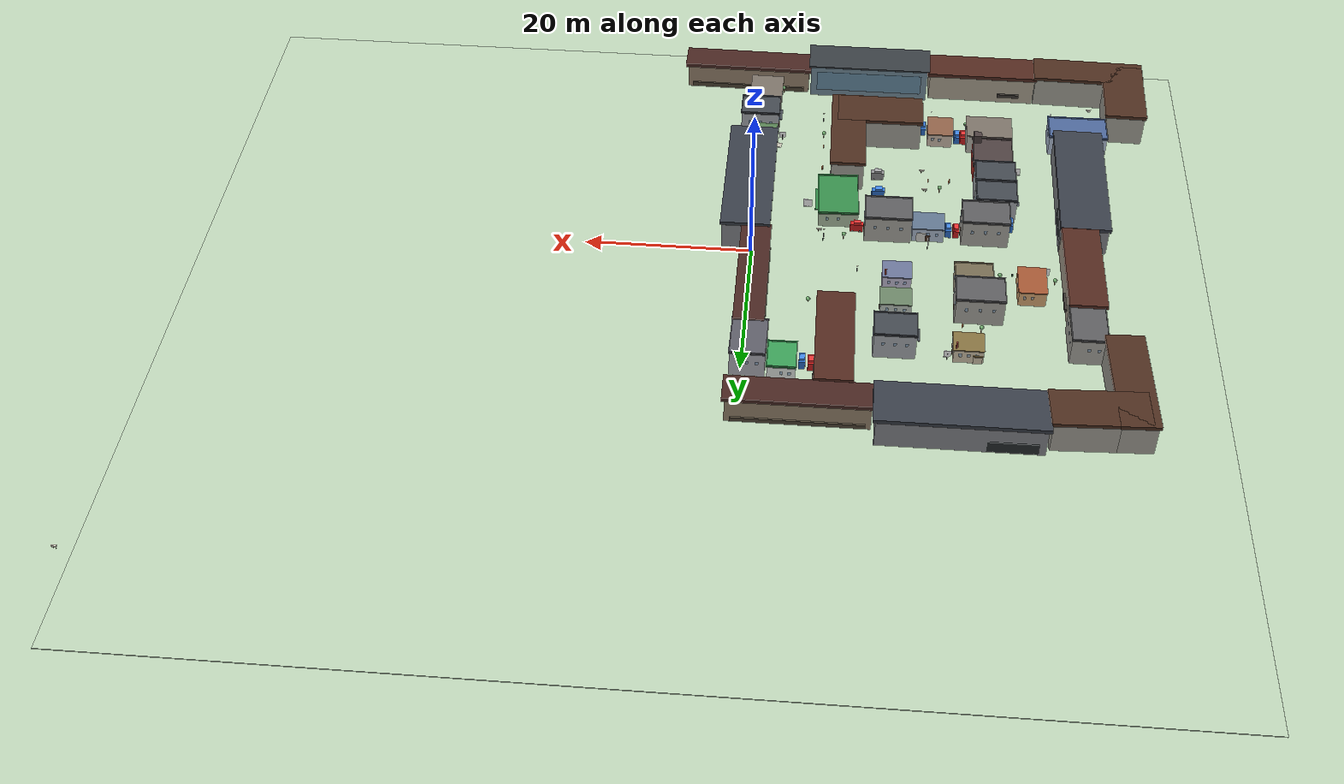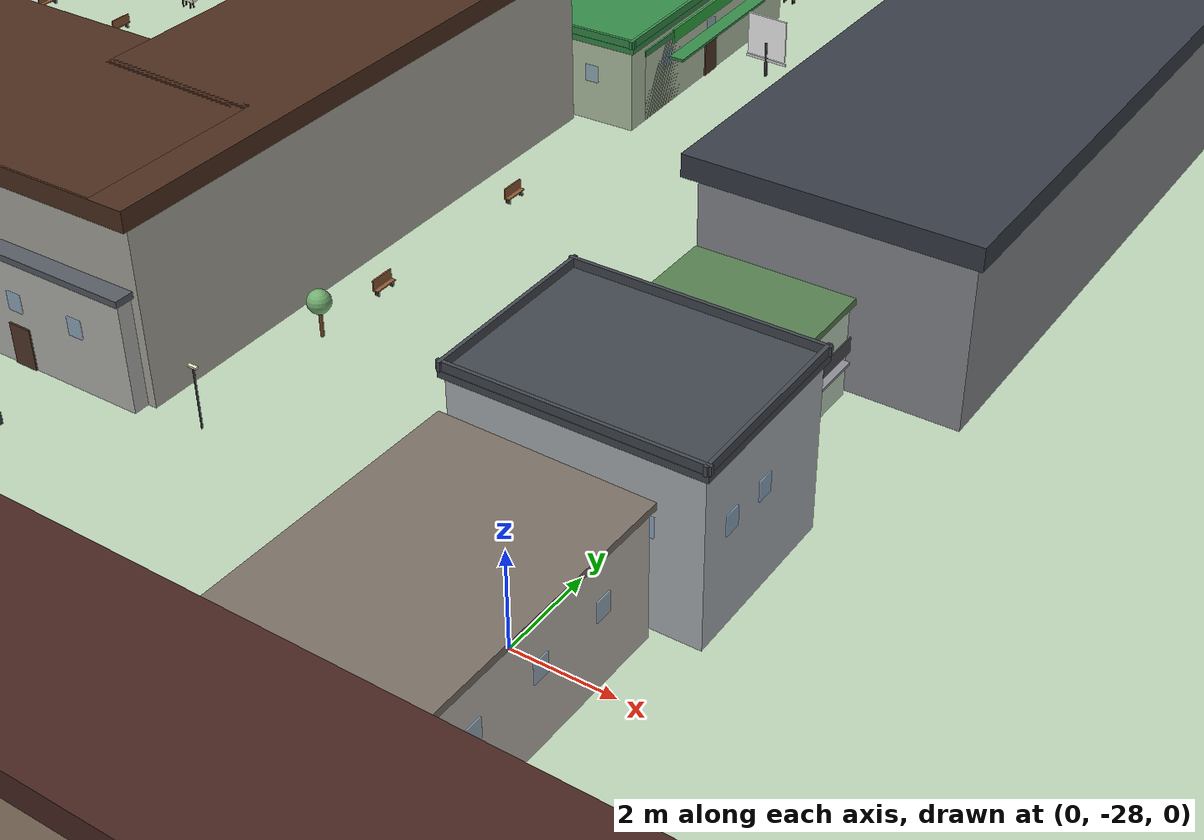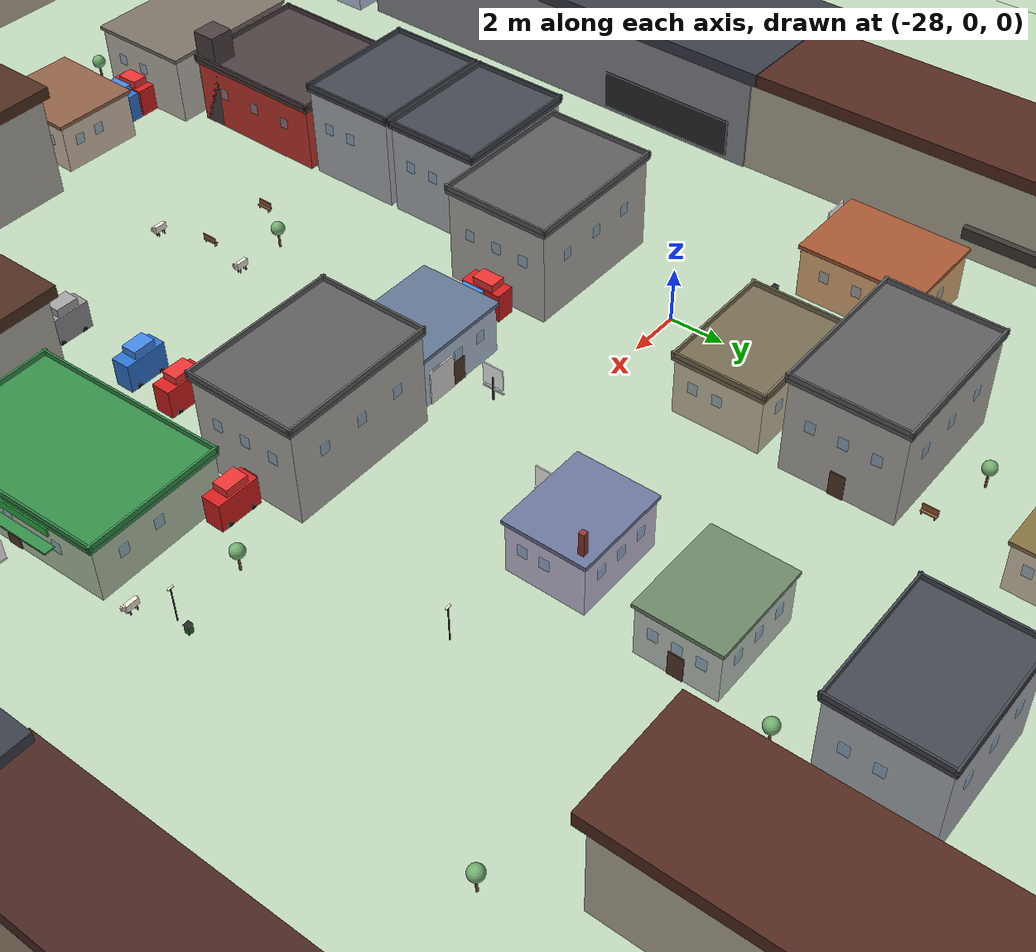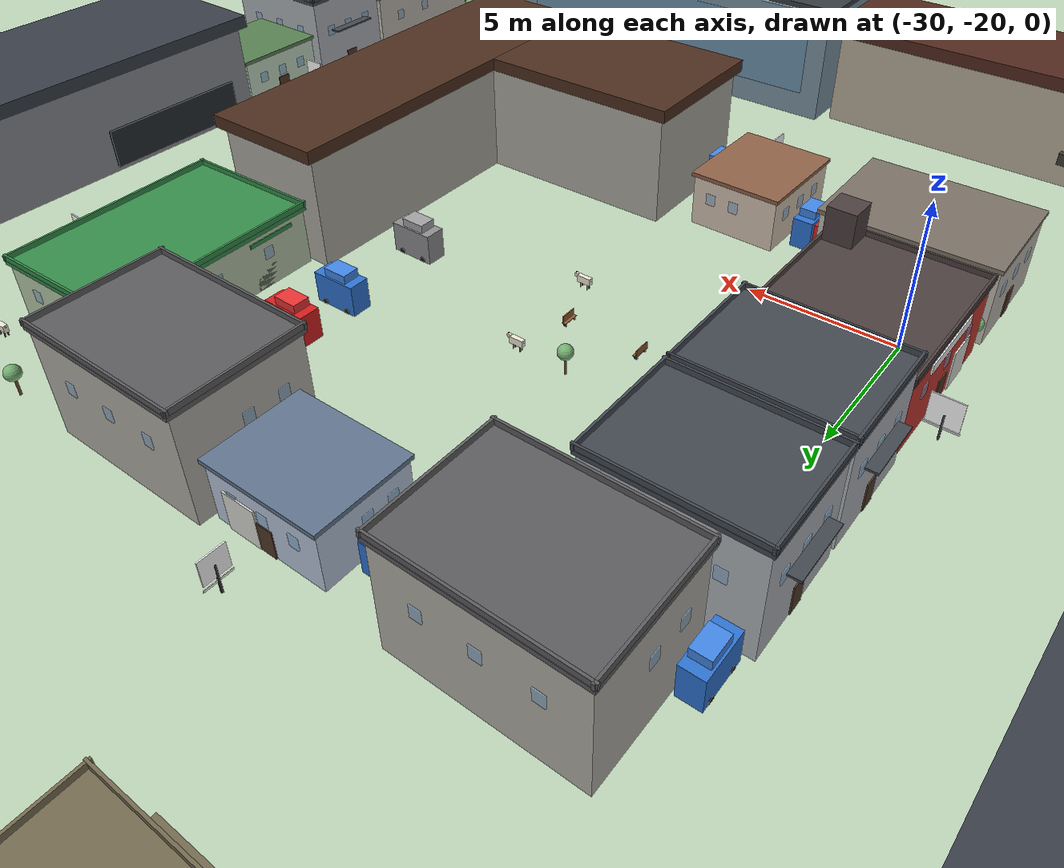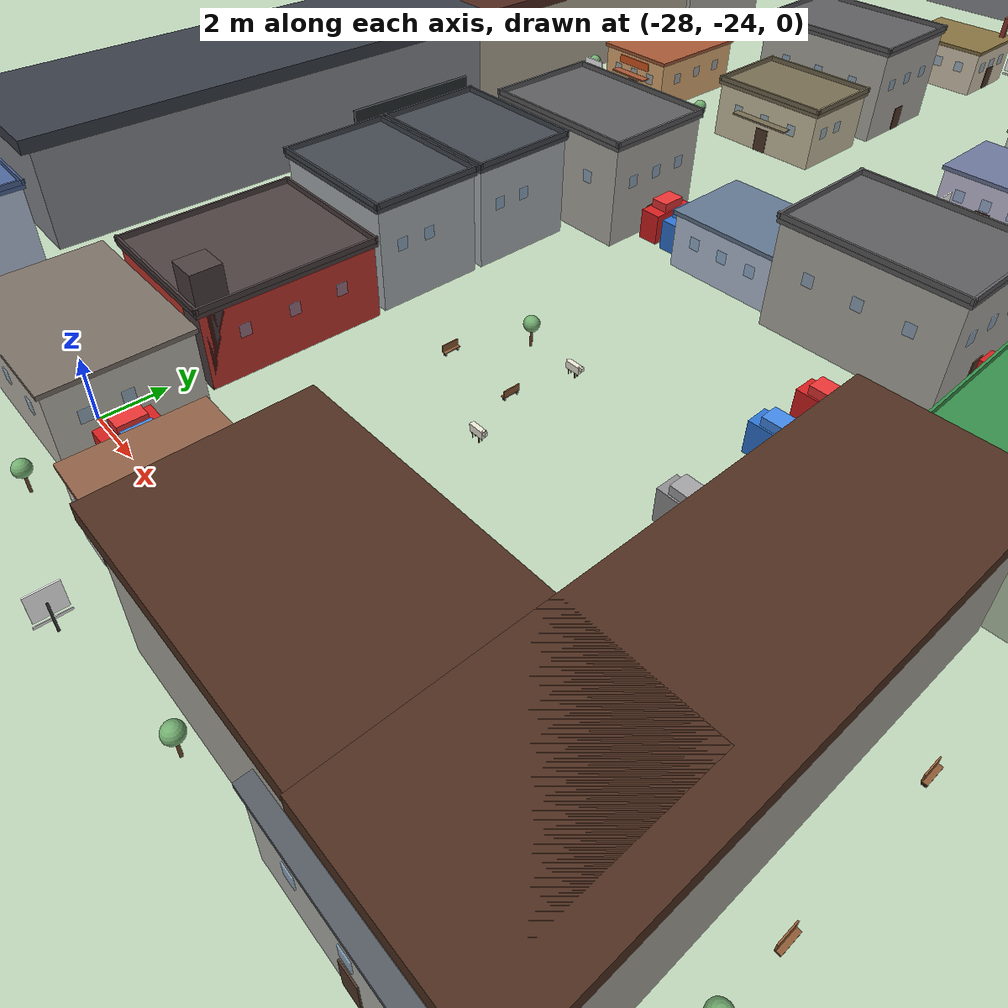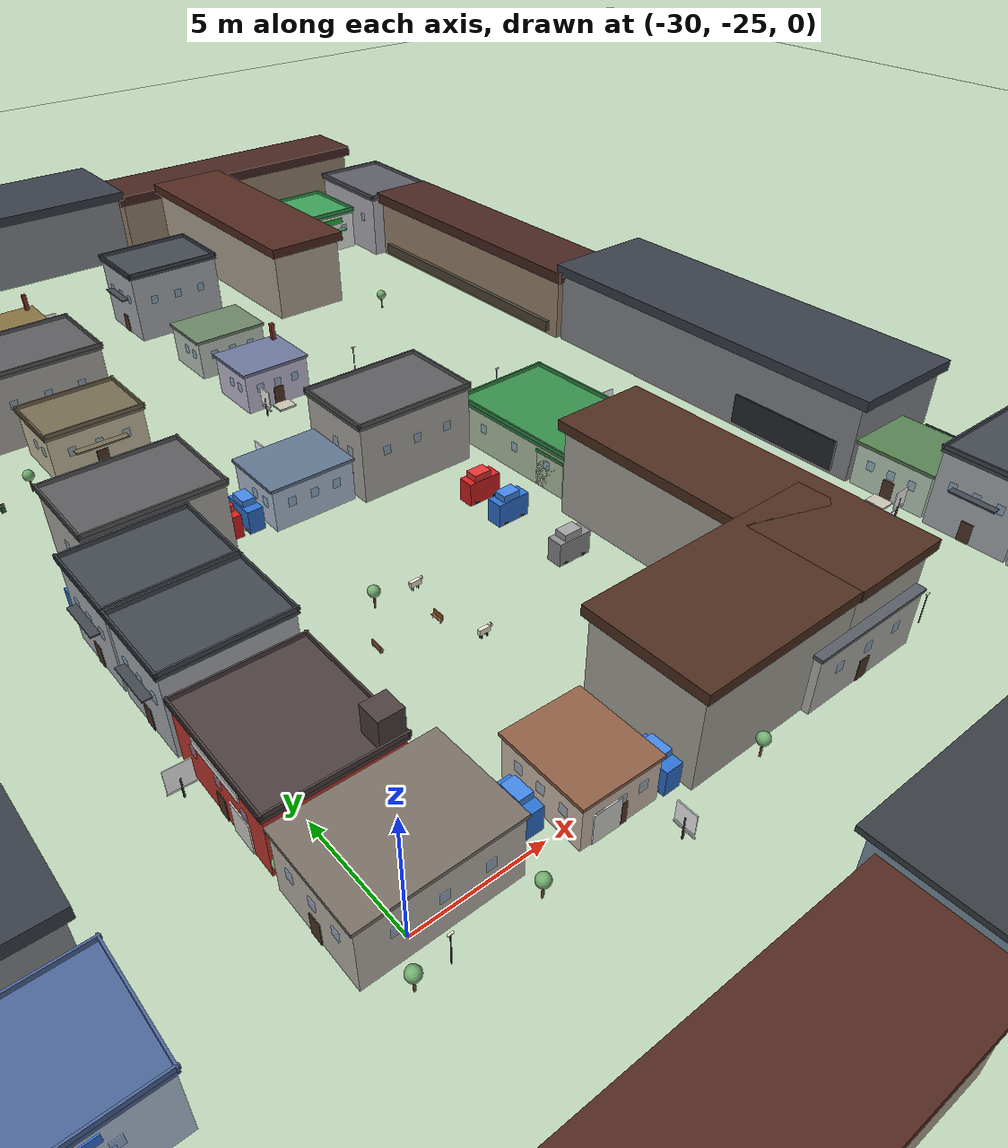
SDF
<?xml version='1.0' encoding='utf-8'?>
<sdf version="1.10">
  <world name="city">
    <physics name="physics" type="ignored">
      <max_step_size>0.002</max_step_size>
      <real_time_factor>1</real_time_factor>
      <real_time_update_rate>100</real_time_update_rate>
    </physics>
    <plugin name="gz::sim::systems::Physics" filename="gz-sim-physics-system" />
    <plugin name="gz::sim::systems::UserCommands" filename="gz-sim-user-commands-system" />
    <plugin name="gz::sim::systems::SceneBroadcaster" filename="gz-sim-scene-broadcaster-system" />
    <plugin name="gz::sim::systems::Sensors" filename="gz-sim-sensors-system">
      <render_engine>ogre2</render_engine>
    </plugin>
    <plugin name="gz::sim::systems::Imu" filename="gz-sim-imu-system" />
    <plugin name="gz::sim::systems::AirPressure"
        filename="gz-sim-air-pressure-system" />
<plugin name="gz::sim::systems::NavSat"
        filename="gz-sim-navsat-system" />
<plugin name="gz::sim::systems::Magnetometer"
        filename="gz-sim-magnetometer-system" />
    <gravity>0 0 -9.8000000000000007</gravity>
    <magnetic_field>5.5644999999999998e-06 2.2875799999999999e-05 -4.2388400000000002e-05</magnetic_field>
        <spherical_coordinates>
      <surface_model>EARTH_WGS84</surface_model>
      <world_frame_orientation>ENU</world_frame_orientation>
      <latitude_deg>37.412173071650805</latitude_deg>
      <longitude_deg>-121.998878727967</longitude_deg>
      <elevation>38</elevation>
    </spherical_coordinates>
    <atmosphere type="adiabatic" />
    <scene>
      <ambient>0.400000006 0.400000006 0.400000006 1</ambient>
      <background>0.699999988 0.699999988 0.699999988 1</background>
      <shadows>true</shadows>
    </scene>
    <model name="dock_pad">
      <static>true</static>
      <pose>-40 -29.6 0 0 0 0</pose>
      <link name="link">
        <collision name="plaza_col">
          <pose>0 0 0.008 0 0 0</pose>
          <geometry>
            <box>
              <size>7.2 4.8 0.016</size>
            </box>
          </geometry>
          <surface>
            <friction>
              <ode />
            </friction>
            <bounce />
            <contact />
          </surface>
        </collision>
        <visual name="plaza_vis">
          <pose>0 0 0.008 0 0 0</pose>
          <geometry>
            <box>
              <size>7.2 4.8 0.016</size>
            </box>
          </geometry>
          <material>
            <ambient>0.779999971 0.779999971 0.730000019 1</ambient>
            <diffuse>0.779999971 0.779999971 0.730000019 1</diffuse>
            <specular>0.0799999982 0.0799999982 0.0799999982 1</specular>
          </material>
        </visual>
        <visual name="gx0">
          <pose>-3.6 0 0.0164 0 0 0</pose>
          <geometry>
            <box>
              <size>0.016 4.8 0.002</size>
            </box>
          </geometry>
          <material>
            <ambient>0.639999986 0.639999986 0.600000024 1</ambient>
            <diffuse>0.639999986 0.639999986 0.600000024 1</diffuse>
            <specular>0.0799999982 0.0799999982 0.0799999982 1</specular>
          </material>
        </visual>
        <visual name="gx1">
          <pose>-3 0 0.0164 0 0 0</pose>
          <geometry>
            <box>
              <size>0.016 4.8 0.002</size>
            </box>
          </geometry>
          <material>
            <ambient>0.639999986 0.639999986 0.600000024 1</ambient>
            <diffuse>0.639999986 0.639999986 0.600000024 1</diffuse>
            <specular>0.0799999982 0.0799999982 0.0799999982 1</specular>
          </material>
        </visual>
        <visual name="gx2">
          <pose>-2.4 0 0.0164 0 0 0</pose>
          <geometry>
            <box>
              <size>0.016 4.8 0.002</size>
            </box>
          </geometry>
          <material>
            <ambient>0.639999986 0.639999986 0.600000024 1</ambient>
            <diffuse>0.639999986 0.639999986 0.600000024 1</diffuse>
            <specular>0.0799999982 0.0799999982 0.0799999982 1</specular>
          </material>
        </visual>
        <visual name="gx3">
          <pose>-1.8 0 0.0164 0 0 0</pose>
          <geometry>
            <box>
              <size>0.016 4.8 0.002</size>
            </box>
          </geometry>
          <material>
            <ambient>0.639999986 0.639999986 0.600000024 1</ambient>
            <diffuse>0.639999986 0.639999986 0.600000024 1</diffuse>
            <specular>0.0799999982 0.0799999982 0.0799999982 1</specular>
          </material>
        </visual>
        <visual name="gx4">
          <pose>-1.2 0 0.0164 0 0 0</pose>
          <geometry>
            <box>
              <size>0.016 4.8 0.002</size>
            </box>
          </geometry>
          <material>
            <ambient>0.639999986 0.639999986 0.600000024 1</ambient>
            <diffuse>0.639999986 0.639999986 0.600000024 1</diffuse>
            <specular>0.0799999982 0.0799999982 0.0799999982 1</specular>
          </material>
        </visual>
        <visual name="gx5">
          <pose>-0.6 0 0.0164 0 0 0</pose>
          <geometry>
            <box>
              <size>0.016 4.8 0.002</size>
            </box>
          </geometry>
          <material>
            <ambient>0.639999986 0.639999986 0.600000024 1</ambient>
            <diffuse>0.639999986 0.639999986 0.600000024 1</diffuse>
            <specular>0.0799999982 0.0799999982 0.0799999982 1</specular>
          </material>
        </visual>
        <visual name="gx6">
          <pose>0 0 0.0164 0 0 0</pose>
          <geometry>
            <box>
              <size>0.016 4.8 0.002</size>
            </box>
          </geometry>
          <material>
            <ambient>0.639999986 0.639999986 0.600000024 1</ambient>
            <diffuse>0.639999986 0.639999986 0.600000024 1</diffuse>
            <specular>0.0799999982 0.0799999982 0.0799999982 1</specular>
          </material>
        </visual>
        <visual name="gx7">
          <pose>0.6 0 0.0164 0 0 0</pose>
          <geometry>
            <box>
              <size>0.016 4.8 0.002</size>
            </box>
          </geometry>
          <material>
            <ambient>0.639999986 0.639999986 0.600000024 1</ambient>
            <diffuse>0.639999986 0.639999986 0.600000024 1</diffuse>
            <specular>0.0799999982 0.0799999982 0.0799999982 1</specular>
          </material>
        </visual>
        <visual name="gx8">
          <pose>1.2 0 0.0164 0 0 0</pose>
          <geometry>
            <box>
              <size>0.016 4.8 0.002</size>
            </box>
          </geometry>
          <material>
            <ambient>0.639999986 0.639999986 0.600000024 1</ambient>
            <diffuse>0.639999986 0.639999986 0.600000024 1</diffuse>
            <specular>0.0799999982 0.0799999982 0.0799999982 1</specular>
          </material>
        </visual>
        <visual name="gx9">
          <pose>1.8 0 0.0164 0 0 0</pose>
          <geometry>
            <box>
              <size>0.016 4.8 0.002</size>
            </box>
          </geometry>
          <material>
            <ambient>0.639999986 0.639999986 0.600000024 1</ambient>
            <diffuse>0.639999986 0.639999986 0.600000024 1</diffuse>
            <specular>0.0799999982 0.0799999982 0.0799999982 1</specular>
          </material>
        </visual>
        <visual name="gx10">
          <pose>2.4 0 0.0164 0 0 0</pose>
          <geometry>
            <box>
              <size>0.016 4.8 0.002</size>
            </box>
          </geometry>
          <material>
            <ambient>0.639999986 0.639999986 0.600000024 1</ambient>
            <diffuse>0.639999986 0.639999986 0.600000024 1</diffuse>
            <specular>0.0799999982 0.0799999982 0.0799999982 1</specular>
          </material>
        </visual>
        <visual name="gx11">
          <pose>3 0 0.0164 0 0 0</pose>
          <geometry>
            <box>
              <size>0.016 4.8 0.002</size>
            </box>
          </geometry>
          <material>
            <ambient>0.639999986 0.639999986 0.600000024 1</ambient>
            <diffuse>0.639999986 0.639999986 0.600000024 1</diffuse>
            <specular>0.0799999982 0.0799999982 0.0799999982 1</specular>
          </material>
        </visual>
        <visual name="gx12">
          <pose>3.6 0 0.0164 0 0 0</pose>
          <geometry>
            <box>
              <size>0.016 4.8 0.002</size>
            </box>
          </geometry>
          <material>
            <ambient>0.639999986 0.639999986 0.600000024 1</ambient>
            <diffuse>0.639999986 0.639999986 0.600000024 1</diffuse>
            <specular>0.0799999982 0.0799999982 0.0799999982 1</specular>
          </material>
        </visual>
        <visual name="gy0">
          <pose>0 -2.4 0.0164 0 0 0</pose>
          <geometry>
            <box>
              <size>7.2 0.016 0.002</size>
            </box>
          </geometry>
          <material>
            <ambient>0.639999986 0.639999986 0.600000024 1</ambient>
            <diffuse>0.639999986 0.639999986 0.600000024 1</diffuse>
            <specular>0.0799999982 0.0799999982 0.0799999982 1</specular>
          </material>
        </visual>
        <visual name="gy1">
          <pose>0 -1.8 0.0164 0 0 0</pose>
          <geometry>
            <box>
              <size>7.2 0.016 0.002</size>
            </box>
          </geometry>
          <material>
            <ambient>0.639999986 0.639999986 0.600000024 1</ambient>
            <diffuse>0.639999986 0.639999986 0.600000024 1</diffuse>
            <specular>0.0799999982 0.0799999982 0.0799999982 1</specular>
          </material>
        </visual>
        <visual name="gy2">
          <pose>0 -1.2 0.0164 0 0 0</pose>
          <geometry>
            <box>
              <size>7.2 0.016 0.002</size>
            </box>
          </geometry>
          <material>
            <ambient>0.639999986 0.639999986 0.600000024 1</ambient>
            <diffuse>0.639999986 0.639999986 0.600000024 1</diffuse>
            <specular>0.0799999982 0.0799999982 0.0799999982 1</specular>
          </material>
        </visual>
        <visual name="gy3">
          <pose>0 -0.6 0.0164 0 0 0</pose>
          <geometry>
            <box>
              <size>7.2 0.016 0.002</size>
            </box>
          </geometry>
          <material>
            <ambient>0.639999986 0.639999986 0.600000024 1</ambient>
            <diffuse>0.639999986 0.639999986 0.600000024 1</diffuse>
            <specular>0.0799999982 0.0799999982 0.0799999982 1</specular>
          </material>
        </visual>
        <visual name="gy4">
          <pose>0 0 0.0164 0 0 0</pose>
          <geometry>
            <box>
              <size>7.2 0.016 0.002</size>
            </box>
          </geometry>
          <material>
            <ambient>0.639999986 0.639999986 0.600000024 1</ambient>
            <diffuse>0.639999986 0.639999986 0.600000024 1</diffuse>
            <specular>0.0799999982 0.0799999982 0.0799999982 1</specular>
          </material>
        </visual>
        <visual name="gy5">
          <pose>0 0.6 0.0164 0 0 0</pose>
          <geometry>
            <box>
              <size>7.2 0.016 0.002</size>
            </box>
          </geometry>
          <material>
            <ambient>0.639999986 0.639999986 0.600000024 1</ambient>
            <diffuse>0.639999986 0.639999986 0.600000024 1</diffuse>
            <specular>0.0799999982 0.0799999982 0.0799999982 1</specular>
          </material>
        </visual>
        <visual name="gy6">
          <pose>0 1.2 0.0164 0 0 0</pose>
          <geometry>
            <box>
              <size>7.2 0.016 0.002</size>
            </box>
          </geometry>
          <material>
            <ambient>0.639999986 0.639999986 0.600000024 1</ambient>
            <diffuse>0.639999986 0.639999986 0.600000024 1</diffuse>
            <specular>0.0799999982 0.0799999982 0.0799999982 1</specular>
          </material>
        </visual>
        <visual name="gy7">
          <pose>0 1.8 0.0164 0 0 0</pose>
          <geometry>
            <box>
              <size>7.2 0.016 0.002</size>
            </box>
          </geometry>
          <material>
            <ambient>0.639999986 0.639999986 0.600000024 1</ambient>
            <diffuse>0.639999986 0.639999986 0.600000024 1</diffuse>
            <specular>0.0799999982 0.0799999982 0.0799999982 1</specular>
          </material>
        </visual>
        <visual name="gy8">
          <pose>0 2.4 0.0164 0 0 0</pose>
          <geometry>
            <box>
              <size>7.2 0.016 0.002</size>
            </box>
          </geometry>
          <material>
            <ambient>0.639999986 0.639999986 0.600000024 1</ambient>
            <diffuse>0.639999986 0.639999986 0.600000024 1</diffuse>
            <specular>0.0799999982 0.0799999982 0.0799999982 1</specular>
          </material>
        </visual>
        <pose>0 0 0 0 0 0</pose>
        <inertial>
          <pose>0 0 0 0 0 0</pose>
          <mass>1</mass>
          <inertia>
            <ixx>1</ixx>
            <ixy>0</ixy>
            <ixz>0</ixz>
            <iyy>1</iyy>
            <iyz>0</iyz>
            <izz>1</izz>
          </inertia>
        </inertial>
        <enable_wind>false</enable_wind>
      </link>
      <self_collide>false</self_collide>
    </model>
    <model name="docking_station">
      <static>true</static>
      <pose>-40.3145965576172 -24 0 0 0 0</pose>
      <link name="link">
        <collision name="body_col">
          <pose>0 0 1.36 0 0 0</pose>
          <geometry>
            <box>
              <size>7.2 4 2.72</size>
            </box>
          </geometry>
          <surface>
            <friction>
              <ode />
            </friction>
            <bounce />
            <contact />
          </surface>
        </collision>
        <visual name="body_vis">
          <pose>0 0 1.36 0 0 0</pose>
          <geometry>
            <box>
              <size>7.2 4 2.72</size>
            </box>
          </geometry>
          <material>
            <ambient>0.74000001 0.800000012 0.899999976 1</ambient>
            <diffuse>0.74000001 0.800000012 0.899999976 1</diffuse>
            <specular>0.0799999982 0.0799999982 0.0799999982 1</specular>
          </material>
        </visual>
        <collision name="roof_col">
          <pose>0 0 2.79 0 0 0</pose>
          <geometry>
            <box>
              <size>7.36 4.16 0.14</size>
            </box>
          </geometry>
          <surface>
            <friction>
              <ode />
            </friction>
            <bounce />
            <contact />
          </surface>
        </collision>
        <visual name="roof_vis">
          <pose>0 0 2.79 0 0 0</pose>
          <geometry>
            <box>
              <size>7.36 4.16 0.14</size>
            </box>
          </geometry>
          <material>
            <ambient>0.300000012 0.400000006 0.600000024 1</ambient>
            <diffuse>0.300000012 0.400000006 0.600000024 1</diffuse>
            <specular>0.0799999982 0.0799999982 0.0799999982 1</specular>
          </material>
        </visual>
        <visual name="p1_vis">
          <pose>0 2.036 2.948 0 0 0</pose>
          <geometry>
            <box>
              <size>7.42 0.072 0.18</size>
            </box>
          </geometry>
          <material>
            <ambient>0.300000012 0.400000006 0.600000024 1</ambient>
            <diffuse>0.300000012 0.400000006 0.600000024 1</diffuse>
            <specular>0.0799999982 0.0799999982 0.0799999982 1</specular>
          </material>
        </visual>
        <visual name="p2_vis">
          <pose>0 -2.036 2.948 0 0 0</pose>
          <geometry>
            <box>
              <size>7.42 0.072 0.18</size>
            </box>
          </geometry>
          <material>
            <ambient>0.300000012 0.400000006 0.600000024 1</ambient>
            <diffuse>0.300000012 0.400000006 0.600000024 1</diffuse>
            <specular>0.0799999982 0.0799999982 0.0799999982 1</specular>
          </material>
        </visual>
        <visual name="p3_vis">
          <pose>3.636 0 2.948 0 0 0</pose>
          <geometry>
            <box>
              <size>0.072 4.22 0.18</size>
            </box>
          </geometry>
          <material>
            <ambient>0.300000012 0.400000006 0.600000024 1</ambient>
            <diffuse>0.300000012 0.400000006 0.600000024 1</diffuse>
            <specular>0.0799999982 0.0799999982 0.0799999982 1</specular>
          </material>
        </visual>
        <visual name="p4_vis">
          <pose>-3.636 0 2.948 0 0 0</pose>
          <geometry>
            <box>
              <size>0.072 4.22 0.18</size>
            </box>
          </geometry>
          <material>
            <ambient>0.300000012 0.400000006 0.600000024 1</ambient>
            <diffuse>0.300000012 0.400000006 0.600000024 1</diffuse>
            <specular>0.0799999982 0.0799999982 0.0799999982 1</specular>
          </material>
        </visual>
        <visual name="door_vis">
          <pose>0 -2.016 0.48 0 0 0</pose>
          <geometry>
            <box>
              <size>0.52 0.04 0.96</size>
            </box>
          </geometry>
          <material>
            <ambient>0.319999993 0.219999999 0.159999996 1</ambient>
            <diffuse>0.319999993 0.219999999 0.159999996 1</diffuse>
            <specular>0.0799999982 0.0799999982 0.0799999982 1</specular>
          </material>
        </visual>
        <visual name="win_south_0">
          <pose>-2.016 -2.012 1.6864 0 0 0</pose>
          <geometry>
            <box>
              <size>0.34 0.032 0.4</size>
            </box>
          </geometry>
          <material>
            <ambient>0.550000012 0.720000029 0.879999995 0.550000012</ambient>
            <diffuse>0.550000012 0.720000029 0.879999995 0.550000012</diffuse>
            <specular>0.0799999982 0.0799999982 0.0799999982 1</specular>
            <transparency>0.35</transparency>
          </material>
        </visual>
        <visual name="win_south_1">
          <pose>0 -2.012 1.6864 0 0 0</pose>
          <geometry>
            <box>
              <size>0.34 0.032 0.4</size>
            </box>
          </geometry>
          <material>
            <ambient>0.550000012 0.720000029 0.879999995 0.550000012</ambient>
            <diffuse>0.550000012 0.720000029 0.879999995 0.550000012</diffuse>
            <specular>0.0799999982 0.0799999982 0.0799999982 1</specular>
            <transparency>0.35</transparency>
          </material>
        </visual>
        <visual name="win_south_2">
          <pose>2.016 -2.012 1.6864 0 0 0</pose>
          <geometry>
            <box>
              <size>0.34 0.032 0.4</size>
            </box>
          </geometry>
          <material>
            <ambient>0.550000012 0.720000029 0.879999995 0.550000012</ambient>
            <diffuse>0.550000012 0.720000029 0.879999995 0.550000012</diffuse>
            <specular>0.0799999982 0.0799999982 0.0799999982 1</specular>
            <transparency>0.35</transparency>
          </material>
        </visual>
        <visual name="win_west_0">
          <pose>-3.612 -1.12 1.6864 0 0 0</pose>
          <geometry>
            <box>
              <size>0.032 0.34 0.4</size>
            </box>
          </geometry>
          <material>
            <ambient>0.550000012 0.720000029 0.879999995 0.550000012</ambient>
            <diffuse>0.550000012 0.720000029 0.879999995 0.550000012</diffuse>
            <specular>0.0799999982 0.0799999982 0.0799999982 1</specular>
            <transparency>0.35</transparency>
          </material>
        </visual>
        <visual name="win_west_1">
          <pose>-3.612 0 1.6864 0 0 0</pose>
          <geometry>
            <box>
              <size>0.032 0.34 0.4</size>
            </box>
          </geometry>
          <material>
            <ambient>0.550000012 0.720000029 0.879999995 0.550000012</ambient>
            <diffuse>0.550000012 0.720000029 0.879999995 0.550000012</diffuse>
            <specular>0.0799999982 0.0799999982 0.0799999982 1</specular>
            <transparency>0.35</transparency>
          </material>
        </visual>
        <visual name="win_east_0">
          <pose>3.612 -1.12 1.6864 0 0 0</pose>
          <geometry>
            <box>
              <size>0.032 0.34 0.4</size>
            </box>
          </geometry>
          <material>
            <ambient>0.550000012 0.720000029 0.879999995 0.550000012</ambient>
            <diffuse>0.550000012 0.720000029 0.879999995 0.550000012</diffuse>
            <specular>0.0799999982 0.0799999982 0.0799999982 1</specular>
            <transparency>0.35</transparency>
          </material>
        </visual>
        <visual name="win_east_1">
          <pose>3.612 0 1.6864 0 0 0</pose>
          <geometry>
            <box>
              <size>0.032 0.34 0.4</size>
            </box>
          </geometry>
          <material>
            <ambient>0.550000012 0.720000029 0.879999995 0.550000012</ambient>
            <diffuse>0.550000012 0.720000029 0.879999995 0.550000012</diffuse>
            <specular>0.0799999982 0.0799999982 0.0799999982 1</specular>
            <transparency>0.35</transparency>
          </material>
        </visual>
        <visual name="win_north_0">
          <pose>-2.016 2.012 1.6864 0 0 0</pose>
          <geometry>
            <box>
              <size>0.34 0.032 0.4</size>
            </box>
          </geometry>
          <material>
            <ambient>0.550000012 0.720000029 0.879999995 0.550000012</ambient>
            <diffuse>0.550000012 0.720000029 0.879999995 0.550000012</diffuse>
            <specular>0.0799999982 0.0799999982 0.0799999982 1</specular>
            <transparency>0.35</transparency>
          </material>
        </visual>
        <visual name="win_north_1">
          <pose>0 2.012 1.6864 0 0 0</pose>
          <geometry>
            <box>
              <size>0.34 0.032 0.4</size>
            </box>
          </geometry>
          <material>
            <ambient>0.550000012 0.720000029 0.879999995 0.550000012</ambient>
            <diffuse>0.550000012 0.720000029 0.879999995 0.550000012</diffuse>
            <specular>0.0799999982 0.0799999982 0.0799999982 1</specular>
            <transparency>0.35</transparency>
          </material>
        </visual>
        <visual name="win_north_2">
          <pose>2.016 2.012 1.6864 0 0 0</pose>
          <geometry>
            <box>
              <size>0.34 0.032 0.4</size>
            </box>
          </geometry>
          <material>
            <ambient>0.550000012 0.720000029 0.879999995 0.550000012</ambient>
            <diffuse>0.550000012 0.720000029 0.879999995 0.550000012</diffuse>
            <specular>0.0799999982 0.0799999982 0.0799999982 1</specular>
            <transparency>0.35</transparency>
          </material>
        </visual>
        <visual name="awning">
          <pose>0 -2.22 1.6864 0 0 0</pose>
          <geometry>
            <box>
              <size>3.96 0.36 0.064</size>
            </box>
          </geometry>
          <material>
            <ambient>0.300000012 0.400000006 0.600000024 1</ambient>
            <diffuse>0.300000012 0.400000006 0.600000024 1</diffuse>
            <specular>0.0799999982 0.0799999982 0.0799999982 1</specular>
          </material>
        </visual>
        <visual name="sign_vis">
          <pose>0 -2.028 2.312 0 0 0</pose>
          <geometry>
            <box>
              <size>3.6 0.048 0.32</size>
            </box>
          </geometry>
          <material>
            <ambient>0.219999999 0.449999988 0.860000014 1</ambient>
            <diffuse>0.219999999 0.449999988 0.860000014 1</diffuse>
            <specular>0.0799999982 0.0799999982 0.0799999982 1</specular>
          </material>
        </visual>
        <pose>0 0 0 0 0 0</pose>
        <inertial>
          <pose>0 0 0 0 0 0</pose>
          <mass>1</mass>
          <inertia>
            <ixx>1</ixx>
            <ixy>0</ixy>
            <ixz>0</ixz>
            <iyy>1</iyy>
            <iyz>0</iyz>
            <izz>1</izz>
          </inertia>
        </inertial>
        <enable_wind>false</enable_wind>
      </link>
      <self_collide>false</self_collide>
    </model>
    <model name="road_west_connector">
      <static>true</static>
      <pose>-34.4545196533203 -12.8991256713867 0 0 0 1.57080003571763</pose>
      <link name="link">
        <collision name="road_col">
          <pose>0 0 0.004 0 0 0</pose>
          <geometry>
            <box>
              <size>29.6 4 0.008</size>
            </box>
          </geometry>
          <surface>
            <friction>
              <ode />
            </friction>
            <bounce />
            <contact />
          </surface>
        </collision>
        <visual name="road_vis">
          <pose>0 0 0.004 0 0 0</pose>
          <geometry>
            <box>
              <size>29.6 4 0.008</size>
            </box>
          </geometry>
          <material>
            <ambient>0.230000004 0.230000004 0.239999995 1</ambient>
            <diffuse>0.230000004 0.230000004 0.239999995 1</diffuse>
            <specular>0.0799999982 0.0799999982 0.0799999982 1</specular>
          </material>
        </visual>
        <visual name="dash0_vis">
          <pose>-12.4 0 0.0088 0 0 0</pose>
          <geometry>
            <box>
              <size>1.2 0.072 0.004</size>
            </box>
          </geometry>
          <material>
            <ambient>0.959999979 0.939999998 0.829999983 1</ambient>
            <diffuse>0.959999979 0.939999998 0.829999983 1</diffuse>
            <specular>0.0799999982 0.0799999982 0.0799999982 1</specular>
          </material>
        </visual>
        <visual name="dash1_vis">
          <pose>-8.4 0 0.0088 0 0 0</pose>
          <geometry>
            <box>
              <size>1.2 0.072 0.004</size>
            </box>
          </geometry>
          <material>
            <ambient>0.959999979 0.939999998 0.829999983 1</ambient>
            <diffuse>0.959999979 0.939999998 0.829999983 1</diffuse>
            <specular>0.0799999982 0.0799999982 0.0799999982 1</specular>
          </material>
        </visual>
        <visual name="dash2_vis">
          <pose>-4.4 0 0.0088 0 0 0</pose>
          <geometry>
            <box>
              <size>1.2 0.072 0.004</size>
            </box>
          </geometry>
          <material>
            <ambient>0.959999979 0.939999998 0.829999983 1</ambient>
            <diffuse>0.959999979 0.939999998 0.829999983 1</diffuse>
            <specular>0.0799999982 0.0799999982 0.0799999982 1</specular>
          </material>
        </visual>
        <visual name="dash3_vis">
          <pose>-0.4 0 0.0088 0 0 0</pose>
          <geometry>
            <box>
              <size>1.2 0.072 0.004</size>
            </box>
          </geometry>
          <material>
            <ambient>0.959999979 0.939999998 0.829999983 1</ambient>
            <diffuse>0.959999979 0.939999998 0.829999983 1</diffuse>
            <specular>0.0799999982 0.0799999982 0.0799999982 1</specular>
          </material>
        </visual>
        <visual name="dash4_vis">
          <pose>3.6 0 0.0088 0 0 0</pose>
          <geometry>
            <box>
              <size>1.2 0.072 0.004</size>
            </box>
          </geometry>
          <material>
            <ambient>0.959999979 0.939999998 0.829999983 1</ambient>
            <diffuse>0.959999979 0.939999998 0.829999983 1</diffuse>
            <specular>0.0799999982 0.0799999982 0.0799999982 1</specular>
          </material>
        </visual>
        <visual name="dash5_vis">
          <pose>7.6 0 0.0088 0 0 0</pose>
          <geometry>
            <box>
              <size>1.2 0.072 0.004</size>
            </box>
          </geometry>
          <material>
            <ambient>0.959999979 0.939999998 0.829999983 1</ambient>
            <diffuse>0.959999979 0.939999998 0.829999983 1</diffuse>
            <specular>0.0799999982 0.0799999982 0.0799999982 1</specular>
          </material>
        </visual>
        <visual name="dash6_vis">
          <pose>11.6 0 0.0088 0 0 0</pose>
          <geometry>
            <box>
              <size>1.2 0.072 0.004</size>
            </box>
          </geometry>
          <material>
            <ambient>0.959999979 0.939999998 0.829999983 1</ambient>
            <diffuse>0.959999979 0.939999998 0.829999983 1</diffuse>
            <specular>0.0799999982 0.0799999982 0.0799999982 1</specular>
          </material>
        </visual>
        <pose>0 0 0 0 0 0</pose>
        <inertial>
          <pose>0 0 0 0 0 0</pose>
          <mass>1</mass>
          <inertia>
            <ixx>1</ixx>
            <ixy>0</ixy>
            <ixz>0</ixz>
            <iyy>1</iyy>
            <iyz>0</iyz>
            <izz>1</izz>
          </inertia>
        </inertial>
        <enable_wind>false</enable_wind>
      </link>
      <self_collide>false</self_collide>
    </model>
    <model name="road_central_northsouth">
      <static>true</static>
      <pose>-4.79999389648438 -4.47619018554688 0 0 0 1.57080003571763</pose>
      <link name="link">
        <collision name="road_col">
          <pose>0 0 0.004 0 0 0</pose>
          <geometry>
            <box>
              <size>53.6 4 0.008</size>
            </box>
          </geometry>
          <surface>
            <friction>
              <ode />
            </friction>
            <bounce />
            <contact />
          </surface>
        </collision>
        <visual name="road_vis">
          <pose>0 0 0.004 0 0 0</pose>
          <geometry>
            <box>
              <size>53.6 4 0.008</size>
            </box>
          </geometry>
          <material>
            <ambient>0.230000004 0.230000004 0.239999995 1</ambient>
            <diffuse>0.230000004 0.230000004 0.239999995 1</diffuse>
            <specular>0.0799999982 0.0799999982 0.0799999982 1</specular>
          </material>
        </visual>
        <visual name="dash0_vis">
          <pose>-24.4 0 0.0088 0 0 0</pose>
          <geometry>
            <box>
              <size>1.2 0.072 0.004</size>
            </box>
          </geometry>
          <material>
            <ambient>0.959999979 0.939999998 0.829999983 1</ambient>
            <diffuse>0.959999979 0.939999998 0.829999983 1</diffuse>
            <specular>0.0799999982 0.0799999982 0.0799999982 1</specular>
          </material>
        </visual>
        <visual name="dash1_vis">
          <pose>-20.4 0 0.0088 0 0 0</pose>
          <geometry>
            <box>
              <size>1.2 0.072 0.004</size>
            </box>
          </geometry>
          <material>
            <ambient>0.959999979 0.939999998 0.829999983 1</ambient>
            <diffuse>0.959999979 0.939999998 0.829999983 1</diffuse>
            <specular>0.0799999982 0.0799999982 0.0799999982 1</specular>
          </material>
        </visual>
        <visual name="dash2_vis">
          <pose>-16.4 0 0.0088 0 0 0</pose>
          <geometry>
            <box>
              <size>1.2 0.072 0.004</size>
            </box>
          </geometry>
          <material>
            <ambient>0.959999979 0.939999998 0.829999983 1</ambient>
            <diffuse>0.959999979 0.939999998 0.829999983 1</diffuse>
            <specular>0.0799999982 0.0799999982 0.0799999982 1</specular>
          </material>
        </visual>
        <visual name="dash3_vis">
          <pose>-12.4 0 0.0088 0 0 0</pose>
          <geometry>
            <box>
              <size>1.2 0.072 0.004</size>
            </box>
          </geometry>
          <material>
            <ambient>0.959999979 0.939999998 0.829999983 1</ambient>
            <diffuse>0.959999979 0.939999998 0.829999983 1</diffuse>
            <specular>0.0799999982 0.0799999982 0.0799999982 1</specular>
          </material>
        </visual>
        <visual name="dash4_vis">
          <pose>-8.4 0 0.0088 0 0 0</pose>
          <geometry>
            <box>
              <size>1.2 0.072 0.004</size>
            </box>
          </geometry>
          <material>
            <ambient>0.959999979 0.939999998 0.829999983 1</ambient>
            <diffuse>0.959999979 0.939999998 0.829999983 1</diffuse>
            <specular>0.0799999982 0.0799999982 0.0799999982 1</specular>
          </material>
        </visual>
        <visual name="dash5_vis">
          <pose>-4.4 0 0.0088 0 0 0</pose>
          <geometry>
            <box>
              <size>1.2 0.072 0.004</size>
            </box>
          </geometry>
          <material>
            <ambient>0.959999979 0.939999998 0.829999983 1</ambient>
            <diffuse>0.959999979 0.939999998 0.829999983 1</diffuse>
            <specular>0.0799999982 0.0799999982 0.0799999982 1</specular>
          </material>
        </visual>
        <visual name="dash6_vis">
          <pose>-0.4 0 0.0088 0 0 0</pose>
          <geometry>
            <box>
              <size>1.2 0.072 0.004</size>
            </box>
          </geometry>
          <material>
            <ambient>0.959999979 0.939999998 0.829999983 1</ambient>
            <diffuse>0.959999979 0.939999998 0.829999983 1</diffuse>
            <specular>0.0799999982 0.0799999982 0.0799999982 1</specular>
          </material>
        </visual>
        <visual name="dash7_vis">
          <pose>3.6 0 0.0088 0 0 0</pose>
          <geometry>
            <box>
              <size>1.2 0.072 0.004</size>
            </box>
          </geometry>
          <material>
            <ambient>0.959999979 0.939999998 0.829999983 1</ambient>
            <diffuse>0.959999979 0.939999998 0.829999983 1</diffuse>
            <specular>0.0799999982 0.0799999982 0.0799999982 1</specular>
          </material>
        </visual>
        <visual name="dash8_vis">
          <pose>7.6 0 0.0088 0 0 0</pose>
          <geometry>
            <box>
              <size>1.2 0.072 0.004</size>
            </box>
          </geometry>
          <material>
            <ambient>0.959999979 0.939999998 0.829999983 1</ambient>
            <diffuse>0.959999979 0.939999998 0.829999983 1</diffuse>
            <specular>0.0799999982 0.0799999982 0.0799999982 1</specular>
          </material>
        </visual>
        <visual name="dash9_vis">
          <pose>11.6 0 0.0088 0 0 0</pose>
          <geometry>
            <box>
              <size>1.2 0.072 0.004</size>
            </box>
          </geometry>
          <material>
            <ambient>0.959999979 0.939999998 0.829999983 1</ambient>
            <diffuse>0.959999979 0.939999998 0.829999983 1</diffuse>
            <specular>0.0799999982 0.0799999982 0.0799999982 1</specular>
          </material>
        </visual>
        <visual name="dash10_vis">
          <pose>15.6 0 0.0088 0 0 0</pose>
          <geometry>
            <box>
              <size>1.2 0.072 0.004</size>
            </box>
          </geometry>
          <material>
            <ambient>0.959999979 0.939999998 0.829999983 1</ambient>
            <diffuse>0.959999979 0.939999998 0.829999983 1</diffuse>
            <specular>0.0799999982 0.0799999982 0.0799999982 1</specular>
          </material>
        </visual>
        <visual name="dash11_vis">
          <pose>19.6 0 0.0088 0 0 0</pose>
          <geometry>
            <box>
              <size>1.2 0.072 0.004</size>
            </box>
          </geometry>
          <material>
            <ambient>0.959999979 0.939999998 0.829999983 1</ambient>
            <diffuse>0.959999979 0.939999998 0.829999983 1</diffuse>
            <specular>0.0799999982 0.0799999982 0.0799999982 1</specular>
          </material>
        </visual>
        <visual name="dash12_vis">
          <pose>23.6 0 0.0088 0 0 0</pose>
          <geometry>
            <box>
              <size>1.2 0.072 0.004</size>
            </box>
          </geometry>
          <material>
            <ambient>0.959999979 0.939999998 0.829999983 1</ambient>
            <diffuse>0.959999979 0.939999998 0.829999983 1</diffuse>
            <specular>0.0799999982 0.0799999982 0.0799999982 1</specular>
          </material>
        </visual>
        <visual name="cw0_vis">
          <pose>-0.7 0 0.0088 0 0 0</pose>
          <geometry>
            <box>
              <size>0.112 3.64 0.0048</size>
            </box>
          </geometry>
          <material>
            <ambient>0.959999979 0.959999979 0.920000017 1</ambient>
            <diffuse>0.959999979 0.959999979 0.920000017 1</diffuse>
            <specular>0.0799999982 0.0799999982 0.0799999982 1</specular>
          </material>
        </visual>
        <visual name="cw1_vis">
          <pose>-0.5 0 0.0088 0 0 0</pose>
          <geometry>
            <box>
              <size>0.112 3.64 0.0048</size>
            </box>
          </geometry>
          <material>
            <ambient>0.959999979 0.959999979 0.920000017 1</ambient>
            <diffuse>0.959999979 0.959999979 0.920000017 1</diffuse>
            <specular>0.0799999982 0.0799999982 0.0799999982 1</specular>
          </material>
        </visual>
        <visual name="cw2_vis">
          <pose>-0.3 0 0.0088 0 0 0</pose>
          <geometry>
            <box>
              <size>0.112 3.64 0.0048</size>
            </box>
          </geometry>
          <material>
            <ambient>0.959999979 0.959999979 0.920000017 1</ambient>
            <diffuse>0.959999979 0.959999979 0.920000017 1</diffuse>
            <specular>0.0799999982 0.0799999982 0.0799999982 1</specular>
          </material>
        </visual>
        <visual name="cw3_vis">
          <pose>-0.1 0 0.0088 0 0 0</pose>
          <geometry>
            <box>
              <size>0.112 3.64 0.0048</size>
            </box>
          </geometry>
          <material>
            <ambient>0.959999979 0.959999979 0.920000017 1</ambient>
            <diffuse>0.959999979 0.959999979 0.920000017 1</diffuse>
            <specular>0.0799999982 0.0799999982 0.0799999982 1</specular>
          </material>
        </visual>
        <visual name="cw4_vis">
          <pose>0.1 0 0.0088 0 0 0</pose>
          <geometry>
            <box>
              <size>0.112 3.64 0.0048</size>
            </box>
          </geometry>
          <material>
            <ambient>0.959999979 0.959999979 0.920000017 1</ambient>
            <diffuse>0.959999979 0.959999979 0.920000017 1</diffuse>
            <specular>0.0799999982 0.0799999982 0.0799999982 1</specular>
          </material>
        </visual>
        <visual name="cw5_vis">
          <pose>0.3 0 0.0088 0 0 0</pose>
          <geometry>
            <box>
              <size>0.112 3.64 0.0048</size>
            </box>
          </geometry>
          <material>
            <ambient>0.959999979 0.959999979 0.920000017 1</ambient>
            <diffuse>0.959999979 0.959999979 0.920000017 1</diffuse>
            <specular>0.0799999982 0.0799999982 0.0799999982 1</specular>
          </material>
        </visual>
        <visual name="cw6_vis">
          <pose>0.5 0 0.0088 0 0 0</pose>
          <geometry>
            <box>
              <size>0.112 3.64 0.0048</size>
            </box>
          </geometry>
          <material>
            <ambient>0.959999979 0.959999979 0.920000017 1</ambient>
            <diffuse>0.959999979 0.959999979 0.920000017 1</diffuse>
            <specular>0.0799999982 0.0799999982 0.0799999982 1</specular>
          </material>
        </visual>
        <visual name="cw7_vis">
          <pose>0.7 0 0.0088 0 0 0</pose>
          <geometry>
            <box>
              <size>0.112 3.64 0.0048</size>
            </box>
          </geometry>
          <material>
            <ambient>0.959999979 0.959999979 0.920000017 1</ambient>
            <diffuse>0.959999979 0.959999979 0.920000017 1</diffuse>
            <specular>0.0799999982 0.0799999982 0.0799999982 1</specular>
          </material>
        </visual>
        <pose>0 0 0 0 0 0</pose>
        <inertial>
          <pose>0 0 0 0 0 0</pose>
          <mass>1</mass>
          <inertia>
            <ixx>1</ixx>
            <ixy>0</ixy>
            <ixz>0</ixz>
            <iyy>1</iyy>
            <iyz>0</iyz>
            <izz>1</izz>
          </inertia>
        </inertial>
        <enable_wind>false</enable_wind>
      </link>
      <self_collide>false</self_collide>
    </model>
    <model name="road_west_local">
      <static>true</static>
      <pose>-21.6000396728516 13.0629776000977 0 0 0 1.57080003571763</pose>
      <link name="link">
        <collision name="road_col">
          <pose>0 0 0.004 0 0 0</pose>
          <geometry>
            <box>
              <size>23.2 3.2 0.008</size>
            </box>
          </geometry>
          <surface>
            <friction>
              <ode />
            </friction>
            <bounce />
            <contact />
          </surface>
        </collision>
        <visual name="road_vis">
          <pose>0 0 0.004 0 0 0</pose>
          <geometry>
            <box>
              <size>23.2 3.2 0.008</size>
            </box>
          </geometry>
          <material>
            <ambient>0.230000004 0.230000004 0.239999995 1</ambient>
            <diffuse>0.230000004 0.230000004 0.239999995 1</diffuse>
            <specular>0.0799999982 0.0799999982 0.0799999982 1</specular>
          </material>
        </visual>
        <pose>0 0 0 0 0 0</pose>
        <inertial>
          <pose>0 0 0 0 0 0</pose>
          <mass>1</mass>
          <inertia>
            <ixx>1</ixx>
            <ixy>0</ixy>
            <ixz>0</ixz>
            <iyy>1</iyy>
            <iyz>0</iyz>
            <izz>1</izz>
          </inertia>
        </inertial>
        <enable_wind>false</enable_wind>
      </link>
      <self_collide>false</self_collide>
    </model>
    <model name="central_plaza">
      <static>true</static>
      <pose>-22.6455993652344 -14.5340393066406 0 0 0 1.56522998544021</pose>
      <link name="link">
        <collision name="plaza_col">
          <pose>0 0 0.008 0 0 0</pose>
          <geometry>
            <box>
              <size>7.2 5.6 0.016</size>
            </box>
          </geometry>
          <surface>
            <friction>
              <ode />
            </friction>
            <bounce />
            <contact />
          </surface>
        </collision>
        <visual name="plaza_vis">
          <pose>0 0 0.008 0 0 0</pose>
          <geometry>
            <box>
              <size>7.2 5.6 0.016</size>
            </box>
          </geometry>
          <material>
            <ambient>0.779999971 0.779999971 0.730000019 1</ambient>
            <diffuse>0.779999971 0.779999971 0.730000019 1</diffuse>
            <specular>0.0799999982 0.0799999982 0.0799999982 1</specular>
          </material>
        </visual>
        <visual name="gx0">
          <pose>-3.6 0 0.0164 0 0 0</pose>
          <geometry>
            <box>
              <size>0.016 5.6 0.002</size>
            </box>
          </geometry>
          <material>
            <ambient>0.639999986 0.639999986 0.600000024 1</ambient>
            <diffuse>0.639999986 0.639999986 0.600000024 1</diffuse>
            <specular>0.0799999982 0.0799999982 0.0799999982 1</specular>
          </material>
        </visual>
        <visual name="gx1">
          <pose>-3 0 0.0164 0 0 0</pose>
          <geometry>
            <box>
              <size>0.016 5.6 0.002</size>
            </box>
          </geometry>
          <material>
            <ambient>0.639999986 0.639999986 0.600000024 1</ambient>
            <diffuse>0.639999986 0.639999986 0.600000024 1</diffuse>
            <specular>0.0799999982 0.0799999982 0.0799999982 1</specular>
          </material>
        </visual>
        <visual name="gx2">
          <pose>-2.4 0 0.0164 0 0 0</pose>
          <geometry>
            <box>
              <size>0.016 5.6 0.002</size>
            </box>
          </geometry>
          <material>
            <ambient>0.639999986 0.639999986 0.600000024 1</ambient>
            <diffuse>0.639999986 0.639999986 0.600000024 1</diffuse>
            <specular>0.0799999982 0.0799999982 0.0799999982 1</specular>
          </material>
        </visual>
        <visual name="gx3">
          <pose>-1.8 0 0.0164 0 0 0</pose>
          <geometry>
            <box>
              <size>0.016 5.6 0.002</size>
            </box>
          </geometry>
          <material>
            <ambient>0.639999986 0.639999986 0.600000024 1</ambient>
            <diffuse>0.639999986 0.639999986 0.600000024 1</diffuse>
            <specular>0.0799999982 0.0799999982 0.0799999982 1</specular>
          </material>
        </visual>
        <visual name="gx4">
          <pose>-1.2 0 0.0164 0 0 0</pose>
          <geometry>
            <box>
              <size>0.016 5.6 0.002</size>
            </box>
          </geometry>
          <material>
            <ambient>0.639999986 0.639999986 0.600000024 1</ambient>
            <diffuse>0.639999986 0.639999986 0.600000024 1</diffuse>
            <specular>0.0799999982 0.0799999982 0.0799999982 1</specular>
          </material>
        </visual>
        <visual name="gx5">
          <pose>-0.6 0 0.0164 0 0 0</pose>
          <geometry>
            <box>
              <size>0.016 5.6 0.002</size>
            </box>
          </geometry>
          <material>
            <ambient>0.639999986 0.639999986 0.600000024 1</ambient>
            <diffuse>0.639999986 0.639999986 0.600000024 1</diffuse>
            <specular>0.0799999982 0.0799999982 0.0799999982 1</specular>
          </material>
        </visual>
        <visual name="gx6">
          <pose>0 0 0.0164 0 0 0</pose>
          <geometry>
            <box>
              <size>0.016 5.6 0.002</size>
            </box>
          </geometry>
          <material>
            <ambient>0.639999986 0.639999986 0.600000024 1</ambient>
            <diffuse>0.639999986 0.639999986 0.600000024 1</diffuse>
            <specular>0.0799999982 0.0799999982 0.0799999982 1</specular>
          </material>
        </visual>
        <visual name="gx7">
          <pose>0.6 0 0.0164 0 0 0</pose>
          <geometry>
            <box>
              <size>0.016 5.6 0.002</size>
            </box>
          </geometry>
          <material>
            <ambient>0.639999986 0.639999986 0.600000024 1</ambient>
            <diffuse>0.639999986 0.639999986 0.600000024 1</diffuse>
            <specular>0.0799999982 0.0799999982 0.0799999982 1</specular>
          </material>
        </visual>
        <visual name="gx8">
          <pose>1.2 0 0.0164 0 0 0</pose>
          <geometry>
            <box>
              <size>0.016 5.6 0.002</size>
            </box>
          </geometry>
          <material>
            <ambient>0.639999986 0.639999986 0.600000024 1</ambient>
            <diffuse>0.639999986 0.639999986 0.600000024 1</diffuse>
            <specular>0.0799999982 0.0799999982 0.0799999982 1</specular>
          </material>
        </visual>
        <visual name="gx9">
          <pose>1.8 0 0.0164 0 0 0</pose>
          <geometry>
            <box>
              <size>0.016 5.6 0.002</size>
            </box>
          </geometry>
          <material>
            <ambient>0.639999986 0.639999986 0.600000024 1</ambient>
            <diffuse>0.639999986 0.639999986 0.600000024 1</diffuse>
            <specular>0.0799999982 0.0799999982 0.0799999982 1</specular>
          </material>
        </visual>
        <visual name="gx10">
          <pose>2.4 0 0.0164 0 0 0</pose>
          <geometry>
            <box>
              <size>0.016 5.6 0.002</size>
            </box>
          </geometry>
          <material>
            <ambient>0.639999986 0.639999986 0.600000024 1</ambient>
            <diffuse>0.639999986 0.639999986 0.600000024 1</diffuse>
            <specular>0.0799999982 0.0799999982 0.0799999982 1</specular>
          </material>
        </visual>
        <visual name="gx11">
          <pose>3 0 0.0164 0 0 0</pose>
          <geometry>
            <box>
              <size>0.016 5.6 0.002</size>
            </box>
          </geometry>
          <material>
            <ambient>0.639999986 0.639999986 0.600000024 1</ambient>
            <diffuse>0.639999986 0.639999986 0.600000024 1</diffuse>
            <specular>0.0799999982 0.0799999982 0.0799999982 1</specular>
          </material>
        </visual>
        <visual name="gx12">
          <pose>3.6 0 0.0164 0 0 0</pose>
          <geometry>
            <box>
              <size>0.016 5.6 0.002</size>
            </box>
          </geometry>
          <material>
            <ambient>0.639999986 0.639999986 0.600000024 1</ambient>
            <diffuse>0.639999986 0.639999986 0.600000024 1</diffuse>
            <specular>0.0799999982 0.0799999982 0.0799999982 1</specular>
          </material>
        </visual>
        <visual name="gy0">
          <pose>0 -2.8 0.0164 0 0 0</pose>
          <geometry>
            <box>
              <size>7.2 0.016 0.002</size>
            </box>
          </geometry>
          <material>
            <ambient>0.639999986 0.639999986 0.600000024 1</ambient>
            <diffuse>0.639999986 0.639999986 0.600000024 1</diffuse>
            <specular>0.0799999982 0.0799999982 0.0799999982 1</specular>
          </material>
        </visual>
        <visual name="gy1">
          <pose>0 -2.2 0.0164 0 0 0</pose>
          <geometry>
            <box>
              <size>7.2 0.016 0.002</size>
            </box>
          </geometry>
          <material>
            <ambient>0.639999986 0.639999986 0.600000024 1</ambient>
            <diffuse>0.639999986 0.639999986 0.600000024 1</diffuse>
            <specular>0.0799999982 0.0799999982 0.0799999982 1</specular>
          </material>
        </visual>
        <visual name="gy2">
          <pose>0 -1.6 0.0164 0 0 0</pose>
          <geometry>
            <box>
              <size>7.2 0.016 0.002</size>
            </box>
          </geometry>
          <material>
            <ambient>0.639999986 0.639999986 0.600000024 1</ambient>
            <diffuse>0.639999986 0.639999986 0.600000024 1</diffuse>
            <specular>0.0799999982 0.0799999982 0.0799999982 1</specular>
          </material>
        </visual>
        <visual name="gy3">
          <pose>0 -1 0.0164 0 0 0</pose>
          <geometry>
            <box>
              <size>7.2 0.016 0.002</size>
            </box>
          </geometry>
          <material>
            <ambient>0.639999986 0.639999986 0.600000024 1</ambient>
            <diffuse>0.639999986 0.639999986 0.600000024 1</diffuse>
            <specular>0.0799999982 0.0799999982 0.0799999982 1</specular>
          </material>
        </visual>
        <visual name="gy4">
          <pose>0 -0.4 0.0164 0 0 0</pose>
          <geometry>
            <box>
              <size>7.2 0.016 0.002</size>
            </box>
          </geometry>
          <material>
            <ambient>0.639999986 0.639999986 0.600000024 1</ambient>
            <diffuse>0.639999986 0.639999986 0.600000024 1</diffuse>
            <specular>0.0799999982 0.0799999982 0.0799999982 1</specular>
          </material>
        </visual>
        <visual name="gy5">
          <pose>0 0.2 0.0164 0 0 0</pose>
          <geometry>
            <box>
              <size>7.2 0.016 0.002</size>
            </box>
          </geometry>
          <material>
            <ambient>0.639999986 0.639999986 0.600000024 1</ambient>
            <diffuse>0.639999986 0.639999986 0.600000024 1</diffuse>
            <specular>0.0799999982 0.0799999982 0.0799999982 1</specular>
          </material>
        </visual>
        <visual name="gy6">
          <pose>0 0.8 0.0164 0 0 0</pose>
          <geometry>
            <box>
              <size>7.2 0.016 0.002</size>
            </box>
          </geometry>
          <material>
            <ambient>0.639999986 0.639999986 0.600000024 1</ambient>
            <diffuse>0.639999986 0.639999986 0.600000024 1</diffuse>
            <specular>0.0799999982 0.0799999982 0.0799999982 1</specular>
          </material>
        </visual>
        <visual name="gy7">
          <pose>0 1.4 0.0164 0 0 0</pose>
          <geometry>
            <box>
              <size>7.2 0.016 0.002</size>
            </box>
          </geometry>
          <material>
            <ambient>0.639999986 0.639999986 0.600000024 1</ambient>
            <diffuse>0.639999986 0.639999986 0.600000024 1</diffuse>
            <specular>0.0799999982 0.0799999982 0.0799999982 1</specular>
          </material>
        </visual>
        <visual name="gy8">
          <pose>0 2 0.0164 0 0 0</pose>
          <geometry>
            <box>
              <size>7.2 0.016 0.002</size>
            </box>
          </geometry>
          <material>
            <ambient>0.639999986 0.639999986 0.600000024 1</ambient>
            <diffuse>0.639999986 0.639999986 0.600000024 1</diffuse>
            <specular>0.0799999982 0.0799999982 0.0799999982 1</specular>
          </material>
        </visual>
        <visual name="gy9">
          <pose>0 2.6 0.0164 0 0 0</pose>
          <geometry>
            <box>
              <size>7.2 0.016 0.002</size>
            </box>
          </geometry>
          <material>
            <ambient>0.639999986 0.639999986 0.600000024 1</ambient>
            <diffuse>0.639999986 0.639999986 0.600000024 1</diffuse>
            <specular>0.0799999982 0.0799999982 0.0799999982 1</specular>
          </material>
        </visual>
        <pose>0 0 0 0 0 0</pose>
        <inertial>
          <pose>0 0 0 0 0 0</pose>
          <mass>1</mass>
          <inertia>
            <ixx>1</ixx>
            <ixy>0</ixy>
            <ixz>0</ixz>
            <iyy>1</iyy>
            <iyz>0</iyz>
            <izz>1</izz>
          </inertia>
        </inertial>
        <enable_wind>false</enable_wind>
      </link>
      <self_collide>false</self_collide>
    </model>
    <model name="pharmacy">
      <static>true</static>
      <pose>-4.60933380126953 19.8505111694336 0 0 0 -1.56880994552281</pose>
      <link name="link">
        <collision name="body_col">
          <pose>0 0 1.1 0 0 0</pose>
          <geometry>
            <box>
              <size>4 3.2 2.2</size>
            </box>
          </geometry>
          <surface>
            <friction>
              <ode />
            </friction>
            <bounce />
            <contact />
          </surface>
        </collision>
        <visual name="body_vis">
          <pose>0 0 1.1 0 0 0</pose>
          <geometry>
            <box>
              <size>4 3.2 2.2</size>
            </box>
          </geometry>
          <material>
            <ambient>0.939999998 0.959999979 0.939999998 1</ambient>
            <diffuse>0.939999998 0.959999979 0.939999998 1</diffuse>
            <specular>0.0799999982 0.0799999982 0.0799999982 1</specular>
          </material>
        </visual>
        <collision name="roof_col">
          <pose>0 0 2.27 0 0 0</pose>
          <geometry>
            <box>
              <size>4.16 3.36 0.14</size>
            </box>
          </geometry>
          <surface>
            <friction>
              <ode />
            </friction>
            <bounce />
            <contact />
          </surface>
        </collision>
        <visual name="roof_vis">
          <pose>0 0 2.27 0 0 0</pose>
          <geometry>
            <box>
              <size>4.16 3.36 0.14</size>
            </box>
          </geometry>
          <material>
            <ambient>0.230000004 0.620000005 0.340000004 1</ambient>
            <diffuse>0.230000004 0.620000005 0.340000004 1</diffuse>
            <specular>0.0799999982 0.0799999982 0.0799999982 1</specular>
          </material>
        </visual>
        <visual name="p1_vis">
          <pose>0 1.636 2.428 0 0 0</pose>
          <geometry>
            <box>
              <size>4.22 0.072 0.18</size>
            </box>
          </geometry>
          <material>
            <ambient>0.230000004 0.620000005 0.340000004 1</ambient>
            <diffuse>0.230000004 0.620000005 0.340000004 1</diffuse>
            <specular>0.0799999982 0.0799999982 0.0799999982 1</specular>
          </material>
        </visual>
        <visual name="p2_vis">
          <pose>0 -1.636 2.428 0 0 0</pose>
          <geometry>
            <box>
              <size>4.22 0.072 0.18</size>
            </box>
          </geometry>
          <material>
            <ambient>0.230000004 0.620000005 0.340000004 1</ambient>
            <diffuse>0.230000004 0.620000005 0.340000004 1</diffuse>
            <specular>0.0799999982 0.0799999982 0.0799999982 1</specular>
          </material>
        </visual>
        <visual name="p3_vis">
          <pose>2.036 0 2.428 0 0 0</pose>
          <geometry>
            <box>
              <size>0.072 3.42 0.18</size>
            </box>
          </geometry>
          <material>
            <ambient>0.230000004 0.620000005 0.340000004 1</ambient>
            <diffuse>0.230000004 0.620000005 0.340000004 1</diffuse>
            <specular>0.0799999982 0.0799999982 0.0799999982 1</specular>
          </material>
        </visual>
        <visual name="p4_vis">
          <pose>-2.036 0 2.428 0 0 0</pose>
          <geometry>
            <box>
              <size>0.072 3.42 0.18</size>
            </box>
          </geometry>
          <material>
            <ambient>0.230000004 0.620000005 0.340000004 1</ambient>
            <diffuse>0.230000004 0.620000005 0.340000004 1</diffuse>
            <specular>0.0799999982 0.0799999982 0.0799999982 1</specular>
          </material>
        </visual>
        <visual name="door_vis">
          <pose>2.016 0 0.48 0 0 0</pose>
          <geometry>
            <box>
              <size>0.04 0.52 0.96</size>
            </box>
          </geometry>
          <material>
            <ambient>0.319999993 0.219999999 0.159999996 1</ambient>
            <diffuse>0.319999993 0.219999999 0.159999996 1</diffuse>
            <specular>0.0799999982 0.0799999982 0.0799999982 1</specular>
          </material>
        </visual>
        <visual name="win_east_0">
          <pose>2.012 -0.896 1.364 0 0 0</pose>
          <geometry>
            <box>
              <size>0.032 0.34 0.4</size>
            </box>
          </geometry>
          <material>
            <ambient>0.550000012 0.720000029 0.879999995 0.550000012</ambient>
            <diffuse>0.550000012 0.720000029 0.879999995 0.550000012</diffuse>
            <specular>0.0799999982 0.0799999982 0.0799999982 1</specular>
            <transparency>0.35</transparency>
          </material>
        </visual>
        <visual name="win_east_1">
          <pose>2.012 0 1.364 0 0 0</pose>
          <geometry>
            <box>
              <size>0.032 0.34 0.4</size>
            </box>
          </geometry>
          <material>
            <ambient>0.550000012 0.720000029 0.879999995 0.550000012</ambient>
            <diffuse>0.550000012 0.720000029 0.879999995 0.550000012</diffuse>
            <specular>0.0799999982 0.0799999982 0.0799999982 1</specular>
            <transparency>0.35</transparency>
          </material>
        </visual>
        <visual name="win_east_2">
          <pose>2.012 0.896 1.364 0 0 0</pose>
          <geometry>
            <box>
              <size>0.032 0.34 0.4</size>
            </box>
          </geometry>
          <material>
            <ambient>0.550000012 0.720000029 0.879999995 0.550000012</ambient>
            <diffuse>0.550000012 0.720000029 0.879999995 0.550000012</diffuse>
            <specular>0.0799999982 0.0799999982 0.0799999982 1</specular>
            <transparency>0.35</transparency>
          </material>
        </visual>
        <visual name="win_south_0">
          <pose>-1.12 -1.612 1.364 0 0 0</pose>
          <geometry>
            <box>
              <size>0.34 0.032 0.4</size>
            </box>
          </geometry>
          <material>
            <ambient>0.550000012 0.720000029 0.879999995 0.550000012</ambient>
            <diffuse>0.550000012 0.720000029 0.879999995 0.550000012</diffuse>
            <specular>0.0799999982 0.0799999982 0.0799999982 1</specular>
            <transparency>0.35</transparency>
          </material>
        </visual>
        <visual name="win_south_1">
          <pose>0 -1.612 1.364 0 0 0</pose>
          <geometry>
            <box>
              <size>0.34 0.032 0.4</size>
            </box>
          </geometry>
          <material>
            <ambient>0.550000012 0.720000029 0.879999995 0.550000012</ambient>
            <diffuse>0.550000012 0.720000029 0.879999995 0.550000012</diffuse>
            <specular>0.0799999982 0.0799999982 0.0799999982 1</specular>
            <transparency>0.35</transparency>
          </material>
        </visual>
        <visual name="win_south_2">
          <pose>1.12 -1.612 1.364 0 0 0</pose>
          <geometry>
            <box>
              <size>0.34 0.032 0.4</size>
            </box>
          </geometry>
          <material>
            <ambient>0.550000012 0.720000029 0.879999995 0.550000012</ambient>
            <diffuse>0.550000012 0.720000029 0.879999995 0.550000012</diffuse>
            <specular>0.0799999982 0.0799999982 0.0799999982 1</specular>
            <transparency>0.35</transparency>
          </material>
        </visual>
        <visual name="win_west_0">
          <pose>-2.012 -0.896 1.364 0 0 0</pose>
          <geometry>
            <box>
              <size>0.032 0.34 0.4</size>
            </box>
          </geometry>
          <material>
            <ambient>0.550000012 0.720000029 0.879999995 0.550000012</ambient>
            <diffuse>0.550000012 0.720000029 0.879999995 0.550000012</diffuse>
            <specular>0.0799999982 0.0799999982 0.0799999982 1</specular>
            <transparency>0.35</transparency>
          </material>
        </visual>
        <visual name="win_west_1">
          <pose>-2.012 0 1.364 0 0 0</pose>
          <geometry>
            <box>
              <size>0.032 0.34 0.4</size>
            </box>
          </geometry>
          <material>
            <ambient>0.550000012 0.720000029 0.879999995 0.550000012</ambient>
            <diffuse>0.550000012 0.720000029 0.879999995 0.550000012</diffuse>
            <specular>0.0799999982 0.0799999982 0.0799999982 1</specular>
            <transparency>0.35</transparency>
          </material>
        </visual>
        <visual name="win_north_0">
          <pose>-1.12 1.612 1.364 0 0 0</pose>
          <geometry>
            <box>
              <size>0.34 0.032 0.4</size>
            </box>
          </geometry>
          <material>
            <ambient>0.550000012 0.720000029 0.879999995 0.550000012</ambient>
            <diffuse>0.550000012 0.720000029 0.879999995 0.550000012</diffuse>
            <specular>0.0799999982 0.0799999982 0.0799999982 1</specular>
            <transparency>0.35</transparency>
          </material>
        </visual>
        <visual name="win_north_1">
          <pose>0 1.612 1.364 0 0 0</pose>
          <geometry>
            <box>
              <size>0.34 0.032 0.4</size>
            </box>
          </geometry>
          <material>
            <ambient>0.550000012 0.720000029 0.879999995 0.550000012</ambient>
            <diffuse>0.550000012 0.720000029 0.879999995 0.550000012</diffuse>
            <specular>0.0799999982 0.0799999982 0.0799999982 1</specular>
            <transparency>0.35</transparency>
          </material>
        </visual>
        <visual name="win_north_2">
          <pose>1.12 1.612 1.364 0 0 0</pose>
          <geometry>
            <box>
              <size>0.34 0.032 0.4</size>
            </box>
          </geometry>
          <material>
            <ambient>0.550000012 0.720000029 0.879999995 0.550000012</ambient>
            <diffuse>0.550000012 0.720000029 0.879999995 0.550000012</diffuse>
            <specular>0.0799999982 0.0799999982 0.0799999982 1</specular>
            <transparency>0.35</transparency>
          </material>
        </visual>
        <visual name="awning">
          <pose>2.22 0 1.364 0 0 0</pose>
          <geometry>
            <box>
              <size>0.36 1.76 0.064</size>
            </box>
          </geometry>
          <material>
            <ambient>0.230000004 0.620000005 0.340000004 1</ambient>
            <diffuse>0.230000004 0.620000005 0.340000004 1</diffuse>
            <specular>0.0799999982 0.0799999982 0.0799999982 1</specular>
          </material>
        </visual>
        <visual name="sign_vis">
          <pose>2.028 0 1.87 0 0 0</pose>
          <geometry>
            <box>
              <size>0.048 1.6 0.32</size>
            </box>
          </geometry>
          <material>
            <ambient>0.129999995 0.74000001 0.219999999 1</ambient>
            <diffuse>0.129999995 0.74000001 0.219999999 1</diffuse>
            <specular>0.0799999982 0.0799999982 0.0799999982 1</specular>
          </material>
        </visual>
        <pose>0 0 0 0 0 0</pose>
        <inertial>
          <pose>0 0 0 0 0 0</pose>
          <mass>1</mass>
          <inertia>
            <ixx>1</ixx>
            <ixy>0</ixy>
            <ixz>0</ixz>
            <iyy>1</iyy>
            <iyz>0</iyz>
            <izz>1</izz>
          </inertia>
        </inertial>
        <enable_wind>false</enable_wind>
      </link>
      <self_collide>false</self_collide>
    </model>
    <model name="pharmacy_cross">
      <static>true</static>
      <pose>-9.28 3.2 0 0 0 0</pose>
      <link name="link">
        <pose>0 0 0 0 0 0</pose>
        <inertial>
          <pose>0 0 0 0 0 0</pose>
          <mass>1</mass>
          <inertia>
            <ixx>1</ixx>
            <ixy>0</ixy>
            <ixz>0</ixz>
            <iyy>1</iyy>
            <iyz>0</iyz>
            <izz>1</izz>
          </inertia>
        </inertial>
        <enable_wind>false</enable_wind>
        <link name="link">
          <visual name="vert">
            <pose>0 0 2.56 0 0 0</pose>
            <geometry>
              <box>
                <size>0.2 0.072 0.88</size>
              </box>
            </geometry>
            <material>
              <ambient>0.120 0.760 0.220 1.000</ambient>
              <diffuse>0.120 0.760 0.220 1.000</diffuse>
              <specular>0.08 0.08 0.08 1</specular>
            </material>
          </visual>
          <visual name="hori">
            <pose>0 0 2.56 0 0 0</pose>
            <geometry>
              <box>
                <size>0.6 0.072 0.2</size>
              </box>
            </geometry>
            <material>
              <ambient>0.120 0.760 0.220 1.000</ambient>
              <diffuse>0.120 0.760 0.220 1.000</diffuse>
              <specular>0.08 0.08 0.08 1</specular>
            </material>
          </visual>
        </link>
      </link>
      <self_collide>false</self_collide>
    </model>
    <model name="fire_station">
      <static>true</static>
      <pose>-29.3855163574219 -18.2624008178711 0 0 0 -1.58175001056651</pose>
      <link name="link">
        <collision name="body_col">
          <pose>0 0 1.24 0 0 0</pose>
          <geometry>
            <box>
              <size>5.6 4.8 2.48</size>
            </box>
          </geometry>
          <surface>
            <friction>
              <ode />
            </friction>
            <bounce />
            <contact />
          </surface>
        </collision>
        <visual name="body_vis">
          <pose>0 0 1.24 0 0 0</pose>
          <geometry>
            <box>
              <size>5.6 4.8 2.48</size>
            </box>
          </geometry>
          <material>
            <ambient>0.779999971 0.219999999 0.180000007 1</ambient>
            <diffuse>0.779999971 0.219999999 0.180000007 1</diffuse>
            <specular>0.0799999982 0.0799999982 0.0799999982 1</specular>
          </material>
        </visual>
        <collision name="roof_col">
          <pose>0 0 2.55 0 0 0</pose>
          <geometry>
            <box>
              <size>5.76 4.96 0.14</size>
            </box>
          </geometry>
          <surface>
            <friction>
              <ode />
            </friction>
            <bounce />
            <contact />
          </surface>
        </collision>
        <visual name="roof_vis">
          <pose>0 0 2.55 0 0 0</pose>
          <geometry>
            <box>
              <size>5.76 4.96 0.14</size>
            </box>
          </geometry>
          <material>
            <ambient>0.300000012 0.25 0.25 1</ambient>
            <diffuse>0.300000012 0.25 0.25 1</diffuse>
            <specular>0.0799999982 0.0799999982 0.0799999982 1</specular>
          </material>
        </visual>
        <visual name="p1_vis">
          <pose>0 2.436 2.708 0 0 0</pose>
          <geometry>
            <box>
              <size>5.82 0.072 0.18</size>
            </box>
          </geometry>
          <material>
            <ambient>0.300000012 0.25 0.25 1</ambient>
            <diffuse>0.300000012 0.25 0.25 1</diffuse>
            <specular>0.0799999982 0.0799999982 0.0799999982 1</specular>
          </material>
        </visual>
        <visual name="p2_vis">
          <pose>0 -2.436 2.708 0 0 0</pose>
          <geometry>
            <box>
              <size>5.82 0.072 0.18</size>
            </box>
          </geometry>
          <material>
            <ambient>0.300000012 0.25 0.25 1</ambient>
            <diffuse>0.300000012 0.25 0.25 1</diffuse>
            <specular>0.0799999982 0.0799999982 0.0799999982 1</specular>
          </material>
        </visual>
        <visual name="p3_vis">
          <pose>2.836 0 2.708 0 0 0</pose>
          <geometry>
            <box>
              <size>0.072 5.02 0.18</size>
            </box>
          </geometry>
          <material>
            <ambient>0.300000012 0.25 0.25 1</ambient>
            <diffuse>0.300000012 0.25 0.25 1</diffuse>
            <specular>0.0799999982 0.0799999982 0.0799999982 1</specular>
          </material>
        </visual>
        <visual name="p4_vis">
          <pose>-2.836 0 2.708 0 0 0</pose>
          <geometry>
            <box>
              <size>0.072 5.02 0.18</size>
            </box>
          </geometry>
          <material>
            <ambient>0.300000012 0.25 0.25 1</ambient>
            <diffuse>0.300000012 0.25 0.25 1</diffuse>
            <specular>0.0799999982 0.0799999982 0.0799999982 1</specular>
          </material>
        </visual>
        <visual name="door_vis">
          <pose>0 -2.416 0.48 0 0 0</pose>
          <geometry>
            <box>
              <size>0.52 0.04 0.96</size>
            </box>
          </geometry>
          <material>
            <ambient>0.319999993 0.219999999 0.159999996 1</ambient>
            <diffuse>0.319999993 0.219999999 0.159999996 1</diffuse>
            <specular>0.0799999982 0.0799999982 0.0799999982 1</specular>
          </material>
        </visual>
        <visual name="win_south_0">
          <pose>-1.568 -2.412 1.5376 0 0 0</pose>
          <geometry>
            <box>
              <size>0.34 0.032 0.4</size>
            </box>
          </geometry>
          <material>
            <ambient>0.550000012 0.720000029 0.879999995 0.550000012</ambient>
            <diffuse>0.550000012 0.720000029 0.879999995 0.550000012</diffuse>
            <specular>0.0799999982 0.0799999982 0.0799999982 1</specular>
            <transparency>0.35</transparency>
          </material>
        </visual>
        <visual name="win_south_1">
          <pose>0 -2.412 1.5376 0 0 0</pose>
          <geometry>
            <box>
              <size>0.34 0.032 0.4</size>
            </box>
          </geometry>
          <material>
            <ambient>0.550000012 0.720000029 0.879999995 0.550000012</ambient>
            <diffuse>0.550000012 0.720000029 0.879999995 0.550000012</diffuse>
            <specular>0.0799999982 0.0799999982 0.0799999982 1</specular>
            <transparency>0.35</transparency>
          </material>
        </visual>
        <visual name="win_south_2">
          <pose>1.568 -2.412 1.5376 0 0 0</pose>
          <geometry>
            <box>
              <size>0.34 0.032 0.4</size>
            </box>
          </geometry>
          <material>
            <ambient>0.550000012 0.720000029 0.879999995 0.550000012</ambient>
            <diffuse>0.550000012 0.720000029 0.879999995 0.550000012</diffuse>
            <specular>0.0799999982 0.0799999982 0.0799999982 1</specular>
            <transparency>0.35</transparency>
          </material>
        </visual>
        <visual name="win_west_0">
          <pose>-2.812 -1.344 1.5376 0 0 0</pose>
          <geometry>
            <box>
              <size>0.032 0.34 0.4</size>
            </box>
          </geometry>
          <material>
            <ambient>0.550000012 0.720000029 0.879999995 0.550000012</ambient>
            <diffuse>0.550000012 0.720000029 0.879999995 0.550000012</diffuse>
            <specular>0.0799999982 0.0799999982 0.0799999982 1</specular>
            <transparency>0.35</transparency>
          </material>
        </visual>
        <visual name="win_west_1">
          <pose>-2.812 0 1.5376 0 0 0</pose>
          <geometry>
            <box>
              <size>0.032 0.34 0.4</size>
            </box>
          </geometry>
          <material>
            <ambient>0.550000012 0.720000029 0.879999995 0.550000012</ambient>
            <diffuse>0.550000012 0.720000029 0.879999995 0.550000012</diffuse>
            <specular>0.0799999982 0.0799999982 0.0799999982 1</specular>
            <transparency>0.35</transparency>
          </material>
        </visual>
        <visual name="win_east_0">
          <pose>2.812 -1.344 1.5376 0 0 0</pose>
          <geometry>
            <box>
              <size>0.032 0.34 0.4</size>
            </box>
          </geometry>
          <material>
            <ambient>0.550000012 0.720000029 0.879999995 0.550000012</ambient>
            <diffuse>0.550000012 0.720000029 0.879999995 0.550000012</diffuse>
            <specular>0.0799999982 0.0799999982 0.0799999982 1</specular>
            <transparency>0.35</transparency>
          </material>
        </visual>
        <visual name="win_east_1">
          <pose>2.812 0 1.5376 0 0 0</pose>
          <geometry>
            <box>
              <size>0.032 0.34 0.4</size>
            </box>
          </geometry>
          <material>
            <ambient>0.550000012 0.720000029 0.879999995 0.550000012</ambient>
            <diffuse>0.550000012 0.720000029 0.879999995 0.550000012</diffuse>
            <specular>0.0799999982 0.0799999982 0.0799999982 1</specular>
            <transparency>0.35</transparency>
          </material>
        </visual>
        <visual name="win_north_0">
          <pose>-1.568 2.412 1.5376 0 0 0</pose>
          <geometry>
            <box>
              <size>0.34 0.032 0.4</size>
            </box>
          </geometry>
          <material>
            <ambient>0.550000012 0.720000029 0.879999995 0.550000012</ambient>
            <diffuse>0.550000012 0.720000029 0.879999995 0.550000012</diffuse>
            <specular>0.0799999982 0.0799999982 0.0799999982 1</specular>
            <transparency>0.35</transparency>
          </material>
        </visual>
        <visual name="win_north_1">
          <pose>0 2.412 1.5376 0 0 0</pose>
          <geometry>
            <box>
              <size>0.34 0.032 0.4</size>
            </box>
          </geometry>
          <material>
            <ambient>0.550000012 0.720000029 0.879999995 0.550000012</ambient>
            <diffuse>0.550000012 0.720000029 0.879999995 0.550000012</diffuse>
            <specular>0.0799999982 0.0799999982 0.0799999982 1</specular>
            <transparency>0.35</transparency>
          </material>
        </visual>
        <visual name="win_north_2">
          <pose>1.568 2.412 1.5376 0 0 0</pose>
          <geometry>
            <box>
              <size>0.34 0.032 0.4</size>
            </box>
          </geometry>
          <material>
            <ambient>0.550000012 0.720000029 0.879999995 0.550000012</ambient>
            <diffuse>0.550000012 0.720000029 0.879999995 0.550000012</diffuse>
            <specular>0.0799999982 0.0799999982 0.0799999982 1</specular>
            <transparency>0.35</transparency>
          </material>
        </visual>
        <visual name="sign_vis">
          <pose>0 -2.428 2.108 0 0 0</pose>
          <geometry>
            <box>
              <size>2.8 0.048 0.32</size>
            </box>
          </geometry>
          <material>
            <ambient>0.920000017 0.920000017 0.920000017 1</ambient>
            <diffuse>0.920000017 0.920000017 0.920000017 1</diffuse>
            <specular>0.0799999982 0.0799999982 0.0799999982 1</specular>
          </material>
        </visual>
        <visual name="garage">
          <pose>1.232 -2.424 0.66 0 0 0</pose>
          <geometry>
            <box>
              <size>1.12 0.048 1.32</size>
            </box>
          </geometry>
          <material>
            <ambient>0.860000014 0.860000014 0.839999974 1</ambient>
            <diffuse>0.860000014 0.860000014 0.839999974 1</diffuse>
            <specular>0.0799999982 0.0799999982 0.0799999982 1</specular>
          </material>
        </visual>
        <collision name="tower_col">
          <pose>2.32 1.92 1.88 0 0 0</pose>
          <geometry>
            <box>
              <size>0.96 0.96 3.76</size>
            </box>
          </geometry>
          <surface>
            <friction>
              <ode />
            </friction>
            <bounce />
            <contact />
          </surface>
        </collision>
        <visual name="tower_vis">
          <pose>2.32 1.92 1.88 0 0 0</pose>
          <geometry>
            <box>
              <size>0.96 0.96 3.76</size>
            </box>
          </geometry>
          <material>
            <ambient>0.300000012 0.25 0.25 1</ambient>
            <diffuse>0.300000012 0.25 0.25 1</diffuse>
            <specular>0.0799999982 0.0799999982 0.0799999982 1</specular>
          </material>
        </visual>
        <pose>0 0 0 0 0 0</pose>
        <inertial>
          <pose>0 0 0 0 0 0</pose>
          <mass>1</mass>
          <inertia>
            <ixx>1</ixx>
            <ixy>0</ixy>
            <ixz>0</ixz>
            <iyy>1</iyy>
            <iyz>0</iyz>
            <izz>1</izz>
          </inertia>
        </inertial>
        <enable_wind>false</enable_wind>
      </link>
      <self_collide>false</self_collide>
    </model>
    <model name="supermarket">
      <static>true</static>
      <pose>-10.2253707885742 -9.04648132324219 0 0 0 1.59629004410011</pose>
      <link name="link">
        <collision name="body_col">
          <pose>0 0 1 0 0 0</pose>
          <geometry>
            <box>
              <size>7.2 4.8 2</size>
            </box>
          </geometry>
          <surface>
            <friction>
              <ode />
            </friction>
            <bounce />
            <contact />
          </surface>
        </collision>
        <visual name="body_vis">
          <pose>0 0 1 0 0 0</pose>
          <geometry>
            <box>
              <size>7.2 4.8 2</size>
            </box>
          </geometry>
          <material>
            <ambient>0.720000029 0.790000021 0.670000017 1</ambient>
            <diffuse>0.720000029 0.790000021 0.670000017 1</diffuse>
            <specular>0.0799999982 0.0799999982 0.0799999982 1</specular>
          </material>
        </visual>
        <collision name="roof_col">
          <pose>0 0 2.07 0 0 0</pose>
          <geometry>
            <box>
              <size>7.36 4.96 0.14</size>
            </box>
          </geometry>
          <surface>
            <friction>
              <ode />
            </friction>
            <bounce />
            <contact />
          </surface>
        </collision>
        <visual name="roof_vis">
          <pose>0 0 2.07 0 0 0</pose>
          <geometry>
            <box>
              <size>7.36 4.96 0.14</size>
            </box>
          </geometry>
          <material>
            <ambient>0.209999993 0.550000012 0.289999992 1</ambient>
            <diffuse>0.209999993 0.550000012 0.289999992 1</diffuse>
            <specular>0.0799999982 0.0799999982 0.0799999982 1</specular>
          </material>
        </visual>
        <visual name="p1_vis">
          <pose>0 2.436 2.228 0 0 0</pose>
          <geometry>
            <box>
              <size>7.42 0.072 0.18</size>
            </box>
          </geometry>
          <material>
            <ambient>0.209999993 0.550000012 0.289999992 1</ambient>
            <diffuse>0.209999993 0.550000012 0.289999992 1</diffuse>
            <specular>0.0799999982 0.0799999982 0.0799999982 1</specular>
          </material>
        </visual>
        <visual name="p2_vis">
          <pose>0 -2.436 2.228 0 0 0</pose>
          <geometry>
            <box>
              <size>7.42 0.072 0.18</size>
            </box>
          </geometry>
          <material>
            <ambient>0.209999993 0.550000012 0.289999992 1</ambient>
            <diffuse>0.209999993 0.550000012 0.289999992 1</diffuse>
            <specular>0.0799999982 0.0799999982 0.0799999982 1</specular>
          </material>
        </visual>
        <visual name="p3_vis">
          <pose>3.636 0 2.228 0 0 0</pose>
          <geometry>
            <box>
              <size>0.072 5.02 0.18</size>
            </box>
          </geometry>
          <material>
            <ambient>0.209999993 0.550000012 0.289999992 1</ambient>
            <diffuse>0.209999993 0.550000012 0.289999992 1</diffuse>
            <specular>0.0799999982 0.0799999982 0.0799999982 1</specular>
          </material>
        </visual>
        <visual name="p4_vis">
          <pose>-3.636 0 2.228 0 0 0</pose>
          <geometry>
            <box>
              <size>0.072 5.02 0.18</size>
            </box>
          </geometry>
          <material>
            <ambient>0.209999993 0.550000012 0.289999992 1</ambient>
            <diffuse>0.209999993 0.550000012 0.289999992 1</diffuse>
            <specular>0.0799999982 0.0799999982 0.0799999982 1</specular>
          </material>
        </visual>
        <visual name="door_vis">
          <pose>0 -2.416 0.48 0 0 0</pose>
          <geometry>
            <box>
              <size>0.52 0.04 0.96</size>
            </box>
          </geometry>
          <material>
            <ambient>0.319999993 0.219999999 0.159999996 1</ambient>
            <diffuse>0.319999993 0.219999999 0.159999996 1</diffuse>
            <specular>0.0799999982 0.0799999982 0.0799999982 1</specular>
          </material>
        </visual>
        <visual name="win_south_0">
          <pose>-2.016 -2.412 1.24 0 0 0</pose>
          <geometry>
            <box>
              <size>0.34 0.032 0.4</size>
            </box>
          </geometry>
          <material>
            <ambient>0.550000012 0.720000029 0.879999995 0.550000012</ambient>
            <diffuse>0.550000012 0.720000029 0.879999995 0.550000012</diffuse>
            <specular>0.0799999982 0.0799999982 0.0799999982 1</specular>
            <transparency>0.35</transparency>
          </material>
        </visual>
        <visual name="win_south_1">
          <pose>0 -2.412 1.24 0 0 0</pose>
          <geometry>
            <box>
              <size>0.34 0.032 0.4</size>
            </box>
          </geometry>
          <material>
            <ambient>0.550000012 0.720000029 0.879999995 0.550000012</ambient>
            <diffuse>0.550000012 0.720000029 0.879999995 0.550000012</diffuse>
            <specular>0.0799999982 0.0799999982 0.0799999982 1</specular>
            <transparency>0.35</transparency>
          </material>
        </visual>
        <visual name="win_south_2">
          <pose>2.016 -2.412 1.24 0 0 0</pose>
          <geometry>
            <box>
              <size>0.34 0.032 0.4</size>
            </box>
          </geometry>
          <material>
            <ambient>0.550000012 0.720000029 0.879999995 0.550000012</ambient>
            <diffuse>0.550000012 0.720000029 0.879999995 0.550000012</diffuse>
            <specular>0.0799999982 0.0799999982 0.0799999982 1</specular>
            <transparency>0.35</transparency>
          </material>
        </visual>
        <visual name="win_west_0">
          <pose>-3.612 -1.344 1.24 0 0 0</pose>
          <geometry>
            <box>
              <size>0.032 0.34 0.4</size>
            </box>
          </geometry>
          <material>
            <ambient>0.550000012 0.720000029 0.879999995 0.550000012</ambient>
            <diffuse>0.550000012 0.720000029 0.879999995 0.550000012</diffuse>
            <specular>0.0799999982 0.0799999982 0.0799999982 1</specular>
            <transparency>0.35</transparency>
          </material>
        </visual>
        <visual name="win_west_1">
          <pose>-3.612 0 1.24 0 0 0</pose>
          <geometry>
            <box>
              <size>0.032 0.34 0.4</size>
            </box>
          </geometry>
          <material>
            <ambient>0.550000012 0.720000029 0.879999995 0.550000012</ambient>
            <diffuse>0.550000012 0.720000029 0.879999995 0.550000012</diffuse>
            <specular>0.0799999982 0.0799999982 0.0799999982 1</specular>
            <transparency>0.35</transparency>
          </material>
        </visual>
        <visual name="win_east_0">
          <pose>3.612 -1.344 1.24 0 0 0</pose>
          <geometry>
            <box>
              <size>0.032 0.34 0.4</size>
            </box>
          </geometry>
          <material>
            <ambient>0.550000012 0.720000029 0.879999995 0.550000012</ambient>
            <diffuse>0.550000012 0.720000029 0.879999995 0.550000012</diffuse>
            <specular>0.0799999982 0.0799999982 0.0799999982 1</specular>
            <transparency>0.35</transparency>
          </material>
        </visual>
        <visual name="win_east_1">
          <pose>3.612 0 1.24 0 0 0</pose>
          <geometry>
            <box>
              <size>0.032 0.34 0.4</size>
            </box>
          </geometry>
          <material>
            <ambient>0.550000012 0.720000029 0.879999995 0.550000012</ambient>
            <diffuse>0.550000012 0.720000029 0.879999995 0.550000012</diffuse>
            <specular>0.0799999982 0.0799999982 0.0799999982 1</specular>
            <transparency>0.35</transparency>
          </material>
        </visual>
        <visual name="win_north_0">
          <pose>-2.016 2.412 1.24 0 0 0</pose>
          <geometry>
            <box>
              <size>0.34 0.032 0.4</size>
            </box>
          </geometry>
          <material>
            <ambient>0.550000012 0.720000029 0.879999995 0.550000012</ambient>
            <diffuse>0.550000012 0.720000029 0.879999995 0.550000012</diffuse>
            <specular>0.0799999982 0.0799999982 0.0799999982 1</specular>
            <transparency>0.35</transparency>
          </material>
        </visual>
        <visual name="win_north_1">
          <pose>0 2.412 1.24 0 0 0</pose>
          <geometry>
            <box>
              <size>0.34 0.032 0.4</size>
            </box>
          </geometry>
          <material>
            <ambient>0.550000012 0.720000029 0.879999995 0.550000012</ambient>
            <diffuse>0.550000012 0.720000029 0.879999995 0.550000012</diffuse>
            <specular>0.0799999982 0.0799999982 0.0799999982 1</specular>
            <transparency>0.35</transparency>
          </material>
        </visual>
        <visual name="win_north_2">
          <pose>2.016 2.412 1.24 0 0 0</pose>
          <geometry>
            <box>
              <size>0.34 0.032 0.4</size>
            </box>
          </geometry>
          <material>
            <ambient>0.550000012 0.720000029 0.879999995 0.550000012</ambient>
            <diffuse>0.550000012 0.720000029 0.879999995 0.550000012</diffuse>
            <specular>0.0799999982 0.0799999982 0.0799999982 1</specular>
            <transparency>0.35</transparency>
          </material>
        </visual>
        <visual name="awning">
          <pose>0 -2.62 1.24 0 0 0</pose>
          <geometry>
            <box>
              <size>3.96 0.36 0.064</size>
            </box>
          </geometry>
          <material>
            <ambient>0.209999993 0.550000012 0.289999992 1</ambient>
            <diffuse>0.209999993 0.550000012 0.289999992 1</diffuse>
            <specular>0.0799999982 0.0799999982 0.0799999982 1</specular>
          </material>
        </visual>
        <visual name="sign_vis">
          <pose>0 -2.428 1.7 0 0 0</pose>
          <geometry>
            <box>
              <size>3.6 0.048 0.32</size>
            </box>
          </geometry>
          <material>
            <ambient>0.180000007 0.680000007 0.25999999 1</ambient>
            <diffuse>0.180000007 0.680000007 0.25999999 1</diffuse>
            <specular>0.0799999982 0.0799999982 0.0799999982 1</specular>
          </material>
        </visual>
        <collision name="annex_col">
          <pose>-2.2 0 0.84 0 0 0</pose>
          <geometry>
            <box>
              <size>1.6 4.8 1.68</size>
            </box>
          </geometry>
          <surface>
            <friction>
              <ode />
            </friction>
            <bounce />
            <contact />
          </surface>
        </collision>
        <visual name="annex_vis">
          <pose>-2.2 0 0.84 0 0 0</pose>
          <geometry>
            <box>
              <size>1.6 4.8 1.68</size>
            </box>
          </geometry>
          <material>
            <ambient>0.720000029 0.790000021 0.670000017 1</ambient>
            <diffuse>0.720000029 0.790000021 0.670000017 1</diffuse>
            <specular>0.0799999982 0.0799999982 0.0799999982 1</specular>
          </material>
        </visual>
        <visual name="annex_roof">
          <pose>-2.2 0 1.75 0 0 0</pose>
          <geometry>
            <box>
              <size>1.68 4.88 0.14</size>
            </box>
          </geometry>
          <material>
            <ambient>0.209999993 0.550000012 0.289999992 1</ambient>
            <diffuse>0.209999993 0.550000012 0.289999992 1</diffuse>
            <specular>0.0799999982 0.0799999982 0.0799999982 1</specular>
          </material>
        </visual>
        <pose>0 0 0 0 0 0</pose>
        <inertial>
          <pose>0 0 0 0 0 0</pose>
          <mass>1</mass>
          <inertia>
            <ixx>1</ixx>
            <ixy>0</ixy>
            <ixz>0</ixz>
            <iyy>1</iyy>
            <iyz>0</iyz>
            <izz>1</izz>
          </inertia>
        </inertial>
        <enable_wind>false</enable_wind>
      </link>
      <self_collide>false</self_collide>
    </model>
    <model name="restaurant">
      <static>true</static>
      <pose>-33.1872924804687 4.80744400024414 0 0 0 1.56186993178606</pose>
      <link name="link">
        <collision name="body_col">
          <pose>0 0 1 0 0 0</pose>
          <geometry>
            <box>
              <size>4.4 3.2 2</size>
            </box>
          </geometry>
          <surface>
            <friction>
              <ode />
            </friction>
            <bounce />
            <contact />
          </surface>
        </collision>
        <visual name="body_vis">
          <pose>0 0 1 0 0 0</pose>
          <geometry>
            <box>
              <size>4.4 3.2 2</size>
            </box>
          </geometry>
          <material>
            <ambient>0.899999976 0.699999988 0.479999989 1</ambient>
            <diffuse>0.899999976 0.699999988 0.479999989 1</diffuse>
            <specular>0.0799999982 0.0799999982 0.0799999982 1</specular>
          </material>
        </visual>
        <collision name="roof_col">
          <pose>0 0 2.07 0 0 0</pose>
          <geometry>
            <box>
              <size>4.56 3.36 0.14</size>
            </box>
          </geometry>
          <surface>
            <friction>
              <ode />
            </friction>
            <bounce />
            <contact />
          </surface>
        </collision>
        <visual name="roof_vis">
          <pose>0 0 2.07 0 0 0</pose>
          <geometry>
            <box>
              <size>4.56 3.36 0.14</size>
            </box>
          </geometry>
          <material>
            <ambient>0.639999986 0.340000004 0.200000003 1</ambient>
            <diffuse>0.639999986 0.340000004 0.200000003 1</diffuse>
            <specular>0.0799999982 0.0799999982 0.0799999982 1</specular>
          </material>
        </visual>
        <visual name="door_vis">
          <pose>-2.216 0 0.48 0 0 0</pose>
          <geometry>
            <box>
              <size>0.04 0.52 0.96</size>
            </box>
          </geometry>
          <material>
            <ambient>0.319999993 0.219999999 0.159999996 1</ambient>
            <diffuse>0.319999993 0.219999999 0.159999996 1</diffuse>
            <specular>0.0799999982 0.0799999982 0.0799999982 1</specular>
          </material>
        </visual>
        <visual name="win_west_0">
          <pose>-2.212 -0.896 1.24 0 0 0</pose>
          <geometry>
            <box>
              <size>0.032 0.34 0.4</size>
            </box>
          </geometry>
          <material>
            <ambient>0.550000012 0.720000029 0.879999995 0.550000012</ambient>
            <diffuse>0.550000012 0.720000029 0.879999995 0.550000012</diffuse>
            <specular>0.0799999982 0.0799999982 0.0799999982 1</specular>
            <transparency>0.35</transparency>
          </material>
        </visual>
        <visual name="win_west_1">
          <pose>-2.212 0 1.24 0 0 0</pose>
          <geometry>
            <box>
              <size>0.032 0.34 0.4</size>
            </box>
          </geometry>
          <material>
            <ambient>0.550000012 0.720000029 0.879999995 0.550000012</ambient>
            <diffuse>0.550000012 0.720000029 0.879999995 0.550000012</diffuse>
            <specular>0.0799999982 0.0799999982 0.0799999982 1</specular>
            <transparency>0.35</transparency>
          </material>
        </visual>
        <visual name="win_west_2">
          <pose>-2.212 0.896 1.24 0 0 0</pose>
          <geometry>
            <box>
              <size>0.032 0.34 0.4</size>
            </box>
          </geometry>
          <material>
            <ambient>0.550000012 0.720000029 0.879999995 0.550000012</ambient>
            <diffuse>0.550000012 0.720000029 0.879999995 0.550000012</diffuse>
            <specular>0.0799999982 0.0799999982 0.0799999982 1</specular>
            <transparency>0.35</transparency>
          </material>
        </visual>
        <visual name="win_south_0">
          <pose>-1.232 -1.612 1.24 0 0 0</pose>
          <geometry>
            <box>
              <size>0.34 0.032 0.4</size>
            </box>
          </geometry>
          <material>
            <ambient>0.550000012 0.720000029 0.879999995 0.550000012</ambient>
            <diffuse>0.550000012 0.720000029 0.879999995 0.550000012</diffuse>
            <specular>0.0799999982 0.0799999982 0.0799999982 1</specular>
            <transparency>0.35</transparency>
          </material>
        </visual>
        <visual name="win_south_1">
          <pose>0 -1.612 1.24 0 0 0</pose>
          <geometry>
            <box>
              <size>0.34 0.032 0.4</size>
            </box>
          </geometry>
          <material>
            <ambient>0.550000012 0.720000029 0.879999995 0.550000012</ambient>
            <diffuse>0.550000012 0.720000029 0.879999995 0.550000012</diffuse>
            <specular>0.0799999982 0.0799999982 0.0799999982 1</specular>
            <transparency>0.35</transparency>
          </material>
        </visual>
        <visual name="win_south_2">
          <pose>1.232 -1.612 1.24 0 0 0</pose>
          <geometry>
            <box>
              <size>0.34 0.032 0.4</size>
            </box>
          </geometry>
          <material>
            <ambient>0.550000012 0.720000029 0.879999995 0.550000012</ambient>
            <diffuse>0.550000012 0.720000029 0.879999995 0.550000012</diffuse>
            <specular>0.0799999982 0.0799999982 0.0799999982 1</specular>
            <transparency>0.35</transparency>
          </material>
        </visual>
        <visual name="win_east_0">
          <pose>2.212 -0.896 1.24 0 0 0</pose>
          <geometry>
            <box>
              <size>0.032 0.34 0.4</size>
            </box>
          </geometry>
          <material>
            <ambient>0.550000012 0.720000029 0.879999995 0.550000012</ambient>
            <diffuse>0.550000012 0.720000029 0.879999995 0.550000012</diffuse>
            <specular>0.0799999982 0.0799999982 0.0799999982 1</specular>
            <transparency>0.35</transparency>
          </material>
        </visual>
        <visual name="win_east_1">
          <pose>2.212 0 1.24 0 0 0</pose>
          <geometry>
            <box>
              <size>0.032 0.34 0.4</size>
            </box>
          </geometry>
          <material>
            <ambient>0.550000012 0.720000029 0.879999995 0.550000012</ambient>
            <diffuse>0.550000012 0.720000029 0.879999995 0.550000012</diffuse>
            <specular>0.0799999982 0.0799999982 0.0799999982 1</specular>
            <transparency>0.35</transparency>
          </material>
        </visual>
        <visual name="win_north_0">
          <pose>-1.232 1.612 1.24 0 0 0</pose>
          <geometry>
            <box>
              <size>0.34 0.032 0.4</size>
            </box>
          </geometry>
          <material>
            <ambient>0.550000012 0.720000029 0.879999995 0.550000012</ambient>
            <diffuse>0.550000012 0.720000029 0.879999995 0.550000012</diffuse>
            <specular>0.0799999982 0.0799999982 0.0799999982 1</specular>
            <transparency>0.35</transparency>
          </material>
        </visual>
        <visual name="win_north_1">
          <pose>0 1.612 1.24 0 0 0</pose>
          <geometry>
            <box>
              <size>0.34 0.032 0.4</size>
            </box>
          </geometry>
          <material>
            <ambient>0.550000012 0.720000029 0.879999995 0.550000012</ambient>
            <diffuse>0.550000012 0.720000029 0.879999995 0.550000012</diffuse>
            <specular>0.0799999982 0.0799999982 0.0799999982 1</specular>
            <transparency>0.35</transparency>
          </material>
        </visual>
        <visual name="win_north_2">
          <pose>1.232 1.612 1.24 0 0 0</pose>
          <geometry>
            <box>
              <size>0.34 0.032 0.4</size>
            </box>
          </geometry>
          <material>
            <ambient>0.550000012 0.720000029 0.879999995 0.550000012</ambient>
            <diffuse>0.550000012 0.720000029 0.879999995 0.550000012</diffuse>
            <specular>0.0799999982 0.0799999982 0.0799999982 1</specular>
            <transparency>0.35</transparency>
          </material>
        </visual>
        <visual name="awning">
          <pose>-2.42 0 1.24 0 0 0</pose>
          <geometry>
            <box>
              <size>0.36 1.76 0.064</size>
            </box>
          </geometry>
          <material>
            <ambient>0.639999986 0.340000004 0.200000003 1</ambient>
            <diffuse>0.639999986 0.340000004 0.200000003 1</diffuse>
            <specular>0.0799999982 0.0799999982 0.0799999982 1</specular>
          </material>
        </visual>
        <visual name="sign_vis">
          <pose>-2.228 0 1.7 0 0 0</pose>
          <geometry>
            <box>
              <size>0.048 1.6 0.32</size>
            </box>
          </geometry>
          <material>
            <ambient>0.860000014 0.340000004 0.119999997 1</ambient>
            <diffuse>0.860000014 0.340000004 0.119999997 1</diffuse>
            <specular>0.0799999982 0.0799999982 0.0799999982 1</specular>
          </material>
        </visual>
        <pose>0 0 0 0 0 0</pose>
        <inertial>
          <pose>0 0 0 0 0 0</pose>
          <mass>1</mass>
          <inertia>
            <ixx>1</ixx>
            <ixy>0</ixy>
            <ixz>0</ixz>
            <iyy>1</iyy>
            <iyz>0</iyz>
            <izz>1</izz>
          </inertia>
        </inertial>
        <enable_wind>false</enable_wind>
      </link>
      <self_collide>false</self_collide>
    </model>
    <model name="patio_table_0">
      <static>true</static>
      <pose>15.6 4 0 0 0 0</pose>
      <link name="link">
        <pose>0 0 0 0 0 0</pose>
        <inertial>
          <pose>0 0 0 0 0 0</pose>
          <mass>1</mass>
          <inertia>
            <ixx>1</ixx>
            <ixy>0</ixy>
            <ixz>0</ixz>
            <iyy>1</iyy>
            <iyz>0</iyz>
            <izz>1</izz>
          </inertia>
        </inertial>
        <enable_wind>false</enable_wind>
        <link name="link">
          <visual name="top">
            <pose>0 0 0.3 0 0 0</pose>
            <geometry>
              <cylinder>
                <radius>0.18</radius>
                <length>0.024</length>
              </cylinder>
            </geometry>
            <material>
              <ambient>0.780 0.740 0.680 1.000</ambient>
              <diffuse>0.780 0.740 0.680 1.000</diffuse>
              <specular>0.08 0.08 0.08 1</specular>
            </material>
          </visual>
          <visual name="leg">
            <pose>0 0 0.152 0 0 0</pose>
            <geometry>
              <cylinder>
                <radius>0.024</radius>
                <length>0.288</length>
              </cylinder>
            </geometry>
            <material>
              <ambient>0.250 0.250 0.250 1.000</ambient>
              <diffuse>0.250 0.250 0.250 1.000</diffuse>
              <specular>0.08 0.08 0.08 1</specular>
            </material>
          </visual>
        </link>
      </link>
      <self_collide>false</self_collide>
    </model>
    <model name="patio_table_1">
      <static>true</static>
      <pose>17.2 4 0 0 0 0</pose>
      <link name="link">
        <pose>0 0 0 0 0 0</pose>
        <inertial>
          <pose>0 0 0 0 0 0</pose>
          <mass>1</mass>
          <inertia>
            <ixx>1</ixx>
            <ixy>0</ixy>
            <ixz>0</ixz>
            <iyy>1</iyy>
            <iyz>0</iyz>
            <izz>1</izz>
          </inertia>
        </inertial>
        <enable_wind>false</enable_wind>
        <link name="link">
          <visual name="top">
            <pose>0 0 0.3 0 0 0</pose>
            <geometry>
              <cylinder>
                <radius>0.18</radius>
                <length>0.024</length>
              </cylinder>
            </geometry>
            <material>
              <ambient>0.780 0.740 0.680 1.000</ambient>
              <diffuse>0.780 0.740 0.680 1.000</diffuse>
              <specular>0.08 0.08 0.08 1</specular>
            </material>
          </visual>
          <visual name="leg">
            <pose>0 0 0.152 0 0 0</pose>
            <geometry>
              <cylinder>
                <radius>0.024</radius>
                <length>0.288</length>
              </cylinder>
            </geometry>
            <material>
              <ambient>0.250 0.250 0.250 1.000</ambient>
              <diffuse>0.250 0.250 0.250 1.000</diffuse>
              <specular>0.08 0.08 0.08 1</specular>
            </material>
          </visual>
        </link>
      </link>
      <self_collide>false</self_collide>
    </model>
    <model name="patio_table_2">
      <static>true</static>
      <pose>15.6 2.4 0 0 0 0</pose>
      <link name="link">
        <pose>0 0 0 0 0 0</pose>
        <inertial>
          <pose>0 0 0 0 0 0</pose>
          <mass>1</mass>
          <inertia>
            <ixx>1</ixx>
            <ixy>0</ixy>
            <ixz>0</ixz>
            <iyy>1</iyy>
            <iyz>0</iyz>
            <izz>1</izz>
          </inertia>
        </inertial>
        <enable_wind>false</enable_wind>
        <link name="link">
          <visual name="top">
            <pose>0 0 0.3 0 0 0</pose>
            <geometry>
              <cylinder>
                <radius>0.18</radius>
                <length>0.024</length>
              </cylinder>
            </geometry>
            <material>
              <ambient>0.780 0.740 0.680 1.000</ambient>
              <diffuse>0.780 0.740 0.680 1.000</diffuse>
              <specular>0.08 0.08 0.08 1</specular>
            </material>
          </visual>
          <visual name="leg">
            <pose>0 0 0.152 0 0 0</pose>
            <geometry>
              <cylinder>
                <radius>0.024</radius>
                <length>0.288</length>
              </cylinder>
            </geometry>
            <material>
              <ambient>0.250 0.250 0.250 1.000</ambient>
              <diffuse>0.250 0.250 0.250 1.000</diffuse>
              <specular>0.08 0.08 0.08 1</specular>
            </material>
          </visual>
        </link>
      </link>
      <self_collide>false</self_collide>
    </model>
    <model name="patio_table_3">
      <static>true</static>
      <pose>17.2 2.4 0 0 0 0</pose>
      <link name="link">
        <pose>0 0 0 0 0 0</pose>
        <inertial>
          <pose>0 0 0 0 0 0</pose>
          <mass>1</mass>
          <inertia>
            <ixx>1</ixx>
            <ixy>0</ixy>
            <ixz>0</ixz>
            <iyy>1</iyy>
            <iyz>0</iyz>
            <izz>1</izz>
          </inertia>
        </inertial>
        <enable_wind>false</enable_wind>
        <link name="link">
          <visual name="top">
            <pose>0 0 0.3 0 0 0</pose>
            <geometry>
              <cylinder>
                <radius>0.18</radius>
                <length>0.024</length>
              </cylinder>
            </geometry>
            <material>
              <ambient>0.780 0.740 0.680 1.000</ambient>
              <diffuse>0.780 0.740 0.680 1.000</diffuse>
              <specular>0.08 0.08 0.08 1</specular>
            </material>
          </visual>
          <visual name="leg">
            <pose>0 0 0.152 0 0 0</pose>
            <geometry>
              <cylinder>
                <radius>0.024</radius>
                <length>0.288</length>
              </cylinder>
            </geometry>
            <material>
              <ambient>0.250 0.250 0.250 1.000</ambient>
              <diffuse>0.250 0.250 0.250 1.000</diffuse>
              <specular>0.08 0.08 0.08 1</specular>
            </material>
          </visual>
        </link>
      </link>
      <self_collide>false</self_collide>
    </model>
    <model name="house_1">
      <static>true</static>
      <pose>-25.5138168334961 15.647639465332 0 0 0 0</pose>
      <link name="link">
        <collision name="body_col">
          <pose>0 0 0.92 0 0 0</pose>
          <geometry>
            <box>
              <size>3.4 2.88 1.84</size>
            </box>
          </geometry>
          <surface>
            <friction>
              <ode />
            </friction>
            <bounce />
            <contact />
          </surface>
        </collision>
        <visual name="body_vis">
          <pose>0 0 0.92 0 0 0</pose>
          <geometry>
            <box>
              <size>3.4 2.88 1.84</size>
            </box>
          </geometry>
          <material>
            <ambient>0.860000014 0.810000002 0.709999979 1</ambient>
            <diffuse>0.860000014 0.810000002 0.709999979 1</diffuse>
            <specular>0.0799999982 0.0799999982 0.0799999982 1</specular>
          </material>
        </visual>
        <collision name="roof_col">
          <pose>0 0 1.91 0 0 0</pose>
          <geometry>
            <box>
              <size>3.56 3.04 0.14</size>
            </box>
          </geometry>
          <surface>
            <friction>
              <ode />
            </friction>
            <bounce />
            <contact />
          </surface>
        </collision>
        <visual name="roof_vis">
          <pose>0 0 1.91 0 0 0</pose>
          <geometry>
            <box>
              <size>3.56 3.04 0.14</size>
            </box>
          </geometry>
          <material>
            <ambient>0.519999981 0.439999998 0.25 1</ambient>
            <diffuse>0.519999981 0.439999998 0.25 1</diffuse>
            <specular>0.0799999982 0.0799999982 0.0799999982 1</specular>
          </material>
        </visual>
        <visual name="door_vis">
          <pose>1.716 0 0.48 0 0 0</pose>
          <geometry>
            <box>
              <size>0.04 0.52 0.96</size>
            </box>
          </geometry>
          <material>
            <ambient>0.319999993 0.219999999 0.159999996 1</ambient>
            <diffuse>0.319999993 0.219999999 0.159999996 1</diffuse>
            <specular>0.0799999982 0.0799999982 0.0799999982 1</specular>
          </material>
        </visual>
        <visual name="win_east_0">
          <pose>1.712 -0.8064 1.1408 0 0 0</pose>
          <geometry>
            <box>
              <size>0.032 0.34 0.4</size>
            </box>
          </geometry>
          <material>
            <ambient>0.550000012 0.720000029 0.879999995 0.550000012</ambient>
            <diffuse>0.550000012 0.720000029 0.879999995 0.550000012</diffuse>
            <specular>0.0799999982 0.0799999982 0.0799999982 1</specular>
            <transparency>0.35</transparency>
          </material>
        </visual>
        <visual name="win_east_1">
          <pose>1.712 0 1.1408 0 0 0</pose>
          <geometry>
            <box>
              <size>0.032 0.34 0.4</size>
            </box>
          </geometry>
          <material>
            <ambient>0.550000012 0.720000029 0.879999995 0.550000012</ambient>
            <diffuse>0.550000012 0.720000029 0.879999995 0.550000012</diffuse>
            <specular>0.0799999982 0.0799999982 0.0799999982 1</specular>
            <transparency>0.35</transparency>
          </material>
        </visual>
        <visual name="win_east_2">
          <pose>1.712 0.8064 1.1408 0 0 0</pose>
          <geometry>
            <box>
              <size>0.032 0.34 0.4</size>
            </box>
          </geometry>
          <material>
            <ambient>0.550000012 0.720000029 0.879999995 0.550000012</ambient>
            <diffuse>0.550000012 0.720000029 0.879999995 0.550000012</diffuse>
            <specular>0.0799999982 0.0799999982 0.0799999982 1</specular>
            <transparency>0.35</transparency>
          </material>
        </visual>
        <visual name="win_south_0">
          <pose>-0.952 -1.452 1.1408 0 0 0</pose>
          <geometry>
            <box>
              <size>0.34 0.032 0.4</size>
            </box>
          </geometry>
          <material>
            <ambient>0.550000012 0.720000029 0.879999995 0.550000012</ambient>
            <diffuse>0.550000012 0.720000029 0.879999995 0.550000012</diffuse>
            <specular>0.0799999982 0.0799999982 0.0799999982 1</specular>
            <transparency>0.35</transparency>
          </material>
        </visual>
        <visual name="win_south_1">
          <pose>0 -1.452 1.1408 0 0 0</pose>
          <geometry>
            <box>
              <size>0.34 0.032 0.4</size>
            </box>
          </geometry>
          <material>
            <ambient>0.550000012 0.720000029 0.879999995 0.550000012</ambient>
            <diffuse>0.550000012 0.720000029 0.879999995 0.550000012</diffuse>
            <specular>0.0799999982 0.0799999982 0.0799999982 1</specular>
            <transparency>0.35</transparency>
          </material>
        </visual>
        <visual name="win_south_2">
          <pose>0.952 -1.452 1.1408 0 0 0</pose>
          <geometry>
            <box>
              <size>0.34 0.032 0.4</size>
            </box>
          </geometry>
          <material>
            <ambient>0.550000012 0.720000029 0.879999995 0.550000012</ambient>
            <diffuse>0.550000012 0.720000029 0.879999995 0.550000012</diffuse>
            <specular>0.0799999982 0.0799999982 0.0799999982 1</specular>
            <transparency>0.35</transparency>
          </material>
        </visual>
        <visual name="win_west_0">
          <pose>-1.712 -0.8064 1.1408 0 0 0</pose>
          <geometry>
            <box>
              <size>0.032 0.34 0.4</size>
            </box>
          </geometry>
          <material>
            <ambient>0.550000012 0.720000029 0.879999995 0.550000012</ambient>
            <diffuse>0.550000012 0.720000029 0.879999995 0.550000012</diffuse>
            <specular>0.0799999982 0.0799999982 0.0799999982 1</specular>
            <transparency>0.35</transparency>
          </material>
        </visual>
        <visual name="win_west_1">
          <pose>-1.712 0 1.1408 0 0 0</pose>
          <geometry>
            <box>
              <size>0.032 0.34 0.4</size>
            </box>
          </geometry>
          <material>
            <ambient>0.550000012 0.720000029 0.879999995 0.550000012</ambient>
            <diffuse>0.550000012 0.720000029 0.879999995 0.550000012</diffuse>
            <specular>0.0799999982 0.0799999982 0.0799999982 1</specular>
            <transparency>0.35</transparency>
          </material>
        </visual>
        <visual name="win_north_0">
          <pose>-0.952 1.452 1.1408 0 0 0</pose>
          <geometry>
            <box>
              <size>0.34 0.032 0.4</size>
            </box>
          </geometry>
          <material>
            <ambient>0.550000012 0.720000029 0.879999995 0.550000012</ambient>
            <diffuse>0.550000012 0.720000029 0.879999995 0.550000012</diffuse>
            <specular>0.0799999982 0.0799999982 0.0799999982 1</specular>
            <transparency>0.35</transparency>
          </material>
        </visual>
        <visual name="win_north_1">
          <pose>0 1.452 1.1408 0 0 0</pose>
          <geometry>
            <box>
              <size>0.34 0.032 0.4</size>
            </box>
          </geometry>
          <material>
            <ambient>0.550000012 0.720000029 0.879999995 0.550000012</ambient>
            <diffuse>0.550000012 0.720000029 0.879999995 0.550000012</diffuse>
            <specular>0.0799999982 0.0799999982 0.0799999982 1</specular>
            <transparency>0.35</transparency>
          </material>
        </visual>
        <visual name="win_north_2">
          <pose>0.952 1.452 1.1408 0 0 0</pose>
          <geometry>
            <box>
              <size>0.34 0.032 0.4</size>
            </box>
          </geometry>
          <material>
            <ambient>0.550000012 0.720000029 0.879999995 0.550000012</ambient>
            <diffuse>0.550000012 0.720000029 0.879999995 0.550000012</diffuse>
            <specular>0.0799999982 0.0799999982 0.0799999982 1</specular>
            <transparency>0.35</transparency>
          </material>
        </visual>
        <collision name="annex_col">
          <pose>-1.04 1.12 0.54 0 0 0</pose>
          <geometry>
            <box>
              <size>1 0.88 1.08</size>
            </box>
          </geometry>
          <surface>
            <friction>
              <ode />
            </friction>
            <bounce />
            <contact />
          </surface>
        </collision>
        <visual name="annex_vis">
          <pose>-1.04 1.12 0.54 0 0 0</pose>
          <geometry>
            <box>
              <size>1 0.88 1.08</size>
            </box>
          </geometry>
          <material>
            <ambient>0.860000014 0.810000002 0.709999979 1</ambient>
            <diffuse>0.860000014 0.810000002 0.709999979 1</diffuse>
            <specular>0.0799999982 0.0799999982 0.0799999982 1</specular>
          </material>
        </visual>
        <visual name="annex_roof">
          <pose>-1.04 1.12 1.15 0 0 0</pose>
          <geometry>
            <box>
              <size>1.08 0.96 0.14</size>
            </box>
          </geometry>
          <material>
            <ambient>0.519999981 0.439999998 0.25 1</ambient>
            <diffuse>0.519999981 0.439999998 0.25 1</diffuse>
            <specular>0.0799999982 0.0799999982 0.0799999982 1</specular>
          </material>
        </visual>
        <visual name="chimney">
          <pose>1.38 1.12 2.32 0 0 0</pose>
          <geometry>
            <box>
              <size>0.2 0.2 0.96</size>
            </box>
          </geometry>
          <material>
            <ambient>0.550000012 0.219999999 0.180000007 1</ambient>
            <diffuse>0.550000012 0.219999999 0.180000007 1</diffuse>
            <specular>0.0799999982 0.0799999982 0.0799999982 1</specular>
          </material>
        </visual>
        <pose>0 0 0 0 0 0</pose>
        <inertial>
          <pose>0 0 0 0 0 0</pose>
          <mass>1</mass>
          <inertia>
            <ixx>1</ixx>
            <ixy>0</ixy>
            <ixz>0</ixz>
            <iyy>1</iyy>
            <iyz>0</iyz>
            <izz>1</izz>
          </inertia>
        </inertial>
        <enable_wind>false</enable_wind>
      </link>
      <self_collide>false</self_collide>
    </model>
    <model name="house_2">
      <static>true</static>
      <pose>-21.2 -5.02752342224121 0 0 0 0</pose>
      <link name="link">
        <collision name="body_col">
          <pose>0 0 0.96 0 0 0</pose>
          <geometry>
            <box>
              <size>3.8 3 1.92</size>
            </box>
          </geometry>
          <surface>
            <friction>
              <ode />
            </friction>
            <bounce />
            <contact />
          </surface>
        </collision>
        <visual name="body_vis">
          <pose>0 0 0.96 0 0 0</pose>
          <geometry>
            <box>
              <size>3.8 3 1.92</size>
            </box>
          </geometry>
          <material>
            <ambient>0.720000029 0.779999971 0.860000014 1</ambient>
            <diffuse>0.720000029 0.779999971 0.860000014 1</diffuse>
            <specular>0.0799999982 0.0799999982 0.0799999982 1</specular>
          </material>
        </visual>
        <collision name="roof_col">
          <pose>0 0 1.99 0 0 0</pose>
          <geometry>
            <box>
              <size>3.96 3.16 0.14</size>
            </box>
          </geometry>
          <surface>
            <friction>
              <ode />
            </friction>
            <bounce />
            <contact />
          </surface>
        </collision>
        <visual name="roof_vis">
          <pose>0 0 1.99 0 0 0</pose>
          <geometry>
            <box>
              <size>3.96 3.16 0.14</size>
            </box>
          </geometry>
          <material>
            <ambient>0.379999995 0.460000008 0.560000002 1</ambient>
            <diffuse>0.379999995 0.460000008 0.560000002 1</diffuse>
            <specular>0.0799999982 0.0799999982 0.0799999982 1</specular>
          </material>
        </visual>
        <visual name="door_vis">
          <pose>0 1.516 0.48 0 0 0</pose>
          <geometry>
            <box>
              <size>0.52 0.04 0.96</size>
            </box>
          </geometry>
          <material>
            <ambient>0.319999993 0.219999999 0.159999996 1</ambient>
            <diffuse>0.319999993 0.219999999 0.159999996 1</diffuse>
            <specular>0.0799999982 0.0799999982 0.0799999982 1</specular>
          </material>
        </visual>
        <visual name="win_north_0">
          <pose>-1.064 1.512 1.1904 0 0 0</pose>
          <geometry>
            <box>
              <size>0.34 0.032 0.4</size>
            </box>
          </geometry>
          <material>
            <ambient>0.550000012 0.720000029 0.879999995 0.550000012</ambient>
            <diffuse>0.550000012 0.720000029 0.879999995 0.550000012</diffuse>
            <specular>0.0799999982 0.0799999982 0.0799999982 1</specular>
            <transparency>0.35</transparency>
          </material>
        </visual>
        <visual name="win_north_1">
          <pose>0 1.512 1.1904 0 0 0</pose>
          <geometry>
            <box>
              <size>0.34 0.032 0.4</size>
            </box>
          </geometry>
          <material>
            <ambient>0.550000012 0.720000029 0.879999995 0.550000012</ambient>
            <diffuse>0.550000012 0.720000029 0.879999995 0.550000012</diffuse>
            <specular>0.0799999982 0.0799999982 0.0799999982 1</specular>
            <transparency>0.35</transparency>
          </material>
        </visual>
        <visual name="win_north_2">
          <pose>1.064 1.512 1.1904 0 0 0</pose>
          <geometry>
            <box>
              <size>0.34 0.032 0.4</size>
            </box>
          </geometry>
          <material>
            <ambient>0.550000012 0.720000029 0.879999995 0.550000012</ambient>
            <diffuse>0.550000012 0.720000029 0.879999995 0.550000012</diffuse>
            <specular>0.0799999982 0.0799999982 0.0799999982 1</specular>
            <transparency>0.35</transparency>
          </material>
        </visual>
        <visual name="win_south_0">
          <pose>-1.064 -1.512 1.1904 0 0 0</pose>
          <geometry>
            <box>
              <size>0.34 0.032 0.4</size>
            </box>
          </geometry>
          <material>
            <ambient>0.550000012 0.720000029 0.879999995 0.550000012</ambient>
            <diffuse>0.550000012 0.720000029 0.879999995 0.550000012</diffuse>
            <specular>0.0799999982 0.0799999982 0.0799999982 1</specular>
            <transparency>0.35</transparency>
          </material>
        </visual>
        <visual name="win_south_1">
          <pose>0 -1.512 1.1904 0 0 0</pose>
          <geometry>
            <box>
              <size>0.34 0.032 0.4</size>
            </box>
          </geometry>
          <material>
            <ambient>0.550000012 0.720000029 0.879999995 0.550000012</ambient>
            <diffuse>0.550000012 0.720000029 0.879999995 0.550000012</diffuse>
            <specular>0.0799999982 0.0799999982 0.0799999982 1</specular>
            <transparency>0.35</transparency>
          </material>
        </visual>
        <visual name="win_south_2">
          <pose>1.064 -1.512 1.1904 0 0 0</pose>
          <geometry>
            <box>
              <size>0.34 0.032 0.4</size>
            </box>
          </geometry>
          <material>
            <ambient>0.550000012 0.720000029 0.879999995 0.550000012</ambient>
            <diffuse>0.550000012 0.720000029 0.879999995 0.550000012</diffuse>
            <specular>0.0799999982 0.0799999982 0.0799999982 1</specular>
            <transparency>0.35</transparency>
          </material>
        </visual>
        <visual name="win_west_0">
          <pose>-1.912 -0.84 1.1904 0 0 0</pose>
          <geometry>
            <box>
              <size>0.032 0.34 0.4</size>
            </box>
          </geometry>
          <material>
            <ambient>0.550000012 0.720000029 0.879999995 0.550000012</ambient>
            <diffuse>0.550000012 0.720000029 0.879999995 0.550000012</diffuse>
            <specular>0.0799999982 0.0799999982 0.0799999982 1</specular>
            <transparency>0.35</transparency>
          </material>
        </visual>
        <visual name="win_west_1">
          <pose>-1.912 0 1.1904 0 0 0</pose>
          <geometry>
            <box>
              <size>0.032 0.34 0.4</size>
            </box>
          </geometry>
          <material>
            <ambient>0.550000012 0.720000029 0.879999995 0.550000012</ambient>
            <diffuse>0.550000012 0.720000029 0.879999995 0.550000012</diffuse>
            <specular>0.0799999982 0.0799999982 0.0799999982 1</specular>
            <transparency>0.35</transparency>
          </material>
        </visual>
        <visual name="win_east_0">
          <pose>1.912 -0.84 1.1904 0 0 0</pose>
          <geometry>
            <box>
              <size>0.032 0.34 0.4</size>
            </box>
          </geometry>
          <material>
            <ambient>0.550000012 0.720000029 0.879999995 0.550000012</ambient>
            <diffuse>0.550000012 0.720000029 0.879999995 0.550000012</diffuse>
            <specular>0.0799999982 0.0799999982 0.0799999982 1</specular>
            <transparency>0.35</transparency>
          </material>
        </visual>
        <visual name="win_east_1">
          <pose>1.912 0 1.1904 0 0 0</pose>
          <geometry>
            <box>
              <size>0.032 0.34 0.4</size>
            </box>
          </geometry>
          <material>
            <ambient>0.550000012 0.720000029 0.879999995 0.550000012</ambient>
            <diffuse>0.550000012 0.720000029 0.879999995 0.550000012</diffuse>
            <specular>0.0799999982 0.0799999982 0.0799999982 1</specular>
            <transparency>0.35</transparency>
          </material>
        </visual>
        <visual name="garage">
          <pose>0.836 1.524 0.66 0 0 0</pose>
          <geometry>
            <box>
              <size>1.12 0.048 1.32</size>
            </box>
          </geometry>
          <material>
            <ambient>0.860000014 0.860000014 0.839999974 1</ambient>
            <diffuse>0.860000014 0.860000014 0.839999974 1</diffuse>
            <specular>0.0799999982 0.0799999982 0.0799999982 1</specular>
          </material>
        </visual>
        <collision name="annex_col">
          <pose>1.24 0 0.62 0 0 0</pose>
          <geometry>
            <box>
              <size>1.28 2.88 1.24</size>
            </box>
          </geometry>
          <surface>
            <friction>
              <ode />
            </friction>
            <bounce />
            <contact />
          </surface>
        </collision>
        <visual name="annex_vis">
          <pose>1.24 0 0.62 0 0 0</pose>
          <geometry>
            <box>
              <size>1.28 2.88 1.24</size>
            </box>
          </geometry>
          <material>
            <ambient>0.720000029 0.779999971 0.860000014 1</ambient>
            <diffuse>0.720000029 0.779999971 0.860000014 1</diffuse>
            <specular>0.0799999982 0.0799999982 0.0799999982 1</specular>
          </material>
        </visual>
        <visual name="annex_roof">
          <pose>1.24 0 1.31 0 0 0</pose>
          <geometry>
            <box>
              <size>1.36 2.96 0.14</size>
            </box>
          </geometry>
          <material>
            <ambient>0.379999995 0.460000008 0.560000002 1</ambient>
            <diffuse>0.379999995 0.460000008 0.560000002 1</diffuse>
            <specular>0.0799999982 0.0799999982 0.0799999982 1</specular>
          </material>
        </visual>
        <pose>0 0 0 0 0 0</pose>
        <inertial>
          <pose>0 0 0 0 0 0</pose>
          <mass>1</mass>
          <inertia>
            <ixx>1</ixx>
            <ixy>0</ixy>
            <ixz>0</ixz>
            <iyy>1</iyy>
            <iyz>0</iyz>
            <izz>1</izz>
          </inertia>
        </inertial>
        <enable_wind>false</enable_wind>
      </link>
      <self_collide>false</self_collide>
    </model>
    <model name="house_3">
      <static>true</static>
      <pose>-0.420347356796265 -20.9060256958008 0 0 0 -1.57155994340436</pose>
      <link name="link">
        <collision name="body_col">
          <pose>0 0 1 0 0 0</pose>
          <geometry>
            <box>
              <size>3.52 3.2 2</size>
            </box>
          </geometry>
          <surface>
            <friction>
              <ode />
            </friction>
            <bounce />
            <contact />
          </surface>
        </collision>
        <visual name="body_vis">
          <pose>0 0 1 0 0 0</pose>
          <geometry>
            <box>
              <size>3.52 3.2 2</size>
            </box>
          </geometry>
          <material>
            <ambient>0.779999971 0.860000014 0.779999971 1</ambient>
            <diffuse>0.779999971 0.860000014 0.779999971 1</diffuse>
            <specular>0.0799999982 0.0799999982 0.0799999982 1</specular>
          </material>
        </visual>
        <collision name="roof_col">
          <pose>0 0 2.07 0 0 0</pose>
          <geometry>
            <box>
              <size>3.68 3.36 0.14</size>
            </box>
          </geometry>
          <surface>
            <friction>
              <ode />
            </friction>
            <bounce />
            <contact />
          </surface>
        </collision>
        <visual name="roof_vis">
          <pose>0 0 2.07 0 0 0</pose>
          <geometry>
            <box>
              <size>3.68 3.36 0.14</size>
            </box>
          </geometry>
          <material>
            <ambient>0.340000004 0.5 0.319999993 1</ambient>
            <diffuse>0.340000004 0.5 0.319999993 1</diffuse>
            <specular>0.0799999982 0.0799999982 0.0799999982 1</specular>
          </material>
        </visual>
        <visual name="door_vis">
          <pose>0 -1.616 0.48 0 0 0</pose>
          <geometry>
            <box>
              <size>0.52 0.04 0.96</size>
            </box>
          </geometry>
          <material>
            <ambient>0.319999993 0.219999999 0.159999996 1</ambient>
            <diffuse>0.319999993 0.219999999 0.159999996 1</diffuse>
            <specular>0.0799999982 0.0799999982 0.0799999982 1</specular>
          </material>
        </visual>
        <visual name="win_south_0">
          <pose>-0.9856 -1.612 1.24 0 0 0</pose>
          <geometry>
            <box>
              <size>0.34 0.032 0.4</size>
            </box>
          </geometry>
          <material>
            <ambient>0.550000012 0.720000029 0.879999995 0.550000012</ambient>
            <diffuse>0.550000012 0.720000029 0.879999995 0.550000012</diffuse>
            <specular>0.0799999982 0.0799999982 0.0799999982 1</specular>
            <transparency>0.35</transparency>
          </material>
        </visual>
        <visual name="win_south_1">
          <pose>0 -1.612 1.24 0 0 0</pose>
          <geometry>
            <box>
              <size>0.34 0.032 0.4</size>
            </box>
          </geometry>
          <material>
            <ambient>0.550000012 0.720000029 0.879999995 0.550000012</ambient>
            <diffuse>0.550000012 0.720000029 0.879999995 0.550000012</diffuse>
            <specular>0.0799999982 0.0799999982 0.0799999982 1</specular>
            <transparency>0.35</transparency>
          </material>
        </visual>
        <visual name="win_south_2">
          <pose>0.9856 -1.612 1.24 0 0 0</pose>
          <geometry>
            <box>
              <size>0.34 0.032 0.4</size>
            </box>
          </geometry>
          <material>
            <ambient>0.550000012 0.720000029 0.879999995 0.550000012</ambient>
            <diffuse>0.550000012 0.720000029 0.879999995 0.550000012</diffuse>
            <specular>0.0799999982 0.0799999982 0.0799999982 1</specular>
            <transparency>0.35</transparency>
          </material>
        </visual>
        <visual name="win_west_0">
          <pose>-1.772 -0.896 1.24 0 0 0</pose>
          <geometry>
            <box>
              <size>0.032 0.34 0.4</size>
            </box>
          </geometry>
          <material>
            <ambient>0.550000012 0.720000029 0.879999995 0.550000012</ambient>
            <diffuse>0.550000012 0.720000029 0.879999995 0.550000012</diffuse>
            <specular>0.0799999982 0.0799999982 0.0799999982 1</specular>
            <transparency>0.35</transparency>
          </material>
        </visual>
        <visual name="win_west_1">
          <pose>-1.772 0 1.24 0 0 0</pose>
          <geometry>
            <box>
              <size>0.032 0.34 0.4</size>
            </box>
          </geometry>
          <material>
            <ambient>0.550000012 0.720000029 0.879999995 0.550000012</ambient>
            <diffuse>0.550000012 0.720000029 0.879999995 0.550000012</diffuse>
            <specular>0.0799999982 0.0799999982 0.0799999982 1</specular>
            <transparency>0.35</transparency>
          </material>
        </visual>
        <visual name="win_east_0">
          <pose>1.772 -0.896 1.24 0 0 0</pose>
          <geometry>
            <box>
              <size>0.032 0.34 0.4</size>
            </box>
          </geometry>
          <material>
            <ambient>0.550000012 0.720000029 0.879999995 0.550000012</ambient>
            <diffuse>0.550000012 0.720000029 0.879999995 0.550000012</diffuse>
            <specular>0.0799999982 0.0799999982 0.0799999982 1</specular>
            <transparency>0.35</transparency>
          </material>
        </visual>
        <visual name="win_east_1">
          <pose>1.772 0 1.24 0 0 0</pose>
          <geometry>
            <box>
              <size>0.032 0.34 0.4</size>
            </box>
          </geometry>
          <material>
            <ambient>0.550000012 0.720000029 0.879999995 0.550000012</ambient>
            <diffuse>0.550000012 0.720000029 0.879999995 0.550000012</diffuse>
            <specular>0.0799999982 0.0799999982 0.0799999982 1</specular>
            <transparency>0.35</transparency>
          </material>
        </visual>
        <visual name="win_north_0">
          <pose>-0.9856 1.612 1.24 0 0 0</pose>
          <geometry>
            <box>
              <size>0.34 0.032 0.4</size>
            </box>
          </geometry>
          <material>
            <ambient>0.550000012 0.720000029 0.879999995 0.550000012</ambient>
            <diffuse>0.550000012 0.720000029 0.879999995 0.550000012</diffuse>
            <specular>0.0799999982 0.0799999982 0.0799999982 1</specular>
            <transparency>0.35</transparency>
          </material>
        </visual>
        <visual name="win_north_1">
          <pose>0 1.612 1.24 0 0 0</pose>
          <geometry>
            <box>
              <size>0.34 0.032 0.4</size>
            </box>
          </geometry>
          <material>
            <ambient>0.550000012 0.720000029 0.879999995 0.550000012</ambient>
            <diffuse>0.550000012 0.720000029 0.879999995 0.550000012</diffuse>
            <specular>0.0799999982 0.0799999982 0.0799999982 1</specular>
            <transparency>0.35</transparency>
          </material>
        </visual>
        <visual name="win_north_2">
          <pose>0.9856 1.612 1.24 0 0 0</pose>
          <geometry>
            <box>
              <size>0.34 0.032 0.4</size>
            </box>
          </geometry>
          <material>
            <ambient>0.550000012 0.720000029 0.879999995 0.550000012</ambient>
            <diffuse>0.550000012 0.720000029 0.879999995 0.550000012</diffuse>
            <specular>0.0799999982 0.0799999982 0.0799999982 1</specular>
            <transparency>0.35</transparency>
          </material>
        </visual>
        <collision name="porch_col">
          <pose>0 -2 0.072 0 0 0</pose>
          <geometry>
            <box>
              <size>0.88 0.72 0.144</size>
            </box>
          </geometry>
          <surface>
            <friction>
              <ode />
            </friction>
            <bounce />
            <contact />
          </surface>
        </collision>
        <visual name="porch_vis">
          <pose>0 -2 0.072 0 0 0</pose>
          <geometry>
            <box>
              <size>0.88 0.72 0.144</size>
            </box>
          </geometry>
          <material>
            <ambient>0.769999981 0.75999999 0.699999988 1</ambient>
            <diffuse>0.769999981 0.75999999 0.699999988 1</diffuse>
            <specular>0.0799999982 0.0799999982 0.0799999982 1</specular>
          </material>
        </visual>
        <visual name="balcony">
          <pose>0 1.88 1.44 0 0 0</pose>
          <geometry>
            <box>
              <size>1.76 0.44 0.06</size>
            </box>
          </geometry>
          <material>
            <ambient>0.550000012 0.550000012 0.579999983 1</ambient>
            <diffuse>0.550000012 0.550000012 0.579999983 1</diffuse>
            <specular>0.0799999982 0.0799999982 0.0799999982 1</specular>
          </material>
        </visual>
        <visual name="balustrade">
          <pose>0 2.072 1.84 0 0 0</pose>
          <geometry>
            <box>
              <size>1.76 0.032 0.32</size>
            </box>
          </geometry>
          <material>
            <ambient>0.300000012 0.300000012 0.319999993 1</ambient>
            <diffuse>0.300000012 0.300000012 0.319999993 1</diffuse>
            <specular>0.0799999982 0.0799999982 0.0799999982 1</specular>
          </material>
        </visual>
        <pose>0 0 0 0 0 0</pose>
        <inertial>
          <pose>0 0 0 0 0 0</pose>
          <mass>1</mass>
          <inertia>
            <ixx>1</ixx>
            <ixy>0</ixy>
            <ixz>0</ixz>
            <iyy>1</iyy>
            <iyz>0</iyz>
            <izz>1</izz>
          </inertia>
        </inertial>
        <enable_wind>false</enable_wind>
      </link>
      <self_collide>false</self_collide>
    </model>
    <model name="house_4">
      <static>true</static>
      <pose>-22.9435424804688 -24.16484375 0 0 0 1.55046998478531</pose>
      <link name="link">
        <collision name="body_col">
          <pose>0 0 0.94 0 0 0</pose>
          <geometry>
            <box>
              <size>3.6 3.12 1.88</size>
            </box>
          </geometry>
          <surface>
            <friction>
              <ode />
            </friction>
            <bounce />
            <contact />
          </surface>
        </collision>
        <visual name="body_vis">
          <pose>0 0 0.94 0 0 0</pose>
          <geometry>
            <box>
              <size>3.6 3.12 1.88</size>
            </box>
          </geometry>
          <material>
            <ambient>0.839999974 0.769999981 0.699999988 1</ambient>
            <diffuse>0.839999974 0.769999981 0.699999988 1</diffuse>
            <specular>0.0799999982 0.0799999982 0.0799999982 1</specular>
          </material>
        </visual>
        <collision name="roof_col">
          <pose>0 0 1.95 0 0 0</pose>
          <geometry>
            <box>
              <size>3.76 3.28 0.14</size>
            </box>
          </geometry>
          <surface>
            <friction>
              <ode />
            </friction>
            <bounce />
            <contact />
          </surface>
        </collision>
        <visual name="roof_vis">
          <pose>0 0 1.95 0 0 0</pose>
          <geometry>
            <box>
              <size>3.76 3.28 0.14</size>
            </box>
          </geometry>
          <material>
            <ambient>0.560000002 0.379999995 0.280000001 1</ambient>
            <diffuse>0.560000002 0.379999995 0.280000001 1</diffuse>
            <specular>0.0799999982 0.0799999982 0.0799999982 1</specular>
          </material>
        </visual>
        <visual name="door_vis">
          <pose>-1.816 0 0.48 0 0 0</pose>
          <geometry>
            <box>
              <size>0.04 0.52 0.96</size>
            </box>
          </geometry>
          <material>
            <ambient>0.319999993 0.219999999 0.159999996 1</ambient>
            <diffuse>0.319999993 0.219999999 0.159999996 1</diffuse>
            <specular>0.0799999982 0.0799999982 0.0799999982 1</specular>
          </material>
        </visual>
        <visual name="win_west_0">
          <pose>-1.812 -0.8736 1.1656 0 0 0</pose>
          <geometry>
            <box>
              <size>0.032 0.34 0.4</size>
            </box>
          </geometry>
          <material>
            <ambient>0.550000012 0.720000029 0.879999995 0.550000012</ambient>
            <diffuse>0.550000012 0.720000029 0.879999995 0.550000012</diffuse>
            <specular>0.0799999982 0.0799999982 0.0799999982 1</specular>
            <transparency>0.35</transparency>
          </material>
        </visual>
        <visual name="win_west_1">
          <pose>-1.812 0 1.1656 0 0 0</pose>
          <geometry>
            <box>
              <size>0.032 0.34 0.4</size>
            </box>
          </geometry>
          <material>
            <ambient>0.550000012 0.720000029 0.879999995 0.550000012</ambient>
            <diffuse>0.550000012 0.720000029 0.879999995 0.550000012</diffuse>
            <specular>0.0799999982 0.0799999982 0.0799999982 1</specular>
            <transparency>0.35</transparency>
          </material>
        </visual>
        <visual name="win_west_2">
          <pose>-1.812 0.8736 1.1656 0 0 0</pose>
          <geometry>
            <box>
              <size>0.032 0.34 0.4</size>
            </box>
          </geometry>
          <material>
            <ambient>0.550000012 0.720000029 0.879999995 0.550000012</ambient>
            <diffuse>0.550000012 0.720000029 0.879999995 0.550000012</diffuse>
            <specular>0.0799999982 0.0799999982 0.0799999982 1</specular>
            <transparency>0.35</transparency>
          </material>
        </visual>
        <visual name="win_south_0">
          <pose>-1.008 -1.572 1.1656 0 0 0</pose>
          <geometry>
            <box>
              <size>0.34 0.032 0.4</size>
            </box>
          </geometry>
          <material>
            <ambient>0.550000012 0.720000029 0.879999995 0.550000012</ambient>
            <diffuse>0.550000012 0.720000029 0.879999995 0.550000012</diffuse>
            <specular>0.0799999982 0.0799999982 0.0799999982 1</specular>
            <transparency>0.35</transparency>
          </material>
        </visual>
        <visual name="win_south_1">
          <pose>0 -1.572 1.1656 0 0 0</pose>
          <geometry>
            <box>
              <size>0.34 0.032 0.4</size>
            </box>
          </geometry>
          <material>
            <ambient>0.550000012 0.720000029 0.879999995 0.550000012</ambient>
            <diffuse>0.550000012 0.720000029 0.879999995 0.550000012</diffuse>
            <specular>0.0799999982 0.0799999982 0.0799999982 1</specular>
            <transparency>0.35</transparency>
          </material>
        </visual>
        <visual name="win_south_2">
          <pose>1.008 -1.572 1.1656 0 0 0</pose>
          <geometry>
            <box>
              <size>0.34 0.032 0.4</size>
            </box>
          </geometry>
          <material>
            <ambient>0.550000012 0.720000029 0.879999995 0.550000012</ambient>
            <diffuse>0.550000012 0.720000029 0.879999995 0.550000012</diffuse>
            <specular>0.0799999982 0.0799999982 0.0799999982 1</specular>
            <transparency>0.35</transparency>
          </material>
        </visual>
        <visual name="win_east_0">
          <pose>1.812 -0.8736 1.1656 0 0 0</pose>
          <geometry>
            <box>
              <size>0.032 0.34 0.4</size>
            </box>
          </geometry>
          <material>
            <ambient>0.550000012 0.720000029 0.879999995 0.550000012</ambient>
            <diffuse>0.550000012 0.720000029 0.879999995 0.550000012</diffuse>
            <specular>0.0799999982 0.0799999982 0.0799999982 1</specular>
            <transparency>0.35</transparency>
          </material>
        </visual>
        <visual name="win_east_1">
          <pose>1.812 0 1.1656 0 0 0</pose>
          <geometry>
            <box>
              <size>0.032 0.34 0.4</size>
            </box>
          </geometry>
          <material>
            <ambient>0.550000012 0.720000029 0.879999995 0.550000012</ambient>
            <diffuse>0.550000012 0.720000029 0.879999995 0.550000012</diffuse>
            <specular>0.0799999982 0.0799999982 0.0799999982 1</specular>
            <transparency>0.35</transparency>
          </material>
        </visual>
        <visual name="win_north_0">
          <pose>-1.008 1.572 1.1656 0 0 0</pose>
          <geometry>
            <box>
              <size>0.34 0.032 0.4</size>
            </box>
          </geometry>
          <material>
            <ambient>0.550000012 0.720000029 0.879999995 0.550000012</ambient>
            <diffuse>0.550000012 0.720000029 0.879999995 0.550000012</diffuse>
            <specular>0.0799999982 0.0799999982 0.0799999982 1</specular>
            <transparency>0.35</transparency>
          </material>
        </visual>
        <visual name="win_north_1">
          <pose>0 1.572 1.1656 0 0 0</pose>
          <geometry>
            <box>
              <size>0.34 0.032 0.4</size>
            </box>
          </geometry>
          <material>
            <ambient>0.550000012 0.720000029 0.879999995 0.550000012</ambient>
            <diffuse>0.550000012 0.720000029 0.879999995 0.550000012</diffuse>
            <specular>0.0799999982 0.0799999982 0.0799999982 1</specular>
            <transparency>0.35</transparency>
          </material>
        </visual>
        <visual name="win_north_2">
          <pose>1.008 1.572 1.1656 0 0 0</pose>
          <geometry>
            <box>
              <size>0.34 0.032 0.4</size>
            </box>
          </geometry>
          <material>
            <ambient>0.550000012 0.720000029 0.879999995 0.550000012</ambient>
            <diffuse>0.550000012 0.720000029 0.879999995 0.550000012</diffuse>
            <specular>0.0799999982 0.0799999982 0.0799999982 1</specular>
            <transparency>0.35</transparency>
          </material>
        </visual>
        <visual name="garage">
          <pose>-1.824 0.5616 0.66 0 0 0</pose>
          <geometry>
            <box>
              <size>0.048 1.12 1.32</size>
            </box>
          </geometry>
          <material>
            <ambient>0.860000014 0.860000014 0.839999974 1</ambient>
            <diffuse>0.860000014 0.860000014 0.839999974 1</diffuse>
            <specular>0.0799999982 0.0799999982 0.0799999982 1</specular>
          </material>
        </visual>
        <pose>0 0 0 0 0 0</pose>
        <inertial>
          <pose>0 0 0 0 0 0</pose>
          <mass>1</mass>
          <inertia>
            <ixx>1</ixx>
            <ixy>0</ixy>
            <ixz>0</ixz>
            <iyy>1</iyy>
            <iyz>0</iyz>
            <izz>1</izz>
          </inertia>
        </inertial>
        <enable_wind>false</enable_wind>
      </link>
      <self_collide>false</self_collide>
    </model>
    <model name="house_5">
      <static>true</static>
      <pose>-17.4449203491211 4.17096748352051 0 0 0 0</pose>
      <link name="link">
        <collision name="body_col">
          <pose>0 0 0.98 0 0 0</pose>
          <geometry>
            <box>
              <size>3.36 2.8 1.96</size>
            </box>
          </geometry>
          <surface>
            <friction>
              <ode />
            </friction>
            <bounce />
            <contact />
          </surface>
        </collision>
        <visual name="body_vis">
          <pose>0 0 0.98 0 0 0</pose>
          <geometry>
            <box>
              <size>3.36 2.8 1.96</size>
            </box>
          </geometry>
          <material>
            <ambient>0.800000012 0.779999971 0.879999995 1</ambient>
            <diffuse>0.800000012 0.779999971 0.879999995 1</diffuse>
            <specular>0.0799999982 0.0799999982 0.0799999982 1</specular>
          </material>
        </visual>
        <collision name="roof_col">
          <pose>0 0 2.03 0 0 0</pose>
          <geometry>
            <box>
              <size>3.52 2.96 0.14</size>
            </box>
          </geometry>
          <surface>
            <friction>
              <ode />
            </friction>
            <bounce />
            <contact />
          </surface>
        </collision>
        <visual name="roof_vis">
          <pose>0 0 2.03 0 0 0</pose>
          <geometry>
            <box>
              <size>3.52 2.96 0.14</size>
            </box>
          </geometry>
          <material>
            <ambient>0.419999987 0.460000008 0.600000024 1</ambient>
            <diffuse>0.419999987 0.460000008 0.600000024 1</diffuse>
            <specular>0.0799999982 0.0799999982 0.0799999982 1</specular>
          </material>
        </visual>
        <visual name="door_vis">
          <pose>0 -1.416 0.48 0 0 0</pose>
          <geometry>
            <box>
              <size>0.52 0.04 0.96</size>
            </box>
          </geometry>
          <material>
            <ambient>0.319999993 0.219999999 0.159999996 1</ambient>
            <diffuse>0.319999993 0.219999999 0.159999996 1</diffuse>
            <specular>0.0799999982 0.0799999982 0.0799999982 1</specular>
          </material>
        </visual>
        <visual name="win_south_0">
          <pose>-0.9408 -1.412 1.2152 0 0 0</pose>
          <geometry>
            <box>
              <size>0.34 0.032 0.4</size>
            </box>
          </geometry>
          <material>
            <ambient>0.550000012 0.720000029 0.879999995 0.550000012</ambient>
            <diffuse>0.550000012 0.720000029 0.879999995 0.550000012</diffuse>
            <specular>0.0799999982 0.0799999982 0.0799999982 1</specular>
            <transparency>0.35</transparency>
          </material>
        </visual>
        <visual name="win_south_1">
          <pose>0 -1.412 1.2152 0 0 0</pose>
          <geometry>
            <box>
              <size>0.34 0.032 0.4</size>
            </box>
          </geometry>
          <material>
            <ambient>0.550000012 0.720000029 0.879999995 0.550000012</ambient>
            <diffuse>0.550000012 0.720000029 0.879999995 0.550000012</diffuse>
            <specular>0.0799999982 0.0799999982 0.0799999982 1</specular>
            <transparency>0.35</transparency>
          </material>
        </visual>
        <visual name="win_south_2">
          <pose>0.9408 -1.412 1.2152 0 0 0</pose>
          <geometry>
            <box>
              <size>0.34 0.032 0.4</size>
            </box>
          </geometry>
          <material>
            <ambient>0.550000012 0.720000029 0.879999995 0.550000012</ambient>
            <diffuse>0.550000012 0.720000029 0.879999995 0.550000012</diffuse>
            <specular>0.0799999982 0.0799999982 0.0799999982 1</specular>
            <transparency>0.35</transparency>
          </material>
        </visual>
        <visual name="win_west_0">
          <pose>-1.692 -0.784 1.2152 0 0 0</pose>
          <geometry>
            <box>
              <size>0.032 0.34 0.4</size>
            </box>
          </geometry>
          <material>
            <ambient>0.550000012 0.720000029 0.879999995 0.550000012</ambient>
            <diffuse>0.550000012 0.720000029 0.879999995 0.550000012</diffuse>
            <specular>0.0799999982 0.0799999982 0.0799999982 1</specular>
            <transparency>0.35</transparency>
          </material>
        </visual>
        <visual name="win_west_1">
          <pose>-1.692 0 1.2152 0 0 0</pose>
          <geometry>
            <box>
              <size>0.032 0.34 0.4</size>
            </box>
          </geometry>
          <material>
            <ambient>0.550000012 0.720000029 0.879999995 0.550000012</ambient>
            <diffuse>0.550000012 0.720000029 0.879999995 0.550000012</diffuse>
            <specular>0.0799999982 0.0799999982 0.0799999982 1</specular>
            <transparency>0.35</transparency>
          </material>
        </visual>
        <visual name="win_east_0">
          <pose>1.692 -0.784 1.2152 0 0 0</pose>
          <geometry>
            <box>
              <size>0.032 0.34 0.4</size>
            </box>
          </geometry>
          <material>
            <ambient>0.550000012 0.720000029 0.879999995 0.550000012</ambient>
            <diffuse>0.550000012 0.720000029 0.879999995 0.550000012</diffuse>
            <specular>0.0799999982 0.0799999982 0.0799999982 1</specular>
            <transparency>0.35</transparency>
          </material>
        </visual>
        <visual name="win_east_1">
          <pose>1.692 0 1.2152 0 0 0</pose>
          <geometry>
            <box>
              <size>0.032 0.34 0.4</size>
            </box>
          </geometry>
          <material>
            <ambient>0.550000012 0.720000029 0.879999995 0.550000012</ambient>
            <diffuse>0.550000012 0.720000029 0.879999995 0.550000012</diffuse>
            <specular>0.0799999982 0.0799999982 0.0799999982 1</specular>
            <transparency>0.35</transparency>
          </material>
        </visual>
        <visual name="win_north_0">
          <pose>-0.9408 1.412 1.2152 0 0 0</pose>
          <geometry>
            <box>
              <size>0.34 0.032 0.4</size>
            </box>
          </geometry>
          <material>
            <ambient>0.550000012 0.720000029 0.879999995 0.550000012</ambient>
            <diffuse>0.550000012 0.720000029 0.879999995 0.550000012</diffuse>
            <specular>0.0799999982 0.0799999982 0.0799999982 1</specular>
            <transparency>0.35</transparency>
          </material>
        </visual>
        <visual name="win_north_1">
          <pose>0 1.412 1.2152 0 0 0</pose>
          <geometry>
            <box>
              <size>0.34 0.032 0.4</size>
            </box>
          </geometry>
          <material>
            <ambient>0.550000012 0.720000029 0.879999995 0.550000012</ambient>
            <diffuse>0.550000012 0.720000029 0.879999995 0.550000012</diffuse>
            <specular>0.0799999982 0.0799999982 0.0799999982 1</specular>
            <transparency>0.35</transparency>
          </material>
        </visual>
        <visual name="win_north_2">
          <pose>0.9408 1.412 1.2152 0 0 0</pose>
          <geometry>
            <box>
              <size>0.34 0.032 0.4</size>
            </box>
          </geometry>
          <material>
            <ambient>0.550000012 0.720000029 0.879999995 0.550000012</ambient>
            <diffuse>0.550000012 0.720000029 0.879999995 0.550000012</diffuse>
            <specular>0.0799999982 0.0799999982 0.0799999982 1</specular>
            <transparency>0.35</transparency>
          </material>
        </visual>
        <collision name="porch_col">
          <pose>0 -1.8 0.072 0 0 0</pose>
          <geometry>
            <box>
              <size>0.88 0.72 0.144</size>
            </box>
          </geometry>
          <surface>
            <friction>
              <ode />
            </friction>
            <bounce />
            <contact />
          </surface>
        </collision>
        <visual name="porch_vis">
          <pose>0 -1.8 0.072 0 0 0</pose>
          <geometry>
            <box>
              <size>0.88 0.72 0.144</size>
            </box>
          </geometry>
          <material>
            <ambient>0.769999981 0.75999999 0.699999988 1</ambient>
            <diffuse>0.769999981 0.75999999 0.699999988 1</diffuse>
            <specular>0.0799999982 0.0799999982 0.0799999982 1</specular>
          </material>
        </visual>
        <visual name="chimney">
          <pose>1.36 1.08 2.44 0 0 0</pose>
          <geometry>
            <box>
              <size>0.2 0.2 0.96</size>
            </box>
          </geometry>
          <material>
            <ambient>0.550000012 0.219999999 0.180000007 1</ambient>
            <diffuse>0.550000012 0.219999999 0.180000007 1</diffuse>
            <specular>0.0799999982 0.0799999982 0.0799999982 1</specular>
          </material>
        </visual>
        <pose>0 0 0 0 0 0</pose>
        <inertial>
          <pose>0 0 0 0 0 0</pose>
          <mass>1</mass>
          <inertia>
            <ixx>1</ixx>
            <ixy>0</ixy>
            <ixz>0</ixz>
            <iyy>1</iyy>
            <iyz>0</iyz>
            <izz>1</izz>
          </inertia>
        </inertial>
        <enable_wind>false</enable_wind>
      </link>
      <self_collide>false</self_collide>
    </model>
    <model name="apartment_west">
      <static>true</static>
      <pose>-28 -5.2 0 0 0 -0.00390634002767905</pose>
      <link name="link">
        <collision name="body_col">
          <pose>0 0 1.76 0 0 0</pose>
          <geometry>
            <box>
              <size>5.6 4 3.52</size>
            </box>
          </geometry>
          <surface>
            <friction>
              <ode />
            </friction>
            <bounce />
            <contact />
          </surface>
        </collision>
        <visual name="body_vis">
          <pose>0 0 1.76 0 0 0</pose>
          <geometry>
            <box>
              <size>5.6 4 3.52</size>
            </box>
          </geometry>
          <material>
            <ambient>0.699999988 0.689999998 0.660000026 1</ambient>
            <diffuse>0.699999988 0.689999998 0.660000026 1</diffuse>
            <specular>0.0799999982 0.0799999982 0.0799999982 1</specular>
          </material>
        </visual>
        <collision name="roof_col">
          <pose>0 0 3.59 0 0 0</pose>
          <geometry>
            <box>
              <size>5.76 4.16 0.14</size>
            </box>
          </geometry>
          <surface>
            <friction>
              <ode />
            </friction>
            <bounce />
            <contact />
          </surface>
        </collision>
        <visual name="roof_vis">
          <pose>0 0 3.59 0 0 0</pose>
          <geometry>
            <box>
              <size>5.76 4.16 0.14</size>
            </box>
          </geometry>
          <material>
            <ambient>0.360000014 0.360000014 0.370000005 1</ambient>
            <diffuse>0.360000014 0.360000014 0.370000005 1</diffuse>
            <specular>0.0799999982 0.0799999982 0.0799999982 1</specular>
          </material>
        </visual>
        <visual name="p1_vis">
          <pose>0 2.036 3.748 0 0 0</pose>
          <geometry>
            <box>
              <size>5.82 0.072 0.18</size>
            </box>
          </geometry>
          <material>
            <ambient>0.360000014 0.360000014 0.370000005 1</ambient>
            <diffuse>0.360000014 0.360000014 0.370000005 1</diffuse>
            <specular>0.0799999982 0.0799999982 0.0799999982 1</specular>
          </material>
        </visual>
        <visual name="p2_vis">
          <pose>0 -2.036 3.748 0 0 0</pose>
          <geometry>
            <box>
              <size>5.82 0.072 0.18</size>
            </box>
          </geometry>
          <material>
            <ambient>0.360000014 0.360000014 0.370000005 1</ambient>
            <diffuse>0.360000014 0.360000014 0.370000005 1</diffuse>
            <specular>0.0799999982 0.0799999982 0.0799999982 1</specular>
          </material>
        </visual>
        <visual name="p3_vis">
          <pose>2.836 0 3.748 0 0 0</pose>
          <geometry>
            <box>
              <size>0.072 4.22 0.18</size>
            </box>
          </geometry>
          <material>
            <ambient>0.360000014 0.360000014 0.370000005 1</ambient>
            <diffuse>0.360000014 0.360000014 0.370000005 1</diffuse>
            <specular>0.0799999982 0.0799999982 0.0799999982 1</specular>
          </material>
        </visual>
        <visual name="p4_vis">
          <pose>-2.836 0 3.748 0 0 0</pose>
          <geometry>
            <box>
              <size>0.072 4.22 0.18</size>
            </box>
          </geometry>
          <material>
            <ambient>0.360000014 0.360000014 0.370000005 1</ambient>
            <diffuse>0.360000014 0.360000014 0.370000005 1</diffuse>
            <specular>0.0799999982 0.0799999982 0.0799999982 1</specular>
          </material>
        </visual>
        <visual name="door_vis">
          <pose>2.816 0 0.48 0 0 0</pose>
          <geometry>
            <box>
              <size>0.04 0.52 0.96</size>
            </box>
          </geometry>
          <material>
            <ambient>0.319999993 0.219999999 0.159999996 1</ambient>
            <diffuse>0.319999993 0.219999999 0.159999996 1</diffuse>
            <specular>0.0799999982 0.0799999982 0.0799999982 1</specular>
          </material>
        </visual>
        <visual name="win_east_0">
          <pose>2.812 -1.12 2.1824 0 0 0</pose>
          <geometry>
            <box>
              <size>0.032 0.34 0.4</size>
            </box>
          </geometry>
          <material>
            <ambient>0.550000012 0.720000029 0.879999995 0.550000012</ambient>
            <diffuse>0.550000012 0.720000029 0.879999995 0.550000012</diffuse>
            <specular>0.0799999982 0.0799999982 0.0799999982 1</specular>
            <transparency>0.35</transparency>
          </material>
        </visual>
        <visual name="win_east_1">
          <pose>2.812 0 2.1824 0 0 0</pose>
          <geometry>
            <box>
              <size>0.032 0.34 0.4</size>
            </box>
          </geometry>
          <material>
            <ambient>0.550000012 0.720000029 0.879999995 0.550000012</ambient>
            <diffuse>0.550000012 0.720000029 0.879999995 0.550000012</diffuse>
            <specular>0.0799999982 0.0799999982 0.0799999982 1</specular>
            <transparency>0.35</transparency>
          </material>
        </visual>
        <visual name="win_east_2">
          <pose>2.812 1.12 2.1824 0 0 0</pose>
          <geometry>
            <box>
              <size>0.032 0.34 0.4</size>
            </box>
          </geometry>
          <material>
            <ambient>0.550000012 0.720000029 0.879999995 0.550000012</ambient>
            <diffuse>0.550000012 0.720000029 0.879999995 0.550000012</diffuse>
            <specular>0.0799999982 0.0799999982 0.0799999982 1</specular>
            <transparency>0.35</transparency>
          </material>
        </visual>
        <visual name="win_south_0">
          <pose>-1.568 -2.012 2.1824 0 0 0</pose>
          <geometry>
            <box>
              <size>0.34 0.032 0.4</size>
            </box>
          </geometry>
          <material>
            <ambient>0.550000012 0.720000029 0.879999995 0.550000012</ambient>
            <diffuse>0.550000012 0.720000029 0.879999995 0.550000012</diffuse>
            <specular>0.0799999982 0.0799999982 0.0799999982 1</specular>
            <transparency>0.35</transparency>
          </material>
        </visual>
        <visual name="win_south_1">
          <pose>0 -2.012 2.1824 0 0 0</pose>
          <geometry>
            <box>
              <size>0.34 0.032 0.4</size>
            </box>
          </geometry>
          <material>
            <ambient>0.550000012 0.720000029 0.879999995 0.550000012</ambient>
            <diffuse>0.550000012 0.720000029 0.879999995 0.550000012</diffuse>
            <specular>0.0799999982 0.0799999982 0.0799999982 1</specular>
            <transparency>0.35</transparency>
          </material>
        </visual>
        <visual name="win_south_2">
          <pose>1.568 -2.012 2.1824 0 0 0</pose>
          <geometry>
            <box>
              <size>0.34 0.032 0.4</size>
            </box>
          </geometry>
          <material>
            <ambient>0.550000012 0.720000029 0.879999995 0.550000012</ambient>
            <diffuse>0.550000012 0.720000029 0.879999995 0.550000012</diffuse>
            <specular>0.0799999982 0.0799999982 0.0799999982 1</specular>
            <transparency>0.35</transparency>
          </material>
        </visual>
        <visual name="win_west_0">
          <pose>-2.812 -1.12 2.1824 0 0 0</pose>
          <geometry>
            <box>
              <size>0.032 0.34 0.4</size>
            </box>
          </geometry>
          <material>
            <ambient>0.550000012 0.720000029 0.879999995 0.550000012</ambient>
            <diffuse>0.550000012 0.720000029 0.879999995 0.550000012</diffuse>
            <specular>0.0799999982 0.0799999982 0.0799999982 1</specular>
            <transparency>0.35</transparency>
          </material>
        </visual>
        <visual name="win_west_1">
          <pose>-2.812 0 2.1824 0 0 0</pose>
          <geometry>
            <box>
              <size>0.032 0.34 0.4</size>
            </box>
          </geometry>
          <material>
            <ambient>0.550000012 0.720000029 0.879999995 0.550000012</ambient>
            <diffuse>0.550000012 0.720000029 0.879999995 0.550000012</diffuse>
            <specular>0.0799999982 0.0799999982 0.0799999982 1</specular>
            <transparency>0.35</transparency>
          </material>
        </visual>
        <visual name="win_north_0">
          <pose>-1.568 2.012 2.1824 0 0 0</pose>
          <geometry>
            <box>
              <size>0.34 0.032 0.4</size>
            </box>
          </geometry>
          <material>
            <ambient>0.550000012 0.720000029 0.879999995 0.550000012</ambient>
            <diffuse>0.550000012 0.720000029 0.879999995 0.550000012</diffuse>
            <specular>0.0799999982 0.0799999982 0.0799999982 1</specular>
            <transparency>0.35</transparency>
          </material>
        </visual>
        <visual name="win_north_1">
          <pose>0 2.012 2.1824 0 0 0</pose>
          <geometry>
            <box>
              <size>0.34 0.032 0.4</size>
            </box>
          </geometry>
          <material>
            <ambient>0.550000012 0.720000029 0.879999995 0.550000012</ambient>
            <diffuse>0.550000012 0.720000029 0.879999995 0.550000012</diffuse>
            <specular>0.0799999982 0.0799999982 0.0799999982 1</specular>
            <transparency>0.35</transparency>
          </material>
        </visual>
        <visual name="win_north_2">
          <pose>1.568 2.012 2.1824 0 0 0</pose>
          <geometry>
            <box>
              <size>0.34 0.032 0.4</size>
            </box>
          </geometry>
          <material>
            <ambient>0.550000012 0.720000029 0.879999995 0.550000012</ambient>
            <diffuse>0.550000012 0.720000029 0.879999995 0.550000012</diffuse>
            <specular>0.0799999982 0.0799999982 0.0799999982 1</specular>
            <transparency>0.35</transparency>
          </material>
        </visual>
        <pose>0 0 0 0 0 0</pose>
        <inertial>
          <pose>0 0 0 0 0 0</pose>
          <mass>1</mass>
          <inertia>
            <ixx>1</ixx>
            <ixy>0</ixy>
            <ixz>0</ixz>
            <iyy>1</iyy>
            <iyz>0</iyz>
            <izz>1</izz>
          </inertia>
        </inertial>
        <enable_wind>false</enable_wind>
      </link>
      <self_collide>false</self_collide>
    </model>
    <model name="res_block_south">
      <static>true</static>
      <pose>-12.1251083374023 -24.9273895263672 0 0 0 3.13892999991168</pose>
      <link name="link">
        <collision name="body_col">
          <pose>0 0 1.2 0 0 0</pose>
          <geometry>
            <box>
              <size>5.6 3.6 2.4</size>
            </box>
          </geometry>
          <surface>
            <friction>
              <ode />
            </friction>
            <bounce />
            <contact />
          </surface>
        </collision>
        <visual name="body_vis">
          <pose>0 0 1.2 0 0 0</pose>
          <geometry>
            <box>
              <size>5.6 3.6 2.4</size>
            </box>
          </geometry>
          <material>
            <ambient>0.720000029 0.720000029 0.699999988 1</ambient>
            <diffuse>0.720000029 0.720000029 0.699999988 1</diffuse>
            <specular>0.0799999982 0.0799999982 0.0799999982 1</specular>
          </material>
        </visual>
        <collision name="roof_col">
          <pose>0 0 2.47 0 0 0</pose>
          <geometry>
            <box>
              <size>5.76 3.76 0.14</size>
            </box>
          </geometry>
          <surface>
            <friction>
              <ode />
            </friction>
            <bounce />
            <contact />
          </surface>
        </collision>
        <visual name="roof_vis">
          <pose>0 0 2.47 0 0 0</pose>
          <geometry>
            <box>
              <size>5.76 3.76 0.14</size>
            </box>
          </geometry>
          <material>
            <ambient>0.340000004 0.360000014 0.389999986 1</ambient>
            <diffuse>0.340000004 0.360000014 0.389999986 1</diffuse>
            <specular>0.0799999982 0.0799999982 0.0799999982 1</specular>
          </material>
        </visual>
        <visual name="door_vis">
          <pose>0 1.816 0.48 0 0 0</pose>
          <geometry>
            <box>
              <size>0.52 0.04 0.96</size>
            </box>
          </geometry>
          <material>
            <ambient>0.319999993 0.219999999 0.159999996 1</ambient>
            <diffuse>0.319999993 0.219999999 0.159999996 1</diffuse>
            <specular>0.0799999982 0.0799999982 0.0799999982 1</specular>
          </material>
        </visual>
        <visual name="win_north_0">
          <pose>-1.568 1.812 1.488 0 0 0</pose>
          <geometry>
            <box>
              <size>0.34 0.032 0.4</size>
            </box>
          </geometry>
          <material>
            <ambient>0.550000012 0.720000029 0.879999995 0.550000012</ambient>
            <diffuse>0.550000012 0.720000029 0.879999995 0.550000012</diffuse>
            <specular>0.0799999982 0.0799999982 0.0799999982 1</specular>
            <transparency>0.35</transparency>
          </material>
        </visual>
        <visual name="win_north_1">
          <pose>0 1.812 1.488 0 0 0</pose>
          <geometry>
            <box>
              <size>0.34 0.032 0.4</size>
            </box>
          </geometry>
          <material>
            <ambient>0.550000012 0.720000029 0.879999995 0.550000012</ambient>
            <diffuse>0.550000012 0.720000029 0.879999995 0.550000012</diffuse>
            <specular>0.0799999982 0.0799999982 0.0799999982 1</specular>
            <transparency>0.35</transparency>
          </material>
        </visual>
        <visual name="win_north_2">
          <pose>1.568 1.812 1.488 0 0 0</pose>
          <geometry>
            <box>
              <size>0.34 0.032 0.4</size>
            </box>
          </geometry>
          <material>
            <ambient>0.550000012 0.720000029 0.879999995 0.550000012</ambient>
            <diffuse>0.550000012 0.720000029 0.879999995 0.550000012</diffuse>
            <specular>0.0799999982 0.0799999982 0.0799999982 1</specular>
            <transparency>0.35</transparency>
          </material>
        </visual>
        <visual name="win_south_0">
          <pose>-1.568 -1.812 1.488 0 0 0</pose>
          <geometry>
            <box>
              <size>0.34 0.032 0.4</size>
            </box>
          </geometry>
          <material>
            <ambient>0.550000012 0.720000029 0.879999995 0.550000012</ambient>
            <diffuse>0.550000012 0.720000029 0.879999995 0.550000012</diffuse>
            <specular>0.0799999982 0.0799999982 0.0799999982 1</specular>
            <transparency>0.35</transparency>
          </material>
        </visual>
        <visual name="win_south_1">
          <pose>0 -1.812 1.488 0 0 0</pose>
          <geometry>
            <box>
              <size>0.34 0.032 0.4</size>
            </box>
          </geometry>
          <material>
            <ambient>0.550000012 0.720000029 0.879999995 0.550000012</ambient>
            <diffuse>0.550000012 0.720000029 0.879999995 0.550000012</diffuse>
            <specular>0.0799999982 0.0799999982 0.0799999982 1</specular>
            <transparency>0.35</transparency>
          </material>
        </visual>
        <visual name="win_south_2">
          <pose>1.568 -1.812 1.488 0 0 0</pose>
          <geometry>
            <box>
              <size>0.34 0.032 0.4</size>
            </box>
          </geometry>
          <material>
            <ambient>0.550000012 0.720000029 0.879999995 0.550000012</ambient>
            <diffuse>0.550000012 0.720000029 0.879999995 0.550000012</diffuse>
            <specular>0.0799999982 0.0799999982 0.0799999982 1</specular>
            <transparency>0.35</transparency>
          </material>
        </visual>
        <visual name="win_west_0">
          <pose>-2.812 -1.008 1.488 0 0 0</pose>
          <geometry>
            <box>
              <size>0.032 0.34 0.4</size>
            </box>
          </geometry>
          <material>
            <ambient>0.550000012 0.720000029 0.879999995 0.550000012</ambient>
            <diffuse>0.550000012 0.720000029 0.879999995 0.550000012</diffuse>
            <specular>0.0799999982 0.0799999982 0.0799999982 1</specular>
            <transparency>0.35</transparency>
          </material>
        </visual>
        <visual name="win_west_1">
          <pose>-2.812 0 1.488 0 0 0</pose>
          <geometry>
            <box>
              <size>0.032 0.34 0.4</size>
            </box>
          </geometry>
          <material>
            <ambient>0.550000012 0.720000029 0.879999995 0.550000012</ambient>
            <diffuse>0.550000012 0.720000029 0.879999995 0.550000012</diffuse>
            <specular>0.0799999982 0.0799999982 0.0799999982 1</specular>
            <transparency>0.35</transparency>
          </material>
        </visual>
        <visual name="win_east_0">
          <pose>2.812 -1.008 1.488 0 0 0</pose>
          <geometry>
            <box>
              <size>0.032 0.34 0.4</size>
            </box>
          </geometry>
          <material>
            <ambient>0.550000012 0.720000029 0.879999995 0.550000012</ambient>
            <diffuse>0.550000012 0.720000029 0.879999995 0.550000012</diffuse>
            <specular>0.0799999982 0.0799999982 0.0799999982 1</specular>
            <transparency>0.35</transparency>
          </material>
        </visual>
        <visual name="win_east_1">
          <pose>2.812 0 1.488 0 0 0</pose>
          <geometry>
            <box>
              <size>0.032 0.34 0.4</size>
            </box>
          </geometry>
          <material>
            <ambient>0.550000012 0.720000029 0.879999995 0.550000012</ambient>
            <diffuse>0.550000012 0.720000029 0.879999995 0.550000012</diffuse>
            <specular>0.0799999982 0.0799999982 0.0799999982 1</specular>
            <transparency>0.35</transparency>
          </material>
        </visual>
        <pose>0 0 0 0 0 0</pose>
        <inertial>
          <pose>0 0 0 0 0 0</pose>
          <mass>1</mass>
          <inertia>
            <ixx>1</ixx>
            <ixy>0</ixy>
            <ixz>0</ixz>
            <iyy>1</iyy>
            <iyz>0</iyz>
            <izz>1</izz>
          </inertia>
        </inertial>
        <enable_wind>false</enable_wind>
      </link>
      <self_collide>false</self_collide>
    </model>
    <model name="warehouse_east">
      <static>true</static>
      <pose>-0.351175260543823 -29.409130859375 0 0 0 -1.58832997653702</pose>
      <link name="link">
        <collision name="body_col">
          <pose>0 0 1.3 0 0 0</pose>
          <geometry>
            <box>
              <size>5.6 4 2.6</size>
            </box>
          </geometry>
          <surface>
            <friction>
              <ode />
            </friction>
            <bounce />
            <contact />
          </surface>
        </collision>
        <visual name="body_vis">
          <pose>0 0 1.3 0 0 0</pose>
          <geometry>
            <box>
              <size>5.6 4 2.6</size>
            </box>
          </geometry>
          <material>
            <ambient>0.75999999 0.74000001 0.699999988 1</ambient>
            <diffuse>0.75999999 0.74000001 0.699999988 1</diffuse>
            <specular>0.0799999982 0.0799999982 0.0799999982 1</specular>
          </material>
        </visual>
        <collision name="roof_col">
          <pose>0 0 2.67 0 0 0</pose>
          <geometry>
            <box>
              <size>5.76 4.16 0.14</size>
            </box>
          </geometry>
          <surface>
            <friction>
              <ode />
            </friction>
            <bounce />
            <contact />
          </surface>
        </collision>
        <visual name="roof_vis">
          <pose>0 0 2.67 0 0 0</pose>
          <geometry>
            <box>
              <size>5.76 4.16 0.14</size>
            </box>
          </geometry>
          <material>
            <ambient>0.479999989 0.439999998 0.400000006 1</ambient>
            <diffuse>0.479999989 0.439999998 0.400000006 1</diffuse>
            <specular>0.0799999982 0.0799999982 0.0799999982 1</specular>
          </material>
        </visual>
        <visual name="door_vis">
          <pose>-2.816 0 0.48 0 0 0</pose>
          <geometry>
            <box>
              <size>0.04 0.52 0.96</size>
            </box>
          </geometry>
          <material>
            <ambient>0.319999993 0.219999999 0.159999996 1</ambient>
            <diffuse>0.319999993 0.219999999 0.159999996 1</diffuse>
            <specular>0.0799999982 0.0799999982 0.0799999982 1</specular>
          </material>
        </visual>
        <visual name="win_west_0">
          <pose>-2.812 -1.12 1.612 0 0 0</pose>
          <geometry>
            <box>
              <size>0.032 0.34 0.4</size>
            </box>
          </geometry>
          <material>
            <ambient>0.550000012 0.720000029 0.879999995 0.550000012</ambient>
            <diffuse>0.550000012 0.720000029 0.879999995 0.550000012</diffuse>
            <specular>0.0799999982 0.0799999982 0.0799999982 1</specular>
            <transparency>0.35</transparency>
          </material>
        </visual>
        <visual name="win_west_1">
          <pose>-2.812 0 1.612 0 0 0</pose>
          <geometry>
            <box>
              <size>0.032 0.34 0.4</size>
            </box>
          </geometry>
          <material>
            <ambient>0.550000012 0.720000029 0.879999995 0.550000012</ambient>
            <diffuse>0.550000012 0.720000029 0.879999995 0.550000012</diffuse>
            <specular>0.0799999982 0.0799999982 0.0799999982 1</specular>
            <transparency>0.35</transparency>
          </material>
        </visual>
        <visual name="win_west_2">
          <pose>-2.812 1.12 1.612 0 0 0</pose>
          <geometry>
            <box>
              <size>0.032 0.34 0.4</size>
            </box>
          </geometry>
          <material>
            <ambient>0.550000012 0.720000029 0.879999995 0.550000012</ambient>
            <diffuse>0.550000012 0.720000029 0.879999995 0.550000012</diffuse>
            <specular>0.0799999982 0.0799999982 0.0799999982 1</specular>
            <transparency>0.35</transparency>
          </material>
        </visual>
        <visual name="win_south_0">
          <pose>-1.568 -2.012 1.612 0 0 0</pose>
          <geometry>
            <box>
              <size>0.34 0.032 0.4</size>
            </box>
          </geometry>
          <material>
            <ambient>0.550000012 0.720000029 0.879999995 0.550000012</ambient>
            <diffuse>0.550000012 0.720000029 0.879999995 0.550000012</diffuse>
            <specular>0.0799999982 0.0799999982 0.0799999982 1</specular>
            <transparency>0.35</transparency>
          </material>
        </visual>
        <visual name="win_south_1">
          <pose>0 -2.012 1.612 0 0 0</pose>
          <geometry>
            <box>
              <size>0.34 0.032 0.4</size>
            </box>
          </geometry>
          <material>
            <ambient>0.550000012 0.720000029 0.879999995 0.550000012</ambient>
            <diffuse>0.550000012 0.720000029 0.879999995 0.550000012</diffuse>
            <specular>0.0799999982 0.0799999982 0.0799999982 1</specular>
            <transparency>0.35</transparency>
          </material>
        </visual>
        <visual name="win_south_2">
          <pose>1.568 -2.012 1.612 0 0 0</pose>
          <geometry>
            <box>
              <size>0.34 0.032 0.4</size>
            </box>
          </geometry>
          <material>
            <ambient>0.550000012 0.720000029 0.879999995 0.550000012</ambient>
            <diffuse>0.550000012 0.720000029 0.879999995 0.550000012</diffuse>
            <specular>0.0799999982 0.0799999982 0.0799999982 1</specular>
            <transparency>0.35</transparency>
          </material>
        </visual>
        <visual name="win_east_0">
          <pose>2.812 -1.12 1.612 0 0 0</pose>
          <geometry>
            <box>
              <size>0.032 0.34 0.4</size>
            </box>
          </geometry>
          <material>
            <ambient>0.550000012 0.720000029 0.879999995 0.550000012</ambient>
            <diffuse>0.550000012 0.720000029 0.879999995 0.550000012</diffuse>
            <specular>0.0799999982 0.0799999982 0.0799999982 1</specular>
            <transparency>0.35</transparency>
          </material>
        </visual>
        <visual name="win_east_1">
          <pose>2.812 0 1.612 0 0 0</pose>
          <geometry>
            <box>
              <size>0.032 0.34 0.4</size>
            </box>
          </geometry>
          <material>
            <ambient>0.550000012 0.720000029 0.879999995 0.550000012</ambient>
            <diffuse>0.550000012 0.720000029 0.879999995 0.550000012</diffuse>
            <specular>0.0799999982 0.0799999982 0.0799999982 1</specular>
            <transparency>0.35</transparency>
          </material>
        </visual>
        <visual name="win_north_0">
          <pose>-1.568 2.012 1.612 0 0 0</pose>
          <geometry>
            <box>
              <size>0.34 0.032 0.4</size>
            </box>
          </geometry>
          <material>
            <ambient>0.550000012 0.720000029 0.879999995 0.550000012</ambient>
            <diffuse>0.550000012 0.720000029 0.879999995 0.550000012</diffuse>
            <specular>0.0799999982 0.0799999982 0.0799999982 1</specular>
            <transparency>0.35</transparency>
          </material>
        </visual>
        <visual name="win_north_1">
          <pose>0 2.012 1.612 0 0 0</pose>
          <geometry>
            <box>
              <size>0.34 0.032 0.4</size>
            </box>
          </geometry>
          <material>
            <ambient>0.550000012 0.720000029 0.879999995 0.550000012</ambient>
            <diffuse>0.550000012 0.720000029 0.879999995 0.550000012</diffuse>
            <specular>0.0799999982 0.0799999982 0.0799999982 1</specular>
            <transparency>0.35</transparency>
          </material>
        </visual>
        <visual name="win_north_2">
          <pose>1.568 2.012 1.612 0 0 0</pose>
          <geometry>
            <box>
              <size>0.34 0.032 0.4</size>
            </box>
          </geometry>
          <material>
            <ambient>0.550000012 0.720000029 0.879999995 0.550000012</ambient>
            <diffuse>0.550000012 0.720000029 0.879999995 0.550000012</diffuse>
            <specular>0.0799999982 0.0799999982 0.0799999982 1</specular>
            <transparency>0.35</transparency>
          </material>
        </visual>
        <pose>0 0 0 0 0 0</pose>
        <inertial>
          <pose>0 0 0 0 0 0</pose>
          <mass>1</mass>
          <inertia>
            <ixx>1</ixx>
            <ixy>0</ixy>
            <ixz>0</ixz>
            <iyy>1</iyy>
            <iyz>0</iyz>
            <izz>1</izz>
          </inertia>
        </inertial>
        <enable_wind>false</enable_wind>
      </link>
      <self_collide>false</self_collide>
    </model>
    <model name="northeast_apartment">
      <static>true</static>
      <pose>-0.79544677734375 18.4521026611328 0 0 0 -1.58435001384222</pose>
      <link name="link">
        <collision name="body_col">
          <pose>0 0 1.7 0 0 0</pose>
          <geometry>
            <box>
              <size>5.6 4 3.4</size>
            </box>
          </geometry>
          <surface>
            <friction>
              <ode />
            </friction>
            <bounce />
            <contact />
          </surface>
        </collision>
        <visual name="body_vis">
          <pose>0 0 1.7 0 0 0</pose>
          <geometry>
            <box>
              <size>5.6 4 3.4</size>
            </box>
          </geometry>
          <material>
            <ambient>0.730000019 0.730000019 0.75999999 1</ambient>
            <diffuse>0.730000019 0.730000019 0.75999999 1</diffuse>
            <specular>0.0799999982 0.0799999982 0.0799999982 1</specular>
          </material>
        </visual>
        <collision name="roof_col">
          <pose>0 0 3.47 0 0 0</pose>
          <geometry>
            <box>
              <size>5.76 4.16 0.14</size>
            </box>
          </geometry>
          <surface>
            <friction>
              <ode />
            </friction>
            <bounce />
            <contact />
          </surface>
        </collision>
        <visual name="roof_vis">
          <pose>0 0 3.47 0 0 0</pose>
          <geometry>
            <box>
              <size>5.76 4.16 0.14</size>
            </box>
          </geometry>
          <material>
            <ambient>0.360000014 0.360000014 0.400000006 1</ambient>
            <diffuse>0.360000014 0.360000014 0.400000006 1</diffuse>
            <specular>0.0799999982 0.0799999982 0.0799999982 1</specular>
          </material>
        </visual>
        <visual name="p1_vis">
          <pose>0 2.036 3.628 0 0 0</pose>
          <geometry>
            <box>
              <size>5.82 0.072 0.18</size>
            </box>
          </geometry>
          <material>
            <ambient>0.360000014 0.360000014 0.400000006 1</ambient>
            <diffuse>0.360000014 0.360000014 0.400000006 1</diffuse>
            <specular>0.0799999982 0.0799999982 0.0799999982 1</specular>
          </material>
        </visual>
        <visual name="p2_vis">
          <pose>0 -2.036 3.628 0 0 0</pose>
          <geometry>
            <box>
              <size>5.82 0.072 0.18</size>
            </box>
          </geometry>
          <material>
            <ambient>0.360000014 0.360000014 0.400000006 1</ambient>
            <diffuse>0.360000014 0.360000014 0.400000006 1</diffuse>
            <specular>0.0799999982 0.0799999982 0.0799999982 1</specular>
          </material>
        </visual>
        <visual name="p3_vis">
          <pose>2.836 0 3.628 0 0 0</pose>
          <geometry>
            <box>
              <size>0.072 4.22 0.18</size>
            </box>
          </geometry>
          <material>
            <ambient>0.360000014 0.360000014 0.400000006 1</ambient>
            <diffuse>0.360000014 0.360000014 0.400000006 1</diffuse>
            <specular>0.0799999982 0.0799999982 0.0799999982 1</specular>
          </material>
        </visual>
        <visual name="p4_vis">
          <pose>-2.836 0 3.628 0 0 0</pose>
          <geometry>
            <box>
              <size>0.072 4.22 0.18</size>
            </box>
          </geometry>
          <material>
            <ambient>0.360000014 0.360000014 0.400000006 1</ambient>
            <diffuse>0.360000014 0.360000014 0.400000006 1</diffuse>
            <specular>0.0799999982 0.0799999982 0.0799999982 1</specular>
          </material>
        </visual>
        <visual name="door_vis">
          <pose>0 -2.016 0.48 0 0 0</pose>
          <geometry>
            <box>
              <size>0.52 0.04 0.96</size>
            </box>
          </geometry>
          <material>
            <ambient>0.319999993 0.219999999 0.159999996 1</ambient>
            <diffuse>0.319999993 0.219999999 0.159999996 1</diffuse>
            <specular>0.0799999982 0.0799999982 0.0799999982 1</specular>
          </material>
        </visual>
        <visual name="win_south_0">
          <pose>-1.568 -2.012 2.108 0 0 0</pose>
          <geometry>
            <box>
              <size>0.34 0.032 0.4</size>
            </box>
          </geometry>
          <material>
            <ambient>0.550000012 0.720000029 0.879999995 0.550000012</ambient>
            <diffuse>0.550000012 0.720000029 0.879999995 0.550000012</diffuse>
            <specular>0.0799999982 0.0799999982 0.0799999982 1</specular>
            <transparency>0.35</transparency>
          </material>
        </visual>
        <visual name="win_south_1">
          <pose>0 -2.012 2.108 0 0 0</pose>
          <geometry>
            <box>
              <size>0.34 0.032 0.4</size>
            </box>
          </geometry>
          <material>
            <ambient>0.550000012 0.720000029 0.879999995 0.550000012</ambient>
            <diffuse>0.550000012 0.720000029 0.879999995 0.550000012</diffuse>
            <specular>0.0799999982 0.0799999982 0.0799999982 1</specular>
            <transparency>0.35</transparency>
          </material>
        </visual>
        <visual name="win_south_2">
          <pose>1.568 -2.012 2.108 0 0 0</pose>
          <geometry>
            <box>
              <size>0.34 0.032 0.4</size>
            </box>
          </geometry>
          <material>
            <ambient>0.550000012 0.720000029 0.879999995 0.550000012</ambient>
            <diffuse>0.550000012 0.720000029 0.879999995 0.550000012</diffuse>
            <specular>0.0799999982 0.0799999982 0.0799999982 1</specular>
            <transparency>0.35</transparency>
          </material>
        </visual>
        <visual name="win_west_0">
          <pose>-2.812 -1.12 2.108 0 0 0</pose>
          <geometry>
            <box>
              <size>0.032 0.34 0.4</size>
            </box>
          </geometry>
          <material>
            <ambient>0.550000012 0.720000029 0.879999995 0.550000012</ambient>
            <diffuse>0.550000012 0.720000029 0.879999995 0.550000012</diffuse>
            <specular>0.0799999982 0.0799999982 0.0799999982 1</specular>
            <transparency>0.35</transparency>
          </material>
        </visual>
        <visual name="win_west_1">
          <pose>-2.812 0 2.108 0 0 0</pose>
          <geometry>
            <box>
              <size>0.032 0.34 0.4</size>
            </box>
          </geometry>
          <material>
            <ambient>0.550000012 0.720000029 0.879999995 0.550000012</ambient>
            <diffuse>0.550000012 0.720000029 0.879999995 0.550000012</diffuse>
            <specular>0.0799999982 0.0799999982 0.0799999982 1</specular>
            <transparency>0.35</transparency>
          </material>
        </visual>
        <visual name="win_east_0">
          <pose>2.812 -1.12 2.108 0 0 0</pose>
          <geometry>
            <box>
              <size>0.032 0.34 0.4</size>
            </box>
          </geometry>
          <material>
            <ambient>0.550000012 0.720000029 0.879999995 0.550000012</ambient>
            <diffuse>0.550000012 0.720000029 0.879999995 0.550000012</diffuse>
            <specular>0.0799999982 0.0799999982 0.0799999982 1</specular>
            <transparency>0.35</transparency>
          </material>
        </visual>
        <visual name="win_east_1">
          <pose>2.812 0 2.108 0 0 0</pose>
          <geometry>
            <box>
              <size>0.032 0.34 0.4</size>
            </box>
          </geometry>
          <material>
            <ambient>0.550000012 0.720000029 0.879999995 0.550000012</ambient>
            <diffuse>0.550000012 0.720000029 0.879999995 0.550000012</diffuse>
            <specular>0.0799999982 0.0799999982 0.0799999982 1</specular>
            <transparency>0.35</transparency>
          </material>
        </visual>
        <visual name="win_north_0">
          <pose>-1.568 2.012 2.108 0 0 0</pose>
          <geometry>
            <box>
              <size>0.34 0.032 0.4</size>
            </box>
          </geometry>
          <material>
            <ambient>0.550000012 0.720000029 0.879999995 0.550000012</ambient>
            <diffuse>0.550000012 0.720000029 0.879999995 0.550000012</diffuse>
            <specular>0.0799999982 0.0799999982 0.0799999982 1</specular>
            <transparency>0.35</transparency>
          </material>
        </visual>
        <visual name="win_north_1">
          <pose>0 2.012 2.108 0 0 0</pose>
          <geometry>
            <box>
              <size>0.34 0.032 0.4</size>
            </box>
          </geometry>
          <material>
            <ambient>0.550000012 0.720000029 0.879999995 0.550000012</ambient>
            <diffuse>0.550000012 0.720000029 0.879999995 0.550000012</diffuse>
            <specular>0.0799999982 0.0799999982 0.0799999982 1</specular>
            <transparency>0.35</transparency>
          </material>
        </visual>
        <visual name="win_north_2">
          <pose>1.568 2.012 2.108 0 0 0</pose>
          <geometry>
            <box>
              <size>0.34 0.032 0.4</size>
            </box>
          </geometry>
          <material>
            <ambient>0.550000012 0.720000029 0.879999995 0.550000012</ambient>
            <diffuse>0.550000012 0.720000029 0.879999995 0.550000012</diffuse>
            <specular>0.0799999982 0.0799999982 0.0799999982 1</specular>
            <transparency>0.35</transparency>
          </material>
        </visual>
        <pose>0 0 0 0 0 0</pose>
        <inertial>
          <pose>0 0 0 0 0 0</pose>
          <mass>1</mass>
          <inertia>
            <ixx>1</ixx>
            <ixy>0</ixy>
            <ixz>0</ixz>
            <iyy>1</iyy>
            <iyz>0</iyz>
            <izz>1</izz>
          </inertia>
        </inertial>
        <enable_wind>false</enable_wind>
      </link>
      <self_collide>false</self_collide>
    </model>
    <model name="clinic_annex">
      <static>true</static>
      <pose>-17.331510925293 8.8 0 0 0 0</pose>
      <link name="link">
        <collision name="body_col">
          <pose>0 0 0.96 0 0 0</pose>
          <geometry>
            <box>
              <size>3.6 2.8 1.92</size>
            </box>
          </geometry>
          <surface>
            <friction>
              <ode />
            </friction>
            <bounce />
            <contact />
          </surface>
        </collision>
        <visual name="body_vis">
          <pose>0 0 0.96 0 0 0</pose>
          <geometry>
            <box>
              <size>3.6 2.8 1.92</size>
            </box>
          </geometry>
          <material>
            <ambient>0.779999971 0.819999993 0.779999971 1</ambient>
            <diffuse>0.779999971 0.819999993 0.779999971 1</diffuse>
            <specular>0.0799999982 0.0799999982 0.0799999982 1</specular>
          </material>
        </visual>
        <collision name="roof_col">
          <pose>0 0 1.99 0 0 0</pose>
          <geometry>
            <box>
              <size>3.76 2.96 0.14</size>
            </box>
          </geometry>
          <surface>
            <friction>
              <ode />
            </friction>
            <bounce />
            <contact />
          </surface>
        </collision>
        <visual name="roof_vis">
          <pose>0 0 1.99 0 0 0</pose>
          <geometry>
            <box>
              <size>3.76 2.96 0.14</size>
            </box>
          </geometry>
          <material>
            <ambient>0.419999987 0.519999981 0.400000006 1</ambient>
            <diffuse>0.419999987 0.519999981 0.400000006 1</diffuse>
            <specular>0.0799999982 0.0799999982 0.0799999982 1</specular>
          </material>
        </visual>
        <visual name="door_vis">
          <pose>1.816 0 0.48 0 0 0</pose>
          <geometry>
            <box>
              <size>0.04 0.52 0.96</size>
            </box>
          </geometry>
          <material>
            <ambient>0.319999993 0.219999999 0.159999996 1</ambient>
            <diffuse>0.319999993 0.219999999 0.159999996 1</diffuse>
            <specular>0.0799999982 0.0799999982 0.0799999982 1</specular>
          </material>
        </visual>
        <visual name="win_east_0">
          <pose>1.812 -0.784 1.1904 0 0 0</pose>
          <geometry>
            <box>
              <size>0.032 0.34 0.4</size>
            </box>
          </geometry>
          <material>
            <ambient>0.550000012 0.720000029 0.879999995 0.550000012</ambient>
            <diffuse>0.550000012 0.720000029 0.879999995 0.550000012</diffuse>
            <specular>0.0799999982 0.0799999982 0.0799999982 1</specular>
            <transparency>0.35</transparency>
          </material>
        </visual>
        <visual name="win_east_1">
          <pose>1.812 0 1.1904 0 0 0</pose>
          <geometry>
            <box>
              <size>0.032 0.34 0.4</size>
            </box>
          </geometry>
          <material>
            <ambient>0.550000012 0.720000029 0.879999995 0.550000012</ambient>
            <diffuse>0.550000012 0.720000029 0.879999995 0.550000012</diffuse>
            <specular>0.0799999982 0.0799999982 0.0799999982 1</specular>
            <transparency>0.35</transparency>
          </material>
        </visual>
        <visual name="win_east_2">
          <pose>1.812 0.784 1.1904 0 0 0</pose>
          <geometry>
            <box>
              <size>0.032 0.34 0.4</size>
            </box>
          </geometry>
          <material>
            <ambient>0.550000012 0.720000029 0.879999995 0.550000012</ambient>
            <diffuse>0.550000012 0.720000029 0.879999995 0.550000012</diffuse>
            <specular>0.0799999982 0.0799999982 0.0799999982 1</specular>
            <transparency>0.35</transparency>
          </material>
        </visual>
        <visual name="win_south_0">
          <pose>-1.008 -1.412 1.1904 0 0 0</pose>
          <geometry>
            <box>
              <size>0.34 0.032 0.4</size>
            </box>
          </geometry>
          <material>
            <ambient>0.550000012 0.720000029 0.879999995 0.550000012</ambient>
            <diffuse>0.550000012 0.720000029 0.879999995 0.550000012</diffuse>
            <specular>0.0799999982 0.0799999982 0.0799999982 1</specular>
            <transparency>0.35</transparency>
          </material>
        </visual>
        <visual name="win_south_1">
          <pose>0 -1.412 1.1904 0 0 0</pose>
          <geometry>
            <box>
              <size>0.34 0.032 0.4</size>
            </box>
          </geometry>
          <material>
            <ambient>0.550000012 0.720000029 0.879999995 0.550000012</ambient>
            <diffuse>0.550000012 0.720000029 0.879999995 0.550000012</diffuse>
            <specular>0.0799999982 0.0799999982 0.0799999982 1</specular>
            <transparency>0.35</transparency>
          </material>
        </visual>
        <visual name="win_south_2">
          <pose>1.008 -1.412 1.1904 0 0 0</pose>
          <geometry>
            <box>
              <size>0.34 0.032 0.4</size>
            </box>
          </geometry>
          <material>
            <ambient>0.550000012 0.720000029 0.879999995 0.550000012</ambient>
            <diffuse>0.550000012 0.720000029 0.879999995 0.550000012</diffuse>
            <specular>0.0799999982 0.0799999982 0.0799999982 1</specular>
            <transparency>0.35</transparency>
          </material>
        </visual>
        <visual name="win_west_0">
          <pose>-1.812 -0.784 1.1904 0 0 0</pose>
          <geometry>
            <box>
              <size>0.032 0.34 0.4</size>
            </box>
          </geometry>
          <material>
            <ambient>0.550000012 0.720000029 0.879999995 0.550000012</ambient>
            <diffuse>0.550000012 0.720000029 0.879999995 0.550000012</diffuse>
            <specular>0.0799999982 0.0799999982 0.0799999982 1</specular>
            <transparency>0.35</transparency>
          </material>
        </visual>
        <visual name="win_west_1">
          <pose>-1.812 0 1.1904 0 0 0</pose>
          <geometry>
            <box>
              <size>0.032 0.34 0.4</size>
            </box>
          </geometry>
          <material>
            <ambient>0.550000012 0.720000029 0.879999995 0.550000012</ambient>
            <diffuse>0.550000012 0.720000029 0.879999995 0.550000012</diffuse>
            <specular>0.0799999982 0.0799999982 0.0799999982 1</specular>
            <transparency>0.35</transparency>
          </material>
        </visual>
        <visual name="win_north_0">
          <pose>-1.008 1.412 1.1904 0 0 0</pose>
          <geometry>
            <box>
              <size>0.34 0.032 0.4</size>
            </box>
          </geometry>
          <material>
            <ambient>0.550000012 0.720000029 0.879999995 0.550000012</ambient>
            <diffuse>0.550000012 0.720000029 0.879999995 0.550000012</diffuse>
            <specular>0.0799999982 0.0799999982 0.0799999982 1</specular>
            <transparency>0.35</transparency>
          </material>
        </visual>
        <visual name="win_north_1">
          <pose>0 1.412 1.1904 0 0 0</pose>
          <geometry>
            <box>
              <size>0.34 0.032 0.4</size>
            </box>
          </geometry>
          <material>
            <ambient>0.550000012 0.720000029 0.879999995 0.550000012</ambient>
            <diffuse>0.550000012 0.720000029 0.879999995 0.550000012</diffuse>
            <specular>0.0799999982 0.0799999982 0.0799999982 1</specular>
            <transparency>0.35</transparency>
          </material>
        </visual>
        <visual name="win_north_2">
          <pose>1.008 1.412 1.1904 0 0 0</pose>
          <geometry>
            <box>
              <size>0.34 0.032 0.4</size>
            </box>
          </geometry>
          <material>
            <ambient>0.550000012 0.720000029 0.879999995 0.550000012</ambient>
            <diffuse>0.550000012 0.720000029 0.879999995 0.550000012</diffuse>
            <specular>0.0799999982 0.0799999982 0.0799999982 1</specular>
            <transparency>0.35</transparency>
          </material>
        </visual>
        <pose>0 0 0 0 0 0</pose>
        <inertial>
          <pose>0 0 0 0 0 0</pose>
          <mass>1</mass>
          <inertia>
            <ixx>1</ixx>
            <ixy>0</ixy>
            <ixz>0</ixz>
            <iyy>1</iyy>
            <iyz>0</iyz>
            <izz>1</izz>
          </inertia>
        </inertial>
        <enable_wind>false</enable_wind>
      </link>
      <self_collide>false</self_collide>
    </model>
    <model name="tree_0">
      <static>true</static>
      <pose>-45.1554290771484 -26.4 0 0 0 0</pose>
      <link name="link">
        <collision name="soil_col">
          <pose>0 0 0.012 0 0 0</pose>
          <geometry>
            <box>
              <size>0.48 0.48 0.024</size>
            </box>
          </geometry>
          <surface>
            <friction>
              <ode />
            </friction>
            <bounce />
            <contact />
          </surface>
        </collision>
        <visual name="soil_vis">
          <pose>0 0 0.012 0 0 0</pose>
          <geometry>
            <box>
              <size>0.48 0.48 0.024</size>
            </box>
          </geometry>
          <material>
            <ambient>0.5 0.439999998 0.349999994 1</ambient>
            <diffuse>0.5 0.439999998 0.349999994 1</diffuse>
            <specular>0.0799999982 0.0799999982 0.0799999982 1</specular>
          </material>
        </visual>
        <collision name="trunk_col">
          <pose>0 0 0.36 0 0 0</pose>
          <geometry>
            <cylinder>
              <radius>0.04</radius>
              <length>0.72</length>
            </cylinder>
          </geometry>
          <surface>
            <friction>
              <ode />
            </friction>
            <bounce />
            <contact />
          </surface>
        </collision>
        <visual name="trunk_vis">
          <pose>0 0 0.36 0 0 0</pose>
          <geometry>
            <cylinder>
              <radius>0.04</radius>
              <length>0.72</length>
            </cylinder>
          </geometry>
          <material>
            <ambient>0.449999988 0.310000002 0.180000007 1</ambient>
            <diffuse>0.449999988 0.310000002 0.180000007 1</diffuse>
            <specular>0.0799999982 0.0799999982 0.0799999982 1</specular>
          </material>
        </visual>
        <visual name="crown_vis">
          <pose>0 0 0.84 0 0 0</pose>
          <geometry>
            <sphere>
              <radius>0.248</radius>
            </sphere>
          </geometry>
          <material>
            <ambient>0.449999988 0.680000007 0.439999998 1</ambient>
            <diffuse>0.449999988 0.680000007 0.439999998 1</diffuse>
            <specular>0.0799999982 0.0799999982 0.0799999982 1</specular>
          </material>
        </visual>
        <pose>0 0 0 0 0 0</pose>
        <inertial>
          <pose>0 0 0 0 0 0</pose>
          <mass>1</mass>
          <inertia>
            <ixx>1</ixx>
            <ixy>0</ixy>
            <ixz>0</ixz>
            <iyy>1</iyy>
            <iyz>0</iyz>
            <izz>1</izz>
          </inertia>
        </inertial>
        <enable_wind>false</enable_wind>
      </link>
      <self_collide>false</self_collide>
    </model>
    <model name="tree_1">
      <static>true</static>
      <pose>-30.8 -26.4 0 0 0 0</pose>
      <link name="link">
        <collision name="soil_col">
          <pose>0 0 0.012 0 0 0</pose>
          <geometry>
            <box>
              <size>0.48 0.48 0.024</size>
            </box>
          </geometry>
          <surface>
            <friction>
              <ode />
            </friction>
            <bounce />
            <contact />
          </surface>
        </collision>
        <visual name="soil_vis">
          <pose>0 0 0.012 0 0 0</pose>
          <geometry>
            <box>
              <size>0.48 0.48 0.024</size>
            </box>
          </geometry>
          <material>
            <ambient>0.5 0.439999998 0.349999994 1</ambient>
            <diffuse>0.5 0.439999998 0.349999994 1</diffuse>
            <specular>0.0799999982 0.0799999982 0.0799999982 1</specular>
          </material>
        </visual>
        <collision name="trunk_col">
          <pose>0 0 0.36 0 0 0</pose>
          <geometry>
            <cylinder>
              <radius>0.04</radius>
              <length>0.72</length>
            </cylinder>
          </geometry>
          <surface>
            <friction>
              <ode />
            </friction>
            <bounce />
            <contact />
          </surface>
        </collision>
        <visual name="trunk_vis">
          <pose>0 0 0.36 0 0 0</pose>
          <geometry>
            <cylinder>
              <radius>0.04</radius>
              <length>0.72</length>
            </cylinder>
          </geometry>
          <material>
            <ambient>0.449999988 0.310000002 0.180000007 1</ambient>
            <diffuse>0.449999988 0.310000002 0.180000007 1</diffuse>
            <specular>0.0799999982 0.0799999982 0.0799999982 1</specular>
          </material>
        </visual>
        <visual name="crown_vis">
          <pose>0 0 0.84 0 0 0</pose>
          <geometry>
            <sphere>
              <radius>0.248</radius>
            </sphere>
          </geometry>
          <material>
            <ambient>0.449999988 0.680000007 0.439999998 1</ambient>
            <diffuse>0.449999988 0.680000007 0.439999998 1</diffuse>
            <specular>0.0799999982 0.0799999982 0.0799999982 1</specular>
          </material>
        </visual>
        <pose>0 0 0 0 0 0</pose>
        <inertial>
          <pose>0 0 0 0 0 0</pose>
          <mass>1</mass>
          <inertia>
            <ixx>1</ixx>
            <ixy>0</ixy>
            <ixz>0</ixz>
            <iyy>1</iyy>
            <iyz>0</iyz>
            <izz>1</izz>
          </inertia>
        </inertial>
        <enable_wind>false</enable_wind>
      </link>
      <self_collide>false</self_collide>
    </model>
    <model name="tree_2">
      <static>true</static>
      <pose>-26.4 -26.4 0 0 0 0</pose>
      <link name="link">
        <collision name="soil_col">
          <pose>0 0 0.012 0 0 0</pose>
          <geometry>
            <box>
              <size>0.48 0.48 0.024</size>
            </box>
          </geometry>
          <surface>
            <friction>
              <ode />
            </friction>
            <bounce />
            <contact />
          </surface>
        </collision>
        <visual name="soil_vis">
          <pose>0 0 0.012 0 0 0</pose>
          <geometry>
            <box>
              <size>0.48 0.48 0.024</size>
            </box>
          </geometry>
          <material>
            <ambient>0.5 0.439999998 0.349999994 1</ambient>
            <diffuse>0.5 0.439999998 0.349999994 1</diffuse>
            <specular>0.0799999982 0.0799999982 0.0799999982 1</specular>
          </material>
        </visual>
        <collision name="trunk_col">
          <pose>0 0 0.36 0 0 0</pose>
          <geometry>
            <cylinder>
              <radius>0.04</radius>
              <length>0.72</length>
            </cylinder>
          </geometry>
          <surface>
            <friction>
              <ode />
            </friction>
            <bounce />
            <contact />
          </surface>
        </collision>
        <visual name="trunk_vis">
          <pose>0 0 0.36 0 0 0</pose>
          <geometry>
            <cylinder>
              <radius>0.04</radius>
              <length>0.72</length>
            </cylinder>
          </geometry>
          <material>
            <ambient>0.449999988 0.310000002 0.180000007 1</ambient>
            <diffuse>0.449999988 0.310000002 0.180000007 1</diffuse>
            <specular>0.0799999982 0.0799999982 0.0799999982 1</specular>
          </material>
        </visual>
        <visual name="crown_vis">
          <pose>0 0 0.84 0 0 0</pose>
          <geometry>
            <sphere>
              <radius>0.248</radius>
            </sphere>
          </geometry>
          <material>
            <ambient>0.449999988 0.680000007 0.439999998 1</ambient>
            <diffuse>0.449999988 0.680000007 0.439999998 1</diffuse>
            <specular>0.0799999982 0.0799999982 0.0799999982 1</specular>
          </material>
        </visual>
        <pose>0 0 0 0 0 0</pose>
        <inertial>
          <pose>0 0 0 0 0 0</pose>
          <mass>1</mass>
          <inertia>
            <ixx>1</ixx>
            <ixy>0</ixy>
            <ixz>0</ixz>
            <iyy>1</iyy>
            <iyz>0</iyz>
            <izz>1</izz>
          </inertia>
        </inertial>
        <enable_wind>false</enable_wind>
      </link>
      <self_collide>false</self_collide>
    </model>
    <model name="tree_3">
      <static>true</static>
      <pose>-17.6 -26.8745819091797 0 0 0 0</pose>
      <link name="link">
        <collision name="soil_col">
          <pose>0 0 0.012 0 0 0</pose>
          <geometry>
            <box>
              <size>0.48 0.48 0.024</size>
            </box>
          </geometry>
          <surface>
            <friction>
              <ode />
            </friction>
            <bounce />
            <contact />
          </surface>
        </collision>
        <visual name="soil_vis">
          <pose>0 0 0.012 0 0 0</pose>
          <geometry>
            <box>
              <size>0.48 0.48 0.024</size>
            </box>
          </geometry>
          <material>
            <ambient>0.5 0.439999998 0.349999994 1</ambient>
            <diffuse>0.5 0.439999998 0.349999994 1</diffuse>
            <specular>0.0799999982 0.0799999982 0.0799999982 1</specular>
          </material>
        </visual>
        <collision name="trunk_col">
          <pose>0 0 0.36 0 0 0</pose>
          <geometry>
            <cylinder>
              <radius>0.04</radius>
              <length>0.72</length>
            </cylinder>
          </geometry>
          <surface>
            <friction>
              <ode />
            </friction>
            <bounce />
            <contact />
          </surface>
        </collision>
        <visual name="trunk_vis">
          <pose>0 0 0.36 0 0 0</pose>
          <geometry>
            <cylinder>
              <radius>0.04</radius>
              <length>0.72</length>
            </cylinder>
          </geometry>
          <material>
            <ambient>0.449999988 0.310000002 0.180000007 1</ambient>
            <diffuse>0.449999988 0.310000002 0.180000007 1</diffuse>
            <specular>0.0799999982 0.0799999982 0.0799999982 1</specular>
          </material>
        </visual>
        <visual name="crown_vis">
          <pose>0 0 0.84 0 0 0</pose>
          <geometry>
            <sphere>
              <radius>0.248</radius>
            </sphere>
          </geometry>
          <material>
            <ambient>0.449999988 0.680000007 0.439999998 1</ambient>
            <diffuse>0.449999988 0.680000007 0.439999998 1</diffuse>
            <specular>0.0799999982 0.0799999982 0.0799999982 1</specular>
          </material>
        </visual>
        <pose>0 0 0 0 0 0</pose>
        <inertial>
          <pose>0 0 0 0 0 0</pose>
          <mass>1</mass>
          <inertia>
            <ixx>1</ixx>
            <ixy>0</ixy>
            <ixz>0</ixz>
            <iyy>1</iyy>
            <iyz>0</iyz>
            <izz>1</izz>
          </inertia>
        </inertial>
        <enable_wind>false</enable_wind>
      </link>
      <self_collide>false</self_collide>
    </model>
    <model name="tree_4">
      <static>true</static>
      <pose>-8.14185562133789 -22.9132400512695 0 0 0 0</pose>
      <link name="link">
        <collision name="soil_col">
          <pose>0 0 0.012 0 0 0</pose>
          <geometry>
            <box>
              <size>0.48 0.48 0.024</size>
            </box>
          </geometry>
          <surface>
            <friction>
              <ode />
            </friction>
            <bounce />
            <contact />
          </surface>
        </collision>
        <visual name="soil_vis">
          <pose>0 0 0.012 0 0 0</pose>
          <geometry>
            <box>
              <size>0.48 0.48 0.024</size>
            </box>
          </geometry>
          <material>
            <ambient>0.5 0.439999998 0.349999994 1</ambient>
            <diffuse>0.5 0.439999998 0.349999994 1</diffuse>
            <specular>0.0799999982 0.0799999982 0.0799999982 1</specular>
          </material>
        </visual>
        <collision name="trunk_col">
          <pose>0 0 0.36 0 0 0</pose>
          <geometry>
            <cylinder>
              <radius>0.04</radius>
              <length>0.72</length>
            </cylinder>
          </geometry>
          <surface>
            <friction>
              <ode />
            </friction>
            <bounce />
            <contact />
          </surface>
        </collision>
        <visual name="trunk_vis">
          <pose>0 0 0.36 0 0 0</pose>
          <geometry>
            <cylinder>
              <radius>0.04</radius>
              <length>0.72</length>
            </cylinder>
          </geometry>
          <material>
            <ambient>0.449999988 0.310000002 0.180000007 1</ambient>
            <diffuse>0.449999988 0.310000002 0.180000007 1</diffuse>
            <specular>0.0799999982 0.0799999982 0.0799999982 1</specular>
          </material>
        </visual>
        <visual name="crown_vis">
          <pose>0 0 0.84 0 0 0</pose>
          <geometry>
            <sphere>
              <radius>0.248</radius>
            </sphere>
          </geometry>
          <material>
            <ambient>0.449999988 0.680000007 0.439999998 1</ambient>
            <diffuse>0.449999988 0.680000007 0.439999998 1</diffuse>
            <specular>0.0799999982 0.0799999982 0.0799999982 1</specular>
          </material>
        </visual>
        <pose>0 0 0 0 0 0</pose>
        <inertial>
          <pose>0 0 0 0 0 0</pose>
          <mass>1</mass>
          <inertia>
            <ixx>1</ixx>
            <ixy>0</ixy>
            <ixz>0</ixz>
            <iyy>1</iyy>
            <iyz>0</iyz>
            <izz>1</izz>
          </inertia>
        </inertial>
        <enable_wind>false</enable_wind>
      </link>
      <self_collide>false</self_collide>
    </model>
    <model name="tree_10">
      <static>true</static>
      <pose>-27.2 12 0 0 0 0</pose>
      <link name="link">
        <collision name="soil_col">
          <pose>0 0 0.012 0 0 0</pose>
          <geometry>
            <box>
              <size>0.48 0.48 0.024</size>
            </box>
          </geometry>
          <surface>
            <friction>
              <ode />
            </friction>
            <bounce />
            <contact />
          </surface>
        </collision>
        <visual name="soil_vis">
          <pose>0 0 0.012 0 0 0</pose>
          <geometry>
            <box>
              <size>0.48 0.48 0.024</size>
            </box>
          </geometry>
          <material>
            <ambient>0.5 0.439999998 0.349999994 1</ambient>
            <diffuse>0.5 0.439999998 0.349999994 1</diffuse>
            <specular>0.0799999982 0.0799999982 0.0799999982 1</specular>
          </material>
        </visual>
        <collision name="trunk_col">
          <pose>0 0 0.36 0 0 0</pose>
          <geometry>
            <cylinder>
              <radius>0.04</radius>
              <length>0.72</length>
            </cylinder>
          </geometry>
          <surface>
            <friction>
              <ode />
            </friction>
            <bounce />
            <contact />
          </surface>
        </collision>
        <visual name="trunk_vis">
          <pose>0 0 0.36 0 0 0</pose>
          <geometry>
            <cylinder>
              <radius>0.04</radius>
              <length>0.72</length>
            </cylinder>
          </geometry>
          <material>
            <ambient>0.449999988 0.310000002 0.180000007 1</ambient>
            <diffuse>0.449999988 0.310000002 0.180000007 1</diffuse>
            <specular>0.0799999982 0.0799999982 0.0799999982 1</specular>
          </material>
        </visual>
        <visual name="crown_vis">
          <pose>0 0 0.84 0 0 0</pose>
          <geometry>
            <sphere>
              <radius>0.248</radius>
            </sphere>
          </geometry>
          <material>
            <ambient>0.449999988 0.680000007 0.439999998 1</ambient>
            <diffuse>0.449999988 0.680000007 0.439999998 1</diffuse>
            <specular>0.0799999982 0.0799999982 0.0799999982 1</specular>
          </material>
        </visual>
        <pose>0 0 0 0 0 0</pose>
        <inertial>
          <pose>0 0 0 0 0 0</pose>
          <mass>1</mass>
          <inertia>
            <ixx>1</ixx>
            <ixy>0</ixy>
            <ixz>0</ixz>
            <iyy>1</iyy>
            <iyz>0</iyz>
            <izz>1</izz>
          </inertia>
        </inertial>
        <enable_wind>false</enable_wind>
      </link>
      <self_collide>false</self_collide>
    </model>
    <model name="tree_11">
      <static>true</static>
      <pose>-15.2 12 0 0 0 0</pose>
      <link name="link">
        <collision name="soil_col">
          <pose>0 0 0.012 0 0 0</pose>
          <geometry>
            <box>
              <size>0.48 0.48 0.024</size>
            </box>
          </geometry>
          <surface>
            <friction>
              <ode />
            </friction>
            <bounce />
            <contact />
          </surface>
        </collision>
        <visual name="soil_vis">
          <pose>0 0 0.012 0 0 0</pose>
          <geometry>
            <box>
              <size>0.48 0.48 0.024</size>
            </box>
          </geometry>
          <material>
            <ambient>0.5 0.439999998 0.349999994 1</ambient>
            <diffuse>0.5 0.439999998 0.349999994 1</diffuse>
            <specular>0.0799999982 0.0799999982 0.0799999982 1</specular>
          </material>
        </visual>
        <collision name="trunk_col">
          <pose>0 0 0.36 0 0 0</pose>
          <geometry>
            <cylinder>
              <radius>0.04</radius>
              <length>0.72</length>
            </cylinder>
          </geometry>
          <surface>
            <friction>
              <ode />
            </friction>
            <bounce />
            <contact />
          </surface>
        </collision>
        <visual name="trunk_vis">
          <pose>0 0 0.36 0 0 0</pose>
          <geometry>
            <cylinder>
              <radius>0.04</radius>
              <length>0.72</length>
            </cylinder>
          </geometry>
          <material>
            <ambient>0.449999988 0.310000002 0.180000007 1</ambient>
            <diffuse>0.449999988 0.310000002 0.180000007 1</diffuse>
            <specular>0.0799999982 0.0799999982 0.0799999982 1</specular>
          </material>
        </visual>
        <visual name="crown_vis">
          <pose>0 0 0.84 0 0 0</pose>
          <geometry>
            <sphere>
              <radius>0.248</radius>
            </sphere>
          </geometry>
          <material>
            <ambient>0.449999988 0.680000007 0.439999998 1</ambient>
            <diffuse>0.449999988 0.680000007 0.439999998 1</diffuse>
            <specular>0.0799999982 0.0799999982 0.0799999982 1</specular>
          </material>
        </visual>
        <pose>0 0 0 0 0 0</pose>
        <inertial>
          <pose>0 0 0 0 0 0</pose>
          <mass>1</mass>
          <inertia>
            <ixx>1</ixx>
            <ixy>0</ixy>
            <ixz>0</ixz>
            <iyy>1</iyy>
            <iyz>0</iyz>
            <izz>1</izz>
          </inertia>
        </inertial>
        <enable_wind>false</enable_wind>
      </link>
      <self_collide>false</self_collide>
    </model>
    <model name="tree_12">
      <static>true</static>
      <pose>-7.2 8.8 0 0 0 0</pose>
      <link name="link">
        <collision name="soil_col">
          <pose>0 0 0.012 0 0 0</pose>
          <geometry>
            <box>
              <size>0.48 0.48 0.024</size>
            </box>
          </geometry>
          <surface>
            <friction>
              <ode />
            </friction>
            <bounce />
            <contact />
          </surface>
        </collision>
        <visual name="soil_vis">
          <pose>0 0 0.012 0 0 0</pose>
          <geometry>
            <box>
              <size>0.48 0.48 0.024</size>
            </box>
          </geometry>
          <material>
            <ambient>0.5 0.439999998 0.349999994 1</ambient>
            <diffuse>0.5 0.439999998 0.349999994 1</diffuse>
            <specular>0.0799999982 0.0799999982 0.0799999982 1</specular>
          </material>
        </visual>
        <collision name="trunk_col">
          <pose>0 0 0.36 0 0 0</pose>
          <geometry>
            <cylinder>
              <radius>0.04</radius>
              <length>0.72</length>
            </cylinder>
          </geometry>
          <surface>
            <friction>
              <ode />
            </friction>
            <bounce />
            <contact />
          </surface>
        </collision>
        <visual name="trunk_vis">
          <pose>0 0 0.36 0 0 0</pose>
          <geometry>
            <cylinder>
              <radius>0.04</radius>
              <length>0.72</length>
            </cylinder>
          </geometry>
          <material>
            <ambient>0.449999988 0.310000002 0.180000007 1</ambient>
            <diffuse>0.449999988 0.310000002 0.180000007 1</diffuse>
            <specular>0.0799999982 0.0799999982 0.0799999982 1</specular>
          </material>
        </visual>
        <visual name="crown_vis">
          <pose>0 0 0.84 0 0 0</pose>
          <geometry>
            <sphere>
              <radius>0.248</radius>
            </sphere>
          </geometry>
          <material>
            <ambient>0.449999988 0.680000007 0.439999998 1</ambient>
            <diffuse>0.449999988 0.680000007 0.439999998 1</diffuse>
            <specular>0.0799999982 0.0799999982 0.0799999982 1</specular>
          </material>
        </visual>
        <pose>0 0 0 0 0 0</pose>
        <inertial>
          <pose>0 0 0 0 0 0</pose>
          <mass>1</mass>
          <inertia>
            <ixx>1</ixx>
            <ixy>0</ixy>
            <ixz>0</ixz>
            <iyy>1</iyy>
            <iyz>0</iyz>
            <izz>1</izz>
          </inertia>
        </inertial>
        <enable_wind>false</enable_wind>
      </link>
      <self_collide>false</self_collide>
    </model>
    <model name="tree_13">
      <static>true</static>
      <pose>-22.8013488769531 -13.0610397338867 0 0 0 0</pose>
      <link name="link">
        <collision name="soil_col">
          <pose>0 0 0.012 0 0 0</pose>
          <geometry>
            <box>
              <size>0.48 0.48 0.024</size>
            </box>
          </geometry>
          <surface>
            <friction>
              <ode />
            </friction>
            <bounce />
            <contact />
          </surface>
        </collision>
        <visual name="soil_vis">
          <pose>0 0 0.012 0 0 0</pose>
          <geometry>
            <box>
              <size>0.48 0.48 0.024</size>
            </box>
          </geometry>
          <material>
            <ambient>0.5 0.439999998 0.349999994 1</ambient>
            <diffuse>0.5 0.439999998 0.349999994 1</diffuse>
            <specular>0.0799999982 0.0799999982 0.0799999982 1</specular>
          </material>
        </visual>
        <collision name="trunk_col">
          <pose>0 0 0.36 0 0 0</pose>
          <geometry>
            <cylinder>
              <radius>0.04</radius>
              <length>0.72</length>
            </cylinder>
          </geometry>
          <surface>
            <friction>
              <ode />
            </friction>
            <bounce />
            <contact />
          </surface>
        </collision>
        <visual name="trunk_vis">
          <pose>0 0 0.36 0 0 0</pose>
          <geometry>
            <cylinder>
              <radius>0.04</radius>
              <length>0.72</length>
            </cylinder>
          </geometry>
          <material>
            <ambient>0.449999988 0.310000002 0.180000007 1</ambient>
            <diffuse>0.449999988 0.310000002 0.180000007 1</diffuse>
            <specular>0.0799999982 0.0799999982 0.0799999982 1</specular>
          </material>
        </visual>
        <visual name="crown_vis">
          <pose>0 0 0.84 0 0 0</pose>
          <geometry>
            <sphere>
              <radius>0.248</radius>
            </sphere>
          </geometry>
          <material>
            <ambient>0.449999988 0.680000007 0.439999998 1</ambient>
            <diffuse>0.449999988 0.680000007 0.439999998 1</diffuse>
            <specular>0.0799999982 0.0799999982 0.0799999982 1</specular>
          </material>
        </visual>
        <pose>0 0 0 0 0 0</pose>
        <inertial>
          <pose>0 0 0 0 0 0</pose>
          <mass>1</mass>
          <inertia>
            <ixx>1</ixx>
            <ixy>0</ixy>
            <ixz>0</ixz>
            <iyy>1</iyy>
            <iyz>0</iyz>
            <izz>1</izz>
          </inertia>
        </inertial>
        <enable_wind>false</enable_wind>
      </link>
      <self_collide>false</self_collide>
    </model>
    <model name="tree_17">
      <static>true</static>
      <pose>-2.569580078125 -32.3598693847656 0 0 0 0</pose>
      <link name="link">
        <collision name="soil_col">
          <pose>0 0 0.012 0 0 0</pose>
          <geometry>
            <box>
              <size>0.48 0.48 0.024</size>
            </box>
          </geometry>
          <surface>
            <friction>
              <ode />
            </friction>
            <bounce />
            <contact />
          </surface>
        </collision>
        <visual name="soil_vis">
          <pose>0 0 0.012 0 0 0</pose>
          <geometry>
            <box>
              <size>0.48 0.48 0.024</size>
            </box>
          </geometry>
          <material>
            <ambient>0.5 0.439999998 0.349999994 1</ambient>
            <diffuse>0.5 0.439999998 0.349999994 1</diffuse>
            <specular>0.0799999982 0.0799999982 0.0799999982 1</specular>
          </material>
        </visual>
        <collision name="trunk_col">
          <pose>0 0 0.36 0 0 0</pose>
          <geometry>
            <cylinder>
              <radius>0.04</radius>
              <length>0.72</length>
            </cylinder>
          </geometry>
          <surface>
            <friction>
              <ode />
            </friction>
            <bounce />
            <contact />
          </surface>
        </collision>
        <visual name="trunk_vis">
          <pose>0 0 0.36 0 0 0</pose>
          <geometry>
            <cylinder>
              <radius>0.04</radius>
              <length>0.72</length>
            </cylinder>
          </geometry>
          <material>
            <ambient>0.449999988 0.310000002 0.180000007 1</ambient>
            <diffuse>0.449999988 0.310000002 0.180000007 1</diffuse>
            <specular>0.0799999982 0.0799999982 0.0799999982 1</specular>
          </material>
        </visual>
        <visual name="crown_vis">
          <pose>0 0 0.84 0 0 0</pose>
          <geometry>
            <sphere>
              <radius>0.248</radius>
            </sphere>
          </geometry>
          <material>
            <ambient>0.449999988 0.680000007 0.439999998 1</ambient>
            <diffuse>0.449999988 0.680000007 0.439999998 1</diffuse>
            <specular>0.0799999982 0.0799999982 0.0799999982 1</specular>
          </material>
        </visual>
        <pose>0 0 0 0 0 0</pose>
        <inertial>
          <pose>0 0 0 0 0 0</pose>
          <mass>1</mass>
          <inertia>
            <ixx>1</ixx>
            <ixy>0</ixy>
            <ixz>0</ixz>
            <iyy>1</iyy>
            <iyz>0</iyz>
            <izz>1</izz>
          </inertia>
        </inertial>
        <enable_wind>false</enable_wind>
      </link>
      <self_collide>false</self_collide>
    </model>
    <model name="tree_24">
      <static>true</static>
      <pose>-29.6474792480469 2.78198394775391 0 0 0 0</pose>
      <link name="link">
        <collision name="soil_col">
          <pose>0 0 0.012 0 0 0</pose>
          <geometry>
            <box>
              <size>0.48 0.48 0.024</size>
            </box>
          </geometry>
          <surface>
            <friction>
              <ode />
            </friction>
            <bounce />
            <contact />
          </surface>
        </collision>
        <visual name="soil_vis">
          <pose>0 0 0.012 0 0 0</pose>
          <geometry>
            <box>
              <size>0.48 0.48 0.024</size>
            </box>
          </geometry>
          <material>
            <ambient>0.5 0.439999998 0.349999994 1</ambient>
            <diffuse>0.5 0.439999998 0.349999994 1</diffuse>
            <specular>0.0799999982 0.0799999982 0.0799999982 1</specular>
          </material>
        </visual>
        <collision name="trunk_col">
          <pose>0 0 0.36 0 0 0</pose>
          <geometry>
            <cylinder>
              <radius>0.04</radius>
              <length>0.72</length>
            </cylinder>
          </geometry>
          <surface>
            <friction>
              <ode />
            </friction>
            <bounce />
            <contact />
          </surface>
        </collision>
        <visual name="trunk_vis">
          <pose>0 0 0.36 0 0 0</pose>
          <geometry>
            <cylinder>
              <radius>0.04</radius>
              <length>0.72</length>
            </cylinder>
          </geometry>
          <material>
            <ambient>0.449999988 0.310000002 0.180000007 1</ambient>
            <diffuse>0.449999988 0.310000002 0.180000007 1</diffuse>
            <specular>0.0799999982 0.0799999982 0.0799999982 1</specular>
          </material>
        </visual>
        <visual name="crown_vis">
          <pose>0 0 0.84 0 0 0</pose>
          <geometry>
            <sphere>
              <radius>0.248</radius>
            </sphere>
          </geometry>
          <material>
            <ambient>0.449999988 0.680000007 0.439999998 1</ambient>
            <diffuse>0.449999988 0.680000007 0.439999998 1</diffuse>
            <specular>0.0799999982 0.0799999982 0.0799999982 1</specular>
          </material>
        </visual>
        <pose>0 0 0 0 0 0</pose>
        <inertial>
          <pose>0 0 0 0 0 0</pose>
          <mass>1</mass>
          <inertia>
            <ixx>1</ixx>
            <ixy>0</ixy>
            <ixz>0</ixz>
            <iyy>1</iyy>
            <iyz>0</iyz>
            <izz>1</izz>
          </inertia>
        </inertial>
        <enable_wind>false</enable_wind>
      </link>
      <self_collide>false</self_collide>
    </model>
    <model name="tree_25">
      <static>true</static>
      <pose>-36.0678924560547 3.2 0 0 0 0</pose>
      <link name="link">
        <collision name="soil_col">
          <pose>0 0 0.012 0 0 0</pose>
          <geometry>
            <box>
              <size>0.48 0.48 0.024</size>
            </box>
          </geometry>
          <surface>
            <friction>
              <ode />
            </friction>
            <bounce />
            <contact />
          </surface>
        </collision>
        <visual name="soil_vis">
          <pose>0 0 0.012 0 0 0</pose>
          <geometry>
            <box>
              <size>0.48 0.48 0.024</size>
            </box>
          </geometry>
          <material>
            <ambient>0.5 0.439999998 0.349999994 1</ambient>
            <diffuse>0.5 0.439999998 0.349999994 1</diffuse>
            <specular>0.0799999982 0.0799999982 0.0799999982 1</specular>
          </material>
        </visual>
        <collision name="trunk_col">
          <pose>0 0 0.36 0 0 0</pose>
          <geometry>
            <cylinder>
              <radius>0.04</radius>
              <length>0.72</length>
            </cylinder>
          </geometry>
          <surface>
            <friction>
              <ode />
            </friction>
            <bounce />
            <contact />
          </surface>
        </collision>
        <visual name="trunk_vis">
          <pose>0 0 0.36 0 0 0</pose>
          <geometry>
            <cylinder>
              <radius>0.04</radius>
              <length>0.72</length>
            </cylinder>
          </geometry>
          <material>
            <ambient>0.449999988 0.310000002 0.180000007 1</ambient>
            <diffuse>0.449999988 0.310000002 0.180000007 1</diffuse>
            <specular>0.0799999982 0.0799999982 0.0799999982 1</specular>
          </material>
        </visual>
        <visual name="crown_vis">
          <pose>0 0 0.84 0 0 0</pose>
          <geometry>
            <sphere>
              <radius>0.248</radius>
            </sphere>
          </geometry>
          <material>
            <ambient>0.449999988 0.680000007 0.439999998 1</ambient>
            <diffuse>0.449999988 0.680000007 0.439999998 1</diffuse>
            <specular>0.0799999982 0.0799999982 0.0799999982 1</specular>
          </material>
        </visual>
        <pose>0 0 0 0 0 0</pose>
        <inertial>
          <pose>0 0 0 0 0 0</pose>
          <mass>1</mass>
          <inertia>
            <ixx>1</ixx>
            <ixy>0</ixy>
            <ixz>0</ixz>
            <iyy>1</iyy>
            <iyz>0</iyz>
            <izz>1</izz>
          </inertia>
        </inertial>
        <enable_wind>false</enable_wind>
      </link>
      <self_collide>false</self_collide>
    </model>
    <model name="lamp_0">
      <static>true</static>
      <pose>-29.6 -26.4 0 0 0 0</pose>
      <link name="link">
        <collision name="pole_col">
          <pose>0 0 0.68 0 0 0</pose>
          <geometry>
            <cylinder>
              <radius>0.02</radius>
              <length>1.36</length>
            </cylinder>
          </geometry>
          <surface>
            <friction>
              <ode />
            </friction>
            <bounce />
            <contact />
          </surface>
        </collision>
        <visual name="pole_vis">
          <pose>0 0 0.68 0 0 0</pose>
          <geometry>
            <cylinder>
              <radius>0.02</radius>
              <length>1.36</length>
            </cylinder>
          </geometry>
          <material>
            <ambient>0.25 0.25 0.270000011 1</ambient>
            <diffuse>0.25 0.25 0.270000011 1</diffuse>
            <specular>0.0799999982 0.0799999982 0.0799999982 1</specular>
          </material>
        </visual>
        <visual name="head_vis">
          <pose>0 0 1.408 0 0 0</pose>
          <geometry>
            <box>
              <size>0.2 0.072 0.04</size>
            </box>
          </geometry>
          <material>
            <ambient>0.920000017 0.910000026 0.779999971 1</ambient>
            <diffuse>0.920000017 0.910000026 0.779999971 1</diffuse>
            <specular>0.0799999982 0.0799999982 0.0799999982 1</specular>
          </material>
        </visual>
        <pose>0 0 0 0 0 0</pose>
        <inertial>
          <pose>0 0 0 0 0 0</pose>
          <mass>1</mass>
          <inertia>
            <ixx>1</ixx>
            <ixy>0</ixy>
            <ixz>0</ixz>
            <iyy>1</iyy>
            <iyz>0</iyz>
            <izz>1</izz>
          </inertia>
        </inertial>
        <enable_wind>false</enable_wind>
      </link>
      <self_collide>false</self_collide>
    </model>
    <model name="lamp_1">
      <static>true</static>
      <pose>-19.2 -26.4 0 0 0 0</pose>
      <link name="link">
        <collision name="pole_col">
          <pose>0 0 0.68 0 0 0</pose>
          <geometry>
            <cylinder>
              <radius>0.02</radius>
              <length>1.36</length>
            </cylinder>
          </geometry>
          <surface>
            <friction>
              <ode />
            </friction>
            <bounce />
            <contact />
          </surface>
        </collision>
        <visual name="pole_vis">
          <pose>0 0 0.68 0 0 0</pose>
          <geometry>
            <cylinder>
              <radius>0.02</radius>
              <length>1.36</length>
            </cylinder>
          </geometry>
          <material>
            <ambient>0.25 0.25 0.270000011 1</ambient>
            <diffuse>0.25 0.25 0.270000011 1</diffuse>
            <specular>0.0799999982 0.0799999982 0.0799999982 1</specular>
          </material>
        </visual>
        <visual name="head_vis">
          <pose>0 0 1.408 0 0 0</pose>
          <geometry>
            <box>
              <size>0.2 0.072 0.04</size>
            </box>
          </geometry>
          <material>
            <ambient>0.920000017 0.910000026 0.779999971 1</ambient>
            <diffuse>0.920000017 0.910000026 0.779999971 1</diffuse>
            <specular>0.0799999982 0.0799999982 0.0799999982 1</specular>
          </material>
        </visual>
        <pose>0 0 0 0 0 0</pose>
        <inertial>
          <pose>0 0 0 0 0 0</pose>
          <mass>1</mass>
          <inertia>
            <ixx>1</ixx>
            <ixy>0</ixy>
            <ixz>0</ixz>
            <iyy>1</iyy>
            <iyz>0</iyz>
            <izz>1</izz>
          </inertia>
        </inertial>
        <enable_wind>false</enable_wind>
      </link>
      <self_collide>false</self_collide>
    </model>
    <model name="lamp_2">
      <static>true</static>
      <pose>-8 -26.4 0 0 0 0</pose>
      <link name="link">
        <collision name="pole_col">
          <pose>0 0 0.68 0 0 0</pose>
          <geometry>
            <cylinder>
              <radius>0.02</radius>
              <length>1.36</length>
            </cylinder>
          </geometry>
          <surface>
            <friction>
              <ode />
            </friction>
            <bounce />
            <contact />
          </surface>
        </collision>
        <visual name="pole_vis">
          <pose>0 0 0.68 0 0 0</pose>
          <geometry>
            <cylinder>
              <radius>0.02</radius>
              <length>1.36</length>
            </cylinder>
          </geometry>
          <material>
            <ambient>0.25 0.25 0.270000011 1</ambient>
            <diffuse>0.25 0.25 0.270000011 1</diffuse>
            <specular>0.0799999982 0.0799999982 0.0799999982 1</specular>
          </material>
        </visual>
        <visual name="head_vis">
          <pose>0 0 1.408 0 0 0</pose>
          <geometry>
            <box>
              <size>0.2 0.072 0.04</size>
            </box>
          </geometry>
          <material>
            <ambient>0.920000017 0.910000026 0.779999971 1</ambient>
            <diffuse>0.920000017 0.910000026 0.779999971 1</diffuse>
            <specular>0.0799999982 0.0799999982 0.0799999982 1</specular>
          </material>
        </visual>
        <pose>0 0 0 0 0 0</pose>
        <inertial>
          <pose>0 0 0 0 0 0</pose>
          <mass>1</mass>
          <inertia>
            <ixx>1</ixx>
            <ixy>0</ixy>
            <ixz>0</ixz>
            <iyy>1</iyy>
            <iyz>0</iyz>
            <izz>1</izz>
          </inertia>
        </inertial>
        <enable_wind>false</enable_wind>
      </link>
      <self_collide>false</self_collide>
    </model>
    <model name="lamp_7">
      <static>true</static>
      <pose>-8.68143997192383 -3.19626560211182 0 0 0 0</pose>
      <link name="link">
        <collision name="pole_col">
          <pose>0 0 0.68 0 0 0</pose>
          <geometry>
            <cylinder>
              <radius>0.02</radius>
              <length>1.36</length>
            </cylinder>
          </geometry>
          <surface>
            <friction>
              <ode />
            </friction>
            <bounce />
            <contact />
          </surface>
        </collision>
        <visual name="pole_vis">
          <pose>0 0 0.68 0 0 0</pose>
          <geometry>
            <cylinder>
              <radius>0.02</radius>
              <length>1.36</length>
            </cylinder>
          </geometry>
          <material>
            <ambient>0.25 0.25 0.270000011 1</ambient>
            <diffuse>0.25 0.25 0.270000011 1</diffuse>
            <specular>0.0799999982 0.0799999982 0.0799999982 1</specular>
          </material>
        </visual>
        <visual name="head_vis">
          <pose>0 0 1.408 0 0 0</pose>
          <geometry>
            <box>
              <size>0.2 0.072 0.04</size>
            </box>
          </geometry>
          <material>
            <ambient>0.920000017 0.910000026 0.779999971 1</ambient>
            <diffuse>0.920000017 0.910000026 0.779999971 1</diffuse>
            <specular>0.0799999982 0.0799999982 0.0799999982 1</specular>
          </material>
        </visual>
        <pose>0 0 0 0 0 0</pose>
        <inertial>
          <pose>0 0 0 0 0 0</pose>
          <mass>1</mass>
          <inertia>
            <ixx>1</ixx>
            <ixy>0</ixy>
            <ixz>0</ixz>
            <iyy>1</iyy>
            <iyz>0</iyz>
            <izz>1</izz>
          </inertia>
        </inertial>
        <enable_wind>false</enable_wind>
      </link>
      <self_collide>false</self_collide>
    </model>
    <model name="lamp_12">
      <static>true</static>
      <pose>-12.8 3.2 0 0 0 0</pose>
      <link name="link">
        <collision name="pole_col">
          <pose>0 0 0.68 0 0 0</pose>
          <geometry>
            <cylinder>
              <radius>0.02</radius>
              <length>1.36</length>
            </cylinder>
          </geometry>
          <surface>
            <friction>
              <ode />
            </friction>
            <bounce />
            <contact />
          </surface>
        </collision>
        <visual name="pole_vis">
          <pose>0 0 0.68 0 0 0</pose>
          <geometry>
            <cylinder>
              <radius>0.02</radius>
              <length>1.36</length>
            </cylinder>
          </geometry>
          <material>
            <ambient>0.25 0.25 0.270000011 1</ambient>
            <diffuse>0.25 0.25 0.270000011 1</diffuse>
            <specular>0.0799999982 0.0799999982 0.0799999982 1</specular>
          </material>
        </visual>
        <visual name="head_vis">
          <pose>0 0 1.408 0 0 0</pose>
          <geometry>
            <box>
              <size>0.2 0.072 0.04</size>
            </box>
          </geometry>
          <material>
            <ambient>0.920000017 0.910000026 0.779999971 1</ambient>
            <diffuse>0.920000017 0.910000026 0.779999971 1</diffuse>
            <specular>0.0799999982 0.0799999982 0.0799999982 1</specular>
          </material>
        </visual>
        <pose>0 0 0 0 0 0</pose>
        <inertial>
          <pose>0 0 0 0 0 0</pose>
          <mass>1</mass>
          <inertia>
            <ixx>1</ixx>
            <ixy>0</ixy>
            <ixz>0</ixz>
            <iyy>1</iyy>
            <iyz>0</iyz>
            <izz>1</izz>
          </inertia>
        </inertial>
        <enable_wind>false</enable_wind>
      </link>
      <self_collide>false</self_collide>
    </model>
    <model name="bench_0">
      <static>true</static>
      <pose>-25.0662399291992 11.2572799682617 0 0 0 -1.57372848408473</pose>
      <link name="link">
        <visual name="seat">
          <pose>0 0 0.18 0 0 0</pose>
          <geometry>
            <box>
              <size>0.56 0.14 0.032</size>
            </box>
          </geometry>
          <material>
            <ambient>0.550000012 0.349999994 0.200000003 1</ambient>
            <diffuse>0.550000012 0.349999994 0.200000003 1</diffuse>
            <specular>0.0799999982 0.0799999982 0.0799999982 1</specular>
          </material>
        </visual>
        <visual name="back">
          <pose>0 -0.048 0.3 0 0 0</pose>
          <geometry>
            <box>
              <size>0.56 0.032 0.22</size>
            </box>
          </geometry>
          <material>
            <ambient>0.550000012 0.349999994 0.200000003 1</ambient>
            <diffuse>0.550000012 0.349999994 0.200000003 1</diffuse>
            <specular>0.0799999982 0.0799999982 0.0799999982 1</specular>
          </material>
        </visual>
        <visual name="leg1">
          <pose>-0.22 0 0.088 0 0 0</pose>
          <geometry>
            <box>
              <size>0.032 0.112 0.176</size>
            </box>
          </geometry>
          <material>
            <ambient>0.180000007 0.180000007 0.180000007 1</ambient>
            <diffuse>0.180000007 0.180000007 0.180000007 1</diffuse>
            <specular>0.0799999982 0.0799999982 0.0799999982 1</specular>
          </material>
        </visual>
        <visual name="leg2">
          <pose>0.22 0 0.088 0 0 0</pose>
          <geometry>
            <box>
              <size>0.032 0.112 0.176</size>
            </box>
          </geometry>
          <material>
            <ambient>0.180000007 0.180000007 0.180000007 1</ambient>
            <diffuse>0.180000007 0.180000007 0.180000007 1</diffuse>
            <specular>0.0799999982 0.0799999982 0.0799999982 1</specular>
          </material>
        </visual>
        <pose>0 0 0 0 0 0</pose>
        <inertial>
          <pose>0 0 0 0 0 0</pose>
          <mass>1</mass>
          <inertia>
            <ixx>1</ixx>
            <ixy>0</ixy>
            <ixz>0</ixz>
            <iyy>1</iyy>
            <iyz>0</iyz>
            <izz>1</izz>
          </inertia>
        </inertial>
        <enable_wind>false</enable_wind>
      </link>
      <self_collide>false</self_collide>
    </model>
    <model name="bench_1">
      <static>true</static>
      <pose>-24.0544708251953 -15.0435668945313 0 0 0 -1.57385998235563</pose>
      <link name="link">
        <visual name="seat">
          <pose>0 0 0.18 0 0 0</pose>
          <geometry>
            <box>
              <size>0.56 0.14 0.032</size>
            </box>
          </geometry>
          <material>
            <ambient>0.550000012 0.349999994 0.200000003 1</ambient>
            <diffuse>0.550000012 0.349999994 0.200000003 1</diffuse>
            <specular>0.0799999982 0.0799999982 0.0799999982 1</specular>
          </material>
        </visual>
        <visual name="back">
          <pose>0 -0.048 0.3 0 0 0</pose>
          <geometry>
            <box>
              <size>0.56 0.032 0.22</size>
            </box>
          </geometry>
          <material>
            <ambient>0.550000012 0.349999994 0.200000003 1</ambient>
            <diffuse>0.550000012 0.349999994 0.200000003 1</diffuse>
            <specular>0.0799999982 0.0799999982 0.0799999982 1</specular>
          </material>
        </visual>
        <visual name="leg1">
          <pose>-0.22 0 0.088 0 0 0</pose>
          <geometry>
            <box>
              <size>0.032 0.112 0.176</size>
            </box>
          </geometry>
          <material>
            <ambient>0.180000007 0.180000007 0.180000007 1</ambient>
            <diffuse>0.180000007 0.180000007 0.180000007 1</diffuse>
            <specular>0.0799999982 0.0799999982 0.0799999982 1</specular>
          </material>
        </visual>
        <visual name="leg2">
          <pose>0.22 0 0.088 0 0 0</pose>
          <geometry>
            <box>
              <size>0.032 0.112 0.176</size>
            </box>
          </geometry>
          <material>
            <ambient>0.180000007 0.180000007 0.180000007 1</ambient>
            <diffuse>0.180000007 0.180000007 0.180000007 1</diffuse>
            <specular>0.0799999982 0.0799999982 0.0799999982 1</specular>
          </material>
        </visual>
        <pose>0 0 0 0 0 0</pose>
        <inertial>
          <pose>0 0 0 0 0 0</pose>
          <mass>1</mass>
          <inertia>
            <ixx>1</ixx>
            <ixy>0</ixy>
            <ixz>0</ixz>
            <iyy>1</iyy>
            <iyz>0</iyz>
            <izz>1</izz>
          </inertia>
        </inertial>
        <enable_wind>false</enable_wind>
      </link>
      <self_collide>false</self_collide>
    </model>
    <model name="bench_2">
      <static>true</static>
      <pose>-21.4449645996094 -15.087646484375 0 0 0 1.57080003571763</pose>
      <link name="link">
        <visual name="seat">
          <pose>0 0 0.18 0 0 0</pose>
          <geometry>
            <box>
              <size>0.56 0.14 0.032</size>
            </box>
          </geometry>
          <material>
            <ambient>0.550000012 0.349999994 0.200000003 1</ambient>
            <diffuse>0.550000012 0.349999994 0.200000003 1</diffuse>
            <specular>0.0799999982 0.0799999982 0.0799999982 1</specular>
          </material>
        </visual>
        <visual name="back">
          <pose>0 -0.048 0.3 0 0 0</pose>
          <geometry>
            <box>
              <size>0.56 0.032 0.22</size>
            </box>
          </geometry>
          <material>
            <ambient>0.550000012 0.349999994 0.200000003 1</ambient>
            <diffuse>0.550000012 0.349999994 0.200000003 1</diffuse>
            <specular>0.0799999982 0.0799999982 0.0799999982 1</specular>
          </material>
        </visual>
        <visual name="leg1">
          <pose>-0.22 0 0.088 0 0 0</pose>
          <geometry>
            <box>
              <size>0.032 0.112 0.176</size>
            </box>
          </geometry>
          <material>
            <ambient>0.180000007 0.180000007 0.180000007 1</ambient>
            <diffuse>0.180000007 0.180000007 0.180000007 1</diffuse>
            <specular>0.0799999982 0.0799999982 0.0799999982 1</specular>
          </material>
        </visual>
        <visual name="leg2">
          <pose>0.22 0 0.088 0 0 0</pose>
          <geometry>
            <box>
              <size>0.032 0.112 0.176</size>
            </box>
          </geometry>
          <material>
            <ambient>0.180000007 0.180000007 0.180000007 1</ambient>
            <diffuse>0.180000007 0.180000007 0.180000007 1</diffuse>
            <specular>0.0799999982 0.0799999982 0.0799999982 1</specular>
          </material>
        </visual>
        <pose>0 0 0 0 0 0</pose>
        <inertial>
          <pose>0 0 0 0 0 0</pose>
          <mass>1</mass>
          <inertia>
            <ixx>1</ixx>
            <ixy>0</ixy>
            <ixz>0</ixz>
            <iyy>1</iyy>
            <iyz>0</iyz>
            <izz>1</izz>
          </inertia>
        </inertial>
        <enable_wind>false</enable_wind>
      </link>
      <self_collide>false</self_collide>
    </model>
    <model name="bin_0">
      <static>true</static>
      <pose>-31.2 2 0 0 0 0</pose>
      <link name="link">
        <visual name="body">
          <pose>0 0 0.18 0 0 0</pose>
          <geometry>
            <box>
              <size>0.18 0.18 0.36</size>
            </box>
          </geometry>
          <material>
            <ambient>0.180000007 0.379999995 0.219999999 1</ambient>
            <diffuse>0.180000007 0.379999995 0.219999999 1</diffuse>
            <specular>0.0799999982 0.0799999982 0.0799999982 1</specular>
          </material>
        </visual>
        <visual name="lid">
          <pose>0 0 0.368 0 0 0</pose>
          <geometry>
            <box>
              <size>0.208 0.208 0.032</size>
            </box>
          </geometry>
          <material>
            <ambient>0.150000006 0.150000006 0.150000006 1</ambient>
            <diffuse>0.150000006 0.150000006 0.150000006 1</diffuse>
            <specular>0.0799999982 0.0799999982 0.0799999982 1</specular>
          </material>
        </visual>
        <pose>0 0 0 0 0 0</pose>
        <inertial>
          <pose>0 0 0 0 0 0</pose>
          <mass>1</mass>
          <inertia>
            <ixx>1</ixx>
            <ixy>0</ixy>
            <ixz>0</ixz>
            <iyy>1</iyy>
            <iyz>0</iyz>
            <izz>1</izz>
          </inertia>
        </inertial>
        <enable_wind>false</enable_wind>
      </link>
      <self_collide>false</self_collide>
    </model>
    <model name="bin_1">
      <static>true</static>
      <pose>-8.59767990112305 -2.6296745300293 0 0 0 0</pose>
      <link name="link">
        <visual name="body">
          <pose>0 0 0.18 0 0 0</pose>
          <geometry>
            <box>
              <size>0.18 0.18 0.36</size>
            </box>
          </geometry>
          <material>
            <ambient>0.180000007 0.379999995 0.219999999 1</ambient>
            <diffuse>0.180000007 0.379999995 0.219999999 1</diffuse>
            <specular>0.0799999982 0.0799999982 0.0799999982 1</specular>
          </material>
        </visual>
        <visual name="lid">
          <pose>0 0 0.368 0 0 0</pose>
          <geometry>
            <box>
              <size>0.208 0.208 0.032</size>
            </box>
          </geometry>
          <material>
            <ambient>0.150000006 0.150000006 0.150000006 1</ambient>
            <diffuse>0.150000006 0.150000006 0.150000006 1</diffuse>
            <specular>0.0799999982 0.0799999982 0.0799999982 1</specular>
          </material>
        </visual>
        <pose>0 0 0 0 0 0</pose>
        <inertial>
          <pose>0 0 0 0 0 0</pose>
          <mass>1</mass>
          <inertia>
            <ixx>1</ixx>
            <ixy>0</ixy>
            <ixz>0</ixz>
            <iyy>1</iyy>
            <iyz>0</iyz>
            <izz>1</izz>
          </inertia>
        </inertial>
        <enable_wind>false</enable_wind>
      </link>
      <self_collide>false</self_collide>
    </model>
    <model name="market_fence">
      <static>true</static>
      <pose>11.6 -18.4 0 0 0 0</pose>
      <link name="link">
        <pose>0 0 0 0 0 0</pose>
        <inertial>
          <pose>0 0 0 0 0 0</pose>
          <mass>1</mass>
          <inertia>
            <ixx>1</ixx>
            <ixy>0</ixy>
            <ixz>0</ixz>
            <iyy>1</iyy>
            <iyz>0</iyz>
            <izz>1</izz>
          </inertia>
        </inertial>
        <enable_wind>false</enable_wind>
        <link name="link">
          <collision name="c1">
            <pose>0 1.92 0.24 0 0 0</pose>
            <geometry>
              <box>
                <size>4.8 0.048 0.48</size>
              </box>
            </geometry>
          </collision>
          <visual name="v1">
            <pose>0 1.92 0.24 0 0 0</pose>
            <geometry>
              <box>
                <size>4.8 0.048 0.48</size>
              </box>
            </geometry>
            <material>
              <ambient>0.400 0.400 0.420 1.000</ambient>
              <diffuse>0.400 0.400 0.420 1.000</diffuse>
              <specular>0.08 0.08 0.08 1</specular>
            </material>
          </visual>
          <collision name="c2">
            <pose>0 -1.92 0.24 0 0 0</pose>
            <geometry>
              <box>
                <size>4.8 0.048 0.48</size>
              </box>
            </geometry>
          </collision>
          <visual name="v2">
            <pose>0 -1.92 0.24 0 0 0</pose>
            <geometry>
              <box>
                <size>4.8 0.048 0.48</size>
              </box>
            </geometry>
            <material>
              <ambient>0.400 0.400 0.420 1.000</ambient>
              <diffuse>0.400 0.400 0.420 1.000</diffuse>
              <specular>0.08 0.08 0.08 1</specular>
            </material>
          </visual>
        </link>
      </link>
      <self_collide>false</self_collide>
    </model>
    <model name="bus_stop">
      <static>true</static>
      <pose>-12 -29.6 0 0 0 0</pose>
      <link name="link">
        <pose>0 0 0 0 0 0</pose>
        <inertial>
          <pose>0 0 0 0 0 0</pose>
          <mass>1</mass>
          <inertia>
            <ixx>1</ixx>
            <ixy>0</ixy>
            <ixz>0</ixz>
            <iyy>1</iyy>
            <iyz>0</iyz>
            <izz>1</izz>
          </inertia>
        </inertial>
        <enable_wind>false</enable_wind>
        <link name="link">
          <collision name="base">
            <pose>0 0 0.016 0 0 0</pose>
            <geometry>
              <box>
                <size>1.6 0.8 0.032</size>
              </box>
            </geometry>
          </collision>
          <visual name="basev">
            <pose>0 0 0.016 0 0 0</pose>
            <geometry>
              <box>
                <size>1.6 0.8 0.032</size>
              </box>
            </geometry>
            <material>
              <ambient>0.820 0.820 0.790 1.000</ambient>
              <diffuse>0.820 0.820 0.790 1.000</diffuse>
              <specular>0.08 0.08 0.08 1</specular>
            </material>
          </visual>
          <visual name="roof">
            <pose>0 0 0.92 0 0 0</pose>
            <geometry>
              <box>
                <size>1.68 0.84 0.048</size>
              </box>
            </geometry>
            <material>
              <ambient>0.250 0.420 0.660 1.000</ambient>
              <diffuse>0.250 0.420 0.660 1.000</diffuse>
              <specular>0.08 0.08 0.08 1</specular>
            </material>
          </visual>
          <visual name="post1">
            <pose>-0.68 -0.32 0.46 0 0 0</pose>
            <geometry>
              <box>
                <size>0.032 0.032 0.92</size>
              </box>
            </geometry>
            <material>
              <ambient>0.280 0.280 0.300 1.000</ambient>
              <diffuse>0.280 0.280 0.300 1.000</diffuse>
              <specular>0.08 0.08 0.08 1</specular>
            </material>
          </visual>
          <visual name="post2">
            <pose>0.68 -0.32 0.46 0 0 0</pose>
            <geometry>
              <box>
                <size>0.032 0.032 0.92</size>
              </box>
            </geometry>
            <material>
              <ambient>0.280 0.280 0.300 1.000</ambient>
              <diffuse>0.280 0.280 0.300 1.000</diffuse>
              <specular>0.08 0.08 0.08 1</specular>
            </material>
          </visual>
          <visual name="glass">
            <pose>0 -0.34 0.44 0 0 0</pose>
            <geometry>
              <box>
                <size>1.44 0.032 0.8</size>
              </box>
            </geometry>
            <material>
              <ambient>0.550 0.720 0.880 0.550</ambient>
              <diffuse>0.550 0.720 0.880 0.550</diffuse>
              <specular>0.08 0.08 0.08 1</specular>
              <transparency>0.35</transparency>
            </material>
          </visual>
        </link>
      </link>
      <self_collide>false</self_collide>
    </model>
    <model name="dock_qr_sign">
      <static>true</static>
      <pose>-37.3294403076172 -28.0697082519531 0 0 0 -1.54531997472983</pose>
      <link name="link">
        <collision name="post_col">
          <pose>0 0 0.46 0 0 0</pose>
          <geometry>
            <box>
              <size>0.056 0.056 0.92</size>
            </box>
          </geometry>
          <surface>
            <friction>
              <ode />
            </friction>
            <bounce />
            <contact />
          </surface>
        </collision>
        <visual name="post_vis">
          <pose>0 0 0.46 0 0 0</pose>
          <geometry>
            <box>
              <size>0.056 0.056 0.92</size>
            </box>
          </geometry>
          <material>
            <ambient>0.239999995 0.239999995 0.239999995 1</ambient>
            <diffuse>0.239999995 0.239999995 0.239999995 1</diffuse>
            <specular>0.0799999982 0.0799999982 0.0799999982 1</specular>
          </material>
        </visual>
        <collision name="base_col">
          <pose>0 0 0.024 0 0 0</pose>
          <geometry>
            <box>
              <size>0.34 0.34 0.048</size>
            </box>
          </geometry>
          <surface>
            <friction>
              <ode />
            </friction>
            <bounce />
            <contact />
          </surface>
        </collision>
        <visual name="base_vis">
          <pose>0 0 0.024 0 0 0</pose>
          <geometry>
            <box>
              <size>0.34 0.34 0.048</size>
            </box>
          </geometry>
          <material>
            <ambient>0.379999995 0.379999995 0.379999995 1</ambient>
            <diffuse>0.379999995 0.379999995 0.379999995 1</diffuse>
            <specular>0.0799999982 0.0799999982 0.0799999982 1</specular>
          </material>
        </visual>
        <visual name="back_vis">
          <pose>0 0 0.48 0 0 0</pose>
          <geometry>
            <box>
              <size>1.02 0.024 0.06</size>
            </box>
          </geometry>
          <material>
            <ambient>0.920000017 0.920000017 0.920000017 1</ambient>
            <diffuse>0.920000017 0.920000017 0.920000017 1</diffuse>
            <specular>0.0500000007 0.0500000007 0.0500000007 1</specular>
          </material>
        </visual>
        <visual name="qr_vis">
          <pose>0 0 1.02 0 0 0</pose>
          <geometry>
            <box>
              <size>0.96 0.04 0.96</size>
            </box>
          </geometry>
          <material>
            <ambient>1 1 1 1</ambient>
            <diffuse>1 1 1 1</diffuse>
            <specular>0.0500000007 0.0500000007 0.0500000007 1</specular>
            <pbr>
              <metal>
                <metalness>0.0</metalness>
                <roughness>1.0</roughness>
              </metal>
            </pbr>
          </material>
        </visual>
        <pose>0 0 0 0 0 0</pose>
        <inertial>
          <pose>0 0 0 0 0 0</pose>
          <mass>1</mass>
          <inertia>
            <ixx>1</ixx>
            <ixy>0</ixy>
            <ixz>0</ixz>
            <iyy>1</iyy>
            <iyz>0</iyz>
            <izz>1</izz>
          </inertia>
        </inertial>
        <enable_wind>false</enable_wind>
      </link>
      <self_collide>false</self_collide>
    </model>
    <model name="pharmacy_qr_sign">
      <static>true</static>
      <pose>-5.74360809326172 17.0612442016602 0 0 0 1.5297500017933</pose>
      <link name="link">
        <collision name="post_col">
          <pose>0 0 0.46 0 0 0</pose>
          <geometry>
            <box>
              <size>0.056 0.056 0.92</size>
            </box>
          </geometry>
          <surface>
            <friction>
              <ode />
            </friction>
            <bounce />
            <contact />
          </surface>
        </collision>
        <visual name="post_vis">
          <pose>0 0 0.46 0 0 0</pose>
          <geometry>
            <box>
              <size>0.056 0.056 0.92</size>
            </box>
          </geometry>
          <material>
            <ambient>0.239999995 0.239999995 0.239999995 1</ambient>
            <diffuse>0.239999995 0.239999995 0.239999995 1</diffuse>
            <specular>0.0799999982 0.0799999982 0.0799999982 1</specular>
          </material>
        </visual>
        <collision name="base_col">
          <pose>0 0 0.024 0 0 0</pose>
          <geometry>
            <box>
              <size>0.34 0.34 0.048</size>
            </box>
          </geometry>
          <surface>
            <friction>
              <ode />
            </friction>
            <bounce />
            <contact />
          </surface>
        </collision>
        <visual name="base_vis">
          <pose>0 0 0.024 0 0 0</pose>
          <geometry>
            <box>
              <size>0.34 0.34 0.048</size>
            </box>
          </geometry>
          <material>
            <ambient>0.379999995 0.379999995 0.379999995 1</ambient>
            <diffuse>0.379999995 0.379999995 0.379999995 1</diffuse>
            <specular>0.0799999982 0.0799999982 0.0799999982 1</specular>
          </material>
        </visual>
        <visual name="back_vis">
          <pose>0 0 0.48 0 0 0</pose>
          <geometry>
            <box>
              <size>0.024 1.02 0.06</size>
            </box>
          </geometry>
          <material>
            <ambient>0.920000017 0.920000017 0.920000017 1</ambient>
            <diffuse>0.920000017 0.920000017 0.920000017 1</diffuse>
            <specular>0.0500000007 0.0500000007 0.0500000007 1</specular>
          </material>
        </visual>
        <visual name="qr_vis">
          <pose>0 0 1.02 0 0 0</pose>
          <geometry>
            <box>
              <size>0.04 0.96 0.96</size>
            </box>
          </geometry>
          <material>
            <ambient>1 1 1 1</ambient>
            <diffuse>1 1 1 1</diffuse>
            <specular>0.0500000007 0.0500000007 0.0500000007 1</specular>
            <pbr>
              <metal>
                <metalness>0.0</metalness>
                <roughness>1.0</roughness>
              </metal>
            </pbr>
          </material>
        </visual>
        <pose>0 0 0 0 0 0</pose>
        <inertial>
          <pose>0 0 0 0 0 0</pose>
          <mass>1</mass>
          <inertia>
            <ixx>1</ixx>
            <ixy>0</ixy>
            <ixz>0</ixz>
            <iyy>1</iyy>
            <iyz>0</iyz>
            <izz>1</izz>
          </inertia>
        </inertial>
        <enable_wind>false</enable_wind>
      </link>
      <self_collide>false</self_collide>
    </model>
    <model name="fire_station_qr_sign">
      <static>true</static>
      <pose>-32.4094604492187 -16.803337097168 0 0 0 3.12119999981607</pose>
      <link name="link">
        <collision name="post_col">
          <pose>0 0 0.46 0 0 0</pose>
          <geometry>
            <box>
              <size>0.056 0.056 0.92</size>
            </box>
          </geometry>
          <surface>
            <friction>
              <ode />
            </friction>
            <bounce />
            <contact />
          </surface>
        </collision>
        <visual name="post_vis">
          <pose>0 0 0.46 0 0 0</pose>
          <geometry>
            <box>
              <size>0.056 0.056 0.92</size>
            </box>
          </geometry>
          <material>
            <ambient>0.239999995 0.239999995 0.239999995 1</ambient>
            <diffuse>0.239999995 0.239999995 0.239999995 1</diffuse>
            <specular>0.0799999982 0.0799999982 0.0799999982 1</specular>
          </material>
        </visual>
        <collision name="base_col">
          <pose>0 0 0.024 0 0 0</pose>
          <geometry>
            <box>
              <size>0.34 0.34 0.048</size>
            </box>
          </geometry>
          <surface>
            <friction>
              <ode />
            </friction>
            <bounce />
            <contact />
          </surface>
        </collision>
        <visual name="base_vis">
          <pose>0 0 0.024 0 0 0</pose>
          <geometry>
            <box>
              <size>0.34 0.34 0.048</size>
            </box>
          </geometry>
          <material>
            <ambient>0.379999995 0.379999995 0.379999995 1</ambient>
            <diffuse>0.379999995 0.379999995 0.379999995 1</diffuse>
            <specular>0.0799999982 0.0799999982 0.0799999982 1</specular>
          </material>
        </visual>
        <visual name="back_vis">
          <pose>0 0 0.48 0 0 0</pose>
          <geometry>
            <box>
              <size>1.02 0.024 0.06</size>
            </box>
          </geometry>
          <material>
            <ambient>0.920000017 0.920000017 0.920000017 1</ambient>
            <diffuse>0.920000017 0.920000017 0.920000017 1</diffuse>
            <specular>0.0500000007 0.0500000007 0.0500000007 1</specular>
          </material>
        </visual>
        <visual name="qr_vis">
          <pose>0 0 1.02 0 0 0</pose>
          <geometry>
            <box>
              <size>0.96 0.04 0.96</size>
            </box>
          </geometry>
          <material>
            <ambient>1 1 1 1</ambient>
            <diffuse>1 1 1 1</diffuse>
            <specular>0.0500000007 0.0500000007 0.0500000007 1</specular>
            <pbr>
              <metal>
                <metalness>0.0</metalness>
                <roughness>1.0</roughness>
              </metal>
            </pbr>
          </material>
        </visual>
        <pose>0 0 0 0 0 0</pose>
        <inertial>
          <pose>0 0 0 0 0 0</pose>
          <mass>1</mass>
          <inertia>
            <ixx>1</ixx>
            <ixy>0</ixy>
            <ixz>0</ixz>
            <iyy>1</iyy>
            <iyz>0</iyz>
            <izz>1</izz>
          </inertia>
        </inertial>
        <enable_wind>false</enable_wind>
      </link>
      <self_collide>false</self_collide>
    </model>
    <model name="supermarket_qr_sign">
      <static>true</static>
      <pose>-6.56469955444336 -8.45673599243164 0 0 0 3.08768999878715</pose>
      <link name="link">
        <collision name="post_col">
          <pose>0 0 0.46 0 0 0</pose>
          <geometry>
            <box>
              <size>0.056 0.056 0.92</size>
            </box>
          </geometry>
          <surface>
            <friction>
              <ode />
            </friction>
            <bounce />
            <contact />
          </surface>
        </collision>
        <visual name="post_vis">
          <pose>0 0 0.46 0 0 0</pose>
          <geometry>
            <box>
              <size>0.056 0.056 0.92</size>
            </box>
          </geometry>
          <material>
            <ambient>0.239999995 0.239999995 0.239999995 1</ambient>
            <diffuse>0.239999995 0.239999995 0.239999995 1</diffuse>
            <specular>0.0799999982 0.0799999982 0.0799999982 1</specular>
          </material>
        </visual>
        <collision name="base_col">
          <pose>0 0 0.024 0 0 0</pose>
          <geometry>
            <box>
              <size>0.34 0.34 0.048</size>
            </box>
          </geometry>
          <surface>
            <friction>
              <ode />
            </friction>
            <bounce />
            <contact />
          </surface>
        </collision>
        <visual name="base_vis">
          <pose>0 0 0.024 0 0 0</pose>
          <geometry>
            <box>
              <size>0.34 0.34 0.048</size>
            </box>
          </geometry>
          <material>
            <ambient>0.379999995 0.379999995 0.379999995 1</ambient>
            <diffuse>0.379999995 0.379999995 0.379999995 1</diffuse>
            <specular>0.0799999982 0.0799999982 0.0799999982 1</specular>
          </material>
        </visual>
        <visual name="back_vis">
          <pose>0 0 0.48 0 0 0</pose>
          <geometry>
            <box>
              <size>1.1 0.024 0.06</size>
            </box>
          </geometry>
          <material>
            <ambient>0.920000017 0.920000017 0.920000017 1</ambient>
            <diffuse>0.920000017 0.920000017 0.920000017 1</diffuse>
            <specular>0.0500000007 0.0500000007 0.0500000007 1</specular>
          </material>
        </visual>
        <visual name="qr_vis">
          <pose>0 0 1.06 0 0 0</pose>
          <geometry>
            <box>
              <size>1.04 0.04 1.04</size>
            </box>
          </geometry>
          <material>
            <ambient>1 1 1 1</ambient>
            <diffuse>1 1 1 1</diffuse>
            <specular>0.0500000007 0.0500000007 0.0500000007 1</specular>
            <pbr>
              <metal>
                <metalness>0.0</metalness>
                <roughness>1.0</roughness>
              </metal>
            </pbr>
          </material>
        </visual>
        <pose>0 0 0 0 0 0</pose>
        <inertial>
          <pose>0 0 0 0 0 0</pose>
          <mass>1</mass>
          <inertia>
            <ixx>1</ixx>
            <ixy>0</ixy>
            <ixz>0</ixz>
            <iyy>1</iyy>
            <iyz>0</iyz>
            <izz>1</izz>
          </inertia>
        </inertial>
        <enable_wind>false</enable_wind>
      </link>
      <self_collide>false</self_collide>
    </model>
    <model name="restaurant_qr_sign">
      <static>true</static>
      <pose>-34.9796813964844 1.96698799133301 0 0 0 -1.56862787106349</pose>
      <link name="link">
        <collision name="post_col">
          <pose>0 0 0.46 0 0 0</pose>
          <geometry>
            <box>
              <size>0.056 0.056 0.92</size>
            </box>
          </geometry>
          <surface>
            <friction>
              <ode />
            </friction>
            <bounce />
            <contact />
          </surface>
        </collision>
        <visual name="post_vis">
          <pose>0 0 0.46 0 0 0</pose>
          <geometry>
            <box>
              <size>0.056 0.056 0.92</size>
            </box>
          </geometry>
          <material>
            <ambient>0.239999995 0.239999995 0.239999995 1</ambient>
            <diffuse>0.239999995 0.239999995 0.239999995 1</diffuse>
            <specular>0.0799999982 0.0799999982 0.0799999982 1</specular>
          </material>
        </visual>
        <collision name="base_col">
          <pose>0 0 0.024 0 0 0</pose>
          <geometry>
            <box>
              <size>0.34 0.34 0.048</size>
            </box>
          </geometry>
          <surface>
            <friction>
              <ode />
            </friction>
            <bounce />
            <contact />
          </surface>
        </collision>
        <visual name="base_vis">
          <pose>0 0 0.024 0 0 0</pose>
          <geometry>
            <box>
              <size>0.34 0.34 0.048</size>
            </box>
          </geometry>
          <material>
            <ambient>0.379999995 0.379999995 0.379999995 1</ambient>
            <diffuse>0.379999995 0.379999995 0.379999995 1</diffuse>
            <specular>0.0799999982 0.0799999982 0.0799999982 1</specular>
          </material>
        </visual>
        <visual name="back_vis">
          <pose>0 0 0.48 0 0 0</pose>
          <geometry>
            <box>
              <size>0.024 1.02 0.06</size>
            </box>
          </geometry>
          <material>
            <ambient>0.920000017 0.920000017 0.920000017 1</ambient>
            <diffuse>0.920000017 0.920000017 0.920000017 1</diffuse>
            <specular>0.0500000007 0.0500000007 0.0500000007 1</specular>
          </material>
        </visual>
        <visual name="qr_vis">
          <pose>0 0 1.02 0 0 0</pose>
          <geometry>
            <box>
              <size>0.04 0.96 0.96</size>
            </box>
          </geometry>
          <material>
            <ambient>1 1 1 1</ambient>
            <diffuse>1 1 1 1</diffuse>
            <specular>0.0500000007 0.0500000007 0.0500000007 1</specular>
            <pbr>
              <metal>
                <metalness>0.0</metalness>
                <roughness>1.0</roughness>
              </metal>
            </pbr>
          </material>
        </visual>
        <pose>0 0 0 0 0 0</pose>
        <inertial>
          <pose>0 0 0 0 0 0</pose>
          <mass>1</mass>
          <inertia>
            <ixx>1</ixx>
            <ixy>0</ixy>
            <ixz>0</ixz>
            <iyy>1</iyy>
            <iyz>0</iyz>
            <izz>1</izz>
          </inertia>
        </inertial>
        <enable_wind>false</enable_wind>
      </link>
      <self_collide>false</self_collide>
    </model>
    <model name="house_1_qr_sign">
      <static>true</static>
      <pose>-23.1787796020508 16.7860000610352 0 0 0 0</pose>
      <link name="link">
        <collision name="post_col">
          <pose>0 0 0.5 0 0 0</pose>
          <geometry>
            <box>
              <size>0.056 0.056 1</size>
            </box>
          </geometry>
          <surface>
            <friction>
              <ode />
            </friction>
            <bounce />
            <contact />
          </surface>
        </collision>
        <visual name="post_vis">
          <pose>0 0 0.5 0 0 0</pose>
          <geometry>
            <box>
              <size>0.056 0.056 1</size>
            </box>
          </geometry>
          <material>
            <ambient>0.239999995 0.239999995 0.239999995 1</ambient>
            <diffuse>0.239999995 0.239999995 0.239999995 1</diffuse>
            <specular>0.0799999982 0.0799999982 0.0799999982 1</specular>
          </material>
        </visual>
        <collision name="base_col">
          <pose>0 0 0.024 0 0 0</pose>
          <geometry>
            <box>
              <size>0.3 0.3 0.048</size>
            </box>
          </geometry>
          <surface>
            <friction>
              <ode />
            </friction>
            <bounce />
            <contact />
          </surface>
        </collision>
        <visual name="base_vis">
          <pose>0 0 0.024 0 0 0</pose>
          <geometry>
            <box>
              <size>0.3 0.3 0.048</size>
            </box>
          </geometry>
          <material>
            <ambient>0.379999995 0.379999995 0.379999995 1</ambient>
            <diffuse>0.379999995 0.379999995 0.379999995 1</diffuse>
            <specular>0.0799999982 0.0799999982 0.0799999982 1</specular>
          </material>
        </visual>
        <visual name="back_vis">
          <pose>0 0 0.48 0 0 0</pose>
          <geometry>
            <box>
              <size>0.86 0.024 0.072</size>
            </box>
          </geometry>
          <material>
            <ambient>0.920000017 0.920000017 0.920000017 1</ambient>
            <diffuse>0.920000017 0.920000017 0.920000017 1</diffuse>
            <specular>0.0500000007 0.0500000007 0.0500000007 1</specular>
          </material>
        </visual>
        <visual name="qr_vis">
          <pose>0 0 1.02 0 0 0</pose>
          <geometry>
            <box>
              <size>0.8 0.04 0.8</size>
            </box>
          </geometry>
          <material>
            <ambient>1 1 1 1</ambient>
            <diffuse>1 1 1 1</diffuse>
            <specular>0.0500000007 0.0500000007 0.0500000007 1</specular>
            <pbr>
              <metal>
                <metalness>0.0</metalness>
                <roughness>1.0</roughness>
              </metal>
            </pbr>
          </material>
        </visual>
        <pose>0 0 0 0 0 0</pose>
        <inertial>
          <pose>0 0 0 0 0 0</pose>
          <mass>1</mass>
          <inertia>
            <ixx>1</ixx>
            <ixy>0</ixy>
            <ixz>0</ixz>
            <iyy>1</iyy>
            <iyz>0</iyz>
            <izz>1</izz>
          </inertia>
        </inertial>
        <enable_wind>false</enable_wind>
      </link>
      <self_collide>false</self_collide>
    </model>
    <model name="house_2_qr_sign">
      <static>true</static>
      <pose>-21.2000061035156 -2.10868854522705 0 0 0 1.57080003571763</pose>
      <link name="link">
        <collision name="post_col">
          <pose>0 0 0.5 0 0 0</pose>
          <geometry>
            <box>
              <size>0.056 0.056 1</size>
            </box>
          </geometry>
          <surface>
            <friction>
              <ode />
            </friction>
            <bounce />
            <contact />
          </surface>
        </collision>
        <visual name="post_vis">
          <pose>0 0 0.5 0 0 0</pose>
          <geometry>
            <box>
              <size>0.056 0.056 1</size>
            </box>
          </geometry>
          <material>
            <ambient>0.239999995 0.239999995 0.239999995 1</ambient>
            <diffuse>0.239999995 0.239999995 0.239999995 1</diffuse>
            <specular>0.0799999982 0.0799999982 0.0799999982 1</specular>
          </material>
        </visual>
        <collision name="base_col">
          <pose>0 0 0.024 0 0 0</pose>
          <geometry>
            <box>
              <size>0.3 0.3 0.048</size>
            </box>
          </geometry>
          <surface>
            <friction>
              <ode />
            </friction>
            <bounce />
            <contact />
          </surface>
        </collision>
        <visual name="base_vis">
          <pose>0 0 0.024 0 0 0</pose>
          <geometry>
            <box>
              <size>0.3 0.3 0.048</size>
            </box>
          </geometry>
          <material>
            <ambient>0.379999995 0.379999995 0.379999995 1</ambient>
            <diffuse>0.379999995 0.379999995 0.379999995 1</diffuse>
            <specular>0.0799999982 0.0799999982 0.0799999982 1</specular>
          </material>
        </visual>
        <visual name="back_vis">
          <pose>0 0 0.48 0 0 0</pose>
          <geometry>
            <box>
              <size>0.86 0.024 0.072</size>
            </box>
          </geometry>
          <material>
            <ambient>0.920000017 0.920000017 0.920000017 1</ambient>
            <diffuse>0.920000017 0.920000017 0.920000017 1</diffuse>
            <specular>0.0500000007 0.0500000007 0.0500000007 1</specular>
          </material>
        </visual>
        <visual name="qr_vis">
          <pose>0 0 1.02 0 0 0</pose>
          <geometry>
            <box>
              <size>0.8 0.04 0.8</size>
            </box>
          </geometry>
          <material>
            <ambient>1 1 1 1</ambient>
            <diffuse>1 1 1 1</diffuse>
            <specular>0.0500000007 0.0500000007 0.0500000007 1</specular>
            <pbr>
              <metal>
                <metalness>0.0</metalness>
                <roughness>1.0</roughness>
              </metal>
            </pbr>
          </material>
        </visual>
        <pose>0 0 0 0 0 0</pose>
        <inertial>
          <pose>0 0 0 0 0 0</pose>
          <mass>1</mass>
          <inertia>
            <ixx>1</ixx>
            <ixy>0</ixy>
            <ixz>0</ixz>
            <iyy>1</iyy>
            <iyz>0</iyz>
            <izz>1</izz>
          </inertia>
        </inertial>
        <enable_wind>false</enable_wind>
      </link>
      <self_collide>false</self_collide>
    </model>
    <model name="house_3_qr_sign">
      <static>true</static>
      <pose>-2.8127893447876 -21.9516036987305 0 0 0 -3.11188000008491</pose>
      <link name="link">
        <collision name="post_col">
          <pose>0 0 0.5 0 0 0</pose>
          <geometry>
            <box>
              <size>0.056 0.056 1</size>
            </box>
          </geometry>
          <surface>
            <friction>
              <ode />
            </friction>
            <bounce />
            <contact />
          </surface>
        </collision>
        <visual name="post_vis">
          <pose>0 0 0.5 0 0 0</pose>
          <geometry>
            <box>
              <size>0.056 0.056 1</size>
            </box>
          </geometry>
          <material>
            <ambient>0.239999995 0.239999995 0.239999995 1</ambient>
            <diffuse>0.239999995 0.239999995 0.239999995 1</diffuse>
            <specular>0.0799999982 0.0799999982 0.0799999982 1</specular>
          </material>
        </visual>
        <collision name="base_col">
          <pose>0 0 0.024 0 0 0</pose>
          <geometry>
            <box>
              <size>0.3 0.3 0.048</size>
            </box>
          </geometry>
          <surface>
            <friction>
              <ode />
            </friction>
            <bounce />
            <contact />
          </surface>
        </collision>
        <visual name="base_vis">
          <pose>0 0 0.024 0 0 0</pose>
          <geometry>
            <box>
              <size>0.3 0.3 0.048</size>
            </box>
          </geometry>
          <material>
            <ambient>0.379999995 0.379999995 0.379999995 1</ambient>
            <diffuse>0.379999995 0.379999995 0.379999995 1</diffuse>
            <specular>0.0799999982 0.0799999982 0.0799999982 1</specular>
          </material>
        </visual>
        <visual name="back_vis">
          <pose>0 0 0.48 0 0 0</pose>
          <geometry>
            <box>
              <size>0.86 0.024 0.072</size>
            </box>
          </geometry>
          <material>
            <ambient>0.920000017 0.920000017 0.920000017 1</ambient>
            <diffuse>0.920000017 0.920000017 0.920000017 1</diffuse>
            <specular>0.0500000007 0.0500000007 0.0500000007 1</specular>
          </material>
        </visual>
        <visual name="qr_vis">
          <pose>0 0 1.02 0 0 0</pose>
          <geometry>
            <box>
              <size>0.8 0.04 0.8</size>
            </box>
          </geometry>
          <material>
            <ambient>1 1 1 1</ambient>
            <diffuse>1 1 1 1</diffuse>
            <specular>0.0500000007 0.0500000007 0.0500000007 1</specular>
            <pbr>
              <metal>
                <metalness>0.0</metalness>
                <roughness>1.0</roughness>
              </metal>
            </pbr>
          </material>
        </visual>
        <pose>0 0 0 0 0 0</pose>
        <inertial>
          <pose>0 0 0 0 0 0</pose>
          <mass>1</mass>
          <inertia>
            <ixx>1</ixx>
            <ixy>0</ixy>
            <ixz>0</ixz>
            <iyy>1</iyy>
            <iyz>0</iyz>
            <izz>1</izz>
          </inertia>
        </inertial>
        <enable_wind>false</enable_wind>
      </link>
      <self_collide>false</self_collide>
    </model>
    <model name="house_4_qr_sign">
      <static>true</static>
      <pose>-21.9045928955078 -27.5053924560547 0 0 0 -1.59809998817345</pose>
      <link name="link">
        <collision name="post_col">
          <pose>0 0 0.5 0 0 0</pose>
          <geometry>
            <box>
              <size>0.056 0.056 1</size>
            </box>
          </geometry>
          <surface>
            <friction>
              <ode />
            </friction>
            <bounce />
            <contact />
          </surface>
        </collision>
        <visual name="post_vis">
          <pose>0 0 0.5 0 0 0</pose>
          <geometry>
            <box>
              <size>0.056 0.056 1</size>
            </box>
          </geometry>
          <material>
            <ambient>0.239999995 0.239999995 0.239999995 1</ambient>
            <diffuse>0.239999995 0.239999995 0.239999995 1</diffuse>
            <specular>0.0799999982 0.0799999982 0.0799999982 1</specular>
          </material>
        </visual>
        <collision name="base_col">
          <pose>0 0 0.024 0 0 0</pose>
          <geometry>
            <box>
              <size>0.3 0.3 0.048</size>
            </box>
          </geometry>
          <surface>
            <friction>
              <ode />
            </friction>
            <bounce />
            <contact />
          </surface>
        </collision>
        <visual name="base_vis">
          <pose>0 0 0.024 0 0 0</pose>
          <geometry>
            <box>
              <size>0.3 0.3 0.048</size>
            </box>
          </geometry>
          <material>
            <ambient>0.379999995 0.379999995 0.379999995 1</ambient>
            <diffuse>0.379999995 0.379999995 0.379999995 1</diffuse>
            <specular>0.0799999982 0.0799999982 0.0799999982 1</specular>
          </material>
        </visual>
        <visual name="back_vis">
          <pose>0 0 0.48 0 0 0</pose>
          <geometry>
            <box>
              <size>0.86 0.024 0.072</size>
            </box>
          </geometry>
          <material>
            <ambient>0.920000017 0.920000017 0.920000017 1</ambient>
            <diffuse>0.920000017 0.920000017 0.920000017 1</diffuse>
            <specular>0.0500000007 0.0500000007 0.0500000007 1</specular>
          </material>
        </visual>
        <visual name="qr_vis">
          <pose>0 0 1.02 0 0 0</pose>
          <geometry>
            <box>
              <size>0.8 0.04 0.8</size>
            </box>
          </geometry>
          <material>
            <ambient>1 1 1 1</ambient>
            <diffuse>1 1 1 1</diffuse>
            <specular>0.0500000007 0.0500000007 0.0500000007 1</specular>
            <pbr>
              <metal>
                <metalness>0.0</metalness>
                <roughness>1.0</roughness>
              </metal>
            </pbr>
          </material>
        </visual>
        <pose>0 0 0 0 0 0</pose>
        <inertial>
          <pose>0 0 0 0 0 0</pose>
          <mass>1</mass>
          <inertia>
            <ixx>1</ixx>
            <ixy>0</ixy>
            <ixz>0</ixz>
            <iyy>1</iyy>
            <iyz>0</iyz>
            <izz>1</izz>
          </inertia>
        </inertial>
        <enable_wind>false</enable_wind>
      </link>
      <self_collide>false</self_collide>
    </model>
    <model name="house_5_qr_sign">
      <static>true</static>
      <pose>-18.5531799316406 2.06948509216309 0 0 0 1.57080003571763</pose>
      <link name="link">
        <collision name="post_col">
          <pose>0 0 0.5 0 0 0</pose>
          <geometry>
            <box>
              <size>0.056 0.056 1</size>
            </box>
          </geometry>
          <surface>
            <friction>
              <ode />
            </friction>
            <bounce />
            <contact />
          </surface>
        </collision>
        <visual name="post_vis">
          <pose>0 0 0.5 0 0 0</pose>
          <geometry>
            <box>
              <size>0.056 0.056 1</size>
            </box>
          </geometry>
          <material>
            <ambient>0.239999995 0.239999995 0.239999995 1</ambient>
            <diffuse>0.239999995 0.239999995 0.239999995 1</diffuse>
            <specular>0.0799999982 0.0799999982 0.0799999982 1</specular>
          </material>
        </visual>
        <collision name="base_col">
          <pose>0 0 0.024 0 0 0</pose>
          <geometry>
            <box>
              <size>0.3 0.3 0.048</size>
            </box>
          </geometry>
          <surface>
            <friction>
              <ode />
            </friction>
            <bounce />
            <contact />
          </surface>
        </collision>
        <visual name="base_vis">
          <pose>0 0 0.024 0 0 0</pose>
          <geometry>
            <box>
              <size>0.3 0.3 0.048</size>
            </box>
          </geometry>
          <material>
            <ambient>0.379999995 0.379999995 0.379999995 1</ambient>
            <diffuse>0.379999995 0.379999995 0.379999995 1</diffuse>
            <specular>0.0799999982 0.0799999982 0.0799999982 1</specular>
          </material>
        </visual>
        <visual name="back_vis">
          <pose>0 0 0.48 0 0 0</pose>
          <geometry>
            <box>
              <size>0.86 0.024 0.072</size>
            </box>
          </geometry>
          <material>
            <ambient>0.920000017 0.920000017 0.920000017 1</ambient>
            <diffuse>0.920000017 0.920000017 0.920000017 1</diffuse>
            <specular>0.0500000007 0.0500000007 0.0500000007 1</specular>
          </material>
        </visual>
        <visual name="qr_vis">
          <pose>0 0 1.02 0 0 0</pose>
          <geometry>
            <box>
              <size>0.8 0.04 0.8</size>
            </box>
          </geometry>
          <material>
            <ambient>1 1 1 1</ambient>
            <diffuse>1 1 1 1</diffuse>
            <specular>0.0500000007 0.0500000007 0.0500000007 1</specular>
            <pbr>
              <metal>
                <metalness>0.0</metalness>
                <roughness>1.0</roughness>
              </metal>
            </pbr>
          </material>
        </visual>
        <pose>0 0 0 0 0 0</pose>
        <inertial>
          <pose>0 0 0 0 0 0</pose>
          <mass>1</mass>
          <inertia>
            <ixx>1</ixx>
            <ixy>0</ixy>
            <ixz>0</ixz>
            <iyy>1</iyy>
            <iyz>0</iyz>
            <izz>1</izz>
          </inertia>
        </inertial>
        <enable_wind>false</enable_wind>
      </link>
      <self_collide>false</self_collide>
    </model>
    <model name="road_central_eastwest_1">
      <static>true</static>
      <pose>-13.3517976103872 -0.0281964020955726 0 0 0 0</pose>
      <link name="link">
        <collision name="road_col">
          <pose>0 0 0.004 0 0 0</pose>
          <geometry>
            <box>
              <size>46.4 4 0.008</size>
            </box>
          </geometry>
          <surface>
            <friction>
              <ode />
            </friction>
            <bounce />
            <contact />
          </surface>
        </collision>
        <visual name="road_vis">
          <pose>0 0 0.004 0 0 0</pose>
          <geometry>
            <box>
              <size>46.4 4 0.008</size>
            </box>
          </geometry>
          <material>
            <ambient>0.230000004 0.230000004 0.239999995 1</ambient>
            <diffuse>0.230000004 0.230000004 0.239999995 1</diffuse>
            <specular>0.0799999982 0.0799999982 0.0799999982 1</specular>
          </material>
        </visual>
        <visual name="dash0_vis">
          <pose>-20.8 0 0.0088 0 0 0</pose>
          <geometry>
            <box>
              <size>1.2 0.072 0.004</size>
            </box>
          </geometry>
          <material>
            <ambient>0.959999979 0.939999998 0.829999983 1</ambient>
            <diffuse>0.959999979 0.939999998 0.829999983 1</diffuse>
            <specular>0.0799999982 0.0799999982 0.0799999982 1</specular>
          </material>
        </visual>
        <visual name="dash1_vis">
          <pose>-16.8 0 0.0088 0 0 0</pose>
          <geometry>
            <box>
              <size>1.2 0.072 0.004</size>
            </box>
          </geometry>
          <material>
            <ambient>0.959999979 0.939999998 0.829999983 1</ambient>
            <diffuse>0.959999979 0.939999998 0.829999983 1</diffuse>
            <specular>0.0799999982 0.0799999982 0.0799999982 1</specular>
          </material>
        </visual>
        <visual name="dash2_vis">
          <pose>-12.8 0 0.0088 0 0 0</pose>
          <geometry>
            <box>
              <size>1.2 0.072 0.004</size>
            </box>
          </geometry>
          <material>
            <ambient>0.959999979 0.939999998 0.829999983 1</ambient>
            <diffuse>0.959999979 0.939999998 0.829999983 1</diffuse>
            <specular>0.0799999982 0.0799999982 0.0799999982 1</specular>
          </material>
        </visual>
        <visual name="dash3_vis">
          <pose>-8.8 0 0.0088 0 0 0</pose>
          <geometry>
            <box>
              <size>1.2 0.072 0.004</size>
            </box>
          </geometry>
          <material>
            <ambient>0.959999979 0.939999998 0.829999983 1</ambient>
            <diffuse>0.959999979 0.939999998 0.829999983 1</diffuse>
            <specular>0.0799999982 0.0799999982 0.0799999982 1</specular>
          </material>
        </visual>
        <visual name="dash4_vis">
          <pose>-4.8 0 0.0088 0 0 0</pose>
          <geometry>
            <box>
              <size>1.2 0.072 0.004</size>
            </box>
          </geometry>
          <material>
            <ambient>0.959999979 0.939999998 0.829999983 1</ambient>
            <diffuse>0.959999979 0.939999998 0.829999983 1</diffuse>
            <specular>0.0799999982 0.0799999982 0.0799999982 1</specular>
          </material>
        </visual>
        <visual name="dash5_vis">
          <pose>-0.8 0 0.0088 0 0 0</pose>
          <geometry>
            <box>
              <size>1.2 0.072 0.004</size>
            </box>
          </geometry>
          <material>
            <ambient>0.959999979 0.939999998 0.829999983 1</ambient>
            <diffuse>0.959999979 0.939999998 0.829999983 1</diffuse>
            <specular>0.0799999982 0.0799999982 0.0799999982 1</specular>
          </material>
        </visual>
        <visual name="dash6_vis">
          <pose>3.2 0 0.0088 0 0 0</pose>
          <geometry>
            <box>
              <size>1.2 0.072 0.004</size>
            </box>
          </geometry>
          <material>
            <ambient>0.959999979 0.939999998 0.829999983 1</ambient>
            <diffuse>0.959999979 0.939999998 0.829999983 1</diffuse>
            <specular>0.0799999982 0.0799999982 0.0799999982 1</specular>
          </material>
        </visual>
        <visual name="dash7_vis">
          <pose>7.2 0 0.0088 0 0 0</pose>
          <geometry>
            <box>
              <size>1.2 0.072 0.004</size>
            </box>
          </geometry>
          <material>
            <ambient>0.959999979 0.939999998 0.829999983 1</ambient>
            <diffuse>0.959999979 0.939999998 0.829999983 1</diffuse>
            <specular>0.0799999982 0.0799999982 0.0799999982 1</specular>
          </material>
        </visual>
        <visual name="dash8_vis">
          <pose>11.2 0 0.0088 0 0 0</pose>
          <geometry>
            <box>
              <size>1.2 0.072 0.004</size>
            </box>
          </geometry>
          <material>
            <ambient>0.959999979 0.939999998 0.829999983 1</ambient>
            <diffuse>0.959999979 0.939999998 0.829999983 1</diffuse>
            <specular>0.0799999982 0.0799999982 0.0799999982 1</specular>
          </material>
        </visual>
        <visual name="dash9_vis">
          <pose>15.2 0 0.0088 0 0 0</pose>
          <geometry>
            <box>
              <size>1.2 0.072 0.004</size>
            </box>
          </geometry>
          <material>
            <ambient>0.959999979 0.939999998 0.829999983 1</ambient>
            <diffuse>0.959999979 0.939999998 0.829999983 1</diffuse>
            <specular>0.0799999982 0.0799999982 0.0799999982 1</specular>
          </material>
        </visual>
        <visual name="dash10_vis">
          <pose>19.2 0 0.0088 0 0 0</pose>
          <geometry>
            <box>
              <size>1.2 0.072 0.004</size>
            </box>
          </geometry>
          <material>
            <ambient>0.959999979 0.939999998 0.829999983 1</ambient>
            <diffuse>0.959999979 0.939999998 0.829999983 1</diffuse>
            <specular>0.0799999982 0.0799999982 0.0799999982 1</specular>
          </material>
        </visual>
        <visual name="cw0_vis">
          <pose>-0.7 0 0.0088 0 0 0</pose>
          <geometry>
            <box>
              <size>0.112 3.64 0.0048</size>
            </box>
          </geometry>
          <material>
            <ambient>0.959999979 0.959999979 0.920000017 1</ambient>
            <diffuse>0.959999979 0.959999979 0.920000017 1</diffuse>
            <specular>0.0799999982 0.0799999982 0.0799999982 1</specular>
          </material>
        </visual>
        <visual name="cw1_vis">
          <pose>-0.5 0 0.0088 0 0 0</pose>
          <geometry>
            <box>
              <size>0.112 3.64 0.0048</size>
            </box>
          </geometry>
          <material>
            <ambient>0.959999979 0.959999979 0.920000017 1</ambient>
            <diffuse>0.959999979 0.959999979 0.920000017 1</diffuse>
            <specular>0.0799999982 0.0799999982 0.0799999982 1</specular>
          </material>
        </visual>
        <visual name="cw2_vis">
          <pose>-0.3 0 0.0088 0 0 0</pose>
          <geometry>
            <box>
              <size>0.112 3.64 0.0048</size>
            </box>
          </geometry>
          <material>
            <ambient>0.959999979 0.959999979 0.920000017 1</ambient>
            <diffuse>0.959999979 0.959999979 0.920000017 1</diffuse>
            <specular>0.0799999982 0.0799999982 0.0799999982 1</specular>
          </material>
        </visual>
        <visual name="cw3_vis">
          <pose>-0.1 0 0.0088 0 0 0</pose>
          <geometry>
            <box>
              <size>0.112 3.64 0.0048</size>
            </box>
          </geometry>
          <material>
            <ambient>0.959999979 0.959999979 0.920000017 1</ambient>
            <diffuse>0.959999979 0.959999979 0.920000017 1</diffuse>
            <specular>0.0799999982 0.0799999982 0.0799999982 1</specular>
          </material>
        </visual>
        <visual name="cw4_vis">
          <pose>0.1 0 0.0088 0 0 0</pose>
          <geometry>
            <box>
              <size>0.112 3.64 0.0048</size>
            </box>
          </geometry>
          <material>
            <ambient>0.959999979 0.959999979 0.920000017 1</ambient>
            <diffuse>0.959999979 0.959999979 0.920000017 1</diffuse>
            <specular>0.0799999982 0.0799999982 0.0799999982 1</specular>
          </material>
        </visual>
        <visual name="cw5_vis">
          <pose>0.3 0 0.0088 0 0 0</pose>
          <geometry>
            <box>
              <size>0.112 3.64 0.0048</size>
            </box>
          </geometry>
          <material>
            <ambient>0.959999979 0.959999979 0.920000017 1</ambient>
            <diffuse>0.959999979 0.959999979 0.920000017 1</diffuse>
            <specular>0.0799999982 0.0799999982 0.0799999982 1</specular>
          </material>
        </visual>
        <visual name="cw6_vis">
          <pose>0.5 0 0.0088 0 0 0</pose>
          <geometry>
            <box>
              <size>0.112 3.64 0.0048</size>
            </box>
          </geometry>
          <material>
            <ambient>0.959999979 0.959999979 0.920000017 1</ambient>
            <diffuse>0.959999979 0.959999979 0.920000017 1</diffuse>
            <specular>0.0799999982 0.0799999982 0.0799999982 1</specular>
          </material>
        </visual>
        <visual name="cw7_vis">
          <pose>0.7 0 0.0088 0 0 0</pose>
          <geometry>
            <box>
              <size>0.112 3.64 0.0048</size>
            </box>
          </geometry>
          <material>
            <ambient>0.959999979 0.959999979 0.920000017 1</ambient>
            <diffuse>0.959999979 0.959999979 0.920000017 1</diffuse>
            <specular>0.0799999982 0.0799999982 0.0799999982 1</specular>
          </material>
        </visual>
        <pose>0 0 0 0 0 0</pose>
        <inertial>
          <pose>0 0 0 0 0 0</pose>
          <mass>1</mass>
          <inertia>
            <ixx>1</ixx>
            <ixy>0</ixy>
            <ixz>0</ixz>
            <iyy>1</iyy>
            <iyz>0</iyz>
            <izz>1</izz>
          </inertia>
        </inertial>
        <enable_wind>false</enable_wind>
      </link>
      <self_collide>false</self_collide>
    </model>
    <model name="apartment_west_1">
      <static>true</static>
      <pose>-16.328874206543 -5.0834400177002 0 0 0 0</pose>
      <link name="link">
        <collision name="body_col">
          <pose>0 0 1.76 0 0 0</pose>
          <geometry>
            <box>
              <size>5.6 4 3.52</size>
            </box>
          </geometry>
          <surface>
            <friction>
              <ode />
            </friction>
            <bounce />
            <contact />
          </surface>
        </collision>
        <visual name="body_vis">
          <pose>0 0 1.76 0 0 0</pose>
          <geometry>
            <box>
              <size>5.6 4 3.52</size>
            </box>
          </geometry>
          <material>
            <ambient>0.699999988 0.689999998 0.660000026 1</ambient>
            <diffuse>0.699999988 0.689999998 0.660000026 1</diffuse>
            <specular>0.0799999982 0.0799999982 0.0799999982 1</specular>
          </material>
        </visual>
        <collision name="roof_col">
          <pose>0 0 3.59 0 0 0</pose>
          <geometry>
            <box>
              <size>5.76 4.16 0.14</size>
            </box>
          </geometry>
          <surface>
            <friction>
              <ode />
            </friction>
            <bounce />
            <contact />
          </surface>
        </collision>
        <visual name="roof_vis">
          <pose>0 0 3.59 0 0 0</pose>
          <geometry>
            <box>
              <size>5.76 4.16 0.14</size>
            </box>
          </geometry>
          <material>
            <ambient>0.360000014 0.360000014 0.370000005 1</ambient>
            <diffuse>0.360000014 0.360000014 0.370000005 1</diffuse>
            <specular>0.0799999982 0.0799999982 0.0799999982 1</specular>
          </material>
        </visual>
        <visual name="p1_vis">
          <pose>0 2.036 3.748 0 0 0</pose>
          <geometry>
            <box>
              <size>5.82 0.072 0.18</size>
            </box>
          </geometry>
          <material>
            <ambient>0.360000014 0.360000014 0.370000005 1</ambient>
            <diffuse>0.360000014 0.360000014 0.370000005 1</diffuse>
            <specular>0.0799999982 0.0799999982 0.0799999982 1</specular>
          </material>
        </visual>
        <visual name="p2_vis">
          <pose>0 -2.036 3.748 0 0 0</pose>
          <geometry>
            <box>
              <size>5.82 0.072 0.18</size>
            </box>
          </geometry>
          <material>
            <ambient>0.360000014 0.360000014 0.370000005 1</ambient>
            <diffuse>0.360000014 0.360000014 0.370000005 1</diffuse>
            <specular>0.0799999982 0.0799999982 0.0799999982 1</specular>
          </material>
        </visual>
        <visual name="p3_vis">
          <pose>2.836 0 3.748 0 0 0</pose>
          <geometry>
            <box>
              <size>0.072 4.22 0.18</size>
            </box>
          </geometry>
          <material>
            <ambient>0.360000014 0.360000014 0.370000005 1</ambient>
            <diffuse>0.360000014 0.360000014 0.370000005 1</diffuse>
            <specular>0.0799999982 0.0799999982 0.0799999982 1</specular>
          </material>
        </visual>
        <visual name="p4_vis">
          <pose>-2.836 0 3.748 0 0 0</pose>
          <geometry>
            <box>
              <size>0.072 4.22 0.18</size>
            </box>
          </geometry>
          <material>
            <ambient>0.360000014 0.360000014 0.370000005 1</ambient>
            <diffuse>0.360000014 0.360000014 0.370000005 1</diffuse>
            <specular>0.0799999982 0.0799999982 0.0799999982 1</specular>
          </material>
        </visual>
        <visual name="door_vis">
          <pose>2.816 0 0.48 0 0 0</pose>
          <geometry>
            <box>
              <size>0.04 0.52 0.96</size>
            </box>
          </geometry>
          <material>
            <ambient>0.319999993 0.219999999 0.159999996 1</ambient>
            <diffuse>0.319999993 0.219999999 0.159999996 1</diffuse>
            <specular>0.0799999982 0.0799999982 0.0799999982 1</specular>
          </material>
        </visual>
        <visual name="win_east_0">
          <pose>2.812 -1.12 2.1824 0 0 0</pose>
          <geometry>
            <box>
              <size>0.032 0.34 0.4</size>
            </box>
          </geometry>
          <material>
            <ambient>0.550000012 0.720000029 0.879999995 0.550000012</ambient>
            <diffuse>0.550000012 0.720000029 0.879999995 0.550000012</diffuse>
            <specular>0.0799999982 0.0799999982 0.0799999982 1</specular>
            <transparency>0.35</transparency>
          </material>
        </visual>
        <visual name="win_east_1">
          <pose>2.812 0 2.1824 0 0 0</pose>
          <geometry>
            <box>
              <size>0.032 0.34 0.4</size>
            </box>
          </geometry>
          <material>
            <ambient>0.550000012 0.720000029 0.879999995 0.550000012</ambient>
            <diffuse>0.550000012 0.720000029 0.879999995 0.550000012</diffuse>
            <specular>0.0799999982 0.0799999982 0.0799999982 1</specular>
            <transparency>0.35</transparency>
          </material>
        </visual>
        <visual name="win_east_2">
          <pose>2.812 1.12 2.1824 0 0 0</pose>
          <geometry>
            <box>
              <size>0.032 0.34 0.4</size>
            </box>
          </geometry>
          <material>
            <ambient>0.550000012 0.720000029 0.879999995 0.550000012</ambient>
            <diffuse>0.550000012 0.720000029 0.879999995 0.550000012</diffuse>
            <specular>0.0799999982 0.0799999982 0.0799999982 1</specular>
            <transparency>0.35</transparency>
          </material>
        </visual>
        <visual name="win_south_0">
          <pose>-1.568 -2.012 2.1824 0 0 0</pose>
          <geometry>
            <box>
              <size>0.34 0.032 0.4</size>
            </box>
          </geometry>
          <material>
            <ambient>0.550000012 0.720000029 0.879999995 0.550000012</ambient>
            <diffuse>0.550000012 0.720000029 0.879999995 0.550000012</diffuse>
            <specular>0.0799999982 0.0799999982 0.0799999982 1</specular>
            <transparency>0.35</transparency>
          </material>
        </visual>
        <visual name="win_south_1">
          <pose>0 -2.012 2.1824 0 0 0</pose>
          <geometry>
            <box>
              <size>0.34 0.032 0.4</size>
            </box>
          </geometry>
          <material>
            <ambient>0.550000012 0.720000029 0.879999995 0.550000012</ambient>
            <diffuse>0.550000012 0.720000029 0.879999995 0.550000012</diffuse>
            <specular>0.0799999982 0.0799999982 0.0799999982 1</specular>
            <transparency>0.35</transparency>
          </material>
        </visual>
        <visual name="win_south_2">
          <pose>1.568 -2.012 2.1824 0 0 0</pose>
          <geometry>
            <box>
              <size>0.34 0.032 0.4</size>
            </box>
          </geometry>
          <material>
            <ambient>0.550000012 0.720000029 0.879999995 0.550000012</ambient>
            <diffuse>0.550000012 0.720000029 0.879999995 0.550000012</diffuse>
            <specular>0.0799999982 0.0799999982 0.0799999982 1</specular>
            <transparency>0.35</transparency>
          </material>
        </visual>
        <visual name="win_west_0">
          <pose>-2.812 -1.12 2.1824 0 0 0</pose>
          <geometry>
            <box>
              <size>0.032 0.34 0.4</size>
            </box>
          </geometry>
          <material>
            <ambient>0.550000012 0.720000029 0.879999995 0.550000012</ambient>
            <diffuse>0.550000012 0.720000029 0.879999995 0.550000012</diffuse>
            <specular>0.0799999982 0.0799999982 0.0799999982 1</specular>
            <transparency>0.35</transparency>
          </material>
        </visual>
        <visual name="win_west_1">
          <pose>-2.812 0 2.1824 0 0 0</pose>
          <geometry>
            <box>
              <size>0.032 0.34 0.4</size>
            </box>
          </geometry>
          <material>
            <ambient>0.550000012 0.720000029 0.879999995 0.550000012</ambient>
            <diffuse>0.550000012 0.720000029 0.879999995 0.550000012</diffuse>
            <specular>0.0799999982 0.0799999982 0.0799999982 1</specular>
            <transparency>0.35</transparency>
          </material>
        </visual>
        <visual name="win_north_0">
          <pose>-1.568 2.012 2.1824 0 0 0</pose>
          <geometry>
            <box>
              <size>0.34 0.032 0.4</size>
            </box>
          </geometry>
          <material>
            <ambient>0.550000012 0.720000029 0.879999995 0.550000012</ambient>
            <diffuse>0.550000012 0.720000029 0.879999995 0.550000012</diffuse>
            <specular>0.0799999982 0.0799999982 0.0799999982 1</specular>
            <transparency>0.35</transparency>
          </material>
        </visual>
        <visual name="win_north_1">
          <pose>0 2.012 2.1824 0 0 0</pose>
          <geometry>
            <box>
              <size>0.34 0.032 0.4</size>
            </box>
          </geometry>
          <material>
            <ambient>0.550000012 0.720000029 0.879999995 0.550000012</ambient>
            <diffuse>0.550000012 0.720000029 0.879999995 0.550000012</diffuse>
            <specular>0.0799999982 0.0799999982 0.0799999982 1</specular>
            <transparency>0.35</transparency>
          </material>
        </visual>
        <visual name="win_north_2">
          <pose>1.568 2.012 2.1824 0 0 0</pose>
          <geometry>
            <box>
              <size>0.34 0.032 0.4</size>
            </box>
          </geometry>
          <material>
            <ambient>0.550000012 0.720000029 0.879999995 0.550000012</ambient>
            <diffuse>0.550000012 0.720000029 0.879999995 0.550000012</diffuse>
            <specular>0.0799999982 0.0799999982 0.0799999982 1</specular>
            <transparency>0.35</transparency>
          </material>
        </visual>
        <pose>0 0 0 0 0 0</pose>
        <inertial>
          <pose>0 0 0 0 0 0</pose>
          <mass>1</mass>
          <inertia>
            <ixx>1</ixx>
            <ixy>0</ixy>
            <ixz>0</ixz>
            <iyy>1</iyy>
            <iyz>0</iyz>
            <izz>1</izz>
          </inertia>
        </inertial>
        <enable_wind>false</enable_wind>
      </link>
      <self_collide>false</self_collide>
    </model>
    <model name="warehouse_east_1">
      <static>true</static>
      <pose>-29.1020486767562 -23.5312824687326 0 0 0 0</pose>
      <link name="link">
        <collision name="body_col">
          <pose>0 0 1.3 0 0 0</pose>
          <geometry>
            <box>
              <size>5.6 4 2.6</size>
            </box>
          </geometry>
          <surface>
            <friction>
              <ode />
            </friction>
            <bounce />
            <contact />
          </surface>
        </collision>
        <visual name="body_vis">
          <pose>0 0 1.3 0 0 0</pose>
          <geometry>
            <box>
              <size>5.6 4 2.6</size>
            </box>
          </geometry>
          <material>
            <ambient>0.75999999 0.74000001 0.699999988 1</ambient>
            <diffuse>0.75999999 0.74000001 0.699999988 1</diffuse>
            <specular>0.0799999982 0.0799999982 0.0799999982 1</specular>
          </material>
        </visual>
        <collision name="roof_col">
          <pose>0 0 2.67 0 0 0</pose>
          <geometry>
            <box>
              <size>5.76 4.16 0.14</size>
            </box>
          </geometry>
          <surface>
            <friction>
              <ode />
            </friction>
            <bounce />
            <contact />
          </surface>
        </collision>
        <visual name="roof_vis">
          <pose>0 0 2.67 0 0 0</pose>
          <geometry>
            <box>
              <size>5.76 4.16 0.14</size>
            </box>
          </geometry>
          <material>
            <ambient>0.479999989 0.439999998 0.400000006 1</ambient>
            <diffuse>0.479999989 0.439999998 0.400000006 1</diffuse>
            <specular>0.0799999982 0.0799999982 0.0799999982 1</specular>
          </material>
        </visual>
        <visual name="door_vis">
          <pose>-2.816 0 0.48 0 0 0</pose>
          <geometry>
            <box>
              <size>0.04 0.52 0.96</size>
            </box>
          </geometry>
          <material>
            <ambient>0.319999993 0.219999999 0.159999996 1</ambient>
            <diffuse>0.319999993 0.219999999 0.159999996 1</diffuse>
            <specular>0.0799999982 0.0799999982 0.0799999982 1</specular>
          </material>
        </visual>
        <visual name="win_west_0">
          <pose>-2.812 -1.12 1.612 0 0 0</pose>
          <geometry>
            <box>
              <size>0.032 0.34 0.4</size>
            </box>
          </geometry>
          <material>
            <ambient>0.550000012 0.720000029 0.879999995 0.550000012</ambient>
            <diffuse>0.550000012 0.720000029 0.879999995 0.550000012</diffuse>
            <specular>0.0799999982 0.0799999982 0.0799999982 1</specular>
            <transparency>0.35</transparency>
          </material>
        </visual>
        <visual name="win_west_1">
          <pose>-2.812 0 1.612 0 0 0</pose>
          <geometry>
            <box>
              <size>0.032 0.34 0.4</size>
            </box>
          </geometry>
          <material>
            <ambient>0.550000012 0.720000029 0.879999995 0.550000012</ambient>
            <diffuse>0.550000012 0.720000029 0.879999995 0.550000012</diffuse>
            <specular>0.0799999982 0.0799999982 0.0799999982 1</specular>
            <transparency>0.35</transparency>
          </material>
        </visual>
        <visual name="win_west_2">
          <pose>-2.812 1.12 1.612 0 0 0</pose>
          <geometry>
            <box>
              <size>0.032 0.34 0.4</size>
            </box>
          </geometry>
          <material>
            <ambient>0.550000012 0.720000029 0.879999995 0.550000012</ambient>
            <diffuse>0.550000012 0.720000029 0.879999995 0.550000012</diffuse>
            <specular>0.0799999982 0.0799999982 0.0799999982 1</specular>
            <transparency>0.35</transparency>
          </material>
        </visual>
        <visual name="win_south_0">
          <pose>-1.568 -2.012 1.612 0 0 0</pose>
          <geometry>
            <box>
              <size>0.34 0.032 0.4</size>
            </box>
          </geometry>
          <material>
            <ambient>0.550000012 0.720000029 0.879999995 0.550000012</ambient>
            <diffuse>0.550000012 0.720000029 0.879999995 0.550000012</diffuse>
            <specular>0.0799999982 0.0799999982 0.0799999982 1</specular>
            <transparency>0.35</transparency>
          </material>
        </visual>
        <visual name="win_south_1">
          <pose>0 -2.012 1.612 0 0 0</pose>
          <geometry>
            <box>
              <size>0.34 0.032 0.4</size>
            </box>
          </geometry>
          <material>
            <ambient>0.550000012 0.720000029 0.879999995 0.550000012</ambient>
            <diffuse>0.550000012 0.720000029 0.879999995 0.550000012</diffuse>
            <specular>0.0799999982 0.0799999982 0.0799999982 1</specular>
            <transparency>0.35</transparency>
          </material>
        </visual>
        <visual name="win_south_2">
          <pose>1.568 -2.012 1.612 0 0 0</pose>
          <geometry>
            <box>
              <size>0.34 0.032 0.4</size>
            </box>
          </geometry>
          <material>
            <ambient>0.550000012 0.720000029 0.879999995 0.550000012</ambient>
            <diffuse>0.550000012 0.720000029 0.879999995 0.550000012</diffuse>
            <specular>0.0799999982 0.0799999982 0.0799999982 1</specular>
            <transparency>0.35</transparency>
          </material>
        </visual>
        <visual name="win_east_0">
          <pose>2.812 -1.12 1.612 0 0 0</pose>
          <geometry>
            <box>
              <size>0.032 0.34 0.4</size>
            </box>
          </geometry>
          <material>
            <ambient>0.550000012 0.720000029 0.879999995 0.550000012</ambient>
            <diffuse>0.550000012 0.720000029 0.879999995 0.550000012</diffuse>
            <specular>0.0799999982 0.0799999982 0.0799999982 1</specular>
            <transparency>0.35</transparency>
          </material>
        </visual>
        <visual name="win_east_1">
          <pose>2.812 0 1.612 0 0 0</pose>
          <geometry>
            <box>
              <size>0.032 0.34 0.4</size>
            </box>
          </geometry>
          <material>
            <ambient>0.550000012 0.720000029 0.879999995 0.550000012</ambient>
            <diffuse>0.550000012 0.720000029 0.879999995 0.550000012</diffuse>
            <specular>0.0799999982 0.0799999982 0.0799999982 1</specular>
            <transparency>0.35</transparency>
          </material>
        </visual>
        <visual name="win_north_0">
          <pose>-1.568 2.012 1.612 0 0 0</pose>
          <geometry>
            <box>
              <size>0.34 0.032 0.4</size>
            </box>
          </geometry>
          <material>
            <ambient>0.550000012 0.720000029 0.879999995 0.550000012</ambient>
            <diffuse>0.550000012 0.720000029 0.879999995 0.550000012</diffuse>
            <specular>0.0799999982 0.0799999982 0.0799999982 1</specular>
            <transparency>0.35</transparency>
          </material>
        </visual>
        <visual name="win_north_1">
          <pose>0 2.012 1.612 0 0 0</pose>
          <geometry>
            <box>
              <size>0.34 0.032 0.4</size>
            </box>
          </geometry>
          <material>
            <ambient>0.550000012 0.720000029 0.879999995 0.550000012</ambient>
            <diffuse>0.550000012 0.720000029 0.879999995 0.550000012</diffuse>
            <specular>0.0799999982 0.0799999982 0.0799999982 1</specular>
            <transparency>0.35</transparency>
          </material>
        </visual>
        <visual name="win_north_2">
          <pose>1.568 2.012 1.612 0 0 0</pose>
          <geometry>
            <box>
              <size>0.34 0.032 0.4</size>
            </box>
          </geometry>
          <material>
            <ambient>0.550000012 0.720000029 0.879999995 0.550000012</ambient>
            <diffuse>0.550000012 0.720000029 0.879999995 0.550000012</diffuse>
            <specular>0.0799999982 0.0799999982 0.0799999982 1</specular>
            <transparency>0.35</transparency>
          </material>
        </visual>
        <pose>0 0 0 0 0 0</pose>
        <inertial>
          <pose>0 0 0 0 0 0</pose>
          <mass>1</mass>
          <inertia>
            <ixx>1</ixx>
            <ixy>0</ixy>
            <ixz>0</ixz>
            <iyy>1</iyy>
            <iyz>0</iyz>
            <izz>1</izz>
          </inertia>
        </inertial>
        <enable_wind>false</enable_wind>
      </link>
      <self_collide>false</self_collide>
    </model>
    <model name="gallery_long_residential_block">
      <static>true</static>
      <pose>-28.4608795166016 -34.7549591064453 0 0 0 -0.00839913500363595</pose>
      <link name="body">
        <collision name="collision">
          <pose>0 0 1.8 0 0 0</pose>
          <geometry>
            <box>
              <size>13.6 4 3.6</size>
            </box>
          </geometry>
          <surface>
            <friction>
              <ode />
            </friction>
            <bounce />
            <contact />
          </surface>
        </collision>
        <visual name="main">
          <pose>0 0 1.8 0 0 0</pose>
          <geometry>
            <box>
              <size>13.6 4 3.6</size>
            </box>
          </geometry>
          <material>
            <ambient>0.720000029 0.680000007 0.610000014 1</ambient>
            <diffuse>0.720000029 0.680000007 0.610000014 1</diffuse>
            <specular>0.0799999982 0.0799999982 0.0799999982 1</specular>
          </material>
        </visual>
        <visual name="roof">
          <pose>0 0 3.84 0 0 0</pose>
          <geometry>
            <box>
              <size>14.2 4.4 0.48</size>
            </box>
          </geometry>
          <material>
            <ambient>0.319999993 0.159999996 0.119999997 1</ambient>
            <diffuse>0.319999993 0.159999996 0.119999997 1</diffuse>
            <specular>0.0500000007 0.0500000007 0.0500000007 1</specular>
          </material>
        </visual>
        <visual name="canopy">
          <pose>-3.6 2.12 1.16 0 0 0</pose>
          <geometry>
            <box>
              <size>2.8 0.28 0.44</size>
            </box>
          </geometry>
          <material>
            <ambient>0.239999995 0.219999999 0.200000003 1</ambient>
            <diffuse>0.239999995 0.219999999 0.200000003 1</diffuse>
            <specular>0.0299999993 0.0299999993 0.0299999993 1</specular>
          </material>
        </visual>
        <pose>0 0 0 0 0 0</pose>
        <inertial>
          <pose>0 0 0 0 0 0</pose>
          <mass>1</mass>
          <inertia>
            <ixx>1</ixx>
            <ixy>0</ixy>
            <ixz>0</ixz>
            <iyy>1</iyy>
            <iyz>0</iyz>
            <izz>1</izz>
          </inertia>
        </inertial>
        <enable_wind>false</enable_wind>
      </link>
      <self_collide>false</self_collide>
    </model>
    <model name="gallery_long_office_bar">
      <static>true</static>
      <pose>-13.6470397949219 -34.4827514648438 0 0 0 0</pose>
      <link name="body">
        <collision name="collision">
          <pose>0 0 2.2 0 0 0</pose>
          <geometry>
            <box>
              <size>15.2 4.4 4.4</size>
            </box>
          </geometry>
          <surface>
            <friction>
              <ode />
            </friction>
            <bounce />
            <contact />
          </surface>
        </collision>
        <visual name="main">
          <pose>0 0 2.2 0 0 0</pose>
          <geometry>
            <box>
              <size>15.2 4.4 4.4</size>
            </box>
          </geometry>
          <material>
            <ambient>0.479999989 0.579999983 0.639999986 1</ambient>
            <diffuse>0.479999989 0.579999983 0.639999986 1</diffuse>
            <specular>0.0799999982 0.0799999982 0.0799999982 1</specular>
          </material>
        </visual>
        <visual name="glass_band">
          <pose>0 2.22 2.4 0 0 0</pose>
          <geometry>
            <box>
              <size>13.6 0.072 2.72</size>
            </box>
          </geometry>
          <material>
            <ambient>0.449999988 0.649999976 0.779999971 0.550000012</ambient>
            <diffuse>0.449999988 0.649999976 0.779999971 0.550000012</diffuse>
            <specular>0.200000003 0.200000003 0.200000003 0.550000012</specular>
            <transparency>0.35</transparency>
          </material>
        </visual>
        <visual name="roof_lip">
          <pose>0 0 4.66 0 0 0</pose>
          <geometry>
            <box>
              <size>15.8 4.88 0.2</size>
            </box>
          </geometry>
          <material>
            <ambient>0.219999999 0.239999995 0.25999999 1</ambient>
            <diffuse>0.219999999 0.239999995 0.25999999 1</diffuse>
            <specular>0.0399999991 0.0399999991 0.0399999991 1</specular>
          </material>
        </visual>
        <pose>0 0 0 0 0 0</pose>
        <inertial>
          <pose>0 0 0 0 0 0</pose>
          <mass>1</mass>
          <inertia>
            <ixx>1</ixx>
            <ixy>0</ixy>
            <ixz>0</ixz>
            <iyy>1</iyy>
            <iyz>0</iyz>
            <izz>1</izz>
          </inertia>
        </inertial>
        <enable_wind>false</enable_wind>
      </link>
      <self_collide>false</self_collide>
    </model>
    <model name="gallery_long_rowhouse_strip">
      <static>true</static>
      <pose>2.22983207702637 -34.4648803710937 0 0 0 -0.0139955215584395</pose>
      <link name="body">
        <collision name="collision">
          <pose>0 0 1.6 0 0 0</pose>
          <geometry>
            <box>
              <size>16 3.2 3.2</size>
            </box>
          </geometry>
          <surface>
            <friction>
              <ode />
            </friction>
            <bounce />
            <contact />
          </surface>
        </collision>
        <visual name="main">
          <pose>0 0 1.6 0 0 0</pose>
          <geometry>
            <box>
              <size>16 3.2 3.2</size>
            </box>
          </geometry>
          <material>
            <ambient>0.620000005 0.540000021 0.449999988 1</ambient>
            <diffuse>0.620000005 0.540000021 0.449999988 1</diffuse>
            <specular>0.0500000007 0.0500000007 0.0500000007 1</specular>
          </material>
        </visual>
        <visual name="roof">
          <pose>0 0 3.48 0 0 0</pose>
          <geometry>
            <box>
              <size>16.6 3.6 0.56</size>
            </box>
          </geometry>
          <material>
            <ambient>0.280000001 0.150000006 0.129999995 1</ambient>
            <diffuse>0.280000001 0.150000006 0.129999995 1</diffuse>
            <specular>0.0399999991 0.0399999991 0.0399999991 1</specular>
          </material>
        </visual>
        <visual name="porch_line">
          <pose>0 1.68 0.56 0 0 0</pose>
          <geometry>
            <box>
              <size>14.8 0.28 0.56</size>
            </box>
          </geometry>
          <material>
            <ambient>0.319999993 0.280000001 0.219999999 1</ambient>
            <diffuse>0.319999993 0.280000001 0.219999999 1</diffuse>
            <specular>0.0299999993 0.0299999993 0.0299999993 1</specular>
          </material>
        </visual>
        <pose>0 0 0 0 0 0</pose>
        <inertial>
          <pose>0 0 0 0 0 0</pose>
          <mass>1</mass>
          <inertia>
            <ixx>1</ixx>
            <ixy>0</ixy>
            <ixz>0</ixz>
            <iyy>1</iyy>
            <iyz>0</iyz>
            <izz>1</izz>
          </inertia>
        </inertial>
        <enable_wind>false</enable_wind>
      </link>
      <self_collide>false</self_collide>
    </model>
    <model name="gallery_goat_placeholder">
      <static>true</static>
      <pose>68 52 0 0 0 0</pose>
      <link name="goat">
        <collision name="body_collision">
          <pose>0 0 0.36 0 0 0</pose>
          <geometry>
            <box>
              <size>0.48 0.152 0.24</size>
            </box>
          </geometry>
          <surface>
            <friction>
              <ode />
            </friction>
            <bounce />
            <contact />
          </surface>
        </collision>
        <collision name="head_collision">
          <pose>0.28 0 0.448 0 0 0</pose>
          <geometry>
            <box>
              <size>0.14 0.088 0.112</size>
            </box>
          </geometry>
          <surface>
            <friction>
              <ode />
            </friction>
            <bounce />
            <contact />
          </surface>
        </collision>
        <collision name="leg1_collision">
          <pose>-0.14 0.052 0.152 0 0 0</pose>
          <geometry>
            <cylinder>
              <radius>0.02</radius>
              <length>0.304</length>
            </cylinder>
          </geometry>
          <surface>
            <friction>
              <ode />
            </friction>
            <bounce />
            <contact />
          </surface>
        </collision>
        <collision name="leg2_collision">
          <pose>-0.14 -0.052 0.152 0 0 0</pose>
          <geometry>
            <cylinder>
              <radius>0.02</radius>
              <length>0.304</length>
            </cylinder>
          </geometry>
          <surface>
            <friction>
              <ode />
            </friction>
            <bounce />
            <contact />
          </surface>
        </collision>
        <collision name="leg3_collision">
          <pose>0.112 0.052 0.152 0 0 0</pose>
          <geometry>
            <cylinder>
              <radius>0.02</radius>
              <length>0.304</length>
            </cylinder>
          </geometry>
          <surface>
            <friction>
              <ode />
            </friction>
            <bounce />
            <contact />
          </surface>
        </collision>
        <collision name="leg4_collision">
          <pose>0.112 -0.052 0.152 0 0 0</pose>
          <geometry>
            <cylinder>
              <radius>0.02</radius>
              <length>0.304</length>
            </cylinder>
          </geometry>
          <surface>
            <friction>
              <ode />
            </friction>
            <bounce />
            <contact />
          </surface>
        </collision>
        <visual name="body_visual">
          <pose>0 0 0.36 0 0 0</pose>
          <geometry>
            <box>
              <size>0.48 0.152 0.24</size>
            </box>
          </geometry>
          <material>
            <ambient>0.930000007 0.910000026 0.839999974 1</ambient>
            <diffuse>0.930000007 0.910000026 0.839999974 1</diffuse>
            <specular>0.0500000007 0.0500000007 0.0500000007 1</specular>
          </material>
        </visual>
        <visual name="head_visual">
          <pose>0.28 0 0.448 0 0 0</pose>
          <geometry>
            <box>
              <size>0.14 0.088 0.112</size>
            </box>
          </geometry>
          <material>
            <ambient>0.930000007 0.910000026 0.839999974 1</ambient>
            <diffuse>0.930000007 0.910000026 0.839999974 1</diffuse>
            <specular>0.0500000007 0.0500000007 0.0500000007 1</specular>
          </material>
        </visual>
        <visual name="leg1_visual">
          <pose>-0.14 0.052 0.152 0 0 0</pose>
          <geometry>
            <cylinder>
              <radius>0.02</radius>
              <length>0.304</length>
            </cylinder>
          </geometry>
          <material>
            <ambient>0.349999994 0.270000011 0.180000007 1</ambient>
            <diffuse>0.349999994 0.270000011 0.180000007 1</diffuse>
          </material>
        </visual>
        <visual name="leg2_visual">
          <pose>-0.14 -0.052 0.152 0 0 0</pose>
          <geometry>
            <cylinder>
              <radius>0.02</radius>
              <length>0.304</length>
            </cylinder>
          </geometry>
          <material>
            <ambient>0.349999994 0.270000011 0.180000007 1</ambient>
            <diffuse>0.349999994 0.270000011 0.180000007 1</diffuse>
          </material>
        </visual>
        <visual name="leg3_visual">
          <pose>0.112 0.052 0.152 0 0 0</pose>
          <geometry>
            <cylinder>
              <radius>0.02</radius>
              <length>0.304</length>
            </cylinder>
          </geometry>
          <material>
            <ambient>0.349999994 0.270000011 0.180000007 1</ambient>
            <diffuse>0.349999994 0.270000011 0.180000007 1</diffuse>
          </material>
        </visual>
        <visual name="leg4_visual">
          <pose>0.112 -0.052 0.152 0 0 0</pose>
          <geometry>
            <cylinder>
              <radius>0.02</radius>
              <length>0.304</length>
            </cylinder>
          </geometry>
          <material>
            <ambient>0.349999994 0.270000011 0.180000007 1</ambient>
            <diffuse>0.349999994 0.270000011 0.180000007 1</diffuse>
          </material>
        </visual>
        <visual name="horn_left">
          <pose>0.312 0.028 0.516 0.35 0 0.25</pose>
          <geometry>
            <cylinder>
              <radius>0.01</radius>
              <length>0.08</length>
            </cylinder>
          </geometry>
          <material>
            <ambient>0.300000012 0.230000004 0.170000002 1</ambient>
            <diffuse>0.300000012 0.230000004 0.170000002 1</diffuse>
          </material>
        </visual>
        <visual name="horn_right">
          <pose>0.312 -0.028 0.516 -0.35 0 -0.25</pose>
          <geometry>
            <cylinder>
              <radius>0.01</radius>
              <length>0.08</length>
            </cylinder>
          </geometry>
          <material>
            <ambient>0.300000012 0.230000004 0.170000002 1</ambient>
            <diffuse>0.300000012 0.230000004 0.170000002 1</diffuse>
          </material>
        </visual>
        <visual name="tail">
          <pose>-0.256 0 0.44 0 0 0.5</pose>
          <geometry>
            <box>
              <size>0.048 0.012 0.072</size>
            </box>
          </geometry>
          <material>
            <ambient>0.930000007 0.910000026 0.839999974 1</ambient>
            <diffuse>0.930000007 0.910000026 0.839999974 1</diffuse>
          </material>
        </visual>
        <pose>0 0 0 0 0 0</pose>
        <inertial>
          <pose>0 0 0 0 0 0</pose>
          <mass>1</mass>
          <inertia>
            <ixx>1</ixx>
            <ixy>0</ixy>
            <ixz>0</ixz>
            <iyy>1</iyy>
            <iyz>0</iyz>
            <izz>1</izz>
          </inertia>
        </inertial>
        <enable_wind>false</enable_wind>
      </link>
      <self_collide>false</self_collide>
    </model>
    <model name="gallery_long_rowhouse_strip_1">
      <static>true</static>
      <pose>-6.69484764725151 26.7838440655578 0 0 0 0</pose>
      <link name="body">
        <collision name="collision">
          <pose>0 0 1.6 0 0 0</pose>
          <geometry>
            <box>
              <size>16 3.2 3.2</size>
            </box>
          </geometry>
          <surface>
            <friction>
              <ode />
            </friction>
            <bounce />
            <contact />
          </surface>
        </collision>
        <visual name="main">
          <pose>0 0 1.6 0 0 0</pose>
          <geometry>
            <box>
              <size>16 3.2 3.2</size>
            </box>
          </geometry>
          <material>
            <ambient>0.620000005 0.540000021 0.449999988 1</ambient>
            <diffuse>0.620000005 0.540000021 0.449999988 1</diffuse>
            <specular>0.0500000007 0.0500000007 0.0500000007 1</specular>
          </material>
        </visual>
        <visual name="roof">
          <pose>0 0 3.48 0 0 0</pose>
          <geometry>
            <box>
              <size>16.6 3.6 0.56</size>
            </box>
          </geometry>
          <material>
            <ambient>0.280000001 0.150000006 0.129999995 1</ambient>
            <diffuse>0.280000001 0.150000006 0.129999995 1</diffuse>
            <specular>0.0399999991 0.0399999991 0.0399999991 1</specular>
          </material>
        </visual>
        <visual name="porch_line">
          <pose>0 1.68 0.56 0 0 0</pose>
          <geometry>
            <box>
              <size>14.8 0.28 0.56</size>
            </box>
          </geometry>
          <material>
            <ambient>0.319999993 0.280000001 0.219999999 1</ambient>
            <diffuse>0.319999993 0.280000001 0.219999999 1</diffuse>
            <specular>0.0299999993 0.0299999993 0.0299999993 1</specular>
          </material>
        </visual>
        <pose>0 0 0 0 0 0</pose>
        <inertial>
          <pose>0 0 0 0 0 0</pose>
          <mass>1</mass>
          <inertia>
            <ixx>1</ixx>
            <ixy>0</ixy>
            <ixz>0</ixz>
            <iyy>1</iyy>
            <iyz>0</iyz>
            <izz>1</izz>
          </inertia>
        </inertial>
        <enable_wind>false</enable_wind>
      </link>
      <self_collide>false</self_collide>
    </model>
    <model name="gallery_long_warehouse_1">
      <static>true</static>
      <pose>-24.2321104342787 27.8338602417321 0 0 0 0</pose>
      <link name="body">
        <collision name="collision">
          <pose>0 0 1.8 0 0 0</pose>
          <geometry>
            <box>
              <size>18.4 5.6 3.6</size>
            </box>
          </geometry>
          <surface>
            <friction>
              <ode />
            </friction>
            <bounce />
            <contact />
          </surface>
        </collision>
        <visual name="main">
          <pose>0 0 1.8 0 0 0</pose>
          <geometry>
            <box>
              <size>18.4 5.6 3.6</size>
            </box>
          </geometry>
          <material>
            <ambient>0.540000021 0.550000012 0.569999993 1</ambient>
            <diffuse>0.540000021 0.550000012 0.569999993 1</diffuse>
            <specular>0.0500000007 0.0500000007 0.0500000007 1</specular>
          </material>
        </visual>
        <visual name="roof">
          <pose>0 0 3.88 0 0 0</pose>
          <geometry>
            <box>
              <size>19 6 0.48</size>
            </box>
          </geometry>
          <material>
            <ambient>0.219999999 0.239999995 0.280000001 1</ambient>
            <diffuse>0.219999999 0.239999995 0.280000001 1</diffuse>
            <specular>0.0399999991 0.0399999991 0.0399999991 1</specular>
          </material>
        </visual>
        <visual name="loading_bays">
          <pose>-5.6 2.84 0.96 0 0 0</pose>
          <geometry>
            <box>
              <size>5.6 0.08 1.44</size>
            </box>
          </geometry>
          <material>
            <ambient>0.150000006 0.170000002 0.180000007 1</ambient>
            <diffuse>0.150000006 0.170000002 0.180000007 1</diffuse>
            <specular>0.0199999996 0.0199999996 0.0199999996 1</specular>
          </material>
        </visual>
        <pose>0 0 0 0 0 0</pose>
        <inertial>
          <pose>0 0 0 0 0 0</pose>
          <mass>1</mass>
          <inertia>
            <ixx>1</ixx>
            <ixy>0</ixy>
            <ixz>0</ixz>
            <iyy>1</iyy>
            <iyz>0</iyz>
            <izz>1</izz>
          </inertia>
        </inertial>
        <enable_wind>false</enable_wind>
      </link>
      <self_collide>false</self_collide>
    </model>
    <model name="gallery_long_warehouse_3">
      <static>true</static>
      <pose>-39.8097304594998 -12.1472482567963 0 0 0 -1.58411002434634</pose>
      <link name="body">
        <collision name="collision">
          <pose>0 0 1.8 0 0 0</pose>
          <geometry>
            <box>
              <size>18.4 5.6 3.6</size>
            </box>
          </geometry>
          <surface>
            <friction>
              <ode />
            </friction>
            <bounce />
            <contact />
          </surface>
        </collision>
        <visual name="main">
          <pose>0 0 1.8 0 0 0</pose>
          <geometry>
            <box>
              <size>18.4 5.6 3.6</size>
            </box>
          </geometry>
          <material>
            <ambient>0.540000021 0.550000012 0.569999993 1</ambient>
            <diffuse>0.540000021 0.550000012 0.569999993 1</diffuse>
            <specular>0.0500000007 0.0500000007 0.0500000007 1</specular>
          </material>
        </visual>
        <visual name="roof">
          <pose>0 0 3.88 0 0 0</pose>
          <geometry>
            <box>
              <size>19 6 0.48</size>
            </box>
          </geometry>
          <material>
            <ambient>0.219999999 0.239999995 0.280000001 1</ambient>
            <diffuse>0.219999999 0.239999995 0.280000001 1</diffuse>
            <specular>0.0399999991 0.0399999991 0.0399999991 1</specular>
          </material>
        </visual>
        <visual name="loading_bays">
          <pose>-5.6 2.84 0.96 0 0 0</pose>
          <geometry>
            <box>
              <size>5.6 0.08 1.44</size>
            </box>
          </geometry>
          <material>
            <ambient>0.150000006 0.170000002 0.180000007 1</ambient>
            <diffuse>0.150000006 0.170000002 0.180000007 1</diffuse>
            <specular>0.0199999996 0.0199999996 0.0199999996 1</specular>
          </material>
        </visual>
        <pose>0 0 0 0 0 0</pose>
        <inertial>
          <pose>0 0 0 0 0 0</pose>
          <mass>1</mass>
          <inertia>
            <ixx>1</ixx>
            <ixy>0</ixy>
            <ixz>0</ixz>
            <iyy>1</iyy>
            <iyz>0</iyz>
            <izz>1</izz>
          </inertia>
        </inertial>
        <enable_wind>false</enable_wind>
      </link>
      <self_collide>false</self_collide>
    </model>
    <model name="gallery_long_residential_block_2">
      <static>true</static>
      <pose>-38.9889166177687 3.73044146288243 0 0 0 -1.56696998067439</pose>
      <link name="body">
        <collision name="collision">
          <pose>0 0 1.8 0 0 0</pose>
          <geometry>
            <box>
              <size>13.6 4 3.6</size>
            </box>
          </geometry>
          <surface>
            <friction>
              <ode />
            </friction>
            <bounce />
            <contact />
          </surface>
        </collision>
        <visual name="main">
          <pose>0 0 1.8 0 0 0</pose>
          <geometry>
            <box>
              <size>13.6 4 3.6</size>
            </box>
          </geometry>
          <material>
            <ambient>0.720000029 0.680000007 0.610000014 1</ambient>
            <diffuse>0.720000029 0.680000007 0.610000014 1</diffuse>
            <specular>0.0799999982 0.0799999982 0.0799999982 1</specular>
          </material>
        </visual>
        <visual name="roof">
          <pose>0 0 3.84 0 0 0</pose>
          <geometry>
            <box>
              <size>14.2 4.4 0.48</size>
            </box>
          </geometry>
          <material>
            <ambient>0.319999993 0.159999996 0.119999997 1</ambient>
            <diffuse>0.319999993 0.159999996 0.119999997 1</diffuse>
            <specular>0.0500000007 0.0500000007 0.0500000007 1</specular>
          </material>
        </visual>
        <visual name="canopy">
          <pose>-3.6 2.12 1.16 0 0 0</pose>
          <geometry>
            <box>
              <size>2.8 0.28 0.44</size>
            </box>
          </geometry>
          <material>
            <ambient>0.239999995 0.219999999 0.200000003 1</ambient>
            <diffuse>0.239999995 0.219999999 0.200000003 1</diffuse>
            <specular>0.0299999993 0.0299999993 0.0299999993 1</specular>
          </material>
        </visual>
        <pose>0 0 0 0 0 0</pose>
        <inertial>
          <pose>0 0 0 0 0 0</pose>
          <mass>1</mass>
          <inertia>
            <ixx>1</ixx>
            <ixy>0</ixy>
            <ixz>0</ixz>
            <iyy>1</iyy>
            <iyz>0</iyz>
            <izz>1</izz>
          </inertia>
        </inertial>
        <enable_wind>false</enable_wind>
      </link>
      <self_collide>false</self_collide>
    </model>
    <model name="gallery_long_l_block_2">
      <static>true</static>
      <pose>-42.7779998779297 22.7041595458984 0 0 0 1.6093498454727</pose>
      <link name="body">
        <collision name="leg_a_collision">
          <pose>0 0 1.92 0 0 0</pose>
          <geometry>
            <box>
              <size>13.6 4 3.84</size>
            </box>
          </geometry>
          <surface>
            <friction>
              <ode />
            </friction>
            <bounce />
            <contact />
          </surface>
        </collision>
        <collision name="leg_b_collision">
          <pose>4.4 -4 1.92 0 0 0</pose>
          <geometry>
            <box>
              <size>4.8 10.4 3.84</size>
            </box>
          </geometry>
          <surface>
            <friction>
              <ode />
            </friction>
            <bounce />
            <contact />
          </surface>
        </collision>
        <visual name="leg_a_visual">
          <pose>0 0 1.92 0 0 0</pose>
          <geometry>
            <box>
              <size>13.6 4 3.84</size>
            </box>
          </geometry>
          <material>
            <ambient>0.680000007 0.670000017 0.629999995 1</ambient>
            <diffuse>0.680000007 0.670000017 0.629999995 1</diffuse>
            <specular>0.0500000007 0.0500000007 0.0500000007 1</specular>
          </material>
        </visual>
        <visual name="leg_b_visual">
          <pose>4.4 -4 1.92 0 0 0</pose>
          <geometry>
            <box>
              <size>4.8 10.4 3.84</size>
            </box>
          </geometry>
          <material>
            <ambient>0.680000007 0.670000017 0.629999995 1</ambient>
            <diffuse>0.680000007 0.670000017 0.629999995 1</diffuse>
            <specular>0.0500000007 0.0500000007 0.0500000007 1</specular>
          </material>
        </visual>
        <visual name="roof_a">
          <pose>0 0 4.16 0 0 0</pose>
          <geometry>
            <box>
              <size>14.08 4.4 0.44</size>
            </box>
          </geometry>
          <material>
            <ambient>0.300000012 0.180000007 0.119999997 1</ambient>
            <diffuse>0.300000012 0.180000007 0.119999997 1</diffuse>
            <specular>0.0399999991 0.0399999991 0.0399999991 1</specular>
          </material>
        </visual>
        <visual name="roof_b">
          <pose>4.4 -4 4.16 0 0 0</pose>
          <geometry>
            <box>
              <size>5.2 10.8 0.44</size>
            </box>
          </geometry>
          <material>
            <ambient>0.300000012 0.180000007 0.119999997 1</ambient>
            <diffuse>0.300000012 0.180000007 0.119999997 1</diffuse>
            <specular>0.0399999991 0.0399999991 0.0399999991 1</specular>
          </material>
        </visual>
        <pose>0 0 0 0 0 0</pose>
        <inertial>
          <pose>0 0 0 0 0 0</pose>
          <mass>1</mass>
          <inertia>
            <ixx>1</ixx>
            <ixy>0</ixy>
            <ixz>0</ixz>
            <iyy>1</iyy>
            <iyz>0</iyz>
            <izz>1</izz>
          </inertia>
        </inertial>
        <enable_wind>false</enable_wind>
      </link>
      <self_collide>false</self_collide>
    </model>
    <model name="gallery_long_l_block_3">
      <static>true</static>
      <pose>-11.1648399353027 -19.6093200683594 0 0 0 -1.56652431893096</pose>
      <link name="body">
        <collision name="leg_a_collision">
          <pose>0 0 1.92 0 0 0</pose>
          <geometry>
            <box>
              <size>13.6 4 3.84</size>
            </box>
          </geometry>
          <surface>
            <friction>
              <ode />
            </friction>
            <bounce />
            <contact />
          </surface>
        </collision>
        <collision name="leg_b_collision">
          <pose>4.4 -4 1.92 0 0 0</pose>
          <geometry>
            <box>
              <size>4.8 10.4 3.84</size>
            </box>
          </geometry>
          <surface>
            <friction>
              <ode />
            </friction>
            <bounce />
            <contact />
          </surface>
        </collision>
        <visual name="leg_a_visual">
          <pose>0 0 1.92 0 0 0</pose>
          <geometry>
            <box>
              <size>13.6 4 3.84</size>
            </box>
          </geometry>
          <material>
            <ambient>0.680000007 0.670000017 0.629999995 1</ambient>
            <diffuse>0.680000007 0.670000017 0.629999995 1</diffuse>
            <specular>0.0500000007 0.0500000007 0.0500000007 1</specular>
          </material>
        </visual>
        <visual name="leg_b_visual">
          <pose>4.4 -4 1.92 0 0 0</pose>
          <geometry>
            <box>
              <size>4.8 10.4 3.84</size>
            </box>
          </geometry>
          <material>
            <ambient>0.680000007 0.670000017 0.629999995 1</ambient>
            <diffuse>0.680000007 0.670000017 0.629999995 1</diffuse>
            <specular>0.0500000007 0.0500000007 0.0500000007 1</specular>
          </material>
        </visual>
        <visual name="roof_a">
          <pose>0 0 4.16 0 0 0</pose>
          <geometry>
            <box>
              <size>14.08 4.4 0.44</size>
            </box>
          </geometry>
          <material>
            <ambient>0.300000012 0.180000007 0.119999997 1</ambient>
            <diffuse>0.300000012 0.180000007 0.119999997 1</diffuse>
            <specular>0.0399999991 0.0399999991 0.0399999991 1</specular>
          </material>
        </visual>
        <visual name="roof_b">
          <pose>4.4 -4 4.16 0 0 0</pose>
          <geometry>
            <box>
              <size>5.2 10.8 0.44</size>
            </box>
          </geometry>
          <material>
            <ambient>0.300000012 0.180000007 0.119999997 1</ambient>
            <diffuse>0.300000012 0.180000007 0.119999997 1</diffuse>
            <specular>0.0399999991 0.0399999991 0.0399999991 1</specular>
          </material>
        </visual>
        <pose>0 0 0 0 0 0</pose>
        <inertial>
          <pose>0 0 0 0 0 0</pose>
          <mass>1</mass>
          <inertia>
            <ixx>1</ixx>
            <ixy>0</ixy>
            <ixz>0</ixz>
            <iyy>1</iyy>
            <iyz>0</iyz>
            <izz>1</izz>
          </inertia>
        </inertial>
        <enable_wind>false</enable_wind>
      </link>
      <self_collide>false</self_collide>
    </model>
    <model name="gallery_long_rowhouse_strip_2">
      <static>true</static>
      <pose>-0.586830186843872 7.57181243896484 0 0 0 1.57028002788151</pose>
      <link name="body">
        <collision name="collision">
          <pose>0 0 1.6 0 0 0</pose>
          <geometry>
            <box>
              <size>16 3.2 3.2</size>
            </box>
          </geometry>
          <surface>
            <friction>
              <ode />
            </friction>
            <bounce />
            <contact />
          </surface>
        </collision>
        <visual name="main">
          <pose>0 0 1.6 0 0 0</pose>
          <geometry>
            <box>
              <size>16 3.2 3.2</size>
            </box>
          </geometry>
          <material>
            <ambient>0.620000005 0.540000021 0.449999988 1</ambient>
            <diffuse>0.620000005 0.540000021 0.449999988 1</diffuse>
            <specular>0.0500000007 0.0500000007 0.0500000007 1</specular>
          </material>
        </visual>
        <visual name="roof">
          <pose>0 0 3.48 0 0 0</pose>
          <geometry>
            <box>
              <size>16.6 3.6 0.56</size>
            </box>
          </geometry>
          <material>
            <ambient>0.280000001 0.150000006 0.129999995 1</ambient>
            <diffuse>0.280000001 0.150000006 0.129999995 1</diffuse>
            <specular>0.0399999991 0.0399999991 0.0399999991 1</specular>
          </material>
        </visual>
        <visual name="porch_line">
          <pose>0 1.68 0.56 0 0 0</pose>
          <geometry>
            <box>
              <size>14.8 0.28 0.56</size>
            </box>
          </geometry>
          <material>
            <ambient>0.319999993 0.280000001 0.219999999 1</ambient>
            <diffuse>0.319999993 0.280000001 0.219999999 1</diffuse>
            <specular>0.0299999993 0.0299999993 0.0299999993 1</specular>
          </material>
        </visual>
        <pose>0 0 0 0 0 0</pose>
        <inertial>
          <pose>0 0 0 0 0 0</pose>
          <mass>1</mass>
          <inertia>
            <ixx>1</ixx>
            <ixy>0</ixy>
            <ixz>0</ixz>
            <iyy>1</iyy>
            <iyz>0</iyz>
            <izz>1</izz>
          </inertia>
        </inertial>
        <enable_wind>false</enable_wind>
      </link>
      <self_collide>false</self_collide>
    </model>
    <model name="gallery_long_warehouse_2_1">
      <static>true</static>
      <pose>0.729167032241821 -9.81719970703125 0 0 0 1.56529000278796</pose>
      <link name="body">
        <collision name="collision">
          <pose>0 0 1.8 0 0 0</pose>
          <geometry>
            <box>
              <size>18.4 5.6 3.6</size>
            </box>
          </geometry>
          <surface>
            <friction>
              <ode />
            </friction>
            <bounce />
            <contact />
          </surface>
        </collision>
        <visual name="main">
          <pose>0 0 1.8 0 0 0</pose>
          <geometry>
            <box>
              <size>18.4 5.6 3.6</size>
            </box>
          </geometry>
          <material>
            <ambient>0.540000021 0.550000012 0.569999993 1</ambient>
            <diffuse>0.540000021 0.550000012 0.569999993 1</diffuse>
            <specular>0.0500000007 0.0500000007 0.0500000007 1</specular>
          </material>
        </visual>
        <visual name="roof">
          <pose>0 0 3.88 0 0 0</pose>
          <geometry>
            <box>
              <size>19 6 0.48</size>
            </box>
          </geometry>
          <material>
            <ambient>0.219999999 0.239999995 0.280000001 1</ambient>
            <diffuse>0.219999999 0.239999995 0.280000001 1</diffuse>
            <specular>0.0399999991 0.0399999991 0.0399999991 1</specular>
          </material>
        </visual>
        <visual name="loading_bays">
          <pose>-5.6 2.84 0.96 0 0 0</pose>
          <geometry>
            <box>
              <size>5.6 0.08 1.44</size>
            </box>
          </geometry>
          <material>
            <ambient>0.150000006 0.170000002 0.180000007 1</ambient>
            <diffuse>0.150000006 0.170000002 0.180000007 1</diffuse>
            <specular>0.0199999996 0.0199999996 0.0199999996 1</specular>
          </material>
        </visual>
        <pose>0 0 0 0 0 0</pose>
        <inertial>
          <pose>0 0 0 0 0 0</pose>
          <mass>1</mass>
          <inertia>
            <ixx>1</ixx>
            <ixy>0</ixy>
            <ixz>0</ixz>
            <iyy>1</iyy>
            <iyz>0</iyz>
            <izz>1</izz>
          </inertia>
        </inertial>
        <enable_wind>false</enable_wind>
      </link>
      <self_collide>false</self_collide>
    </model>
    <model name="apartment_west_2">
      <static>true</static>
      <pose>-38.8592778436666 13.4256162676047 0 0 0 -1.57282005024048</pose>
      <link name="link">
        <collision name="body_col">
          <pose>0 0 1.76 0 0 0</pose>
          <geometry>
            <box>
              <size>5.6 4 3.52</size>
            </box>
          </geometry>
          <surface>
            <friction>
              <ode />
            </friction>
            <bounce />
            <contact />
          </surface>
        </collision>
        <visual name="body_vis">
          <pose>0 0 1.76 0 0 0</pose>
          <geometry>
            <box>
              <size>5.6 4 3.52</size>
            </box>
          </geometry>
          <material>
            <ambient>0.699999988 0.689999998 0.660000026 1</ambient>
            <diffuse>0.699999988 0.689999998 0.660000026 1</diffuse>
            <specular>0.0799999982 0.0799999982 0.0799999982 1</specular>
          </material>
        </visual>
        <collision name="roof_col">
          <pose>0 0 3.59 0 0 0</pose>
          <geometry>
            <box>
              <size>5.76 4.16 0.14</size>
            </box>
          </geometry>
          <surface>
            <friction>
              <ode />
            </friction>
            <bounce />
            <contact />
          </surface>
        </collision>
        <visual name="roof_vis">
          <pose>0 0 3.59 0 0 0</pose>
          <geometry>
            <box>
              <size>5.76 4.16 0.14</size>
            </box>
          </geometry>
          <material>
            <ambient>0.360000014 0.360000014 0.370000005 1</ambient>
            <diffuse>0.360000014 0.360000014 0.370000005 1</diffuse>
            <specular>0.0799999982 0.0799999982 0.0799999982 1</specular>
          </material>
        </visual>
        <visual name="p1_vis">
          <pose>0 2.036 3.748 0 0 0</pose>
          <geometry>
            <box>
              <size>5.82 0.072 0.18</size>
            </box>
          </geometry>
          <material>
            <ambient>0.360000014 0.360000014 0.370000005 1</ambient>
            <diffuse>0.360000014 0.360000014 0.370000005 1</diffuse>
            <specular>0.0799999982 0.0799999982 0.0799999982 1</specular>
          </material>
        </visual>
        <visual name="p2_vis">
          <pose>0 -2.036 3.748 0 0 0</pose>
          <geometry>
            <box>
              <size>5.82 0.072 0.18</size>
            </box>
          </geometry>
          <material>
            <ambient>0.360000014 0.360000014 0.370000005 1</ambient>
            <diffuse>0.360000014 0.360000014 0.370000005 1</diffuse>
            <specular>0.0799999982 0.0799999982 0.0799999982 1</specular>
          </material>
        </visual>
        <visual name="p3_vis">
          <pose>2.836 0 3.748 0 0 0</pose>
          <geometry>
            <box>
              <size>0.072 4.22 0.18</size>
            </box>
          </geometry>
          <material>
            <ambient>0.360000014 0.360000014 0.370000005 1</ambient>
            <diffuse>0.360000014 0.360000014 0.370000005 1</diffuse>
            <specular>0.0799999982 0.0799999982 0.0799999982 1</specular>
          </material>
        </visual>
        <visual name="p4_vis">
          <pose>-2.836 0 3.748 0 0 0</pose>
          <geometry>
            <box>
              <size>0.072 4.22 0.18</size>
            </box>
          </geometry>
          <material>
            <ambient>0.360000014 0.360000014 0.370000005 1</ambient>
            <diffuse>0.360000014 0.360000014 0.370000005 1</diffuse>
            <specular>0.0799999982 0.0799999982 0.0799999982 1</specular>
          </material>
        </visual>
        <visual name="door_vis">
          <pose>2.816 0 0.48 0 0 0</pose>
          <geometry>
            <box>
              <size>0.04 0.52 0.96</size>
            </box>
          </geometry>
          <material>
            <ambient>0.319999993 0.219999999 0.159999996 1</ambient>
            <diffuse>0.319999993 0.219999999 0.159999996 1</diffuse>
            <specular>0.0799999982 0.0799999982 0.0799999982 1</specular>
          </material>
        </visual>
        <visual name="win_east_0">
          <pose>2.812 -1.12 2.1824 0 0 0</pose>
          <geometry>
            <box>
              <size>0.032 0.34 0.4</size>
            </box>
          </geometry>
          <material>
            <ambient>0.550000012 0.720000029 0.879999995 0.550000012</ambient>
            <diffuse>0.550000012 0.720000029 0.879999995 0.550000012</diffuse>
            <specular>0.0799999982 0.0799999982 0.0799999982 1</specular>
            <transparency>0.35</transparency>
          </material>
        </visual>
        <visual name="win_east_1">
          <pose>2.812 0 2.1824 0 0 0</pose>
          <geometry>
            <box>
              <size>0.032 0.34 0.4</size>
            </box>
          </geometry>
          <material>
            <ambient>0.550000012 0.720000029 0.879999995 0.550000012</ambient>
            <diffuse>0.550000012 0.720000029 0.879999995 0.550000012</diffuse>
            <specular>0.0799999982 0.0799999982 0.0799999982 1</specular>
            <transparency>0.35</transparency>
          </material>
        </visual>
        <visual name="win_east_2">
          <pose>2.812 1.12 2.1824 0 0 0</pose>
          <geometry>
            <box>
              <size>0.032 0.34 0.4</size>
            </box>
          </geometry>
          <material>
            <ambient>0.550000012 0.720000029 0.879999995 0.550000012</ambient>
            <diffuse>0.550000012 0.720000029 0.879999995 0.550000012</diffuse>
            <specular>0.0799999982 0.0799999982 0.0799999982 1</specular>
            <transparency>0.35</transparency>
          </material>
        </visual>
        <visual name="win_south_0">
          <pose>-1.568 -2.012 2.1824 0 0 0</pose>
          <geometry>
            <box>
              <size>0.34 0.032 0.4</size>
            </box>
          </geometry>
          <material>
            <ambient>0.550000012 0.720000029 0.879999995 0.550000012</ambient>
            <diffuse>0.550000012 0.720000029 0.879999995 0.550000012</diffuse>
            <specular>0.0799999982 0.0799999982 0.0799999982 1</specular>
            <transparency>0.35</transparency>
          </material>
        </visual>
        <visual name="win_south_1">
          <pose>0 -2.012 2.1824 0 0 0</pose>
          <geometry>
            <box>
              <size>0.34 0.032 0.4</size>
            </box>
          </geometry>
          <material>
            <ambient>0.550000012 0.720000029 0.879999995 0.550000012</ambient>
            <diffuse>0.550000012 0.720000029 0.879999995 0.550000012</diffuse>
            <specular>0.0799999982 0.0799999982 0.0799999982 1</specular>
            <transparency>0.35</transparency>
          </material>
        </visual>
        <visual name="win_south_2">
          <pose>1.568 -2.012 2.1824 0 0 0</pose>
          <geometry>
            <box>
              <size>0.34 0.032 0.4</size>
            </box>
          </geometry>
          <material>
            <ambient>0.550000012 0.720000029 0.879999995 0.550000012</ambient>
            <diffuse>0.550000012 0.720000029 0.879999995 0.550000012</diffuse>
            <specular>0.0799999982 0.0799999982 0.0799999982 1</specular>
            <transparency>0.35</transparency>
          </material>
        </visual>
        <visual name="win_west_0">
          <pose>-2.812 -1.12 2.1824 0 0 0</pose>
          <geometry>
            <box>
              <size>0.032 0.34 0.4</size>
            </box>
          </geometry>
          <material>
            <ambient>0.550000012 0.720000029 0.879999995 0.550000012</ambient>
            <diffuse>0.550000012 0.720000029 0.879999995 0.550000012</diffuse>
            <specular>0.0799999982 0.0799999982 0.0799999982 1</specular>
            <transparency>0.35</transparency>
          </material>
        </visual>
        <visual name="win_west_1">
          <pose>-2.812 0 2.1824 0 0 0</pose>
          <geometry>
            <box>
              <size>0.032 0.34 0.4</size>
            </box>
          </geometry>
          <material>
            <ambient>0.550000012 0.720000029 0.879999995 0.550000012</ambient>
            <diffuse>0.550000012 0.720000029 0.879999995 0.550000012</diffuse>
            <specular>0.0799999982 0.0799999982 0.0799999982 1</specular>
            <transparency>0.35</transparency>
          </material>
        </visual>
        <visual name="win_north_0">
          <pose>-1.568 2.012 2.1824 0 0 0</pose>
          <geometry>
            <box>
              <size>0.34 0.032 0.4</size>
            </box>
          </geometry>
          <material>
            <ambient>0.550000012 0.720000029 0.879999995 0.550000012</ambient>
            <diffuse>0.550000012 0.720000029 0.879999995 0.550000012</diffuse>
            <specular>0.0799999982 0.0799999982 0.0799999982 1</specular>
            <transparency>0.35</transparency>
          </material>
        </visual>
        <visual name="win_north_1">
          <pose>0 2.012 2.1824 0 0 0</pose>
          <geometry>
            <box>
              <size>0.34 0.032 0.4</size>
            </box>
          </geometry>
          <material>
            <ambient>0.550000012 0.720000029 0.879999995 0.550000012</ambient>
            <diffuse>0.550000012 0.720000029 0.879999995 0.550000012</diffuse>
            <specular>0.0799999982 0.0799999982 0.0799999982 1</specular>
            <transparency>0.35</transparency>
          </material>
        </visual>
        <visual name="win_north_2">
          <pose>1.568 2.012 2.1824 0 0 0</pose>
          <geometry>
            <box>
              <size>0.34 0.032 0.4</size>
            </box>
          </geometry>
          <material>
            <ambient>0.550000012 0.720000029 0.879999995 0.550000012</ambient>
            <diffuse>0.550000012 0.720000029 0.879999995 0.550000012</diffuse>
            <specular>0.0799999982 0.0799999982 0.0799999982 1</specular>
            <transparency>0.35</transparency>
          </material>
        </visual>
        <pose>0 0 0 0 0 0</pose>
        <inertial>
          <pose>0 0 0 0 0 0</pose>
          <mass>1</mass>
          <inertia>
            <ixx>1</ixx>
            <ixy>0</ixy>
            <ixz>0</ixz>
            <iyy>1</iyy>
            <iyz>0</iyz>
            <izz>1</izz>
          </inertia>
        </inertial>
        <enable_wind>false</enable_wind>
      </link>
      <self_collide>false</self_collide>
    </model>
    <model name="office_east_3">
      <static>true</static>
      <pose>0.161051595211029 -24.6566528320313 0 0 0 0</pose>
      <link name="link">
        <collision name="body_col">
          <pose>0 0 1.72 0 0 0</pose>
          <geometry>
            <box>
              <size>4.8 3.6 3.44</size>
            </box>
          </geometry>
          <surface>
            <friction>
              <ode />
            </friction>
            <bounce />
            <contact />
          </surface>
        </collision>
        <visual name="body_vis">
          <pose>0 0 1.72 0 0 0</pose>
          <geometry>
            <box>
              <size>4.8 3.6 3.44</size>
            </box>
          </geometry>
          <material>
            <ambient>0.689999998 0.709999979 0.730000019 1</ambient>
            <diffuse>0.689999998 0.709999979 0.730000019 1</diffuse>
            <specular>0.0799999982 0.0799999982 0.0799999982 1</specular>
          </material>
        </visual>
        <collision name="roof_col">
          <pose>0 0 3.51 0 0 0</pose>
          <geometry>
            <box>
              <size>4.96 3.76 0.14</size>
            </box>
          </geometry>
          <surface>
            <friction>
              <ode />
            </friction>
            <bounce />
            <contact />
          </surface>
        </collision>
        <visual name="roof_vis">
          <pose>0 0 3.51 0 0 0</pose>
          <geometry>
            <box>
              <size>4.96 3.76 0.14</size>
            </box>
          </geometry>
          <material>
            <ambient>0.25999999 0.280000001 0.310000002 1</ambient>
            <diffuse>0.25999999 0.280000001 0.310000002 1</diffuse>
            <specular>0.0799999982 0.0799999982 0.0799999982 1</specular>
          </material>
        </visual>
        <visual name="p1_vis">
          <pose>0 1.836 3.668 0 0 0</pose>
          <geometry>
            <box>
              <size>5.02 0.072 0.18</size>
            </box>
          </geometry>
          <material>
            <ambient>0.25999999 0.280000001 0.310000002 1</ambient>
            <diffuse>0.25999999 0.280000001 0.310000002 1</diffuse>
            <specular>0.0799999982 0.0799999982 0.0799999982 1</specular>
          </material>
        </visual>
        <visual name="p2_vis">
          <pose>0 -1.836 3.668 0 0 0</pose>
          <geometry>
            <box>
              <size>5.02 0.072 0.18</size>
            </box>
          </geometry>
          <material>
            <ambient>0.25999999 0.280000001 0.310000002 1</ambient>
            <diffuse>0.25999999 0.280000001 0.310000002 1</diffuse>
            <specular>0.0799999982 0.0799999982 0.0799999982 1</specular>
          </material>
        </visual>
        <visual name="p3_vis">
          <pose>2.436 0 3.668 0 0 0</pose>
          <geometry>
            <box>
              <size>0.072 3.82 0.18</size>
            </box>
          </geometry>
          <material>
            <ambient>0.25999999 0.280000001 0.310000002 1</ambient>
            <diffuse>0.25999999 0.280000001 0.310000002 1</diffuse>
            <specular>0.0799999982 0.0799999982 0.0799999982 1</specular>
          </material>
        </visual>
        <visual name="p4_vis">
          <pose>-2.436 0 3.668 0 0 0</pose>
          <geometry>
            <box>
              <size>0.072 3.82 0.18</size>
            </box>
          </geometry>
          <material>
            <ambient>0.25999999 0.280000001 0.310000002 1</ambient>
            <diffuse>0.25999999 0.280000001 0.310000002 1</diffuse>
            <specular>0.0799999982 0.0799999982 0.0799999982 1</specular>
          </material>
        </visual>
        <visual name="door_vis">
          <pose>-2.416 0 0.48 0 0 0</pose>
          <geometry>
            <box>
              <size>0.04 0.52 0.96</size>
            </box>
          </geometry>
          <material>
            <ambient>0.319999993 0.219999999 0.159999996 1</ambient>
            <diffuse>0.319999993 0.219999999 0.159999996 1</diffuse>
            <specular>0.0799999982 0.0799999982 0.0799999982 1</specular>
          </material>
        </visual>
        <visual name="win_west_0">
          <pose>-2.412 -1.008 2.1328 0 0 0</pose>
          <geometry>
            <box>
              <size>0.032 0.34 0.4</size>
            </box>
          </geometry>
          <material>
            <ambient>0.550000012 0.720000029 0.879999995 0.550000012</ambient>
            <diffuse>0.550000012 0.720000029 0.879999995 0.550000012</diffuse>
            <specular>0.0799999982 0.0799999982 0.0799999982 1</specular>
            <transparency>0.35</transparency>
          </material>
        </visual>
        <visual name="win_west_1">
          <pose>-2.412 0 2.1328 0 0 0</pose>
          <geometry>
            <box>
              <size>0.032 0.34 0.4</size>
            </box>
          </geometry>
          <material>
            <ambient>0.550000012 0.720000029 0.879999995 0.550000012</ambient>
            <diffuse>0.550000012 0.720000029 0.879999995 0.550000012</diffuse>
            <specular>0.0799999982 0.0799999982 0.0799999982 1</specular>
            <transparency>0.35</transparency>
          </material>
        </visual>
        <visual name="win_west_2">
          <pose>-2.412 1.008 2.1328 0 0 0</pose>
          <geometry>
            <box>
              <size>0.032 0.34 0.4</size>
            </box>
          </geometry>
          <material>
            <ambient>0.550000012 0.720000029 0.879999995 0.550000012</ambient>
            <diffuse>0.550000012 0.720000029 0.879999995 0.550000012</diffuse>
            <specular>0.0799999982 0.0799999982 0.0799999982 1</specular>
            <transparency>0.35</transparency>
          </material>
        </visual>
        <visual name="win_south_0">
          <pose>-1.344 -1.812 2.1328 0 0 0</pose>
          <geometry>
            <box>
              <size>0.34 0.032 0.4</size>
            </box>
          </geometry>
          <material>
            <ambient>0.550000012 0.720000029 0.879999995 0.550000012</ambient>
            <diffuse>0.550000012 0.720000029 0.879999995 0.550000012</diffuse>
            <specular>0.0799999982 0.0799999982 0.0799999982 1</specular>
            <transparency>0.35</transparency>
          </material>
        </visual>
        <visual name="win_south_1">
          <pose>0 -1.812 2.1328 0 0 0</pose>
          <geometry>
            <box>
              <size>0.34 0.032 0.4</size>
            </box>
          </geometry>
          <material>
            <ambient>0.550000012 0.720000029 0.879999995 0.550000012</ambient>
            <diffuse>0.550000012 0.720000029 0.879999995 0.550000012</diffuse>
            <specular>0.0799999982 0.0799999982 0.0799999982 1</specular>
            <transparency>0.35</transparency>
          </material>
        </visual>
        <visual name="win_south_2">
          <pose>1.344 -1.812 2.1328 0 0 0</pose>
          <geometry>
            <box>
              <size>0.34 0.032 0.4</size>
            </box>
          </geometry>
          <material>
            <ambient>0.550000012 0.720000029 0.879999995 0.550000012</ambient>
            <diffuse>0.550000012 0.720000029 0.879999995 0.550000012</diffuse>
            <specular>0.0799999982 0.0799999982 0.0799999982 1</specular>
            <transparency>0.35</transparency>
          </material>
        </visual>
        <visual name="win_east_0">
          <pose>2.412 -1.008 2.1328 0 0 0</pose>
          <geometry>
            <box>
              <size>0.032 0.34 0.4</size>
            </box>
          </geometry>
          <material>
            <ambient>0.550000012 0.720000029 0.879999995 0.550000012</ambient>
            <diffuse>0.550000012 0.720000029 0.879999995 0.550000012</diffuse>
            <specular>0.0799999982 0.0799999982 0.0799999982 1</specular>
            <transparency>0.35</transparency>
          </material>
        </visual>
        <visual name="win_east_1">
          <pose>2.412 0 2.1328 0 0 0</pose>
          <geometry>
            <box>
              <size>0.032 0.34 0.4</size>
            </box>
          </geometry>
          <material>
            <ambient>0.550000012 0.720000029 0.879999995 0.550000012</ambient>
            <diffuse>0.550000012 0.720000029 0.879999995 0.550000012</diffuse>
            <specular>0.0799999982 0.0799999982 0.0799999982 1</specular>
            <transparency>0.35</transparency>
          </material>
        </visual>
        <visual name="win_north_0">
          <pose>-1.344 1.812 2.1328 0 0 0</pose>
          <geometry>
            <box>
              <size>0.34 0.032 0.4</size>
            </box>
          </geometry>
          <material>
            <ambient>0.550000012 0.720000029 0.879999995 0.550000012</ambient>
            <diffuse>0.550000012 0.720000029 0.879999995 0.550000012</diffuse>
            <specular>0.0799999982 0.0799999982 0.0799999982 1</specular>
            <transparency>0.35</transparency>
          </material>
        </visual>
        <visual name="win_north_1">
          <pose>0 1.812 2.1328 0 0 0</pose>
          <geometry>
            <box>
              <size>0.34 0.032 0.4</size>
            </box>
          </geometry>
          <material>
            <ambient>0.550000012 0.720000029 0.879999995 0.550000012</ambient>
            <diffuse>0.550000012 0.720000029 0.879999995 0.550000012</diffuse>
            <specular>0.0799999982 0.0799999982 0.0799999982 1</specular>
            <transparency>0.35</transparency>
          </material>
        </visual>
        <visual name="win_north_2">
          <pose>1.344 1.812 2.1328 0 0 0</pose>
          <geometry>
            <box>
              <size>0.34 0.032 0.4</size>
            </box>
          </geometry>
          <material>
            <ambient>0.550000012 0.720000029 0.879999995 0.550000012</ambient>
            <diffuse>0.550000012 0.720000029 0.879999995 0.550000012</diffuse>
            <specular>0.0799999982 0.0799999982 0.0799999982 1</specular>
            <transparency>0.35</transparency>
          </material>
        </visual>
        <visual name="awning">
          <pose>-2.62 0 2.1328 0 0 0</pose>
          <geometry>
            <box>
              <size>0.36 1.98 0.064</size>
            </box>
          </geometry>
          <material>
            <ambient>0.25999999 0.280000001 0.310000002 1</ambient>
            <diffuse>0.25999999 0.280000001 0.310000002 1</diffuse>
            <specular>0.0799999982 0.0799999982 0.0799999982 1</specular>
          </material>
        </visual>
        <pose>0 0 0 0 0 0</pose>
        <inertial>
          <pose>0 0 0 0 0 0</pose>
          <mass>1</mass>
          <inertia>
            <ixx>1</ixx>
            <ixy>0</ixy>
            <ixz>0</ixz>
            <iyy>1</iyy>
            <iyz>0</iyz>
            <izz>1</izz>
          </inertia>
        </inertial>
        <enable_wind>false</enable_wind>
      </link>
      <self_collide>false</self_collide>
    </model>
    <model name="gallery_long_residential_block_2_1">
      <static>true</static>
      <pose>-10.3844604492188 17.9529388427734 0 0 0 -1.56696998067439</pose>
      <link name="body">
        <collision name="collision">
          <pose>0 0 1.8 0 0 0</pose>
          <geometry>
            <box>
              <size>13.6 4 3.6</size>
            </box>
          </geometry>
          <surface>
            <friction>
              <ode />
            </friction>
            <bounce />
            <contact />
          </surface>
        </collision>
        <visual name="main">
          <pose>0 0 1.8 0 0 0</pose>
          <geometry>
            <box>
              <size>13.6 4 3.6</size>
            </box>
          </geometry>
          <material>
            <ambient>0.720000029 0.680000007 0.610000014 1</ambient>
            <diffuse>0.720000029 0.680000007 0.610000014 1</diffuse>
            <specular>0.0799999982 0.0799999982 0.0799999982 1</specular>
          </material>
        </visual>
        <visual name="roof">
          <pose>0 0 3.84 0 0 0</pose>
          <geometry>
            <box>
              <size>14.2 4.4 0.48</size>
            </box>
          </geometry>
          <material>
            <ambient>0.319999993 0.159999996 0.119999997 1</ambient>
            <diffuse>0.319999993 0.159999996 0.119999997 1</diffuse>
            <specular>0.0500000007 0.0500000007 0.0500000007 1</specular>
          </material>
        </visual>
        <visual name="canopy">
          <pose>-3.6 2.12 1.16 0 0 0</pose>
          <geometry>
            <box>
              <size>2.8 0.28 0.44</size>
            </box>
          </geometry>
          <material>
            <ambient>0.239999995 0.219999999 0.200000003 1</ambient>
            <diffuse>0.239999995 0.219999999 0.200000003 1</diffuse>
            <specular>0.0299999993 0.0299999993 0.0299999993 1</specular>
          </material>
        </visual>
        <pose>0 0 0 0 0 0</pose>
        <inertial>
          <pose>0 0 0 0 0 0</pose>
          <mass>1</mass>
          <inertia>
            <ixx>1</ixx>
            <ixy>0</ixy>
            <ixz>0</ixz>
            <iyy>1</iyy>
            <iyz>0</iyz>
            <izz>1</izz>
          </inertia>
        </inertial>
        <enable_wind>false</enable_wind>
      </link>
      <self_collide>false</self_collide>
    </model>
    <model name="gallery_goat_placeholder_1_1">
      <static>true</static>
      <pose>-20.9910858154297 -13.1130401611328 0 0 0 0</pose>
      <link name="goat">
        <collision name="body_collision">
          <pose>0 0 0.36 0 0 0</pose>
          <geometry>
            <box>
              <size>0.48 0.152 0.24</size>
            </box>
          </geometry>
          <surface>
            <friction>
              <ode />
            </friction>
            <bounce />
            <contact />
          </surface>
        </collision>
        <collision name="head_collision">
          <pose>0.28 0 0.448 0 0 0</pose>
          <geometry>
            <box>
              <size>0.14 0.088 0.112</size>
            </box>
          </geometry>
          <surface>
            <friction>
              <ode />
            </friction>
            <bounce />
            <contact />
          </surface>
        </collision>
        <collision name="leg1_collision">
          <pose>-0.14 0.052 0.152 0 0 0</pose>
          <geometry>
            <cylinder>
              <radius>0.02</radius>
              <length>0.304</length>
            </cylinder>
          </geometry>
          <surface>
            <friction>
              <ode />
            </friction>
            <bounce />
            <contact />
          </surface>
        </collision>
        <collision name="leg2_collision">
          <pose>-0.14 -0.052 0.152 0 0 0</pose>
          <geometry>
            <cylinder>
              <radius>0.02</radius>
              <length>0.304</length>
            </cylinder>
          </geometry>
          <surface>
            <friction>
              <ode />
            </friction>
            <bounce />
            <contact />
          </surface>
        </collision>
        <collision name="leg3_collision">
          <pose>0.112 0.052 0.152 0 0 0</pose>
          <geometry>
            <cylinder>
              <radius>0.02</radius>
              <length>0.304</length>
            </cylinder>
          </geometry>
          <surface>
            <friction>
              <ode />
            </friction>
            <bounce />
            <contact />
          </surface>
        </collision>
        <collision name="leg4_collision">
          <pose>0.112 -0.052 0.152 0 0 0</pose>
          <geometry>
            <cylinder>
              <radius>0.02</radius>
              <length>0.304</length>
            </cylinder>
          </geometry>
          <surface>
            <friction>
              <ode />
            </friction>
            <bounce />
            <contact />
          </surface>
        </collision>
        <visual name="body_visual">
          <pose>0 0 0.36 0 0 0</pose>
          <geometry>
            <box>
              <size>0.48 0.152 0.24</size>
            </box>
          </geometry>
          <material>
            <ambient>0.930000007 0.910000026 0.839999974 1</ambient>
            <diffuse>0.930000007 0.910000026 0.839999974 1</diffuse>
            <specular>0.0500000007 0.0500000007 0.0500000007 1</specular>
          </material>
        </visual>
        <visual name="head_visual">
          <pose>0.28 0 0.448 0 0 0</pose>
          <geometry>
            <box>
              <size>0.14 0.088 0.112</size>
            </box>
          </geometry>
          <material>
            <ambient>0.930000007 0.910000026 0.839999974 1</ambient>
            <diffuse>0.930000007 0.910000026 0.839999974 1</diffuse>
            <specular>0.0500000007 0.0500000007 0.0500000007 1</specular>
          </material>
        </visual>
        <visual name="leg1_visual">
          <pose>-0.14 0.052 0.152 0 0 0</pose>
          <geometry>
            <cylinder>
              <radius>0.02</radius>
              <length>0.304</length>
            </cylinder>
          </geometry>
          <material>
            <ambient>0.349999994 0.270000011 0.180000007 1</ambient>
            <diffuse>0.349999994 0.270000011 0.180000007 1</diffuse>
          </material>
        </visual>
        <visual name="leg2_visual">
          <pose>-0.14 -0.052 0.152 0 0 0</pose>
          <geometry>
            <cylinder>
              <radius>0.02</radius>
              <length>0.304</length>
            </cylinder>
          </geometry>
          <material>
            <ambient>0.349999994 0.270000011 0.180000007 1</ambient>
            <diffuse>0.349999994 0.270000011 0.180000007 1</diffuse>
          </material>
        </visual>
        <visual name="leg3_visual">
          <pose>0.112 0.052 0.152 0 0 0</pose>
          <geometry>
            <cylinder>
              <radius>0.02</radius>
              <length>0.304</length>
            </cylinder>
          </geometry>
          <material>
            <ambient>0.349999994 0.270000011 0.180000007 1</ambient>
            <diffuse>0.349999994 0.270000011 0.180000007 1</diffuse>
          </material>
        </visual>
        <visual name="leg4_visual">
          <pose>0.112 -0.052 0.152 0 0 0</pose>
          <geometry>
            <cylinder>
              <radius>0.02</radius>
              <length>0.304</length>
            </cylinder>
          </geometry>
          <material>
            <ambient>0.349999994 0.270000011 0.180000007 1</ambient>
            <diffuse>0.349999994 0.270000011 0.180000007 1</diffuse>
          </material>
        </visual>
        <visual name="horn_left">
          <pose>0.312 0.028 0.516 0.35 0 0.25</pose>
          <geometry>
            <cylinder>
              <radius>0.01</radius>
              <length>0.08</length>
            </cylinder>
          </geometry>
          <material>
            <ambient>0.300000012 0.230000004 0.170000002 1</ambient>
            <diffuse>0.300000012 0.230000004 0.170000002 1</diffuse>
          </material>
        </visual>
        <visual name="horn_right">
          <pose>0.312 -0.028 0.516 -0.35 0 -0.25</pose>
          <geometry>
            <cylinder>
              <radius>0.01</radius>
              <length>0.08</length>
            </cylinder>
          </geometry>
          <material>
            <ambient>0.300000012 0.230000004 0.170000002 1</ambient>
            <diffuse>0.300000012 0.230000004 0.170000002 1</diffuse>
          </material>
        </visual>
        <visual name="tail">
          <pose>-0.256 0 0.44 0 0 0.5</pose>
          <geometry>
            <box>
              <size>0.048 0.012 0.072</size>
            </box>
          </geometry>
          <material>
            <ambient>0.930000007 0.910000026 0.839999974 1</ambient>
            <diffuse>0.930000007 0.910000026 0.839999974 1</diffuse>
          </material>
        </visual>
        <pose>0 0 0 0 0 0</pose>
        <inertial>
          <pose>0 0 0 0 0 0</pose>
          <mass>1</mass>
          <inertia>
            <ixx>1</ixx>
            <ixy>0</ixy>
            <ixz>0</ixz>
            <iyy>1</iyy>
            <iyz>0</iyz>
            <izz>1</izz>
          </inertia>
        </inertial>
        <enable_wind>false</enable_wind>
      </link>
      <self_collide>false</self_collide>
    </model>
    <model name="gallery_goat_placeholder_1_2">
      <static>true</static>
      <pose>-8.14204025268555 -4.42625732421875 0 0 0 0</pose>
      <link name="goat">
        <collision name="body_collision">
          <pose>0 0 0.36 0 0 0</pose>
          <geometry>
            <box>
              <size>0.48 0.152 0.24</size>
            </box>
          </geometry>
          <surface>
            <friction>
              <ode />
            </friction>
            <bounce />
            <contact />
          </surface>
        </collision>
        <collision name="head_collision">
          <pose>0.28 0 0.448 0 0 0</pose>
          <geometry>
            <box>
              <size>0.14 0.088 0.112</size>
            </box>
          </geometry>
          <surface>
            <friction>
              <ode />
            </friction>
            <bounce />
            <contact />
          </surface>
        </collision>
        <collision name="leg1_collision">
          <pose>-0.14 0.052 0.152 0 0 0</pose>
          <geometry>
            <cylinder>
              <radius>0.02</radius>
              <length>0.304</length>
            </cylinder>
          </geometry>
          <surface>
            <friction>
              <ode />
            </friction>
            <bounce />
            <contact />
          </surface>
        </collision>
        <collision name="leg2_collision">
          <pose>-0.14 -0.052 0.152 0 0 0</pose>
          <geometry>
            <cylinder>
              <radius>0.02</radius>
              <length>0.304</length>
            </cylinder>
          </geometry>
          <surface>
            <friction>
              <ode />
            </friction>
            <bounce />
            <contact />
          </surface>
        </collision>
        <collision name="leg3_collision">
          <pose>0.112 0.052 0.152 0 0 0</pose>
          <geometry>
            <cylinder>
              <radius>0.02</radius>
              <length>0.304</length>
            </cylinder>
          </geometry>
          <surface>
            <friction>
              <ode />
            </friction>
            <bounce />
            <contact />
          </surface>
        </collision>
        <collision name="leg4_collision">
          <pose>0.112 -0.052 0.152 0 0 0</pose>
          <geometry>
            <cylinder>
              <radius>0.02</radius>
              <length>0.304</length>
            </cylinder>
          </geometry>
          <surface>
            <friction>
              <ode />
            </friction>
            <bounce />
            <contact />
          </surface>
        </collision>
        <visual name="body_visual">
          <pose>0 0 0.36 0 0 0</pose>
          <geometry>
            <box>
              <size>0.48 0.152 0.24</size>
            </box>
          </geometry>
          <material>
            <ambient>0.930000007 0.910000026 0.839999974 1</ambient>
            <diffuse>0.930000007 0.910000026 0.839999974 1</diffuse>
            <specular>0.0500000007 0.0500000007 0.0500000007 1</specular>
          </material>
        </visual>
        <visual name="head_visual">
          <pose>0.28 0 0.448 0 0 0</pose>
          <geometry>
            <box>
              <size>0.14 0.088 0.112</size>
            </box>
          </geometry>
          <material>
            <ambient>0.930000007 0.910000026 0.839999974 1</ambient>
            <diffuse>0.930000007 0.910000026 0.839999974 1</diffuse>
            <specular>0.0500000007 0.0500000007 0.0500000007 1</specular>
          </material>
        </visual>
        <visual name="leg1_visual">
          <pose>-0.14 0.052 0.152 0 0 0</pose>
          <geometry>
            <cylinder>
              <radius>0.02</radius>
              <length>0.304</length>
            </cylinder>
          </geometry>
          <material>
            <ambient>0.349999994 0.270000011 0.180000007 1</ambient>
            <diffuse>0.349999994 0.270000011 0.180000007 1</diffuse>
          </material>
        </visual>
        <visual name="leg2_visual">
          <pose>-0.14 -0.052 0.152 0 0 0</pose>
          <geometry>
            <cylinder>
              <radius>0.02</radius>
              <length>0.304</length>
            </cylinder>
          </geometry>
          <material>
            <ambient>0.349999994 0.270000011 0.180000007 1</ambient>
            <diffuse>0.349999994 0.270000011 0.180000007 1</diffuse>
          </material>
        </visual>
        <visual name="leg3_visual">
          <pose>0.112 0.052 0.152 0 0 0</pose>
          <geometry>
            <cylinder>
              <radius>0.02</radius>
              <length>0.304</length>
            </cylinder>
          </geometry>
          <material>
            <ambient>0.349999994 0.270000011 0.180000007 1</ambient>
            <diffuse>0.349999994 0.270000011 0.180000007 1</diffuse>
          </material>
        </visual>
        <visual name="leg4_visual">
          <pose>0.112 -0.052 0.152 0 0 0</pose>
          <geometry>
            <cylinder>
              <radius>0.02</radius>
              <length>0.304</length>
            </cylinder>
          </geometry>
          <material>
            <ambient>0.349999994 0.270000011 0.180000007 1</ambient>
            <diffuse>0.349999994 0.270000011 0.180000007 1</diffuse>
          </material>
        </visual>
        <visual name="horn_left">
          <pose>0.312 0.028 0.516 0.35 0 0.25</pose>
          <geometry>
            <cylinder>
              <radius>0.01</radius>
              <length>0.08</length>
            </cylinder>
          </geometry>
          <material>
            <ambient>0.300000012 0.230000004 0.170000002 1</ambient>
            <diffuse>0.300000012 0.230000004 0.170000002 1</diffuse>
          </material>
        </visual>
        <visual name="horn_right">
          <pose>0.312 -0.028 0.516 -0.35 0 -0.25</pose>
          <geometry>
            <cylinder>
              <radius>0.01</radius>
              <length>0.08</length>
            </cylinder>
          </geometry>
          <material>
            <ambient>0.300000012 0.230000004 0.170000002 1</ambient>
            <diffuse>0.300000012 0.230000004 0.170000002 1</diffuse>
          </material>
        </visual>
        <visual name="tail">
          <pose>-0.256 0 0.44 0 0 0.5</pose>
          <geometry>
            <box>
              <size>0.048 0.012 0.072</size>
            </box>
          </geometry>
          <material>
            <ambient>0.930000007 0.910000026 0.839999974 1</ambient>
            <diffuse>0.930000007 0.910000026 0.839999974 1</diffuse>
          </material>
        </visual>
        <pose>0 0 0 0 0 0</pose>
        <inertial>
          <pose>0 0 0 0 0 0</pose>
          <mass>1</mass>
          <inertia>
            <ixx>1</ixx>
            <ixy>0</ixy>
            <ixz>0</ixz>
            <iyy>1</iyy>
            <iyz>0</iyz>
            <izz>1</izz>
          </inertia>
        </inertial>
        <enable_wind>false</enable_wind>
      </link>
      <self_collide>false</self_collide>
    </model>
    <model name="gallery_goat_placeholder_1_3">
      <static>true</static>
      <pose>-20.7151100401395 -16.8843366923011 0 0 0 0</pose>
      <link name="goat">
        <collision name="body_collision">
          <pose>0 0 0.36 0 0 0</pose>
          <geometry>
            <box>
              <size>0.48 0.152 0.24</size>
            </box>
          </geometry>
          <surface>
            <friction>
              <ode />
            </friction>
            <bounce />
            <contact />
          </surface>
        </collision>
        <collision name="head_collision">
          <pose>0.28 0 0.448 0 0 0</pose>
          <geometry>
            <box>
              <size>0.14 0.088 0.112</size>
            </box>
          </geometry>
          <surface>
            <friction>
              <ode />
            </friction>
            <bounce />
            <contact />
          </surface>
        </collision>
        <collision name="leg1_collision">
          <pose>-0.14 0.052 0.152 0 0 0</pose>
          <geometry>
            <cylinder>
              <radius>0.02</radius>
              <length>0.304</length>
            </cylinder>
          </geometry>
          <surface>
            <friction>
              <ode />
            </friction>
            <bounce />
            <contact />
          </surface>
        </collision>
        <collision name="leg2_collision">
          <pose>-0.14 -0.052 0.152 0 0 0</pose>
          <geometry>
            <cylinder>
              <radius>0.02</radius>
              <length>0.304</length>
            </cylinder>
          </geometry>
          <surface>
            <friction>
              <ode />
            </friction>
            <bounce />
            <contact />
          </surface>
        </collision>
        <collision name="leg3_collision">
          <pose>0.112 0.052 0.152 0 0 0</pose>
          <geometry>
            <cylinder>
              <radius>0.02</radius>
              <length>0.304</length>
            </cylinder>
          </geometry>
          <surface>
            <friction>
              <ode />
            </friction>
            <bounce />
            <contact />
          </surface>
        </collision>
        <collision name="leg4_collision">
          <pose>0.112 -0.052 0.152 0 0 0</pose>
          <geometry>
            <cylinder>
              <radius>0.02</radius>
              <length>0.304</length>
            </cylinder>
          </geometry>
          <surface>
            <friction>
              <ode />
            </friction>
            <bounce />
            <contact />
          </surface>
        </collision>
        <visual name="body_visual">
          <pose>0 0 0.36 0 0 0</pose>
          <geometry>
            <box>
              <size>0.48 0.152 0.24</size>
            </box>
          </geometry>
          <material>
            <ambient>0.930000007 0.910000026 0.839999974 1</ambient>
            <diffuse>0.930000007 0.910000026 0.839999974 1</diffuse>
            <specular>0.0500000007 0.0500000007 0.0500000007 1</specular>
          </material>
        </visual>
        <visual name="head_visual">
          <pose>0.28 0 0.448 0 0 0</pose>
          <geometry>
            <box>
              <size>0.14 0.088 0.112</size>
            </box>
          </geometry>
          <material>
            <ambient>0.930000007 0.910000026 0.839999974 1</ambient>
            <diffuse>0.930000007 0.910000026 0.839999974 1</diffuse>
            <specular>0.0500000007 0.0500000007 0.0500000007 1</specular>
          </material>
        </visual>
        <visual name="leg1_visual">
          <pose>-0.14 0.052 0.152 0 0 0</pose>
          <geometry>
            <cylinder>
              <radius>0.02</radius>
              <length>0.304</length>
            </cylinder>
          </geometry>
          <material>
            <ambient>0.349999994 0.270000011 0.180000007 1</ambient>
            <diffuse>0.349999994 0.270000011 0.180000007 1</diffuse>
          </material>
        </visual>
        <visual name="leg2_visual">
          <pose>-0.14 -0.052 0.152 0 0 0</pose>
          <geometry>
            <cylinder>
              <radius>0.02</radius>
              <length>0.304</length>
            </cylinder>
          </geometry>
          <material>
            <ambient>0.349999994 0.270000011 0.180000007 1</ambient>
            <diffuse>0.349999994 0.270000011 0.180000007 1</diffuse>
          </material>
        </visual>
        <visual name="leg3_visual">
          <pose>0.112 0.052 0.152 0 0 0</pose>
          <geometry>
            <cylinder>
              <radius>0.02</radius>
              <length>0.304</length>
            </cylinder>
          </geometry>
          <material>
            <ambient>0.349999994 0.270000011 0.180000007 1</ambient>
            <diffuse>0.349999994 0.270000011 0.180000007 1</diffuse>
          </material>
        </visual>
        <visual name="leg4_visual">
          <pose>0.112 -0.052 0.152 0 0 0</pose>
          <geometry>
            <cylinder>
              <radius>0.02</radius>
              <length>0.304</length>
            </cylinder>
          </geometry>
          <material>
            <ambient>0.349999994 0.270000011 0.180000007 1</ambient>
            <diffuse>0.349999994 0.270000011 0.180000007 1</diffuse>
          </material>
        </visual>
        <visual name="horn_left">
          <pose>0.312 0.028 0.516 0.35 0 0.25</pose>
          <geometry>
            <cylinder>
              <radius>0.01</radius>
              <length>0.08</length>
            </cylinder>
          </geometry>
          <material>
            <ambient>0.300000012 0.230000004 0.170000002 1</ambient>
            <diffuse>0.300000012 0.230000004 0.170000002 1</diffuse>
          </material>
        </visual>
        <visual name="horn_right">
          <pose>0.312 -0.028 0.516 -0.35 0 -0.25</pose>
          <geometry>
            <cylinder>
              <radius>0.01</radius>
              <length>0.08</length>
            </cylinder>
          </geometry>
          <material>
            <ambient>0.300000012 0.230000004 0.170000002 1</ambient>
            <diffuse>0.300000012 0.230000004 0.170000002 1</diffuse>
          </material>
        </visual>
        <visual name="tail">
          <pose>-0.256 0 0.44 0 0 0.5</pose>
          <geometry>
            <box>
              <size>0.048 0.012 0.072</size>
            </box>
          </geometry>
          <material>
            <ambient>0.930000007 0.910000026 0.839999974 1</ambient>
            <diffuse>0.930000007 0.910000026 0.839999974 1</diffuse>
          </material>
        </visual>
        <pose>0 0 0 0 0 0</pose>
        <inertial>
          <pose>0 0 0 0 0 0</pose>
          <mass>1</mass>
          <inertia>
            <ixx>1</ixx>
            <ixy>0</ixy>
            <ixz>0</ixz>
            <iyy>1</iyy>
            <iyz>0</iyz>
            <izz>1</izz>
          </inertia>
        </inertial>
        <enable_wind>false</enable_wind>
      </link>
      <self_collide>false</self_collide>
    </model>
    <model name="gallery_goat_placeholder_1_5">
      <static>true</static>
      <pose>-42.6343487888994 -31.3023465040246 0 0 0 0</pose>
      <link name="goat">
        <collision name="body_collision">
          <pose>0 0 0.36 0 0 0</pose>
          <geometry>
            <box>
              <size>0.48 0.152 0.24</size>
            </box>
          </geometry>
          <surface>
            <friction>
              <ode />
            </friction>
            <bounce />
            <contact />
          </surface>
        </collision>
        <collision name="head_collision">
          <pose>0.28 0 0.448 0 0 0</pose>
          <geometry>
            <box>
              <size>0.14 0.088 0.112</size>
            </box>
          </geometry>
          <surface>
            <friction>
              <ode />
            </friction>
            <bounce />
            <contact />
          </surface>
        </collision>
        <collision name="leg1_collision">
          <pose>-0.14 0.052 0.152 0 0 0</pose>
          <geometry>
            <cylinder>
              <radius>0.02</radius>
              <length>0.304</length>
            </cylinder>
          </geometry>
          <surface>
            <friction>
              <ode />
            </friction>
            <bounce />
            <contact />
          </surface>
        </collision>
        <collision name="leg2_collision">
          <pose>-0.14 -0.052 0.152 0 0 0</pose>
          <geometry>
            <cylinder>
              <radius>0.02</radius>
              <length>0.304</length>
            </cylinder>
          </geometry>
          <surface>
            <friction>
              <ode />
            </friction>
            <bounce />
            <contact />
          </surface>
        </collision>
        <collision name="leg3_collision">
          <pose>0.112 0.052 0.152 0 0 0</pose>
          <geometry>
            <cylinder>
              <radius>0.02</radius>
              <length>0.304</length>
            </cylinder>
          </geometry>
          <surface>
            <friction>
              <ode />
            </friction>
            <bounce />
            <contact />
          </surface>
        </collision>
        <collision name="leg4_collision">
          <pose>0.112 -0.052 0.152 0 0 0</pose>
          <geometry>
            <cylinder>
              <radius>0.02</radius>
              <length>0.304</length>
            </cylinder>
          </geometry>
          <surface>
            <friction>
              <ode />
            </friction>
            <bounce />
            <contact />
          </surface>
        </collision>
        <visual name="body_visual">
          <pose>0 0 0.36 0 0 0</pose>
          <geometry>
            <box>
              <size>0.48 0.152 0.24</size>
            </box>
          </geometry>
          <material>
            <ambient>0.930000007 0.910000026 0.839999974 1</ambient>
            <diffuse>0.930000007 0.910000026 0.839999974 1</diffuse>
            <specular>0.0500000007 0.0500000007 0.0500000007 1</specular>
          </material>
        </visual>
        <visual name="head_visual">
          <pose>0.28 0 0.448 0 0 0</pose>
          <geometry>
            <box>
              <size>0.14 0.088 0.112</size>
            </box>
          </geometry>
          <material>
            <ambient>0.930000007 0.910000026 0.839999974 1</ambient>
            <diffuse>0.930000007 0.910000026 0.839999974 1</diffuse>
            <specular>0.0500000007 0.0500000007 0.0500000007 1</specular>
          </material>
        </visual>
        <visual name="leg1_visual">
          <pose>-0.14 0.052 0.152 0 0 0</pose>
          <geometry>
            <cylinder>
              <radius>0.02</radius>
              <length>0.304</length>
            </cylinder>
          </geometry>
          <material>
            <ambient>0.349999994 0.270000011 0.180000007 1</ambient>
            <diffuse>0.349999994 0.270000011 0.180000007 1</diffuse>
          </material>
        </visual>
        <visual name="leg2_visual">
          <pose>-0.14 -0.052 0.152 0 0 0</pose>
          <geometry>
            <cylinder>
              <radius>0.02</radius>
              <length>0.304</length>
            </cylinder>
          </geometry>
          <material>
            <ambient>0.349999994 0.270000011 0.180000007 1</ambient>
            <diffuse>0.349999994 0.270000011 0.180000007 1</diffuse>
          </material>
        </visual>
        <visual name="leg3_visual">
          <pose>0.112 0.052 0.152 0 0 0</pose>
          <geometry>
            <cylinder>
              <radius>0.02</radius>
              <length>0.304</length>
            </cylinder>
          </geometry>
          <material>
            <ambient>0.349999994 0.270000011 0.180000007 1</ambient>
            <diffuse>0.349999994 0.270000011 0.180000007 1</diffuse>
          </material>
        </visual>
        <visual name="leg4_visual">
          <pose>0.112 -0.052 0.152 0 0 0</pose>
          <geometry>
            <cylinder>
              <radius>0.02</radius>
              <length>0.304</length>
            </cylinder>
          </geometry>
          <material>
            <ambient>0.349999994 0.270000011 0.180000007 1</ambient>
            <diffuse>0.349999994 0.270000011 0.180000007 1</diffuse>
          </material>
        </visual>
        <visual name="horn_left">
          <pose>0.312 0.028 0.516 0.35 0 0.25</pose>
          <geometry>
            <cylinder>
              <radius>0.01</radius>
              <length>0.08</length>
            </cylinder>
          </geometry>
          <material>
            <ambient>0.300000012 0.230000004 0.170000002 1</ambient>
            <diffuse>0.300000012 0.230000004 0.170000002 1</diffuse>
          </material>
        </visual>
        <visual name="horn_right">
          <pose>0.312 -0.028 0.516 -0.35 0 -0.25</pose>
          <geometry>
            <cylinder>
              <radius>0.01</radius>
              <length>0.08</length>
            </cylinder>
          </geometry>
          <material>
            <ambient>0.300000012 0.230000004 0.170000002 1</ambient>
            <diffuse>0.300000012 0.230000004 0.170000002 1</diffuse>
          </material>
        </visual>
        <visual name="tail">
          <pose>-0.256 0 0.44 0 0 0.5</pose>
          <geometry>
            <box>
              <size>0.048 0.012 0.072</size>
            </box>
          </geometry>
          <material>
            <ambient>0.930000007 0.910000026 0.839999974 1</ambient>
            <diffuse>0.930000007 0.910000026 0.839999974 1</diffuse>
          </material>
        </visual>
        <pose>0 0 0 0 0 0</pose>
        <inertial>
          <pose>0 0 0 0 0 0</pose>
          <mass>1</mass>
          <inertia>
            <ixx>1</ixx>
            <ixy>0</ixy>
            <ixz>0</ixz>
            <iyy>1</iyy>
            <iyz>0</iyz>
            <izz>1</izz>
          </inertia>
        </inertial>
        <enable_wind>false</enable_wind>
      </link>
      <self_collide>false</self_collide>
    </model>
    <model name="office_east_2_3">
      <static>true</static>
      <pose>-17.1767668396393 15.220302034477 0 0 0 0</pose>
      <link name="link">
        <collision name="body_col">
          <pose>0 0 1.72 0 0 0</pose>
          <geometry>
            <box>
              <size>4.8 3.6 3.44</size>
            </box>
          </geometry>
          <surface>
            <friction>
              <ode />
            </friction>
            <bounce />
            <contact />
          </surface>
        </collision>
        <visual name="body_vis">
          <pose>0 0 1.72 0 0 0</pose>
          <geometry>
            <box>
              <size>4.8 3.6 3.44</size>
            </box>
          </geometry>
          <material>
            <ambient>0.689999998 0.709999979 0.730000019 1</ambient>
            <diffuse>0.689999998 0.709999979 0.730000019 1</diffuse>
            <specular>0.0799999982 0.0799999982 0.0799999982 1</specular>
          </material>
        </visual>
        <collision name="roof_col">
          <pose>0 0 3.51 0 0 0</pose>
          <geometry>
            <box>
              <size>4.96 3.76 0.14</size>
            </box>
          </geometry>
          <surface>
            <friction>
              <ode />
            </friction>
            <bounce />
            <contact />
          </surface>
        </collision>
        <visual name="roof_vis">
          <pose>0 0 3.51 0 0 0</pose>
          <geometry>
            <box>
              <size>4.96 3.76 0.14</size>
            </box>
          </geometry>
          <material>
            <ambient>0.25999999 0.280000001 0.310000002 1</ambient>
            <diffuse>0.25999999 0.280000001 0.310000002 1</diffuse>
            <specular>0.0799999982 0.0799999982 0.0799999982 1</specular>
          </material>
        </visual>
        <visual name="p1_vis">
          <pose>0 1.836 3.668 0 0 0</pose>
          <geometry>
            <box>
              <size>5.02 0.072 0.18</size>
            </box>
          </geometry>
          <material>
            <ambient>0.25999999 0.280000001 0.310000002 1</ambient>
            <diffuse>0.25999999 0.280000001 0.310000002 1</diffuse>
            <specular>0.0799999982 0.0799999982 0.0799999982 1</specular>
          </material>
        </visual>
        <visual name="p2_vis">
          <pose>0 -1.836 3.668 0 0 0</pose>
          <geometry>
            <box>
              <size>5.02 0.072 0.18</size>
            </box>
          </geometry>
          <material>
            <ambient>0.25999999 0.280000001 0.310000002 1</ambient>
            <diffuse>0.25999999 0.280000001 0.310000002 1</diffuse>
            <specular>0.0799999982 0.0799999982 0.0799999982 1</specular>
          </material>
        </visual>
        <visual name="p3_vis">
          <pose>2.436 0 3.668 0 0 0</pose>
          <geometry>
            <box>
              <size>0.072 3.82 0.18</size>
            </box>
          </geometry>
          <material>
            <ambient>0.25999999 0.280000001 0.310000002 1</ambient>
            <diffuse>0.25999999 0.280000001 0.310000002 1</diffuse>
            <specular>0.0799999982 0.0799999982 0.0799999982 1</specular>
          </material>
        </visual>
        <visual name="p4_vis">
          <pose>-2.436 0 3.668 0 0 0</pose>
          <geometry>
            <box>
              <size>0.072 3.82 0.18</size>
            </box>
          </geometry>
          <material>
            <ambient>0.25999999 0.280000001 0.310000002 1</ambient>
            <diffuse>0.25999999 0.280000001 0.310000002 1</diffuse>
            <specular>0.0799999982 0.0799999982 0.0799999982 1</specular>
          </material>
        </visual>
        <visual name="door_vis">
          <pose>-2.416 0 0.48 0 0 0</pose>
          <geometry>
            <box>
              <size>0.04 0.52 0.96</size>
            </box>
          </geometry>
          <material>
            <ambient>0.319999993 0.219999999 0.159999996 1</ambient>
            <diffuse>0.319999993 0.219999999 0.159999996 1</diffuse>
            <specular>0.0799999982 0.0799999982 0.0799999982 1</specular>
          </material>
        </visual>
        <visual name="win_west_0">
          <pose>-2.412 -1.008 2.1328 0 0 0</pose>
          <geometry>
            <box>
              <size>0.032 0.34 0.4</size>
            </box>
          </geometry>
          <material>
            <ambient>0.550000012 0.720000029 0.879999995 0.550000012</ambient>
            <diffuse>0.550000012 0.720000029 0.879999995 0.550000012</diffuse>
            <specular>0.0799999982 0.0799999982 0.0799999982 1</specular>
            <transparency>0.35</transparency>
          </material>
        </visual>
        <visual name="win_west_1">
          <pose>-2.412 0 2.1328 0 0 0</pose>
          <geometry>
            <box>
              <size>0.032 0.34 0.4</size>
            </box>
          </geometry>
          <material>
            <ambient>0.550000012 0.720000029 0.879999995 0.550000012</ambient>
            <diffuse>0.550000012 0.720000029 0.879999995 0.550000012</diffuse>
            <specular>0.0799999982 0.0799999982 0.0799999982 1</specular>
            <transparency>0.35</transparency>
          </material>
        </visual>
        <visual name="win_west_2">
          <pose>-2.412 1.008 2.1328 0 0 0</pose>
          <geometry>
            <box>
              <size>0.032 0.34 0.4</size>
            </box>
          </geometry>
          <material>
            <ambient>0.550000012 0.720000029 0.879999995 0.550000012</ambient>
            <diffuse>0.550000012 0.720000029 0.879999995 0.550000012</diffuse>
            <specular>0.0799999982 0.0799999982 0.0799999982 1</specular>
            <transparency>0.35</transparency>
          </material>
        </visual>
        <visual name="win_south_0">
          <pose>-1.344 -1.812 2.1328 0 0 0</pose>
          <geometry>
            <box>
              <size>0.34 0.032 0.4</size>
            </box>
          </geometry>
          <material>
            <ambient>0.550000012 0.720000029 0.879999995 0.550000012</ambient>
            <diffuse>0.550000012 0.720000029 0.879999995 0.550000012</diffuse>
            <specular>0.0799999982 0.0799999982 0.0799999982 1</specular>
            <transparency>0.35</transparency>
          </material>
        </visual>
        <visual name="win_south_1">
          <pose>0 -1.812 2.1328 0 0 0</pose>
          <geometry>
            <box>
              <size>0.34 0.032 0.4</size>
            </box>
          </geometry>
          <material>
            <ambient>0.550000012 0.720000029 0.879999995 0.550000012</ambient>
            <diffuse>0.550000012 0.720000029 0.879999995 0.550000012</diffuse>
            <specular>0.0799999982 0.0799999982 0.0799999982 1</specular>
            <transparency>0.35</transparency>
          </material>
        </visual>
        <visual name="win_south_2">
          <pose>1.344 -1.812 2.1328 0 0 0</pose>
          <geometry>
            <box>
              <size>0.34 0.032 0.4</size>
            </box>
          </geometry>
          <material>
            <ambient>0.550000012 0.720000029 0.879999995 0.550000012</ambient>
            <diffuse>0.550000012 0.720000029 0.879999995 0.550000012</diffuse>
            <specular>0.0799999982 0.0799999982 0.0799999982 1</specular>
            <transparency>0.35</transparency>
          </material>
        </visual>
        <visual name="win_east_0">
          <pose>2.412 -1.008 2.1328 0 0 0</pose>
          <geometry>
            <box>
              <size>0.032 0.34 0.4</size>
            </box>
          </geometry>
          <material>
            <ambient>0.550000012 0.720000029 0.879999995 0.550000012</ambient>
            <diffuse>0.550000012 0.720000029 0.879999995 0.550000012</diffuse>
            <specular>0.0799999982 0.0799999982 0.0799999982 1</specular>
            <transparency>0.35</transparency>
          </material>
        </visual>
        <visual name="win_east_1">
          <pose>2.412 0 2.1328 0 0 0</pose>
          <geometry>
            <box>
              <size>0.032 0.34 0.4</size>
            </box>
          </geometry>
          <material>
            <ambient>0.550000012 0.720000029 0.879999995 0.550000012</ambient>
            <diffuse>0.550000012 0.720000029 0.879999995 0.550000012</diffuse>
            <specular>0.0799999982 0.0799999982 0.0799999982 1</specular>
            <transparency>0.35</transparency>
          </material>
        </visual>
        <visual name="win_north_0">
          <pose>-1.344 1.812 2.1328 0 0 0</pose>
          <geometry>
            <box>
              <size>0.34 0.032 0.4</size>
            </box>
          </geometry>
          <material>
            <ambient>0.550000012 0.720000029 0.879999995 0.550000012</ambient>
            <diffuse>0.550000012 0.720000029 0.879999995 0.550000012</diffuse>
            <specular>0.0799999982 0.0799999982 0.0799999982 1</specular>
            <transparency>0.35</transparency>
          </material>
        </visual>
        <visual name="win_north_1">
          <pose>0 1.812 2.1328 0 0 0</pose>
          <geometry>
            <box>
              <size>0.34 0.032 0.4</size>
            </box>
          </geometry>
          <material>
            <ambient>0.550000012 0.720000029 0.879999995 0.550000012</ambient>
            <diffuse>0.550000012 0.720000029 0.879999995 0.550000012</diffuse>
            <specular>0.0799999982 0.0799999982 0.0799999982 1</specular>
            <transparency>0.35</transparency>
          </material>
        </visual>
        <visual name="win_north_2">
          <pose>1.344 1.812 2.1328 0 0 0</pose>
          <geometry>
            <box>
              <size>0.34 0.032 0.4</size>
            </box>
          </geometry>
          <material>
            <ambient>0.550000012 0.720000029 0.879999995 0.550000012</ambient>
            <diffuse>0.550000012 0.720000029 0.879999995 0.550000012</diffuse>
            <specular>0.0799999982 0.0799999982 0.0799999982 1</specular>
            <transparency>0.35</transparency>
          </material>
        </visual>
        <visual name="awning">
          <pose>-2.62 0 2.1328 0 0 0</pose>
          <geometry>
            <box>
              <size>0.36 1.98 0.064</size>
            </box>
          </geometry>
          <material>
            <ambient>0.25999999 0.280000001 0.310000002 1</ambient>
            <diffuse>0.25999999 0.280000001 0.310000002 1</diffuse>
            <specular>0.0799999982 0.0799999982 0.0799999982 1</specular>
          </material>
        </visual>
        <pose>0 0 0 0 0 0</pose>
        <inertial>
          <pose>0 0 0 0 0 0</pose>
          <mass>1</mass>
          <inertia>
            <ixx>1</ixx>
            <ixy>0</ixy>
            <ixz>0</ixz>
            <iyy>1</iyy>
            <iyz>0</iyz>
            <izz>1</izz>
          </inertia>
        </inertial>
        <enable_wind>false</enable_wind>
      </link>
      <self_collide>false</self_collide>
    </model>
    <model name="north_shop_1_1">
      <static>true</static>
      <pose>-26.4176424627562 4.23212179941061 0 0 0 0</pose>
      <link name="link">
        <collision name="body_col">
          <pose>0 0 1.08 0 0 0</pose>
          <geometry>
            <box>
              <size>4.4 3.2 2.16</size>
            </box>
          </geometry>
          <surface>
            <friction>
              <ode />
            </friction>
            <bounce />
            <contact />
          </surface>
        </collision>
        <visual name="body_vis">
          <pose>0 0 1.08 0 0 0</pose>
          <geometry>
            <box>
              <size>4.4 3.2 2.16</size>
            </box>
          </geometry>
          <material>
            <ambient>0.819999993 0.779999971 0.660000026 1</ambient>
            <diffuse>0.819999993 0.779999971 0.660000026 1</diffuse>
            <specular>0.0799999982 0.0799999982 0.0799999982 1</specular>
          </material>
        </visual>
        <collision name="roof_col">
          <pose>0 0 2.23 0 0 0</pose>
          <geometry>
            <box>
              <size>4.56 3.36 0.14</size>
            </box>
          </geometry>
          <surface>
            <friction>
              <ode />
            </friction>
            <bounce />
            <contact />
          </surface>
        </collision>
        <visual name="roof_vis">
          <pose>0 0 2.23 0 0 0</pose>
          <geometry>
            <box>
              <size>4.56 3.36 0.14</size>
            </box>
          </geometry>
          <material>
            <ambient>0.460000008 0.419999987 0.319999993 1</ambient>
            <diffuse>0.460000008 0.419999987 0.319999993 1</diffuse>
            <specular>0.0799999982 0.0799999982 0.0799999982 1</specular>
          </material>
        </visual>
        <visual name="p1_vis">
          <pose>0 1.636 2.388 0 0 0</pose>
          <geometry>
            <box>
              <size>4.62 0.072 0.18</size>
            </box>
          </geometry>
          <material>
            <ambient>0.460000008 0.419999987 0.319999993 1</ambient>
            <diffuse>0.460000008 0.419999987 0.319999993 1</diffuse>
            <specular>0.0799999982 0.0799999982 0.0799999982 1</specular>
          </material>
        </visual>
        <visual name="p2_vis">
          <pose>0 -1.636 2.388 0 0 0</pose>
          <geometry>
            <box>
              <size>4.62 0.072 0.18</size>
            </box>
          </geometry>
          <material>
            <ambient>0.460000008 0.419999987 0.319999993 1</ambient>
            <diffuse>0.460000008 0.419999987 0.319999993 1</diffuse>
            <specular>0.0799999982 0.0799999982 0.0799999982 1</specular>
          </material>
        </visual>
        <visual name="p3_vis">
          <pose>2.236 0 2.388 0 0 0</pose>
          <geometry>
            <box>
              <size>0.072 3.42 0.18</size>
            </box>
          </geometry>
          <material>
            <ambient>0.460000008 0.419999987 0.319999993 1</ambient>
            <diffuse>0.460000008 0.419999987 0.319999993 1</diffuse>
            <specular>0.0799999982 0.0799999982 0.0799999982 1</specular>
          </material>
        </visual>
        <visual name="p4_vis">
          <pose>-2.236 0 2.388 0 0 0</pose>
          <geometry>
            <box>
              <size>0.072 3.42 0.18</size>
            </box>
          </geometry>
          <material>
            <ambient>0.460000008 0.419999987 0.319999993 1</ambient>
            <diffuse>0.460000008 0.419999987 0.319999993 1</diffuse>
            <specular>0.0799999982 0.0799999982 0.0799999982 1</specular>
          </material>
        </visual>
        <visual name="door_vis">
          <pose>0 -1.616 0.48 0 0 0</pose>
          <geometry>
            <box>
              <size>0.52 0.04 0.96</size>
            </box>
          </geometry>
          <material>
            <ambient>0.319999993 0.219999999 0.159999996 1</ambient>
            <diffuse>0.319999993 0.219999999 0.159999996 1</diffuse>
            <specular>0.0799999982 0.0799999982 0.0799999982 1</specular>
          </material>
        </visual>
        <visual name="win_south_0">
          <pose>-1.232 -1.612 1.3392 0 0 0</pose>
          <geometry>
            <box>
              <size>0.34 0.032 0.4</size>
            </box>
          </geometry>
          <material>
            <ambient>0.550000012 0.720000029 0.879999995 0.550000012</ambient>
            <diffuse>0.550000012 0.720000029 0.879999995 0.550000012</diffuse>
            <specular>0.0799999982 0.0799999982 0.0799999982 1</specular>
            <transparency>0.35</transparency>
          </material>
        </visual>
        <visual name="win_south_1">
          <pose>0 -1.612 1.3392 0 0 0</pose>
          <geometry>
            <box>
              <size>0.34 0.032 0.4</size>
            </box>
          </geometry>
          <material>
            <ambient>0.550000012 0.720000029 0.879999995 0.550000012</ambient>
            <diffuse>0.550000012 0.720000029 0.879999995 0.550000012</diffuse>
            <specular>0.0799999982 0.0799999982 0.0799999982 1</specular>
            <transparency>0.35</transparency>
          </material>
        </visual>
        <visual name="win_south_2">
          <pose>1.232 -1.612 1.3392 0 0 0</pose>
          <geometry>
            <box>
              <size>0.34 0.032 0.4</size>
            </box>
          </geometry>
          <material>
            <ambient>0.550000012 0.720000029 0.879999995 0.550000012</ambient>
            <diffuse>0.550000012 0.720000029 0.879999995 0.550000012</diffuse>
            <specular>0.0799999982 0.0799999982 0.0799999982 1</specular>
            <transparency>0.35</transparency>
          </material>
        </visual>
        <visual name="win_west_0">
          <pose>-2.212 -0.896 1.3392 0 0 0</pose>
          <geometry>
            <box>
              <size>0.032 0.34 0.4</size>
            </box>
          </geometry>
          <material>
            <ambient>0.550000012 0.720000029 0.879999995 0.550000012</ambient>
            <diffuse>0.550000012 0.720000029 0.879999995 0.550000012</diffuse>
            <specular>0.0799999982 0.0799999982 0.0799999982 1</specular>
            <transparency>0.35</transparency>
          </material>
        </visual>
        <visual name="win_west_1">
          <pose>-2.212 0 1.3392 0 0 0</pose>
          <geometry>
            <box>
              <size>0.032 0.34 0.4</size>
            </box>
          </geometry>
          <material>
            <ambient>0.550000012 0.720000029 0.879999995 0.550000012</ambient>
            <diffuse>0.550000012 0.720000029 0.879999995 0.550000012</diffuse>
            <specular>0.0799999982 0.0799999982 0.0799999982 1</specular>
            <transparency>0.35</transparency>
          </material>
        </visual>
        <visual name="win_east_0">
          <pose>2.212 -0.896 1.3392 0 0 0</pose>
          <geometry>
            <box>
              <size>0.032 0.34 0.4</size>
            </box>
          </geometry>
          <material>
            <ambient>0.550000012 0.720000029 0.879999995 0.550000012</ambient>
            <diffuse>0.550000012 0.720000029 0.879999995 0.550000012</diffuse>
            <specular>0.0799999982 0.0799999982 0.0799999982 1</specular>
            <transparency>0.35</transparency>
          </material>
        </visual>
        <visual name="win_east_1">
          <pose>2.212 0 1.3392 0 0 0</pose>
          <geometry>
            <box>
              <size>0.032 0.34 0.4</size>
            </box>
          </geometry>
          <material>
            <ambient>0.550000012 0.720000029 0.879999995 0.550000012</ambient>
            <diffuse>0.550000012 0.720000029 0.879999995 0.550000012</diffuse>
            <specular>0.0799999982 0.0799999982 0.0799999982 1</specular>
            <transparency>0.35</transparency>
          </material>
        </visual>
        <visual name="win_north_0">
          <pose>-1.232 1.612 1.3392 0 0 0</pose>
          <geometry>
            <box>
              <size>0.34 0.032 0.4</size>
            </box>
          </geometry>
          <material>
            <ambient>0.550000012 0.720000029 0.879999995 0.550000012</ambient>
            <diffuse>0.550000012 0.720000029 0.879999995 0.550000012</diffuse>
            <specular>0.0799999982 0.0799999982 0.0799999982 1</specular>
            <transparency>0.35</transparency>
          </material>
        </visual>
        <visual name="win_north_1">
          <pose>0 1.612 1.3392 0 0 0</pose>
          <geometry>
            <box>
              <size>0.34 0.032 0.4</size>
            </box>
          </geometry>
          <material>
            <ambient>0.550000012 0.720000029 0.879999995 0.550000012</ambient>
            <diffuse>0.550000012 0.720000029 0.879999995 0.550000012</diffuse>
            <specular>0.0799999982 0.0799999982 0.0799999982 1</specular>
            <transparency>0.35</transparency>
          </material>
        </visual>
        <visual name="win_north_2">
          <pose>1.232 1.612 1.3392 0 0 0</pose>
          <geometry>
            <box>
              <size>0.34 0.032 0.4</size>
            </box>
          </geometry>
          <material>
            <ambient>0.550000012 0.720000029 0.879999995 0.550000012</ambient>
            <diffuse>0.550000012 0.720000029 0.879999995 0.550000012</diffuse>
            <specular>0.0799999982 0.0799999982 0.0799999982 1</specular>
            <transparency>0.35</transparency>
          </material>
        </visual>
        <visual name="awning">
          <pose>0 -1.82 1.3392 0 0 0</pose>
          <geometry>
            <box>
              <size>2.42 0.36 0.064</size>
            </box>
          </geometry>
          <material>
            <ambient>0.460000008 0.419999987 0.319999993 1</ambient>
            <diffuse>0.460000008 0.419999987 0.319999993 1</diffuse>
            <specular>0.0799999982 0.0799999982 0.0799999982 1</specular>
          </material>
        </visual>
        <pose>0 0 0 0 0 0</pose>
        <inertial>
          <pose>0 0 0 0 0 0</pose>
          <mass>1</mass>
          <inertia>
            <ixx>1</ixx>
            <ixy>0</ixy>
            <ixz>0</ixz>
            <iyy>1</iyy>
            <iyz>0</iyz>
            <izz>1</izz>
          </inertia>
        </inertial>
        <enable_wind>false</enable_wind>
      </link>
      <self_collide>false</self_collide>
    </model>
    <model name="apartment_west_1_1">
      <static>true</static>
      <pose>-26.8992401123047 8.63507995605469 0 0 0 0</pose>
      <link name="link">
        <collision name="body_col">
          <pose>0 0 1.76 0 0 0</pose>
          <geometry>
            <box>
              <size>5.6 4 3.52</size>
            </box>
          </geometry>
          <surface>
            <friction>
              <ode />
            </friction>
            <bounce />
            <contact />
          </surface>
        </collision>
        <visual name="body_vis">
          <pose>0 0 1.76 0 0 0</pose>
          <geometry>
            <box>
              <size>5.6 4 3.52</size>
            </box>
          </geometry>
          <material>
            <ambient>0.699999988 0.689999998 0.660000026 1</ambient>
            <diffuse>0.699999988 0.689999998 0.660000026 1</diffuse>
            <specular>0.0799999982 0.0799999982 0.0799999982 1</specular>
          </material>
        </visual>
        <collision name="roof_col">
          <pose>0 0 3.59 0 0 0</pose>
          <geometry>
            <box>
              <size>5.76 4.16 0.14</size>
            </box>
          </geometry>
          <surface>
            <friction>
              <ode />
            </friction>
            <bounce />
            <contact />
          </surface>
        </collision>
        <visual name="roof_vis">
          <pose>0 0 3.59 0 0 0</pose>
          <geometry>
            <box>
              <size>5.76 4.16 0.14</size>
            </box>
          </geometry>
          <material>
            <ambient>0.360000014 0.360000014 0.370000005 1</ambient>
            <diffuse>0.360000014 0.360000014 0.370000005 1</diffuse>
            <specular>0.0799999982 0.0799999982 0.0799999982 1</specular>
          </material>
        </visual>
        <visual name="p1_vis">
          <pose>0 2.036 3.748 0 0 0</pose>
          <geometry>
            <box>
              <size>5.82 0.072 0.18</size>
            </box>
          </geometry>
          <material>
            <ambient>0.360000014 0.360000014 0.370000005 1</ambient>
            <diffuse>0.360000014 0.360000014 0.370000005 1</diffuse>
            <specular>0.0799999982 0.0799999982 0.0799999982 1</specular>
          </material>
        </visual>
        <visual name="p2_vis">
          <pose>0 -2.036 3.748 0 0 0</pose>
          <geometry>
            <box>
              <size>5.82 0.072 0.18</size>
            </box>
          </geometry>
          <material>
            <ambient>0.360000014 0.360000014 0.370000005 1</ambient>
            <diffuse>0.360000014 0.360000014 0.370000005 1</diffuse>
            <specular>0.0799999982 0.0799999982 0.0799999982 1</specular>
          </material>
        </visual>
        <visual name="p3_vis">
          <pose>2.836 0 3.748 0 0 0</pose>
          <geometry>
            <box>
              <size>0.072 4.22 0.18</size>
            </box>
          </geometry>
          <material>
            <ambient>0.360000014 0.360000014 0.370000005 1</ambient>
            <diffuse>0.360000014 0.360000014 0.370000005 1</diffuse>
            <specular>0.0799999982 0.0799999982 0.0799999982 1</specular>
          </material>
        </visual>
        <visual name="p4_vis">
          <pose>-2.836 0 3.748 0 0 0</pose>
          <geometry>
            <box>
              <size>0.072 4.22 0.18</size>
            </box>
          </geometry>
          <material>
            <ambient>0.360000014 0.360000014 0.370000005 1</ambient>
            <diffuse>0.360000014 0.360000014 0.370000005 1</diffuse>
            <specular>0.0799999982 0.0799999982 0.0799999982 1</specular>
          </material>
        </visual>
        <visual name="door_vis">
          <pose>2.816 0 0.48 0 0 0</pose>
          <geometry>
            <box>
              <size>0.04 0.52 0.96</size>
            </box>
          </geometry>
          <material>
            <ambient>0.319999993 0.219999999 0.159999996 1</ambient>
            <diffuse>0.319999993 0.219999999 0.159999996 1</diffuse>
            <specular>0.0799999982 0.0799999982 0.0799999982 1</specular>
          </material>
        </visual>
        <visual name="win_east_0">
          <pose>2.812 -1.12 2.1824 0 0 0</pose>
          <geometry>
            <box>
              <size>0.032 0.34 0.4</size>
            </box>
          </geometry>
          <material>
            <ambient>0.550000012 0.720000029 0.879999995 0.550000012</ambient>
            <diffuse>0.550000012 0.720000029 0.879999995 0.550000012</diffuse>
            <specular>0.0799999982 0.0799999982 0.0799999982 1</specular>
            <transparency>0.35</transparency>
          </material>
        </visual>
        <visual name="win_east_1">
          <pose>2.812 0 2.1824 0 0 0</pose>
          <geometry>
            <box>
              <size>0.032 0.34 0.4</size>
            </box>
          </geometry>
          <material>
            <ambient>0.550000012 0.720000029 0.879999995 0.550000012</ambient>
            <diffuse>0.550000012 0.720000029 0.879999995 0.550000012</diffuse>
            <specular>0.0799999982 0.0799999982 0.0799999982 1</specular>
            <transparency>0.35</transparency>
          </material>
        </visual>
        <visual name="win_east_2">
          <pose>2.812 1.12 2.1824 0 0 0</pose>
          <geometry>
            <box>
              <size>0.032 0.34 0.4</size>
            </box>
          </geometry>
          <material>
            <ambient>0.550000012 0.720000029 0.879999995 0.550000012</ambient>
            <diffuse>0.550000012 0.720000029 0.879999995 0.550000012</diffuse>
            <specular>0.0799999982 0.0799999982 0.0799999982 1</specular>
            <transparency>0.35</transparency>
          </material>
        </visual>
        <visual name="win_south_0">
          <pose>-1.568 -2.012 2.1824 0 0 0</pose>
          <geometry>
            <box>
              <size>0.34 0.032 0.4</size>
            </box>
          </geometry>
          <material>
            <ambient>0.550000012 0.720000029 0.879999995 0.550000012</ambient>
            <diffuse>0.550000012 0.720000029 0.879999995 0.550000012</diffuse>
            <specular>0.0799999982 0.0799999982 0.0799999982 1</specular>
            <transparency>0.35</transparency>
          </material>
        </visual>
        <visual name="win_south_1">
          <pose>0 -2.012 2.1824 0 0 0</pose>
          <geometry>
            <box>
              <size>0.34 0.032 0.4</size>
            </box>
          </geometry>
          <material>
            <ambient>0.550000012 0.720000029 0.879999995 0.550000012</ambient>
            <diffuse>0.550000012 0.720000029 0.879999995 0.550000012</diffuse>
            <specular>0.0799999982 0.0799999982 0.0799999982 1</specular>
            <transparency>0.35</transparency>
          </material>
        </visual>
        <visual name="win_south_2">
          <pose>1.568 -2.012 2.1824 0 0 0</pose>
          <geometry>
            <box>
              <size>0.34 0.032 0.4</size>
            </box>
          </geometry>
          <material>
            <ambient>0.550000012 0.720000029 0.879999995 0.550000012</ambient>
            <diffuse>0.550000012 0.720000029 0.879999995 0.550000012</diffuse>
            <specular>0.0799999982 0.0799999982 0.0799999982 1</specular>
            <transparency>0.35</transparency>
          </material>
        </visual>
        <visual name="win_west_0">
          <pose>-2.812 -1.12 2.1824 0 0 0</pose>
          <geometry>
            <box>
              <size>0.032 0.34 0.4</size>
            </box>
          </geometry>
          <material>
            <ambient>0.550000012 0.720000029 0.879999995 0.550000012</ambient>
            <diffuse>0.550000012 0.720000029 0.879999995 0.550000012</diffuse>
            <specular>0.0799999982 0.0799999982 0.0799999982 1</specular>
            <transparency>0.35</transparency>
          </material>
        </visual>
        <visual name="win_west_1">
          <pose>-2.812 0 2.1824 0 0 0</pose>
          <geometry>
            <box>
              <size>0.032 0.34 0.4</size>
            </box>
          </geometry>
          <material>
            <ambient>0.550000012 0.720000029 0.879999995 0.550000012</ambient>
            <diffuse>0.550000012 0.720000029 0.879999995 0.550000012</diffuse>
            <specular>0.0799999982 0.0799999982 0.0799999982 1</specular>
            <transparency>0.35</transparency>
          </material>
        </visual>
        <visual name="win_north_0">
          <pose>-1.568 2.012 2.1824 0 0 0</pose>
          <geometry>
            <box>
              <size>0.34 0.032 0.4</size>
            </box>
          </geometry>
          <material>
            <ambient>0.550000012 0.720000029 0.879999995 0.550000012</ambient>
            <diffuse>0.550000012 0.720000029 0.879999995 0.550000012</diffuse>
            <specular>0.0799999982 0.0799999982 0.0799999982 1</specular>
            <transparency>0.35</transparency>
          </material>
        </visual>
        <visual name="win_north_1">
          <pose>0 2.012 2.1824 0 0 0</pose>
          <geometry>
            <box>
              <size>0.34 0.032 0.4</size>
            </box>
          </geometry>
          <material>
            <ambient>0.550000012 0.720000029 0.879999995 0.550000012</ambient>
            <diffuse>0.550000012 0.720000029 0.879999995 0.550000012</diffuse>
            <specular>0.0799999982 0.0799999982 0.0799999982 1</specular>
            <transparency>0.35</transparency>
          </material>
        </visual>
        <visual name="win_north_2">
          <pose>1.568 2.012 2.1824 0 0 0</pose>
          <geometry>
            <box>
              <size>0.34 0.032 0.4</size>
            </box>
          </geometry>
          <material>
            <ambient>0.550000012 0.720000029 0.879999995 0.550000012</ambient>
            <diffuse>0.550000012 0.720000029 0.879999995 0.550000012</diffuse>
            <specular>0.0799999982 0.0799999982 0.0799999982 1</specular>
            <transparency>0.35</transparency>
          </material>
        </visual>
        <pose>0 0 0 0 0 0</pose>
        <inertial>
          <pose>0 0 0 0 0 0</pose>
          <mass>1</mass>
          <inertia>
            <ixx>1</ixx>
            <ixy>0</ixy>
            <ixz>0</ixz>
            <iyy>1</iyy>
            <iyz>0</iyz>
            <izz>1</izz>
          </inertia>
        </inertial>
        <enable_wind>false</enable_wind>
      </link>
      <self_collide>false</self_collide>
    </model>
    <model name="car_8_1">
      <static>true</static>
      <pose>-7.89469223022 19.1035171509 0 0 0 1.57080003572</pose>
      <link name="link">
        <collision name="body_col">
          <pose>0 0 0.55125 0 0 0</pose>
          <geometry>
            <box>
              <size>1.56 0.7 1.1025</size>
            </box>
          </geometry>
          <surface>
            <friction>
              <ode />
            </friction>
            <bounce />
            <contact />
          </surface>
        </collision>
        <collision name="cab_col">
          <pose>0.06 0 0.866 0 0 0</pose>
          <geometry>
            <box>
              <size>0.84 0.58 1.0395</size>
            </box>
          </geometry>
          <surface>
            <friction>
              <ode />
            </friction>
            <bounce />
            <contact />
          </surface>
        </collision>
        <visual name="body_vis">
          <pose>0 0 0.55125 0 0 0</pose>
          <geometry>
            <box>
              <size>1.56 0.7 1.1025</size>
            </box>
          </geometry>
          <material>
            <ambient>0.829999983 0.119999997 0.119999997 1</ambient>
            <diffuse>0.829999983 0.119999997 0.119999997 1</diffuse>
            <specular>0.0799999982 0.0799999982 0.0799999982 1</specular>
          </material>
        </visual>
        <visual name="cab_vis">
          <pose>0.06 0 0.866 0 0 0</pose>
          <geometry>
            <box>
              <size>0.84 0.58 1.0395</size>
            </box>
          </geometry>
          <material>
            <ambient>0.910000026 0.200000003 0.200000003 1</ambient>
            <diffuse>0.910000026 0.200000003 0.200000003 1</diffuse>
            <specular>0.0799999982 0.0799999982 0.0799999982 1</specular>
          </material>
        </visual>
        <visual name="glass_vis">
          <pose>0.08 0 0.854 0 0 0</pose>
          <geometry>
            <box>
              <size>0.76 0.528 0.8505</size>
            </box>
          </geometry>
          <material>
            <ambient>0.550000012 0.720000029 0.879999995 0.550000012</ambient>
            <diffuse>0.550000012 0.720000029 0.879999995 0.550000012</diffuse>
            <specular>0.0799999982 0.0799999982 0.0799999982 1</specular>
            <transparency>0.35</transparency>
          </material>
        </visual>
        <visual name="wheel_-1.15_-0.82">
          <pose>-0.46 -0.328 0.11 1.5708 0 0</pose>
          <geometry>
            <cylinder>
              <radius>0.112</radius>
              <length>0.072</length>
            </cylinder>
          </geometry>
          <material>
            <ambient>0.0799999982 0.0799999982 0.0799999982 1</ambient>
            <diffuse>0.0799999982 0.0799999982 0.0799999982 1</diffuse>
            <specular>0.0799999982 0.0799999982 0.0799999982 1</specular>
          </material>
        </visual>
        <visual name="wheel_-1.15_0.82">
          <pose>-0.46 0.328 0.11 1.5708 0 0</pose>
          <geometry>
            <cylinder>
              <radius>0.112</radius>
              <length>0.072</length>
            </cylinder>
          </geometry>
          <material>
            <ambient>0.0799999982 0.0799999982 0.0799999982 1</ambient>
            <diffuse>0.0799999982 0.0799999982 0.0799999982 1</diffuse>
            <specular>0.0799999982 0.0799999982 0.0799999982 1</specular>
          </material>
        </visual>
        <visual name="wheel_1.15_-0.82">
          <pose>0.46 -0.328 0.11 1.5708 0 0</pose>
          <geometry>
            <cylinder>
              <radius>0.112</radius>
              <length>0.072</length>
            </cylinder>
          </geometry>
          <material>
            <ambient>0.0799999982 0.0799999982 0.0799999982 1</ambient>
            <diffuse>0.0799999982 0.0799999982 0.0799999982 1</diffuse>
            <specular>0.0799999982 0.0799999982 0.0799999982 1</specular>
          </material>
        </visual>
        <visual name="wheel_1.15_0.82">
          <pose>0.46 0.328 0.11 1.5708 0 0</pose>
          <geometry>
            <cylinder>
              <radius>0.112</radius>
              <length>0.072</length>
            </cylinder>
          </geometry>
          <material>
            <ambient>0.0799999982 0.0799999982 0.0799999982 1</ambient>
            <diffuse>0.0799999982 0.0799999982 0.0799999982 1</diffuse>
            <specular>0.0799999982 0.0799999982 0.0799999982 1</specular>
          </material>
        </visual>
        <pose>0 0 0 0 0 0</pose>
        <inertial>
          <pose>0 0 0 0 0 0</pose>
          <mass>1</mass>
          <inertia>
            <ixx>1</ixx>
            <ixy>0</ixy>
            <ixz>0</ixz>
            <iyy>1</iyy>
            <iyz>0</iyz>
            <izz>1</izz>
          </inertia>
        </inertial>
        <enable_wind>false</enable_wind>
      </link>
      <self_collide>false</self_collide>
    </model>
    <model name="car_8_2">
      <static>true</static>
      <pose>-25.9244629251 -23.873397889 0 0 0 1.57080003572</pose>
      <link name="link">
        <collision name="body_col">
          <pose>0 0 0.55125 0 0 0</pose>
          <geometry>
            <box>
              <size>1.56 0.7 1.1025</size>
            </box>
          </geometry>
          <surface>
            <friction>
              <ode />
            </friction>
            <bounce />
            <contact />
          </surface>
        </collision>
        <collision name="cab_col">
          <pose>0.06 0 0.866 0 0 0</pose>
          <geometry>
            <box>
              <size>0.84 0.58 1.0395</size>
            </box>
          </geometry>
          <surface>
            <friction>
              <ode />
            </friction>
            <bounce />
            <contact />
          </surface>
        </collision>
        <visual name="body_vis">
          <pose>0 0 0.55125 0 0 0</pose>
          <geometry>
            <box>
              <size>1.56 0.7 1.1025</size>
            </box>
          </geometry>
          <material>
            <ambient>0.829999983 0.119999997 0.119999997 1</ambient>
            <diffuse>0.829999983 0.119999997 0.119999997 1</diffuse>
            <specular>0.0799999982 0.0799999982 0.0799999982 1</specular>
          </material>
        </visual>
        <visual name="cab_vis">
          <pose>0.06 0 0.866 0 0 0</pose>
          <geometry>
            <box>
              <size>0.84 0.58 1.0395</size>
            </box>
          </geometry>
          <material>
            <ambient>0.910000026 0.200000003 0.200000003 1</ambient>
            <diffuse>0.910000026 0.200000003 0.200000003 1</diffuse>
            <specular>0.0799999982 0.0799999982 0.0799999982 1</specular>
          </material>
        </visual>
        <visual name="glass_vis">
          <pose>0.08 0 0.854 0 0 0</pose>
          <geometry>
            <box>
              <size>0.76 0.528 0.8505</size>
            </box>
          </geometry>
          <material>
            <ambient>0.550000012 0.720000029 0.879999995 0.550000012</ambient>
            <diffuse>0.550000012 0.720000029 0.879999995 0.550000012</diffuse>
            <specular>0.0799999982 0.0799999982 0.0799999982 1</specular>
            <transparency>0.35</transparency>
          </material>
        </visual>
        <visual name="wheel_-1.15_-0.82">
          <pose>-0.46 -0.328 0.11 1.5708 0 0</pose>
          <geometry>
            <cylinder>
              <radius>0.112</radius>
              <length>0.072</length>
            </cylinder>
          </geometry>
          <material>
            <ambient>0.0799999982 0.0799999982 0.0799999982 1</ambient>
            <diffuse>0.0799999982 0.0799999982 0.0799999982 1</diffuse>
            <specular>0.0799999982 0.0799999982 0.0799999982 1</specular>
          </material>
        </visual>
        <visual name="wheel_-1.15_0.82">
          <pose>-0.46 0.328 0.11 1.5708 0 0</pose>
          <geometry>
            <cylinder>
              <radius>0.112</radius>
              <length>0.072</length>
            </cylinder>
          </geometry>
          <material>
            <ambient>0.0799999982 0.0799999982 0.0799999982 1</ambient>
            <diffuse>0.0799999982 0.0799999982 0.0799999982 1</diffuse>
            <specular>0.0799999982 0.0799999982 0.0799999982 1</specular>
          </material>
        </visual>
        <visual name="wheel_1.15_-0.82">
          <pose>0.46 -0.328 0.11 1.5708 0 0</pose>
          <geometry>
            <cylinder>
              <radius>0.112</radius>
              <length>0.072</length>
            </cylinder>
          </geometry>
          <material>
            <ambient>0.0799999982 0.0799999982 0.0799999982 1</ambient>
            <diffuse>0.0799999982 0.0799999982 0.0799999982 1</diffuse>
            <specular>0.0799999982 0.0799999982 0.0799999982 1</specular>
          </material>
        </visual>
        <visual name="wheel_1.15_0.82">
          <pose>0.46 0.328 0.11 1.5708 0 0</pose>
          <geometry>
            <cylinder>
              <radius>0.112</radius>
              <length>0.072</length>
            </cylinder>
          </geometry>
          <material>
            <ambient>0.0799999982 0.0799999982 0.0799999982 1</ambient>
            <diffuse>0.0799999982 0.0799999982 0.0799999982 1</diffuse>
            <specular>0.0799999982 0.0799999982 0.0799999982 1</specular>
          </material>
        </visual>
        <pose>0 0 0 0 0 0</pose>
        <inertial>
          <pose>0 0 0 0 0 0</pose>
          <mass>1</mass>
          <inertia>
            <ixx>1</ixx>
            <ixy>0</ixy>
            <ixz>0</ixz>
            <iyy>1</iyy>
            <iyz>0</iyz>
            <izz>1</izz>
          </inertia>
        </inertial>
        <enable_wind>false</enable_wind>
      </link>
      <self_collide>false</self_collide>
    </model>
    <model name="car_8_3">
      <static>true</static>
      <pose>-24.6287868545 -5.17347789886 0 0 0 1.57080003572</pose>
      <link name="link">
        <collision name="body_col">
          <pose>0 0 0.55125 0 0 0</pose>
          <geometry>
            <box>
              <size>1.56 0.7 1.1025</size>
            </box>
          </geometry>
          <surface>
            <friction>
              <ode />
            </friction>
            <bounce />
            <contact />
          </surface>
        </collision>
        <collision name="cab_col">
          <pose>0.06 0 0.866 0 0 0</pose>
          <geometry>
            <box>
              <size>0.84 0.58 1.0395</size>
            </box>
          </geometry>
          <surface>
            <friction>
              <ode />
            </friction>
            <bounce />
            <contact />
          </surface>
        </collision>
        <visual name="body_vis">
          <pose>0 0 0.55125 0 0 0</pose>
          <geometry>
            <box>
              <size>1.56 0.7 1.1025</size>
            </box>
          </geometry>
          <material>
            <ambient>0.829999983 0.119999997 0.119999997 1</ambient>
            <diffuse>0.829999983 0.119999997 0.119999997 1</diffuse>
            <specular>0.0799999982 0.0799999982 0.0799999982 1</specular>
          </material>
        </visual>
        <visual name="cab_vis">
          <pose>0.06 0 0.866 0 0 0</pose>
          <geometry>
            <box>
              <size>0.84 0.58 1.0395</size>
            </box>
          </geometry>
          <material>
            <ambient>0.910000026 0.200000003 0.200000003 1</ambient>
            <diffuse>0.910000026 0.200000003 0.200000003 1</diffuse>
            <specular>0.0799999982 0.0799999982 0.0799999982 1</specular>
          </material>
        </visual>
        <visual name="glass_vis">
          <pose>0.08 0 0.854 0 0 0</pose>
          <geometry>
            <box>
              <size>0.76 0.528 0.8505</size>
            </box>
          </geometry>
          <material>
            <ambient>0.550000012 0.720000029 0.879999995 0.550000012</ambient>
            <diffuse>0.550000012 0.720000029 0.879999995 0.550000012</diffuse>
            <specular>0.0799999982 0.0799999982 0.0799999982 1</specular>
            <transparency>0.35</transparency>
          </material>
        </visual>
        <visual name="wheel_-1.15_-0.82">
          <pose>-0.46 -0.328 0.11 1.5708 0 0</pose>
          <geometry>
            <cylinder>
              <radius>0.112</radius>
              <length>0.072</length>
            </cylinder>
          </geometry>
          <material>
            <ambient>0.0799999982 0.0799999982 0.0799999982 1</ambient>
            <diffuse>0.0799999982 0.0799999982 0.0799999982 1</diffuse>
            <specular>0.0799999982 0.0799999982 0.0799999982 1</specular>
          </material>
        </visual>
        <visual name="wheel_-1.15_0.82">
          <pose>-0.46 0.328 0.11 1.5708 0 0</pose>
          <geometry>
            <cylinder>
              <radius>0.112</radius>
              <length>0.072</length>
            </cylinder>
          </geometry>
          <material>
            <ambient>0.0799999982 0.0799999982 0.0799999982 1</ambient>
            <diffuse>0.0799999982 0.0799999982 0.0799999982 1</diffuse>
            <specular>0.0799999982 0.0799999982 0.0799999982 1</specular>
          </material>
        </visual>
        <visual name="wheel_1.15_-0.82">
          <pose>0.46 -0.328 0.11 1.5708 0 0</pose>
          <geometry>
            <cylinder>
              <radius>0.112</radius>
              <length>0.072</length>
            </cylinder>
          </geometry>
          <material>
            <ambient>0.0799999982 0.0799999982 0.0799999982 1</ambient>
            <diffuse>0.0799999982 0.0799999982 0.0799999982 1</diffuse>
            <specular>0.0799999982 0.0799999982 0.0799999982 1</specular>
          </material>
        </visual>
        <visual name="wheel_1.15_0.82">
          <pose>0.46 0.328 0.11 1.5708 0 0</pose>
          <geometry>
            <cylinder>
              <radius>0.112</radius>
              <length>0.072</length>
            </cylinder>
          </geometry>
          <material>
            <ambient>0.0799999982 0.0799999982 0.0799999982 1</ambient>
            <diffuse>0.0799999982 0.0799999982 0.0799999982 1</diffuse>
            <specular>0.0799999982 0.0799999982 0.0799999982 1</specular>
          </material>
        </visual>
        <pose>0 0 0 0 0 0</pose>
        <inertial>
          <pose>0 0 0 0 0 0</pose>
          <mass>1</mass>
          <inertia>
            <ixx>1</ixx>
            <ixy>0</ixy>
            <ixz>0</ixz>
            <iyy>1</iyy>
            <iyz>0</iyz>
            <izz>1</izz>
          </inertia>
        </inertial>
        <enable_wind>false</enable_wind>
      </link>
      <self_collide>false</self_collide>
    </model>
    <model name="car_9_1">
      <static>true</static>
      <pose>-6.88936920166 18.9162521362 0 0 0 1.57080003572</pose>
      <link name="link">
        <collision name="body_col">
          <pose>0 0 0.55125 0 0 0</pose>
          <geometry>
            <box>
              <size>1.56 0.7 1.1025</size>
            </box>
          </geometry>
          <surface>
            <friction>
              <ode />
            </friction>
            <bounce />
            <contact />
          </surface>
        </collision>
        <collision name="cab_col">
          <pose>0.06 0 0.866 0 0 0</pose>
          <geometry>
            <box>
              <size>0.84 0.58 1.0395</size>
            </box>
          </geometry>
          <surface>
            <friction>
              <ode />
            </friction>
            <bounce />
            <contact />
          </surface>
        </collision>
        <visual name="body_vis">
          <pose>0 0 0.55125 0 0 0</pose>
          <geometry>
            <box>
              <size>1.56 0.7 1.1025</size>
            </box>
          </geometry>
          <material>
            <ambient>0.180000007 0.449999988 0.819999993 1</ambient>
            <diffuse>0.180000007 0.449999988 0.819999993 1</diffuse>
            <specular>0.0799999982 0.0799999982 0.0799999982 1</specular>
          </material>
        </visual>
        <visual name="cab_vis">
          <pose>0.06 0 0.866 0 0 0</pose>
          <geometry>
            <box>
              <size>0.84 0.58 1.0395</size>
            </box>
          </geometry>
          <material>
            <ambient>0.25999999 0.529999971 0.899999976 1</ambient>
            <diffuse>0.25999999 0.529999971 0.899999976 1</diffuse>
            <specular>0.0799999982 0.0799999982 0.0799999982 1</specular>
          </material>
        </visual>
        <visual name="glass_vis">
          <pose>0.08 0 0.854 0 0 0</pose>
          <geometry>
            <box>
              <size>0.76 0.528 0.8505</size>
            </box>
          </geometry>
          <material>
            <ambient>0.550000012 0.720000029 0.879999995 0.550000012</ambient>
            <diffuse>0.550000012 0.720000029 0.879999995 0.550000012</diffuse>
            <specular>0.0799999982 0.0799999982 0.0799999982 1</specular>
            <transparency>0.35</transparency>
          </material>
        </visual>
        <visual name="wheel_-1.15_-0.82">
          <pose>-0.46 -0.328 0.11 1.5708 0 0</pose>
          <geometry>
            <cylinder>
              <radius>0.112</radius>
              <length>0.072</length>
            </cylinder>
          </geometry>
          <material>
            <ambient>0.0799999982 0.0799999982 0.0799999982 1</ambient>
            <diffuse>0.0799999982 0.0799999982 0.0799999982 1</diffuse>
            <specular>0.0799999982 0.0799999982 0.0799999982 1</specular>
          </material>
        </visual>
        <visual name="wheel_-1.15_0.82">
          <pose>-0.46 0.328 0.11 1.5708 0 0</pose>
          <geometry>
            <cylinder>
              <radius>0.112</radius>
              <length>0.072</length>
            </cylinder>
          </geometry>
          <material>
            <ambient>0.0799999982 0.0799999982 0.0799999982 1</ambient>
            <diffuse>0.0799999982 0.0799999982 0.0799999982 1</diffuse>
            <specular>0.0799999982 0.0799999982 0.0799999982 1</specular>
          </material>
        </visual>
        <visual name="wheel_1.15_-0.82">
          <pose>0.46 -0.328 0.11 1.5708 0 0</pose>
          <geometry>
            <cylinder>
              <radius>0.112</radius>
              <length>0.072</length>
            </cylinder>
          </geometry>
          <material>
            <ambient>0.0799999982 0.0799999982 0.0799999982 1</ambient>
            <diffuse>0.0799999982 0.0799999982 0.0799999982 1</diffuse>
            <specular>0.0799999982 0.0799999982 0.0799999982 1</specular>
          </material>
        </visual>
        <visual name="wheel_1.15_0.82">
          <pose>0.46 0.328 0.11 1.5708 0 0</pose>
          <geometry>
            <cylinder>
              <radius>0.112</radius>
              <length>0.072</length>
            </cylinder>
          </geometry>
          <material>
            <ambient>0.0799999982 0.0799999982 0.0799999982 1</ambient>
            <diffuse>0.0799999982 0.0799999982 0.0799999982 1</diffuse>
            <specular>0.0799999982 0.0799999982 0.0799999982 1</specular>
          </material>
        </visual>
        <pose>0 0 0 0 0 0</pose>
        <inertial>
          <pose>0 0 0 0 0 0</pose>
          <mass>1</mass>
          <inertia>
            <ixx>1</ixx>
            <ixy>0</ixy>
            <ixz>0</ixz>
            <iyy>1</iyy>
            <iyz>0</iyz>
            <izz>1</izz>
          </inertia>
        </inertial>
        <enable_wind>false</enable_wind>
      </link>
      <self_collide>false</self_collide>
    </model>
    <model name="car_9_2">
      <static>true</static>
      <pose>-23.6859325902 -5.22363782614 0 0 0 1.57080003572</pose>
      <link name="link">
        <collision name="body_col">
          <pose>0 0 0.55125 0 0 0</pose>
          <geometry>
            <box>
              <size>1.56 0.7 1.1025</size>
            </box>
          </geometry>
          <surface>
            <friction>
              <ode />
            </friction>
            <bounce />
            <contact />
          </surface>
        </collision>
        <collision name="cab_col">
          <pose>0.06 0 0.866 0 0 0</pose>
          <geometry>
            <box>
              <size>0.84 0.58 1.0395</size>
            </box>
          </geometry>
          <surface>
            <friction>
              <ode />
            </friction>
            <bounce />
            <contact />
          </surface>
        </collision>
        <visual name="body_vis">
          <pose>0 0 0.55125 0 0 0</pose>
          <geometry>
            <box>
              <size>1.56 0.7 1.1025</size>
            </box>
          </geometry>
          <material>
            <ambient>0.180000007 0.449999988 0.819999993 1</ambient>
            <diffuse>0.180000007 0.449999988 0.819999993 1</diffuse>
            <specular>0.0799999982 0.0799999982 0.0799999982 1</specular>
          </material>
        </visual>
        <visual name="cab_vis">
          <pose>0.06 0 0.866 0 0 0</pose>
          <geometry>
            <box>
              <size>0.84 0.58 1.0395</size>
            </box>
          </geometry>
          <material>
            <ambient>0.25999999 0.529999971 0.899999976 1</ambient>
            <diffuse>0.25999999 0.529999971 0.899999976 1</diffuse>
            <specular>0.0799999982 0.0799999982 0.0799999982 1</specular>
          </material>
        </visual>
        <visual name="glass_vis">
          <pose>0.08 0 0.854 0 0 0</pose>
          <geometry>
            <box>
              <size>0.76 0.528 0.8505</size>
            </box>
          </geometry>
          <material>
            <ambient>0.550000012 0.720000029 0.879999995 0.550000012</ambient>
            <diffuse>0.550000012 0.720000029 0.879999995 0.550000012</diffuse>
            <specular>0.0799999982 0.0799999982 0.0799999982 1</specular>
            <transparency>0.35</transparency>
          </material>
        </visual>
        <visual name="wheel_-1.15_-0.82">
          <pose>-0.46 -0.328 0.11 1.5708 0 0</pose>
          <geometry>
            <cylinder>
              <radius>0.112</radius>
              <length>0.072</length>
            </cylinder>
          </geometry>
          <material>
            <ambient>0.0799999982 0.0799999982 0.0799999982 1</ambient>
            <diffuse>0.0799999982 0.0799999982 0.0799999982 1</diffuse>
            <specular>0.0799999982 0.0799999982 0.0799999982 1</specular>
          </material>
        </visual>
        <visual name="wheel_-1.15_0.82">
          <pose>-0.46 0.328 0.11 1.5708 0 0</pose>
          <geometry>
            <cylinder>
              <radius>0.112</radius>
              <length>0.072</length>
            </cylinder>
          </geometry>
          <material>
            <ambient>0.0799999982 0.0799999982 0.0799999982 1</ambient>
            <diffuse>0.0799999982 0.0799999982 0.0799999982 1</diffuse>
            <specular>0.0799999982 0.0799999982 0.0799999982 1</specular>
          </material>
        </visual>
        <visual name="wheel_1.15_-0.82">
          <pose>0.46 -0.328 0.11 1.5708 0 0</pose>
          <geometry>
            <cylinder>
              <radius>0.112</radius>
              <length>0.072</length>
            </cylinder>
          </geometry>
          <material>
            <ambient>0.0799999982 0.0799999982 0.0799999982 1</ambient>
            <diffuse>0.0799999982 0.0799999982 0.0799999982 1</diffuse>
            <specular>0.0799999982 0.0799999982 0.0799999982 1</specular>
          </material>
        </visual>
        <visual name="wheel_1.15_0.82">
          <pose>0.46 0.328 0.11 1.5708 0 0</pose>
          <geometry>
            <cylinder>
              <radius>0.112</radius>
              <length>0.072</length>
            </cylinder>
          </geometry>
          <material>
            <ambient>0.0799999982 0.0799999982 0.0799999982 1</ambient>
            <diffuse>0.0799999982 0.0799999982 0.0799999982 1</diffuse>
            <specular>0.0799999982 0.0799999982 0.0799999982 1</specular>
          </material>
        </visual>
        <pose>0 0 0 0 0 0</pose>
        <inertial>
          <pose>0 0 0 0 0 0</pose>
          <mass>1</mass>
          <inertia>
            <ixx>1</ixx>
            <ixy>0</ixy>
            <ixz>0</ixz>
            <iyy>1</iyy>
            <iyz>0</iyz>
            <izz>1</izz>
          </inertia>
        </inertial>
        <enable_wind>false</enable_wind>
      </link>
      <self_collide>false</self_collide>
    </model>
    <model name="car_9_5">
      <static>true</static>
      <pose>-25.1508879912 -23.876173973 0 0 0 1.57080003572</pose>
      <link name="link">
        <collision name="body_col">
          <pose>0 0 0.55125 0 0 0</pose>
          <geometry>
            <box>
              <size>1.56 0.7 1.1025</size>
            </box>
          </geometry>
          <surface>
            <friction>
              <ode />
            </friction>
            <bounce />
            <contact />
          </surface>
        </collision>
        <collision name="cab_col">
          <pose>0.06 0 0.866 0 0 0</pose>
          <geometry>
            <box>
              <size>0.84 0.58 1.0395</size>
            </box>
          </geometry>
          <surface>
            <friction>
              <ode />
            </friction>
            <bounce />
            <contact />
          </surface>
        </collision>
        <visual name="body_vis">
          <pose>0 0 0.55125 0 0 0</pose>
          <geometry>
            <box>
              <size>1.56 0.7 1.1025</size>
            </box>
          </geometry>
          <material>
            <ambient>0.180000007 0.449999988 0.819999993 1</ambient>
            <diffuse>0.180000007 0.449999988 0.819999993 1</diffuse>
            <specular>0.0799999982 0.0799999982 0.0799999982 1</specular>
          </material>
        </visual>
        <visual name="cab_vis">
          <pose>0.06 0 0.866 0 0 0</pose>
          <geometry>
            <box>
              <size>0.84 0.58 1.0395</size>
            </box>
          </geometry>
          <material>
            <ambient>0.25999999 0.529999971 0.899999976 1</ambient>
            <diffuse>0.25999999 0.529999971 0.899999976 1</diffuse>
            <specular>0.0799999982 0.0799999982 0.0799999982 1</specular>
          </material>
        </visual>
        <visual name="glass_vis">
          <pose>0.08 0 0.854 0 0 0</pose>
          <geometry>
            <box>
              <size>0.76 0.528 0.8505</size>
            </box>
          </geometry>
          <material>
            <ambient>0.550000012 0.720000029 0.879999995 0.550000012</ambient>
            <diffuse>0.550000012 0.720000029 0.879999995 0.550000012</diffuse>
            <specular>0.0799999982 0.0799999982 0.0799999982 1</specular>
            <transparency>0.35</transparency>
          </material>
        </visual>
        <visual name="wheel_-1.15_-0.82">
          <pose>-0.46 -0.328 0.11 1.5708 0 0</pose>
          <geometry>
            <cylinder>
              <radius>0.112</radius>
              <length>0.072</length>
            </cylinder>
          </geometry>
          <material>
            <ambient>0.0799999982 0.0799999982 0.0799999982 1</ambient>
            <diffuse>0.0799999982 0.0799999982 0.0799999982 1</diffuse>
            <specular>0.0799999982 0.0799999982 0.0799999982 1</specular>
          </material>
        </visual>
        <visual name="wheel_-1.15_0.82">
          <pose>-0.46 0.328 0.11 1.5708 0 0</pose>
          <geometry>
            <cylinder>
              <radius>0.112</radius>
              <length>0.072</length>
            </cylinder>
          </geometry>
          <material>
            <ambient>0.0799999982 0.0799999982 0.0799999982 1</ambient>
            <diffuse>0.0799999982 0.0799999982 0.0799999982 1</diffuse>
            <specular>0.0799999982 0.0799999982 0.0799999982 1</specular>
          </material>
        </visual>
        <visual name="wheel_1.15_-0.82">
          <pose>0.46 -0.328 0.11 1.5708 0 0</pose>
          <geometry>
            <cylinder>
              <radius>0.112</radius>
              <length>0.072</length>
            </cylinder>
          </geometry>
          <material>
            <ambient>0.0799999982 0.0799999982 0.0799999982 1</ambient>
            <diffuse>0.0799999982 0.0799999982 0.0799999982 1</diffuse>
            <specular>0.0799999982 0.0799999982 0.0799999982 1</specular>
          </material>
        </visual>
        <visual name="wheel_1.15_0.82">
          <pose>0.46 0.328 0.11 1.5708 0 0</pose>
          <geometry>
            <cylinder>
              <radius>0.112</radius>
              <length>0.072</length>
            </cylinder>
          </geometry>
          <material>
            <ambient>0.0799999982 0.0799999982 0.0799999982 1</ambient>
            <diffuse>0.0799999982 0.0799999982 0.0799999982 1</diffuse>
            <specular>0.0799999982 0.0799999982 0.0799999982 1</specular>
          </material>
        </visual>
        <pose>0 0 0 0 0 0</pose>
        <inertial>
          <pose>0 0 0 0 0 0</pose>
          <mass>1</mass>
          <inertia>
            <ixx>1</ixx>
            <ixy>0</ixy>
            <ixz>0</ixz>
            <iyy>1</iyy>
            <iyz>0</iyz>
            <izz>1</izz>
          </inertia>
        </inertial>
        <enable_wind>false</enable_wind>
      </link>
      <self_collide>false</self_collide>
    </model>
    <model name="tree_4_5">
      <static>true</static>
      <pose>-11.1073997497559 -3.18645858764648 0 0 0 0</pose>
      <link name="link">
        <collision name="soil_col">
          <pose>0 0 0.012 0 0 0</pose>
          <geometry>
            <box>
              <size>0.48 0.48 0.024</size>
            </box>
          </geometry>
          <surface>
            <friction>
              <ode />
            </friction>
            <bounce />
            <contact />
          </surface>
        </collision>
        <visual name="soil_vis">
          <pose>0 0 0.012 0 0 0</pose>
          <geometry>
            <box>
              <size>0.48 0.48 0.024</size>
            </box>
          </geometry>
          <material>
            <ambient>0.5 0.439999998 0.349999994 1</ambient>
            <diffuse>0.5 0.439999998 0.349999994 1</diffuse>
            <specular>0.0799999982 0.0799999982 0.0799999982 1</specular>
          </material>
        </visual>
        <collision name="trunk_col">
          <pose>0 0 0.36 0 0 0</pose>
          <geometry>
            <cylinder>
              <radius>0.04</radius>
              <length>0.72</length>
            </cylinder>
          </geometry>
          <surface>
            <friction>
              <ode />
            </friction>
            <bounce />
            <contact />
          </surface>
        </collision>
        <visual name="trunk_vis">
          <pose>0 0 0.36 0 0 0</pose>
          <geometry>
            <cylinder>
              <radius>0.04</radius>
              <length>0.72</length>
            </cylinder>
          </geometry>
          <material>
            <ambient>0.449999988 0.310000002 0.180000007 1</ambient>
            <diffuse>0.449999988 0.310000002 0.180000007 1</diffuse>
            <specular>0.0799999982 0.0799999982 0.0799999982 1</specular>
          </material>
        </visual>
        <visual name="crown_vis">
          <pose>0 0 0.84 0 0 0</pose>
          <geometry>
            <sphere>
              <radius>0.248</radius>
            </sphere>
          </geometry>
          <material>
            <ambient>0.449999988 0.680000007 0.439999998 1</ambient>
            <diffuse>0.449999988 0.680000007 0.439999998 1</diffuse>
            <specular>0.0799999982 0.0799999982 0.0799999982 1</specular>
          </material>
        </visual>
        <pose>0 0 0 0 0 0</pose>
        <inertial>
          <pose>0 0 0 0 0 0</pose>
          <mass>1</mass>
          <inertia>
            <ixx>1</ixx>
            <ixy>0</ixy>
            <ixz>0</ixz>
            <iyy>1</iyy>
            <iyz>0</iyz>
            <izz>1</izz>
          </inertia>
        </inertial>
        <enable_wind>false</enable_wind>
      </link>
      <self_collide>false</self_collide>
    </model>
    <model name="car_8_5">
      <static>true</static>
      <pose>-12.620438385 -4.98985671997 0 0 0 3.13429999956</pose>
      <link name="link">
        <collision name="body_col">
          <pose>0 0 0.55125 0 0 0</pose>
          <geometry>
            <box>
              <size>1.56 0.7 1.1025</size>
            </box>
          </geometry>
          <surface>
            <friction>
              <ode />
            </friction>
            <bounce />
            <contact />
          </surface>
        </collision>
        <collision name="cab_col">
          <pose>0.06 0 0.866 0 0 0</pose>
          <geometry>
            <box>
              <size>0.84 0.58 1.0395</size>
            </box>
          </geometry>
          <surface>
            <friction>
              <ode />
            </friction>
            <bounce />
            <contact />
          </surface>
        </collision>
        <visual name="body_vis">
          <pose>0 0 0.55125 0 0 0</pose>
          <geometry>
            <box>
              <size>1.56 0.7 1.1025</size>
            </box>
          </geometry>
          <material>
            <ambient>0.829999983 0.119999997 0.119999997 1</ambient>
            <diffuse>0.829999983 0.119999997 0.119999997 1</diffuse>
            <specular>0.0799999982 0.0799999982 0.0799999982 1</specular>
          </material>
        </visual>
        <visual name="cab_vis">
          <pose>0.06 0 0.866 0 0 0</pose>
          <geometry>
            <box>
              <size>0.84 0.58 1.0395</size>
            </box>
          </geometry>
          <material>
            <ambient>0.910000026 0.200000003 0.200000003 1</ambient>
            <diffuse>0.910000026 0.200000003 0.200000003 1</diffuse>
            <specular>0.0799999982 0.0799999982 0.0799999982 1</specular>
          </material>
        </visual>
        <visual name="glass_vis">
          <pose>0.08 0 0.854 0 0 0</pose>
          <geometry>
            <box>
              <size>0.76 0.528 0.8505</size>
            </box>
          </geometry>
          <material>
            <ambient>0.550000012 0.720000029 0.879999995 0.550000012</ambient>
            <diffuse>0.550000012 0.720000029 0.879999995 0.550000012</diffuse>
            <specular>0.0799999982 0.0799999982 0.0799999982 1</specular>
            <transparency>0.35</transparency>
          </material>
        </visual>
        <visual name="wheel_-1.15_-0.82">
          <pose>-0.46 -0.328 0.11 1.5708 0 0</pose>
          <geometry>
            <cylinder>
              <radius>0.112</radius>
              <length>0.072</length>
            </cylinder>
          </geometry>
          <material>
            <ambient>0.0799999982 0.0799999982 0.0799999982 1</ambient>
            <diffuse>0.0799999982 0.0799999982 0.0799999982 1</diffuse>
            <specular>0.0799999982 0.0799999982 0.0799999982 1</specular>
          </material>
        </visual>
        <visual name="wheel_-1.15_0.82">
          <pose>-0.46 0.328 0.11 1.5708 0 0</pose>
          <geometry>
            <cylinder>
              <radius>0.112</radius>
              <length>0.072</length>
            </cylinder>
          </geometry>
          <material>
            <ambient>0.0799999982 0.0799999982 0.0799999982 1</ambient>
            <diffuse>0.0799999982 0.0799999982 0.0799999982 1</diffuse>
            <specular>0.0799999982 0.0799999982 0.0799999982 1</specular>
          </material>
        </visual>
        <visual name="wheel_1.15_-0.82">
          <pose>0.46 -0.328 0.11 1.5708 0 0</pose>
          <geometry>
            <cylinder>
              <radius>0.112</radius>
              <length>0.072</length>
            </cylinder>
          </geometry>
          <material>
            <ambient>0.0799999982 0.0799999982 0.0799999982 1</ambient>
            <diffuse>0.0799999982 0.0799999982 0.0799999982 1</diffuse>
            <specular>0.0799999982 0.0799999982 0.0799999982 1</specular>
          </material>
        </visual>
        <visual name="wheel_1.15_0.82">
          <pose>0.46 0.328 0.11 1.5708 0 0</pose>
          <geometry>
            <cylinder>
              <radius>0.112</radius>
              <length>0.072</length>
            </cylinder>
          </geometry>
          <material>
            <ambient>0.0799999982 0.0799999982 0.0799999982 1</ambient>
            <diffuse>0.0799999982 0.0799999982 0.0799999982 1</diffuse>
            <specular>0.0799999982 0.0799999982 0.0799999982 1</specular>
          </material>
        </visual>
        <pose>0 0 0 0 0 0</pose>
        <inertial>
          <pose>0 0 0 0 0 0</pose>
          <mass>1</mass>
          <inertia>
            <ixx>1</ixx>
            <ixy>0</ixy>
            <ixz>0</ixz>
            <iyy>1</iyy>
            <iyz>0</iyz>
            <izz>1</izz>
          </inertia>
        </inertial>
        <enable_wind>false</enable_wind>
      </link>
      <self_collide>false</self_collide>
    </model>
    <model name="tree_4_3_1">
      <static>true</static>
      <pose>-31.6494145292108 -21.3260323939449 0 0 0 0</pose>
      <link name="link">
        <collision name="soil_col">
          <pose>0 0 0.012 0 0 0</pose>
          <geometry>
            <box>
              <size>0.48 0.48 0.024</size>
            </box>
          </geometry>
          <surface>
            <friction>
              <ode />
            </friction>
            <bounce />
            <contact />
          </surface>
        </collision>
        <visual name="soil_vis">
          <pose>0 0 0.012 0 0 0</pose>
          <geometry>
            <box>
              <size>0.48 0.48 0.024</size>
            </box>
          </geometry>
          <material>
            <ambient>0.5 0.439999998 0.349999994 1</ambient>
            <diffuse>0.5 0.439999998 0.349999994 1</diffuse>
            <specular>0.0799999982 0.0799999982 0.0799999982 1</specular>
          </material>
        </visual>
        <collision name="trunk_col">
          <pose>0 0 0.36 0 0 0</pose>
          <geometry>
            <cylinder>
              <radius>0.04</radius>
              <length>0.72</length>
            </cylinder>
          </geometry>
          <surface>
            <friction>
              <ode />
            </friction>
            <bounce />
            <contact />
          </surface>
        </collision>
        <visual name="trunk_vis">
          <pose>0 0 0.36 0 0 0</pose>
          <geometry>
            <cylinder>
              <radius>0.04</radius>
              <length>0.72</length>
            </cylinder>
          </geometry>
          <material>
            <ambient>0.449999988 0.310000002 0.180000007 1</ambient>
            <diffuse>0.449999988 0.310000002 0.180000007 1</diffuse>
            <specular>0.0799999982 0.0799999982 0.0799999982 1</specular>
          </material>
        </visual>
        <visual name="crown_vis">
          <pose>0 0 0.84 0 0 0</pose>
          <geometry>
            <sphere>
              <radius>0.248</radius>
            </sphere>
          </geometry>
          <material>
            <ambient>0.449999988 0.680000007 0.439999998 1</ambient>
            <diffuse>0.449999988 0.680000007 0.439999998 1</diffuse>
            <specular>0.0799999982 0.0799999982 0.0799999982 1</specular>
          </material>
        </visual>
        <pose>0 0 0 0 0 0</pose>
        <inertial>
          <pose>0 0 0 0 0 0</pose>
          <mass>1</mass>
          <inertia>
            <ixx>1</ixx>
            <ixy>0</ixy>
            <ixz>0</ixz>
            <iyy>1</iyy>
            <iyz>0</iyz>
            <izz>1</izz>
          </inertia>
        </inertial>
        <enable_wind>false</enable_wind>
      </link>
      <self_collide>false</self_collide>
    </model>
    <model name="ground_plane_1">
      <static>true</static>
      <link name="link">
        <collision name="collision">
          <geometry>
            <plane>
              <normal>0 0 1</normal>
              <size>0.4 0.4</size>
            </plane>
          </geometry>
          <surface>
            <friction>
              <ode />
            </friction>
            <bounce />
            <contact />
          </surface>
        </collision>
        <visual name="visual">
          <geometry>
            <plane>
              <normal>0 0 1</normal>
              <size>120 104</size>
            </plane>
          </geometry>
          <material>
            <ambient>0.74000001 0.829999983 0.720000029 1</ambient>
            <diffuse>0.74000001 0.829999983 0.720000029 1</diffuse>
            <specular>0.0299999993 0.0299999993 0.0299999993 1</specular>
          </material>
        </visual>
        <pose>0 0 0 0 0 0</pose>
        <inertial>
          <pose>0 0 0 0 0 0</pose>
          <mass>1</mass>
          <inertia>
            <ixx>1</ixx>
            <ixy>0</ixy>
            <ixz>0</ixz>
            <iyy>1</iyy>
            <iyz>0</iyz>
            <izz>1</izz>
          </inertia>
        </inertial>
        <enable_wind>false</enable_wind>
      </link>
      <pose>-32.2928864213524 -17.0299631510608 0 0 0 0</pose>
      <self_collide>false</self_collide>
    </model>
    <model name="ground_plane_2">
      <static>true</static>
      <link name="link">
        <collision name="collision">
          <geometry>
            <plane>
              <normal>0 0 1</normal>
              <size>0.4 0.4</size>
            </plane>
          </geometry>
          <surface>
            <friction>
              <ode />
            </friction>
            <bounce />
            <contact />
          </surface>
        </collision>
        <visual name="visual">
          <geometry>
            <plane>
              <normal>0 0 1</normal>
              <size>120 104</size>
            </plane>
          </geometry>
          <material>
            <ambient>0.74000001 0.829999983 0.720000029 1</ambient>
            <diffuse>0.74000001 0.829999983 0.720000029 1</diffuse>
            <specular>0.0299999993 0.0299999993 0.0299999993 1</specular>
          </material>
        </visual>
        <pose>0 0 0 0 0 0</pose>
        <inertial>
          <pose>0 0 0 0 0 0</pose>
          <mass>1</mass>
          <inertia>
            <ixx>1</ixx>
            <ixy>0</ixy>
            <ixz>0</ixz>
            <iyy>1</iyy>
            <iyz>0</iyz>
            <izz>1</izz>
          </inertia>
        </inertial>
        <enable_wind>false</enable_wind>
      </link>
      <pose>6.12159070789732 12.381988868482 0 0 0 0</pose>
      <self_collide>false</self_collide>
    </model>
    <model name="office_east_2_2_1">
      <static>true</static>
      <pose>-29.4407579581 -13.4241200179675 0 0 0 0</pose>
      <link name="link">
        <collision name="body_col">
          <pose>0 0 1.72 0 0 0</pose>
          <geometry>
            <box>
              <size>4.8 3.6 3.44</size>
            </box>
          </geometry>
          <surface>
            <friction>
              <ode />
            </friction>
            <bounce />
            <contact />
          </surface>
        </collision>
        <visual name="body_vis">
          <pose>0 0 1.72 0 0 0</pose>
          <geometry>
            <box>
              <size>4.8 3.6 3.44</size>
            </box>
          </geometry>
          <material>
            <ambient>0.689999998 0.709999979 0.730000019 1</ambient>
            <diffuse>0.689999998 0.709999979 0.730000019 1</diffuse>
            <specular>0.0799999982 0.0799999982 0.0799999982 1</specular>
          </material>
        </visual>
        <collision name="roof_col">
          <pose>0 0 3.51 0 0 0</pose>
          <geometry>
            <box>
              <size>4.96 3.76 0.14</size>
            </box>
          </geometry>
          <surface>
            <friction>
              <ode />
            </friction>
            <bounce />
            <contact />
          </surface>
        </collision>
        <visual name="roof_vis">
          <pose>0 0 3.51 0 0 0</pose>
          <geometry>
            <box>
              <size>4.96 3.76 0.14</size>
            </box>
          </geometry>
          <material>
            <ambient>0.25999999 0.280000001 0.310000002 1</ambient>
            <diffuse>0.25999999 0.280000001 0.310000002 1</diffuse>
            <specular>0.0799999982 0.0799999982 0.0799999982 1</specular>
          </material>
        </visual>
        <visual name="p1_vis">
          <pose>0 1.836 3.668 0 0 0</pose>
          <geometry>
            <box>
              <size>5.02 0.072 0.18</size>
            </box>
          </geometry>
          <material>
            <ambient>0.25999999 0.280000001 0.310000002 1</ambient>
            <diffuse>0.25999999 0.280000001 0.310000002 1</diffuse>
            <specular>0.0799999982 0.0799999982 0.0799999982 1</specular>
          </material>
        </visual>
        <visual name="p2_vis">
          <pose>0 -1.836 3.668 0 0 0</pose>
          <geometry>
            <box>
              <size>5.02 0.072 0.18</size>
            </box>
          </geometry>
          <material>
            <ambient>0.25999999 0.280000001 0.310000002 1</ambient>
            <diffuse>0.25999999 0.280000001 0.310000002 1</diffuse>
            <specular>0.0799999982 0.0799999982 0.0799999982 1</specular>
          </material>
        </visual>
        <visual name="p3_vis">
          <pose>2.436 0 3.668 0 0 0</pose>
          <geometry>
            <box>
              <size>0.072 3.82 0.18</size>
            </box>
          </geometry>
          <material>
            <ambient>0.25999999 0.280000001 0.310000002 1</ambient>
            <diffuse>0.25999999 0.280000001 0.310000002 1</diffuse>
            <specular>0.0799999982 0.0799999982 0.0799999982 1</specular>
          </material>
        </visual>
        <visual name="p4_vis">
          <pose>-2.436 0 3.668 0 0 0</pose>
          <geometry>
            <box>
              <size>0.072 3.82 0.18</size>
            </box>
          </geometry>
          <material>
            <ambient>0.25999999 0.280000001 0.310000002 1</ambient>
            <diffuse>0.25999999 0.280000001 0.310000002 1</diffuse>
            <specular>0.0799999982 0.0799999982 0.0799999982 1</specular>
          </material>
        </visual>
        <visual name="door_vis">
          <pose>-2.416 0 0.48 0 0 0</pose>
          <geometry>
            <box>
              <size>0.04 0.52 0.96</size>
            </box>
          </geometry>
          <material>
            <ambient>0.319999993 0.219999999 0.159999996 1</ambient>
            <diffuse>0.319999993 0.219999999 0.159999996 1</diffuse>
            <specular>0.0799999982 0.0799999982 0.0799999982 1</specular>
          </material>
        </visual>
        <visual name="win_west_0">
          <pose>-2.412 -1.008 2.1328 0 0 0</pose>
          <geometry>
            <box>
              <size>0.032 0.34 0.4</size>
            </box>
          </geometry>
          <material>
            <ambient>0.550000012 0.720000029 0.879999995 0.550000012</ambient>
            <diffuse>0.550000012 0.720000029 0.879999995 0.550000012</diffuse>
            <specular>0.0799999982 0.0799999982 0.0799999982 1</specular>
            <transparency>0.35</transparency>
          </material>
        </visual>
        <visual name="win_west_1">
          <pose>-2.412 0 2.1328 0 0 0</pose>
          <geometry>
            <box>
              <size>0.032 0.34 0.4</size>
            </box>
          </geometry>
          <material>
            <ambient>0.550000012 0.720000029 0.879999995 0.550000012</ambient>
            <diffuse>0.550000012 0.720000029 0.879999995 0.550000012</diffuse>
            <specular>0.0799999982 0.0799999982 0.0799999982 1</specular>
            <transparency>0.35</transparency>
          </material>
        </visual>
        <visual name="win_west_2">
          <pose>-2.412 1.008 2.1328 0 0 0</pose>
          <geometry>
            <box>
              <size>0.032 0.34 0.4</size>
            </box>
          </geometry>
          <material>
            <ambient>0.550000012 0.720000029 0.879999995 0.550000012</ambient>
            <diffuse>0.550000012 0.720000029 0.879999995 0.550000012</diffuse>
            <specular>0.0799999982 0.0799999982 0.0799999982 1</specular>
            <transparency>0.35</transparency>
          </material>
        </visual>
        <visual name="win_south_0">
          <pose>-1.344 -1.812 2.1328 0 0 0</pose>
          <geometry>
            <box>
              <size>0.34 0.032 0.4</size>
            </box>
          </geometry>
          <material>
            <ambient>0.550000012 0.720000029 0.879999995 0.550000012</ambient>
            <diffuse>0.550000012 0.720000029 0.879999995 0.550000012</diffuse>
            <specular>0.0799999982 0.0799999982 0.0799999982 1</specular>
            <transparency>0.35</transparency>
          </material>
        </visual>
        <visual name="win_south_1">
          <pose>0 -1.812 2.1328 0 0 0</pose>
          <geometry>
            <box>
              <size>0.34 0.032 0.4</size>
            </box>
          </geometry>
          <material>
            <ambient>0.550000012 0.720000029 0.879999995 0.550000012</ambient>
            <diffuse>0.550000012 0.720000029 0.879999995 0.550000012</diffuse>
            <specular>0.0799999982 0.0799999982 0.0799999982 1</specular>
            <transparency>0.35</transparency>
          </material>
        </visual>
        <visual name="win_south_2">
          <pose>1.344 -1.812 2.1328 0 0 0</pose>
          <geometry>
            <box>
              <size>0.34 0.032 0.4</size>
            </box>
          </geometry>
          <material>
            <ambient>0.550000012 0.720000029 0.879999995 0.550000012</ambient>
            <diffuse>0.550000012 0.720000029 0.879999995 0.550000012</diffuse>
            <specular>0.0799999982 0.0799999982 0.0799999982 1</specular>
            <transparency>0.35</transparency>
          </material>
        </visual>
        <visual name="win_east_0">
          <pose>2.412 -1.008 2.1328 0 0 0</pose>
          <geometry>
            <box>
              <size>0.032 0.34 0.4</size>
            </box>
          </geometry>
          <material>
            <ambient>0.550000012 0.720000029 0.879999995 0.550000012</ambient>
            <diffuse>0.550000012 0.720000029 0.879999995 0.550000012</diffuse>
            <specular>0.0799999982 0.0799999982 0.0799999982 1</specular>
            <transparency>0.35</transparency>
          </material>
        </visual>
        <visual name="win_east_1">
          <pose>2.412 0 2.1328 0 0 0</pose>
          <geometry>
            <box>
              <size>0.032 0.34 0.4</size>
            </box>
          </geometry>
          <material>
            <ambient>0.550000012 0.720000029 0.879999995 0.550000012</ambient>
            <diffuse>0.550000012 0.720000029 0.879999995 0.550000012</diffuse>
            <specular>0.0799999982 0.0799999982 0.0799999982 1</specular>
            <transparency>0.35</transparency>
          </material>
        </visual>
        <visual name="win_north_0">
          <pose>-1.344 1.812 2.1328 0 0 0</pose>
          <geometry>
            <box>
              <size>0.34 0.032 0.4</size>
            </box>
          </geometry>
          <material>
            <ambient>0.550000012 0.720000029 0.879999995 0.550000012</ambient>
            <diffuse>0.550000012 0.720000029 0.879999995 0.550000012</diffuse>
            <specular>0.0799999982 0.0799999982 0.0799999982 1</specular>
            <transparency>0.35</transparency>
          </material>
        </visual>
        <visual name="win_north_1">
          <pose>0 1.812 2.1328 0 0 0</pose>
          <geometry>
            <box>
              <size>0.34 0.032 0.4</size>
            </box>
          </geometry>
          <material>
            <ambient>0.550000012 0.720000029 0.879999995 0.550000012</ambient>
            <diffuse>0.550000012 0.720000029 0.879999995 0.550000012</diffuse>
            <specular>0.0799999982 0.0799999982 0.0799999982 1</specular>
            <transparency>0.35</transparency>
          </material>
        </visual>
        <visual name="win_north_2">
          <pose>1.344 1.812 2.1328 0 0 0</pose>
          <geometry>
            <box>
              <size>0.34 0.032 0.4</size>
            </box>
          </geometry>
          <material>
            <ambient>0.550000012 0.720000029 0.879999995 0.550000012</ambient>
            <diffuse>0.550000012 0.720000029 0.879999995 0.550000012</diffuse>
            <specular>0.0799999982 0.0799999982 0.0799999982 1</specular>
            <transparency>0.35</transparency>
          </material>
        </visual>
        <visual name="awning">
          <pose>-2.62 0 2.1328 0 0 0</pose>
          <geometry>
            <box>
              <size>0.36 1.98 0.064</size>
            </box>
          </geometry>
          <material>
            <ambient>0.25999999 0.280000001 0.310000002 1</ambient>
            <diffuse>0.25999999 0.280000001 0.310000002 1</diffuse>
            <specular>0.0799999982 0.0799999982 0.0799999982 1</specular>
          </material>
        </visual>
        <pose>0 0 0 0 0 0</pose>
        <inertial>
          <pose>0 0 0 0 0 0</pose>
          <mass>1</mass>
          <inertia>
            <ixx>1</ixx>
            <ixy>0</ixy>
            <ixz>0</ixz>
            <iyy>1</iyy>
            <iyz>0</iyz>
            <izz>1</izz>
          </inertia>
        </inertial>
        <enable_wind>false</enable_wind>
      </link>
      <self_collide>false</self_collide>
    </model>
    <model name="office_east_2_2_1_1">
      <static>true</static>
      <pose>-29.4421723225907 -9.55060925805542 0 0 0 0</pose>
      <link name="link">
        <collision name="body_col">
          <pose>0 0 1.72 0 0 0</pose>
          <geometry>
            <box>
              <size>4.8 3.6 3.44</size>
            </box>
          </geometry>
          <surface>
            <friction>
              <ode />
            </friction>
            <bounce />
            <contact />
          </surface>
        </collision>
        <visual name="body_vis">
          <pose>0 0 1.72 0 0 0</pose>
          <geometry>
            <box>
              <size>4.8 3.6 3.44</size>
            </box>
          </geometry>
          <material>
            <ambient>0.689999998 0.709999979 0.730000019 1</ambient>
            <diffuse>0.689999998 0.709999979 0.730000019 1</diffuse>
            <specular>0.0799999982 0.0799999982 0.0799999982 1</specular>
          </material>
        </visual>
        <collision name="roof_col">
          <pose>0 0 3.51 0 0 0</pose>
          <geometry>
            <box>
              <size>4.96 3.76 0.14</size>
            </box>
          </geometry>
          <surface>
            <friction>
              <ode />
            </friction>
            <bounce />
            <contact />
          </surface>
        </collision>
        <visual name="roof_vis">
          <pose>0 0 3.51 0 0 0</pose>
          <geometry>
            <box>
              <size>4.96 3.76 0.14</size>
            </box>
          </geometry>
          <material>
            <ambient>0.25999999 0.280000001 0.310000002 1</ambient>
            <diffuse>0.25999999 0.280000001 0.310000002 1</diffuse>
            <specular>0.0799999982 0.0799999982 0.0799999982 1</specular>
          </material>
        </visual>
        <visual name="p1_vis">
          <pose>0 1.836 3.668 0 0 0</pose>
          <geometry>
            <box>
              <size>5.02 0.072 0.18</size>
            </box>
          </geometry>
          <material>
            <ambient>0.25999999 0.280000001 0.310000002 1</ambient>
            <diffuse>0.25999999 0.280000001 0.310000002 1</diffuse>
            <specular>0.0799999982 0.0799999982 0.0799999982 1</specular>
          </material>
        </visual>
        <visual name="p2_vis">
          <pose>0 -1.836 3.668 0 0 0</pose>
          <geometry>
            <box>
              <size>5.02 0.072 0.18</size>
            </box>
          </geometry>
          <material>
            <ambient>0.25999999 0.280000001 0.310000002 1</ambient>
            <diffuse>0.25999999 0.280000001 0.310000002 1</diffuse>
            <specular>0.0799999982 0.0799999982 0.0799999982 1</specular>
          </material>
        </visual>
        <visual name="p3_vis">
          <pose>2.436 0 3.668 0 0 0</pose>
          <geometry>
            <box>
              <size>0.072 3.82 0.18</size>
            </box>
          </geometry>
          <material>
            <ambient>0.25999999 0.280000001 0.310000002 1</ambient>
            <diffuse>0.25999999 0.280000001 0.310000002 1</diffuse>
            <specular>0.0799999982 0.0799999982 0.0799999982 1</specular>
          </material>
        </visual>
        <visual name="p4_vis">
          <pose>-2.436 0 3.668 0 0 0</pose>
          <geometry>
            <box>
              <size>0.072 3.82 0.18</size>
            </box>
          </geometry>
          <material>
            <ambient>0.25999999 0.280000001 0.310000002 1</ambient>
            <diffuse>0.25999999 0.280000001 0.310000002 1</diffuse>
            <specular>0.0799999982 0.0799999982 0.0799999982 1</specular>
          </material>
        </visual>
        <visual name="door_vis">
          <pose>-2.416 0 0.48 0 0 0</pose>
          <geometry>
            <box>
              <size>0.04 0.52 0.96</size>
            </box>
          </geometry>
          <material>
            <ambient>0.319999993 0.219999999 0.159999996 1</ambient>
            <diffuse>0.319999993 0.219999999 0.159999996 1</diffuse>
            <specular>0.0799999982 0.0799999982 0.0799999982 1</specular>
          </material>
        </visual>
        <visual name="win_west_0">
          <pose>-2.412 -1.008 2.1328 0 0 0</pose>
          <geometry>
            <box>
              <size>0.032 0.34 0.4</size>
            </box>
          </geometry>
          <material>
            <ambient>0.550000012 0.720000029 0.879999995 0.550000012</ambient>
            <diffuse>0.550000012 0.720000029 0.879999995 0.550000012</diffuse>
            <specular>0.0799999982 0.0799999982 0.0799999982 1</specular>
            <transparency>0.35</transparency>
          </material>
        </visual>
        <visual name="win_west_1">
          <pose>-2.412 0 2.1328 0 0 0</pose>
          <geometry>
            <box>
              <size>0.032 0.34 0.4</size>
            </box>
          </geometry>
          <material>
            <ambient>0.550000012 0.720000029 0.879999995 0.550000012</ambient>
            <diffuse>0.550000012 0.720000029 0.879999995 0.550000012</diffuse>
            <specular>0.0799999982 0.0799999982 0.0799999982 1</specular>
            <transparency>0.35</transparency>
          </material>
        </visual>
        <visual name="win_west_2">
          <pose>-2.412 1.008 2.1328 0 0 0</pose>
          <geometry>
            <box>
              <size>0.032 0.34 0.4</size>
            </box>
          </geometry>
          <material>
            <ambient>0.550000012 0.720000029 0.879999995 0.550000012</ambient>
            <diffuse>0.550000012 0.720000029 0.879999995 0.550000012</diffuse>
            <specular>0.0799999982 0.0799999982 0.0799999982 1</specular>
            <transparency>0.35</transparency>
          </material>
        </visual>
        <visual name="win_south_0">
          <pose>-1.344 -1.812 2.1328 0 0 0</pose>
          <geometry>
            <box>
              <size>0.34 0.032 0.4</size>
            </box>
          </geometry>
          <material>
            <ambient>0.550000012 0.720000029 0.879999995 0.550000012</ambient>
            <diffuse>0.550000012 0.720000029 0.879999995 0.550000012</diffuse>
            <specular>0.0799999982 0.0799999982 0.0799999982 1</specular>
            <transparency>0.35</transparency>
          </material>
        </visual>
        <visual name="win_south_1">
          <pose>0 -1.812 2.1328 0 0 0</pose>
          <geometry>
            <box>
              <size>0.34 0.032 0.4</size>
            </box>
          </geometry>
          <material>
            <ambient>0.550000012 0.720000029 0.879999995 0.550000012</ambient>
            <diffuse>0.550000012 0.720000029 0.879999995 0.550000012</diffuse>
            <specular>0.0799999982 0.0799999982 0.0799999982 1</specular>
            <transparency>0.35</transparency>
          </material>
        </visual>
        <visual name="win_south_2">
          <pose>1.344 -1.812 2.1328 0 0 0</pose>
          <geometry>
            <box>
              <size>0.34 0.032 0.4</size>
            </box>
          </geometry>
          <material>
            <ambient>0.550000012 0.720000029 0.879999995 0.550000012</ambient>
            <diffuse>0.550000012 0.720000029 0.879999995 0.550000012</diffuse>
            <specular>0.0799999982 0.0799999982 0.0799999982 1</specular>
            <transparency>0.35</transparency>
          </material>
        </visual>
        <visual name="win_east_0">
          <pose>2.412 -1.008 2.1328 0 0 0</pose>
          <geometry>
            <box>
              <size>0.032 0.34 0.4</size>
            </box>
          </geometry>
          <material>
            <ambient>0.550000012 0.720000029 0.879999995 0.550000012</ambient>
            <diffuse>0.550000012 0.720000029 0.879999995 0.550000012</diffuse>
            <specular>0.0799999982 0.0799999982 0.0799999982 1</specular>
            <transparency>0.35</transparency>
          </material>
        </visual>
        <visual name="win_east_1">
          <pose>2.412 0 2.1328 0 0 0</pose>
          <geometry>
            <box>
              <size>0.032 0.34 0.4</size>
            </box>
          </geometry>
          <material>
            <ambient>0.550000012 0.720000029 0.879999995 0.550000012</ambient>
            <diffuse>0.550000012 0.720000029 0.879999995 0.550000012</diffuse>
            <specular>0.0799999982 0.0799999982 0.0799999982 1</specular>
            <transparency>0.35</transparency>
          </material>
        </visual>
        <visual name="win_north_0">
          <pose>-1.344 1.812 2.1328 0 0 0</pose>
          <geometry>
            <box>
              <size>0.34 0.032 0.4</size>
            </box>
          </geometry>
          <material>
            <ambient>0.550000012 0.720000029 0.879999995 0.550000012</ambient>
            <diffuse>0.550000012 0.720000029 0.879999995 0.550000012</diffuse>
            <specular>0.0799999982 0.0799999982 0.0799999982 1</specular>
            <transparency>0.35</transparency>
          </material>
        </visual>
        <visual name="win_north_1">
          <pose>0 1.812 2.1328 0 0 0</pose>
          <geometry>
            <box>
              <size>0.34 0.032 0.4</size>
            </box>
          </geometry>
          <material>
            <ambient>0.550000012 0.720000029 0.879999995 0.550000012</ambient>
            <diffuse>0.550000012 0.720000029 0.879999995 0.550000012</diffuse>
            <specular>0.0799999982 0.0799999982 0.0799999982 1</specular>
            <transparency>0.35</transparency>
          </material>
        </visual>
        <visual name="win_north_2">
          <pose>1.344 1.812 2.1328 0 0 0</pose>
          <geometry>
            <box>
              <size>0.34 0.032 0.4</size>
            </box>
          </geometry>
          <material>
            <ambient>0.550000012 0.720000029 0.879999995 0.550000012</ambient>
            <diffuse>0.550000012 0.720000029 0.879999995 0.550000012</diffuse>
            <specular>0.0799999982 0.0799999982 0.0799999982 1</specular>
            <transparency>0.35</transparency>
          </material>
        </visual>
        <visual name="awning">
          <pose>-2.62 0 2.1328 0 0 0</pose>
          <geometry>
            <box>
              <size>0.36 1.98 0.064</size>
            </box>
          </geometry>
          <material>
            <ambient>0.25999999 0.280000001 0.310000002 1</ambient>
            <diffuse>0.25999999 0.280000001 0.310000002 1</diffuse>
            <specular>0.0799999982 0.0799999982 0.0799999982 1</specular>
          </material>
        </visual>
        <pose>0 0 0 0 0 0</pose>
        <inertial>
          <pose>0 0 0 0 0 0</pose>
          <mass>1</mass>
          <inertia>
            <ixx>1</ixx>
            <ixy>0</ixy>
            <ixz>0</ixz>
            <iyy>1</iyy>
            <iyz>0</iyz>
            <izz>1</izz>
          </inertia>
        </inertial>
        <enable_wind>false</enable_wind>
      </link>
      <self_collide>false</self_collide>
    </model>
    <model name="car_9_6_1">
      <static>true</static>
      <pose>-31.2270434828 -6.78632026995 0 0 0 1.57080003572</pose>
      <link name="link">
        <collision name="body_col">
          <pose>0 0 0.55125 0 0 0</pose>
          <geometry>
            <box>
              <size>1.56 0.7 1.1025</size>
            </box>
          </geometry>
          <surface>
            <friction>
              <ode />
            </friction>
            <bounce />
            <contact />
          </surface>
        </collision>
        <collision name="cab_col">
          <pose>0.06 0 0.866 0 0 0</pose>
          <geometry>
            <box>
              <size>0.84 0.58 1.0395</size>
            </box>
          </geometry>
          <surface>
            <friction>
              <ode />
            </friction>
            <bounce />
            <contact />
          </surface>
        </collision>
        <visual name="body_vis">
          <pose>0 0 0.55125 0 0 0</pose>
          <geometry>
            <box>
              <size>1.56 0.7 1.1025</size>
            </box>
          </geometry>
          <material>
            <ambient>0.180000007 0.449999988 0.819999993 1</ambient>
            <diffuse>0.180000007 0.449999988 0.819999993 1</diffuse>
            <specular>0.0799999982 0.0799999982 0.0799999982 1</specular>
          </material>
        </visual>
        <visual name="cab_vis">
          <pose>0.06 0 0.866 0 0 0</pose>
          <geometry>
            <box>
              <size>0.84 0.58 1.0395</size>
            </box>
          </geometry>
          <material>
            <ambient>0.25999999 0.529999971 0.899999976 1</ambient>
            <diffuse>0.25999999 0.529999971 0.899999976 1</diffuse>
            <specular>0.0799999982 0.0799999982 0.0799999982 1</specular>
          </material>
        </visual>
        <visual name="glass_vis">
          <pose>0.08 0 0.854 0 0 0</pose>
          <geometry>
            <box>
              <size>0.76 0.528 0.8505</size>
            </box>
          </geometry>
          <material>
            <ambient>0.550000012 0.720000029 0.879999995 0.550000012</ambient>
            <diffuse>0.550000012 0.720000029 0.879999995 0.550000012</diffuse>
            <specular>0.0799999982 0.0799999982 0.0799999982 1</specular>
            <transparency>0.35</transparency>
          </material>
        </visual>
        <visual name="wheel_-1.15_-0.82">
          <pose>-0.46 -0.328 0.11 1.5708 0 0</pose>
          <geometry>
            <cylinder>
              <radius>0.112</radius>
              <length>0.072</length>
            </cylinder>
          </geometry>
          <material>
            <ambient>0.0799999982 0.0799999982 0.0799999982 1</ambient>
            <diffuse>0.0799999982 0.0799999982 0.0799999982 1</diffuse>
            <specular>0.0799999982 0.0799999982 0.0799999982 1</specular>
          </material>
        </visual>
        <visual name="wheel_-1.15_0.82">
          <pose>-0.46 0.328 0.11 1.5708 0 0</pose>
          <geometry>
            <cylinder>
              <radius>0.112</radius>
              <length>0.072</length>
            </cylinder>
          </geometry>
          <material>
            <ambient>0.0799999982 0.0799999982 0.0799999982 1</ambient>
            <diffuse>0.0799999982 0.0799999982 0.0799999982 1</diffuse>
            <specular>0.0799999982 0.0799999982 0.0799999982 1</specular>
          </material>
        </visual>
        <visual name="wheel_1.15_-0.82">
          <pose>0.46 -0.328 0.11 1.5708 0 0</pose>
          <geometry>
            <cylinder>
              <radius>0.112</radius>
              <length>0.072</length>
            </cylinder>
          </geometry>
          <material>
            <ambient>0.0799999982 0.0799999982 0.0799999982 1</ambient>
            <diffuse>0.0799999982 0.0799999982 0.0799999982 1</diffuse>
            <specular>0.0799999982 0.0799999982 0.0799999982 1</specular>
          </material>
        </visual>
        <visual name="wheel_1.15_0.82">
          <pose>0.46 0.328 0.11 1.5708 0 0</pose>
          <geometry>
            <cylinder>
              <radius>0.112</radius>
              <length>0.072</length>
            </cylinder>
          </geometry>
          <material>
            <ambient>0.0799999982 0.0799999982 0.0799999982 1</ambient>
            <diffuse>0.0799999982 0.0799999982 0.0799999982 1</diffuse>
            <specular>0.0799999982 0.0799999982 0.0799999982 1</specular>
          </material>
        </visual>
        <pose>0 0 0 0 0 0</pose>
        <inertial>
          <pose>0 0 0 0 0 0</pose>
          <mass>1</mass>
          <inertia>
            <ixx>1</ixx>
            <ixy>0</ixy>
            <ixz>0</ixz>
            <iyy>1</iyy>
            <iyz>0</iyz>
            <izz>1</izz>
          </inertia>
        </inertial>
        <enable_wind>false</enable_wind>
      </link>
      <self_collide>false</self_collide>
    </model>
    <model name="road_central_eastwest_1_1">
      <static>true</static>
      <pose>-25.9029195539458 -29.2348898428423 0 0 0 0</pose>
      <link name="link">
        <collision name="road_col">
          <pose>0 0 0.004 0 0 0</pose>
          <geometry>
            <box>
              <size>46.4 4 0.008</size>
            </box>
          </geometry>
          <surface>
            <friction>
              <ode />
            </friction>
            <bounce />
            <contact />
          </surface>
        </collision>
        <visual name="road_vis">
          <pose>0 0 0.004 0 0 0</pose>
          <geometry>
            <box>
              <size>46.4 4 0.008</size>
            </box>
          </geometry>
          <material>
            <ambient>0.230000004 0.230000004 0.239999995 1</ambient>
            <diffuse>0.230000004 0.230000004 0.239999995 1</diffuse>
            <specular>0.0799999982 0.0799999982 0.0799999982 1</specular>
          </material>
        </visual>
        <visual name="dash0_vis">
          <pose>-20.8 0 0.0088 0 0 0</pose>
          <geometry>
            <box>
              <size>1.2 0.072 0.004</size>
            </box>
          </geometry>
          <material>
            <ambient>0.959999979 0.939999998 0.829999983 1</ambient>
            <diffuse>0.959999979 0.939999998 0.829999983 1</diffuse>
            <specular>0.0799999982 0.0799999982 0.0799999982 1</specular>
          </material>
        </visual>
        <visual name="dash1_vis">
          <pose>-16.8 0 0.0088 0 0 0</pose>
          <geometry>
            <box>
              <size>1.2 0.072 0.004</size>
            </box>
          </geometry>
          <material>
            <ambient>0.959999979 0.939999998 0.829999983 1</ambient>
            <diffuse>0.959999979 0.939999998 0.829999983 1</diffuse>
            <specular>0.0799999982 0.0799999982 0.0799999982 1</specular>
          </material>
        </visual>
        <visual name="dash2_vis">
          <pose>-12.8 0 0.0088 0 0 0</pose>
          <geometry>
            <box>
              <size>1.2 0.072 0.004</size>
            </box>
          </geometry>
          <material>
            <ambient>0.959999979 0.939999998 0.829999983 1</ambient>
            <diffuse>0.959999979 0.939999998 0.829999983 1</diffuse>
            <specular>0.0799999982 0.0799999982 0.0799999982 1</specular>
          </material>
        </visual>
        <visual name="dash3_vis">
          <pose>-8.8 0 0.0088 0 0 0</pose>
          <geometry>
            <box>
              <size>1.2 0.072 0.004</size>
            </box>
          </geometry>
          <material>
            <ambient>0.959999979 0.939999998 0.829999983 1</ambient>
            <diffuse>0.959999979 0.939999998 0.829999983 1</diffuse>
            <specular>0.0799999982 0.0799999982 0.0799999982 1</specular>
          </material>
        </visual>
        <visual name="dash4_vis">
          <pose>-4.8 0 0.0088 0 0 0</pose>
          <geometry>
            <box>
              <size>1.2 0.072 0.004</size>
            </box>
          </geometry>
          <material>
            <ambient>0.959999979 0.939999998 0.829999983 1</ambient>
            <diffuse>0.959999979 0.939999998 0.829999983 1</diffuse>
            <specular>0.0799999982 0.0799999982 0.0799999982 1</specular>
          </material>
        </visual>
        <visual name="dash5_vis">
          <pose>-0.8 0 0.0088 0 0 0</pose>
          <geometry>
            <box>
              <size>1.2 0.072 0.004</size>
            </box>
          </geometry>
          <material>
            <ambient>0.959999979 0.939999998 0.829999983 1</ambient>
            <diffuse>0.959999979 0.939999998 0.829999983 1</diffuse>
            <specular>0.0799999982 0.0799999982 0.0799999982 1</specular>
          </material>
        </visual>
        <visual name="dash6_vis">
          <pose>3.2 0 0.0088 0 0 0</pose>
          <geometry>
            <box>
              <size>1.2 0.072 0.004</size>
            </box>
          </geometry>
          <material>
            <ambient>0.959999979 0.939999998 0.829999983 1</ambient>
            <diffuse>0.959999979 0.939999998 0.829999983 1</diffuse>
            <specular>0.0799999982 0.0799999982 0.0799999982 1</specular>
          </material>
        </visual>
        <visual name="dash7_vis">
          <pose>7.2 0 0.0088 0 0 0</pose>
          <geometry>
            <box>
              <size>1.2 0.072 0.004</size>
            </box>
          </geometry>
          <material>
            <ambient>0.959999979 0.939999998 0.829999983 1</ambient>
            <diffuse>0.959999979 0.939999998 0.829999983 1</diffuse>
            <specular>0.0799999982 0.0799999982 0.0799999982 1</specular>
          </material>
        </visual>
        <visual name="dash8_vis">
          <pose>11.2 0 0.0088 0 0 0</pose>
          <geometry>
            <box>
              <size>1.2 0.072 0.004</size>
            </box>
          </geometry>
          <material>
            <ambient>0.959999979 0.939999998 0.829999983 1</ambient>
            <diffuse>0.959999979 0.939999998 0.829999983 1</diffuse>
            <specular>0.0799999982 0.0799999982 0.0799999982 1</specular>
          </material>
        </visual>
        <visual name="dash9_vis">
          <pose>15.2 0 0.0088 0 0 0</pose>
          <geometry>
            <box>
              <size>1.2 0.072 0.004</size>
            </box>
          </geometry>
          <material>
            <ambient>0.959999979 0.939999998 0.829999983 1</ambient>
            <diffuse>0.959999979 0.939999998 0.829999983 1</diffuse>
            <specular>0.0799999982 0.0799999982 0.0799999982 1</specular>
          </material>
        </visual>
        <visual name="dash10_vis">
          <pose>19.2 0 0.0088 0 0 0</pose>
          <geometry>
            <box>
              <size>1.2 0.072 0.004</size>
            </box>
          </geometry>
          <material>
            <ambient>0.959999979 0.939999998 0.829999983 1</ambient>
            <diffuse>0.959999979 0.939999998 0.829999983 1</diffuse>
            <specular>0.0799999982 0.0799999982 0.0799999982 1</specular>
          </material>
        </visual>
        <visual name="cw0_vis">
          <pose>-0.7 0 0.0088 0 0 0</pose>
          <geometry>
            <box>
              <size>0.112 3.64 0.0048</size>
            </box>
          </geometry>
          <material>
            <ambient>0.959999979 0.959999979 0.920000017 1</ambient>
            <diffuse>0.959999979 0.959999979 0.920000017 1</diffuse>
            <specular>0.0799999982 0.0799999982 0.0799999982 1</specular>
          </material>
        </visual>
        <visual name="cw1_vis">
          <pose>-0.5 0 0.0088 0 0 0</pose>
          <geometry>
            <box>
              <size>0.112 3.64 0.0048</size>
            </box>
          </geometry>
          <material>
            <ambient>0.959999979 0.959999979 0.920000017 1</ambient>
            <diffuse>0.959999979 0.959999979 0.920000017 1</diffuse>
            <specular>0.0799999982 0.0799999982 0.0799999982 1</specular>
          </material>
        </visual>
        <visual name="cw2_vis">
          <pose>-0.3 0 0.0088 0 0 0</pose>
          <geometry>
            <box>
              <size>0.112 3.64 0.0048</size>
            </box>
          </geometry>
          <material>
            <ambient>0.959999979 0.959999979 0.920000017 1</ambient>
            <diffuse>0.959999979 0.959999979 0.920000017 1</diffuse>
            <specular>0.0799999982 0.0799999982 0.0799999982 1</specular>
          </material>
        </visual>
        <visual name="cw3_vis">
          <pose>-0.1 0 0.0088 0 0 0</pose>
          <geometry>
            <box>
              <size>0.112 3.64 0.0048</size>
            </box>
          </geometry>
          <material>
            <ambient>0.959999979 0.959999979 0.920000017 1</ambient>
            <diffuse>0.959999979 0.959999979 0.920000017 1</diffuse>
            <specular>0.0799999982 0.0799999982 0.0799999982 1</specular>
          </material>
        </visual>
        <visual name="cw4_vis">
          <pose>0.1 0 0.0088 0 0 0</pose>
          <geometry>
            <box>
              <size>0.112 3.64 0.0048</size>
            </box>
          </geometry>
          <material>
            <ambient>0.959999979 0.959999979 0.920000017 1</ambient>
            <diffuse>0.959999979 0.959999979 0.920000017 1</diffuse>
            <specular>0.0799999982 0.0799999982 0.0799999982 1</specular>
          </material>
        </visual>
        <visual name="cw5_vis">
          <pose>0.3 0 0.0088 0 0 0</pose>
          <geometry>
            <box>
              <size>0.112 3.64 0.0048</size>
            </box>
          </geometry>
          <material>
            <ambient>0.959999979 0.959999979 0.920000017 1</ambient>
            <diffuse>0.959999979 0.959999979 0.920000017 1</diffuse>
            <specular>0.0799999982 0.0799999982 0.0799999982 1</specular>
          </material>
        </visual>
        <visual name="cw6_vis">
          <pose>0.5 0 0.0088 0 0 0</pose>
          <geometry>
            <box>
              <size>0.112 3.64 0.0048</size>
            </box>
          </geometry>
          <material>
            <ambient>0.959999979 0.959999979 0.920000017 1</ambient>
            <diffuse>0.959999979 0.959999979 0.920000017 1</diffuse>
            <specular>0.0799999982 0.0799999982 0.0799999982 1</specular>
          </material>
        </visual>
        <visual name="cw7_vis">
          <pose>0.7 0 0.0088 0 0 0</pose>
          <geometry>
            <box>
              <size>0.112 3.64 0.0048</size>
            </box>
          </geometry>
          <material>
            <ambient>0.959999979 0.959999979 0.920000017 1</ambient>
            <diffuse>0.959999979 0.959999979 0.920000017 1</diffuse>
            <specular>0.0799999982 0.0799999982 0.0799999982 1</specular>
          </material>
        </visual>
        <pose>0 0 0 0 0 0</pose>
        <inertial>
          <pose>0 0 0 0 0 0</pose>
          <mass>1</mass>
          <inertia>
            <ixx>1</ixx>
            <ixy>0</ixy>
            <ixz>0</ixz>
            <iyy>1</iyy>
            <iyz>0</iyz>
            <izz>1</izz>
          </inertia>
        </inertial>
        <enable_wind>false</enable_wind>
      </link>
      <self_collide>false</self_collide>
    </model>
    <model name="supermarket_parking_1_1">
      <static>true</static>
      <pose>-15.1641651472327 -11.6193051937101 0 0 0 1.58405995275594</pose>
      <link name="link">
        <collision name="lot_col">
          <pose>0 0 0.004 0 0 0</pose>
          <geometry>
            <box>
              <size>8.8 4 0.008</size>
            </box>
          </geometry>
          <surface>
            <friction>
              <ode />
            </friction>
            <bounce />
            <contact />
          </surface>
        </collision>
        <visual name="lot_vis">
          <pose>0 0 0.004 0 0 0</pose>
          <geometry>
            <box>
              <size>8.8 4 0.008</size>
            </box>
          </geometry>
          <material>
            <ambient>0.280000001 0.280000001 0.300000012 1</ambient>
            <diffuse>0.280000001 0.280000001 0.300000012 1</diffuse>
            <specular>0.0799999982 0.0799999982 0.0799999982 1</specular>
          </material>
        </visual>
        <visual name="line0_vis">
          <pose>-4.4 0 0.0088 0 0 0</pose>
          <geometry>
            <box>
              <size>0.032 3.68 0.004</size>
            </box>
          </geometry>
          <material>
            <ambient>0.959999979 0.959999979 0.939999998 1</ambient>
            <diffuse>0.959999979 0.959999979 0.939999998 1</diffuse>
            <specular>0.0799999982 0.0799999982 0.0799999982 1</specular>
          </material>
        </visual>
        <visual name="line1_vis">
          <pose>-2.64 0 0.0088 0 0 0</pose>
          <geometry>
            <box>
              <size>0.032 3.68 0.004</size>
            </box>
          </geometry>
          <material>
            <ambient>0.959999979 0.959999979 0.939999998 1</ambient>
            <diffuse>0.959999979 0.959999979 0.939999998 1</diffuse>
            <specular>0.0799999982 0.0799999982 0.0799999982 1</specular>
          </material>
        </visual>
        <visual name="line2_vis">
          <pose>-0.88 0 0.0088 0 0 0</pose>
          <geometry>
            <box>
              <size>0.032 3.68 0.004</size>
            </box>
          </geometry>
          <material>
            <ambient>0.959999979 0.959999979 0.939999998 1</ambient>
            <diffuse>0.959999979 0.959999979 0.939999998 1</diffuse>
            <specular>0.0799999982 0.0799999982 0.0799999982 1</specular>
          </material>
        </visual>
        <visual name="line3_vis">
          <pose>0.88 0 0.0088 0 0 0</pose>
          <geometry>
            <box>
              <size>0.032 3.68 0.004</size>
            </box>
          </geometry>
          <material>
            <ambient>0.959999979 0.959999979 0.939999998 1</ambient>
            <diffuse>0.959999979 0.959999979 0.939999998 1</diffuse>
            <specular>0.0799999982 0.0799999982 0.0799999982 1</specular>
          </material>
        </visual>
        <visual name="line4_vis">
          <pose>2.64 0 0.0088 0 0 0</pose>
          <geometry>
            <box>
              <size>0.032 3.68 0.004</size>
            </box>
          </geometry>
          <material>
            <ambient>0.959999979 0.959999979 0.939999998 1</ambient>
            <diffuse>0.959999979 0.959999979 0.939999998 1</diffuse>
            <specular>0.0799999982 0.0799999982 0.0799999982 1</specular>
          </material>
        </visual>
        <visual name="line5_vis">
          <pose>4.4 0 0.0088 0 0 0</pose>
          <geometry>
            <box>
              <size>0.032 3.68 0.004</size>
            </box>
          </geometry>
          <material>
            <ambient>0.959999979 0.959999979 0.939999998 1</ambient>
            <diffuse>0.959999979 0.959999979 0.939999998 1</diffuse>
            <specular>0.0799999982 0.0799999982 0.0799999982 1</specular>
          </material>
        </visual>
        <visual name="frontline_vis">
          <pose>0 1.86 0.0088 0 0 0</pose>
          <geometry>
            <box>
              <size>8.68 0.032 0.004</size>
            </box>
          </geometry>
          <material>
            <ambient>0.959999979 0.959999979 0.939999998 1</ambient>
            <diffuse>0.959999979 0.959999979 0.939999998 1</diffuse>
            <specular>0.0799999982 0.0799999982 0.0799999982 1</specular>
          </material>
        </visual>
        <pose>0 0 0 0 0 0</pose>
        <inertial>
          <pose>0 0 0 0 0 0</pose>
          <mass>1</mass>
          <inertia>
            <ixx>1</ixx>
            <ixy>0</ixy>
            <ixz>0</ixz>
            <iyy>1</iyy>
            <iyz>0</iyz>
            <izz>1</izz>
          </inertia>
        </inertial>
        <enable_wind>false</enable_wind>
      </link>
      <self_collide>false</self_collide>
    </model>
    <model name="car_8_5_1_1">
      <static>true</static>
      <pose>-15.1097244249 -9.77651044608 0 0 0 3.13429999962</pose>
      <link name="link">
        <collision name="body_col">
          <pose>0 0 0.55125 0 0 0</pose>
          <geometry>
            <box>
              <size>1.56 0.7 1.1025</size>
            </box>
          </geometry>
          <surface>
            <friction>
              <ode />
            </friction>
            <bounce />
            <contact />
          </surface>
        </collision>
        <collision name="cab_col">
          <pose>0.06 0 0.866 0 0 0</pose>
          <geometry>
            <box>
              <size>0.84 0.58 1.0395</size>
            </box>
          </geometry>
          <surface>
            <friction>
              <ode />
            </friction>
            <bounce />
            <contact />
          </surface>
        </collision>
        <visual name="body_vis">
          <pose>0 0 0.55125 0 0 0</pose>
          <geometry>
            <box>
              <size>1.56 0.7 1.1025</size>
            </box>
          </geometry>
          <material>
            <ambient>0.829999983 0.119999997 0.119999997 1</ambient>
            <diffuse>0.829999983 0.119999997 0.119999997 1</diffuse>
            <specular>0.0799999982 0.0799999982 0.0799999982 1</specular>
          </material>
        </visual>
        <visual name="cab_vis">
          <pose>0.06 0 0.866 0 0 0</pose>
          <geometry>
            <box>
              <size>0.84 0.58 1.0395</size>
            </box>
          </geometry>
          <material>
            <ambient>0.910000026 0.200000003 0.200000003 1</ambient>
            <diffuse>0.910000026 0.200000003 0.200000003 1</diffuse>
            <specular>0.0799999982 0.0799999982 0.0799999982 1</specular>
          </material>
        </visual>
        <visual name="glass_vis">
          <pose>0.08 0 0.854 0 0 0</pose>
          <geometry>
            <box>
              <size>0.76 0.528 0.8505</size>
            </box>
          </geometry>
          <material>
            <ambient>0.550000012 0.720000029 0.879999995 0.550000012</ambient>
            <diffuse>0.550000012 0.720000029 0.879999995 0.550000012</diffuse>
            <specular>0.0799999982 0.0799999982 0.0799999982 1</specular>
            <transparency>0.35</transparency>
          </material>
        </visual>
        <visual name="wheel_-1.15_-0.82">
          <pose>-0.46 -0.328 0.11 1.5708 0 0</pose>
          <geometry>
            <cylinder>
              <radius>0.112</radius>
              <length>0.072</length>
            </cylinder>
          </geometry>
          <material>
            <ambient>0.0799999982 0.0799999982 0.0799999982 1</ambient>
            <diffuse>0.0799999982 0.0799999982 0.0799999982 1</diffuse>
            <specular>0.0799999982 0.0799999982 0.0799999982 1</specular>
          </material>
        </visual>
        <visual name="wheel_-1.15_0.82">
          <pose>-0.46 0.328 0.11 1.5708 0 0</pose>
          <geometry>
            <cylinder>
              <radius>0.112</radius>
              <length>0.072</length>
            </cylinder>
          </geometry>
          <material>
            <ambient>0.0799999982 0.0799999982 0.0799999982 1</ambient>
            <diffuse>0.0799999982 0.0799999982 0.0799999982 1</diffuse>
            <specular>0.0799999982 0.0799999982 0.0799999982 1</specular>
          </material>
        </visual>
        <visual name="wheel_1.15_-0.82">
          <pose>0.46 -0.328 0.11 1.5708 0 0</pose>
          <geometry>
            <cylinder>
              <radius>0.112</radius>
              <length>0.072</length>
            </cylinder>
          </geometry>
          <material>
            <ambient>0.0799999982 0.0799999982 0.0799999982 1</ambient>
            <diffuse>0.0799999982 0.0799999982 0.0799999982 1</diffuse>
            <specular>0.0799999982 0.0799999982 0.0799999982 1</specular>
          </material>
        </visual>
        <visual name="wheel_1.15_0.82">
          <pose>0.46 0.328 0.11 1.5708 0 0</pose>
          <geometry>
            <cylinder>
              <radius>0.112</radius>
              <length>0.072</length>
            </cylinder>
          </geometry>
          <material>
            <ambient>0.0799999982 0.0799999982 0.0799999982 1</ambient>
            <diffuse>0.0799999982 0.0799999982 0.0799999982 1</diffuse>
            <specular>0.0799999982 0.0799999982 0.0799999982 1</specular>
          </material>
        </visual>
        <pose>0 0 0 0 0 0</pose>
        <inertial>
          <pose>0 0 0 0 0 0</pose>
          <mass>1</mass>
          <inertia>
            <ixx>1</ixx>
            <ixy>0</ixy>
            <ixz>0</ixz>
            <iyy>1</iyy>
            <iyz>0</iyz>
            <izz>1</izz>
          </inertia>
        </inertial>
        <enable_wind>false</enable_wind>
      </link>
      <self_collide>false</self_collide>
    </model>
    <model name="car_9_6_3">
      <static>true</static>
      <pose>-15.1665026198 -11.7050984124 0 0 0 -3.12426000014</pose>
      <link name="link">
        <collision name="body_col">
          <pose>0 0 0.55125 0 0 0</pose>
          <geometry>
            <box>
              <size>1.56 0.7 1.1025</size>
            </box>
          </geometry>
          <surface>
            <friction>
              <ode />
            </friction>
            <bounce />
            <contact />
          </surface>
        </collision>
        <collision name="cab_col">
          <pose>0.06 0 0.866 0 0 0</pose>
          <geometry>
            <box>
              <size>0.84 0.58 1.0395</size>
            </box>
          </geometry>
          <surface>
            <friction>
              <ode />
            </friction>
            <bounce />
            <contact />
          </surface>
        </collision>
        <visual name="body_vis">
          <pose>0 0 0.55125 0 0 0</pose>
          <geometry>
            <box>
              <size>1.56 0.7 1.1025</size>
            </box>
          </geometry>
          <material>
            <ambient>0.180000007 0.449999988 0.819999993 1</ambient>
            <diffuse>0.180000007 0.449999988 0.819999993 1</diffuse>
            <specular>0.0799999982 0.0799999982 0.0799999982 1</specular>
          </material>
        </visual>
        <visual name="cab_vis">
          <pose>0.06 0 0.866 0 0 0</pose>
          <geometry>
            <box>
              <size>0.84 0.58 1.0395</size>
            </box>
          </geometry>
          <material>
            <ambient>0.25999999 0.529999971 0.899999976 1</ambient>
            <diffuse>0.25999999 0.529999971 0.899999976 1</diffuse>
            <specular>0.0799999982 0.0799999982 0.0799999982 1</specular>
          </material>
        </visual>
        <visual name="glass_vis">
          <pose>0.08 0 0.854 0 0 0</pose>
          <geometry>
            <box>
              <size>0.76 0.528 0.8505</size>
            </box>
          </geometry>
          <material>
            <ambient>0.550000012 0.720000029 0.879999995 0.550000012</ambient>
            <diffuse>0.550000012 0.720000029 0.879999995 0.550000012</diffuse>
            <specular>0.0799999982 0.0799999982 0.0799999982 1</specular>
            <transparency>0.35</transparency>
          </material>
        </visual>
        <visual name="wheel_-1.15_-0.82">
          <pose>-0.46 -0.328 0.11 1.5708 0 0</pose>
          <geometry>
            <cylinder>
              <radius>0.112</radius>
              <length>0.072</length>
            </cylinder>
          </geometry>
          <material>
            <ambient>0.0799999982 0.0799999982 0.0799999982 1</ambient>
            <diffuse>0.0799999982 0.0799999982 0.0799999982 1</diffuse>
            <specular>0.0799999982 0.0799999982 0.0799999982 1</specular>
          </material>
        </visual>
        <visual name="wheel_-1.15_0.82">
          <pose>-0.46 0.328 0.11 1.5708 0 0</pose>
          <geometry>
            <cylinder>
              <radius>0.112</radius>
              <length>0.072</length>
            </cylinder>
          </geometry>
          <material>
            <ambient>0.0799999982 0.0799999982 0.0799999982 1</ambient>
            <diffuse>0.0799999982 0.0799999982 0.0799999982 1</diffuse>
            <specular>0.0799999982 0.0799999982 0.0799999982 1</specular>
          </material>
        </visual>
        <visual name="wheel_1.15_-0.82">
          <pose>0.46 -0.328 0.11 1.5708 0 0</pose>
          <geometry>
            <cylinder>
              <radius>0.112</radius>
              <length>0.072</length>
            </cylinder>
          </geometry>
          <material>
            <ambient>0.0799999982 0.0799999982 0.0799999982 1</ambient>
            <diffuse>0.0799999982 0.0799999982 0.0799999982 1</diffuse>
            <specular>0.0799999982 0.0799999982 0.0799999982 1</specular>
          </material>
        </visual>
        <visual name="wheel_1.15_0.82">
          <pose>0.46 0.328 0.11 1.5708 0 0</pose>
          <geometry>
            <cylinder>
              <radius>0.112</radius>
              <length>0.072</length>
            </cylinder>
          </geometry>
          <material>
            <ambient>0.0799999982 0.0799999982 0.0799999982 1</ambient>
            <diffuse>0.0799999982 0.0799999982 0.0799999982 1</diffuse>
            <specular>0.0799999982 0.0799999982 0.0799999982 1</specular>
          </material>
        </visual>
        <pose>0 0 0 0 0 0</pose>
        <inertial>
          <pose>0 0 0 0 0 0</pose>
          <mass>1</mass>
          <inertia>
            <ixx>1</ixx>
            <ixy>0</ixy>
            <ixz>0</ixz>
            <iyy>1</iyy>
            <iyz>0</iyz>
            <izz>1</izz>
          </inertia>
        </inertial>
        <enable_wind>false</enable_wind>
      </link>
      <self_collide>false</self_collide>
    </model>
    <model name="car_10_2_1">
      <static>true</static>
      <pose>-15.0681464537 -15.2547614299 0 0 0 3.13021000004</pose>
      <link name="link">
        <collision name="body_col">
          <pose>0 0 0.55125 0 0 0</pose>
          <geometry>
            <box>
              <size>1.56 0.7 1.1025</size>
            </box>
          </geometry>
          <surface>
            <friction>
              <ode />
            </friction>
            <bounce />
            <contact />
          </surface>
        </collision>
        <collision name="cab_col">
          <pose>0.06 0 0.866 0 0 0</pose>
          <geometry>
            <box>
              <size>0.84 0.58 1.0395</size>
            </box>
          </geometry>
          <surface>
            <friction>
              <ode />
            </friction>
            <bounce />
            <contact />
          </surface>
        </collision>
        <visual name="body_vis">
          <pose>0 0 0.55125 0 0 0</pose>
          <geometry>
            <box>
              <size>1.56 0.7 1.1025</size>
            </box>
          </geometry>
          <material>
            <ambient>0.550000012 0.550000012 0.560000002 1</ambient>
            <diffuse>0.550000012 0.550000012 0.560000002 1</diffuse>
            <specular>0.0799999982 0.0799999982 0.0799999982 1</specular>
          </material>
        </visual>
        <visual name="cab_vis">
          <pose>0.06 0 0.866 0 0 0</pose>
          <geometry>
            <box>
              <size>0.84 0.58 1.0395</size>
            </box>
          </geometry>
          <material>
            <ambient>0.629999995 0.629999995 0.639999986 1</ambient>
            <diffuse>0.629999995 0.629999995 0.639999986 1</diffuse>
            <specular>0.0799999982 0.0799999982 0.0799999982 1</specular>
          </material>
        </visual>
        <visual name="glass_vis">
          <pose>0.08 0 0.854 0 0 0</pose>
          <geometry>
            <box>
              <size>0.76 0.528 0.8505</size>
            </box>
          </geometry>
          <material>
            <ambient>0.550000012 0.720000029 0.879999995 0.550000012</ambient>
            <diffuse>0.550000012 0.720000029 0.879999995 0.550000012</diffuse>
            <specular>0.0799999982 0.0799999982 0.0799999982 1</specular>
            <transparency>0.35</transparency>
          </material>
        </visual>
        <visual name="wheel_-1.15_-0.82">
          <pose>-0.46 -0.328 0.11 1.5708 0 0</pose>
          <geometry>
            <cylinder>
              <radius>0.112</radius>
              <length>0.072</length>
            </cylinder>
          </geometry>
          <material>
            <ambient>0.0799999982 0.0799999982 0.0799999982 1</ambient>
            <diffuse>0.0799999982 0.0799999982 0.0799999982 1</diffuse>
            <specular>0.0799999982 0.0799999982 0.0799999982 1</specular>
          </material>
        </visual>
        <visual name="wheel_-1.15_0.82">
          <pose>-0.46 0.328 0.11 1.5708 0 0</pose>
          <geometry>
            <cylinder>
              <radius>0.112</radius>
              <length>0.072</length>
            </cylinder>
          </geometry>
          <material>
            <ambient>0.0799999982 0.0799999982 0.0799999982 1</ambient>
            <diffuse>0.0799999982 0.0799999982 0.0799999982 1</diffuse>
            <specular>0.0799999982 0.0799999982 0.0799999982 1</specular>
          </material>
        </visual>
        <visual name="wheel_1.15_-0.82">
          <pose>0.46 -0.328 0.11 1.5708 0 0</pose>
          <geometry>
            <cylinder>
              <radius>0.112</radius>
              <length>0.072</length>
            </cylinder>
          </geometry>
          <material>
            <ambient>0.0799999982 0.0799999982 0.0799999982 1</ambient>
            <diffuse>0.0799999982 0.0799999982 0.0799999982 1</diffuse>
            <specular>0.0799999982 0.0799999982 0.0799999982 1</specular>
          </material>
        </visual>
        <visual name="wheel_1.15_0.82">
          <pose>0.46 0.328 0.11 1.5708 0 0</pose>
          <geometry>
            <cylinder>
              <radius>0.112</radius>
              <length>0.072</length>
            </cylinder>
          </geometry>
          <material>
            <ambient>0.0799999982 0.0799999982 0.0799999982 1</ambient>
            <diffuse>0.0799999982 0.0799999982 0.0799999982 1</diffuse>
            <specular>0.0799999982 0.0799999982 0.0799999982 1</specular>
          </material>
        </visual>
        <pose>0 0 0 0 0 0</pose>
        <inertial>
          <pose>0 0 0 0 0 0</pose>
          <mass>1</mass>
          <inertia>
            <ixx>1</ixx>
            <ixy>0</ixy>
            <ixz>0</ixz>
            <iyy>1</iyy>
            <iyz>0</iyz>
            <izz>1</izz>
          </inertia>
        </inertial>
        <enable_wind>false</enable_wind>
      </link>
      <self_collide>false</self_collide>
    </model>
    <model name="bench_1_1">
      <static>true</static>
      <pose>-8.16588716585415 -20.9928678430596 0 0 0 -1.57385998235563</pose>
      <link name="link">
        <visual name="seat">
          <pose>0 0 0.18 0 0 0</pose>
          <geometry>
            <box>
              <size>0.56 0.14 0.032</size>
            </box>
          </geometry>
          <material>
            <ambient>0.550000012 0.349999994 0.200000003 1</ambient>
            <diffuse>0.550000012 0.349999994 0.200000003 1</diffuse>
            <specular>0.0799999982 0.0799999982 0.0799999982 1</specular>
          </material>
        </visual>
        <visual name="back">
          <pose>0 -0.048 0.3 0 0 0</pose>
          <geometry>
            <box>
              <size>0.56 0.032 0.22</size>
            </box>
          </geometry>
          <material>
            <ambient>0.550000012 0.349999994 0.200000003 1</ambient>
            <diffuse>0.550000012 0.349999994 0.200000003 1</diffuse>
            <specular>0.0799999982 0.0799999982 0.0799999982 1</specular>
          </material>
        </visual>
        <visual name="leg1">
          <pose>-0.22 0 0.088 0 0 0</pose>
          <geometry>
            <box>
              <size>0.032 0.112 0.176</size>
            </box>
          </geometry>
          <material>
            <ambient>0.180000007 0.180000007 0.180000007 1</ambient>
            <diffuse>0.180000007 0.180000007 0.180000007 1</diffuse>
            <specular>0.0799999982 0.0799999982 0.0799999982 1</specular>
          </material>
        </visual>
        <visual name="leg2">
          <pose>0.22 0 0.088 0 0 0</pose>
          <geometry>
            <box>
              <size>0.032 0.112 0.176</size>
            </box>
          </geometry>
          <material>
            <ambient>0.180000007 0.180000007 0.180000007 1</ambient>
            <diffuse>0.180000007 0.180000007 0.180000007 1</diffuse>
            <specular>0.0799999982 0.0799999982 0.0799999982 1</specular>
          </material>
        </visual>
        <pose>0 0 0 0 0 0</pose>
        <inertial>
          <pose>0 0 0 0 0 0</pose>
          <mass>1</mass>
          <inertia>
            <ixx>1</ixx>
            <ixy>0</ixy>
            <ixz>0</ixz>
            <iyy>1</iyy>
            <iyz>0</iyz>
            <izz>1</izz>
          </inertia>
        </inertial>
        <enable_wind>false</enable_wind>
      </link>
      <self_collide>false</self_collide>
    </model>
    <model name="bench_1_2">
      <static>true</static>
      <pose>-8.13766636169757 -16.5959256699557 0 0 0 -1.57385998235563</pose>
      <link name="link">
        <visual name="seat">
          <pose>0 0 0.18 0 0 0</pose>
          <geometry>
            <box>
              <size>0.56 0.14 0.032</size>
            </box>
          </geometry>
          <material>
            <ambient>0.550000012 0.349999994 0.200000003 1</ambient>
            <diffuse>0.550000012 0.349999994 0.200000003 1</diffuse>
            <specular>0.0799999982 0.0799999982 0.0799999982 1</specular>
          </material>
        </visual>
        <visual name="back">
          <pose>0 -0.048 0.3 0 0 0</pose>
          <geometry>
            <box>
              <size>0.56 0.032 0.22</size>
            </box>
          </geometry>
          <material>
            <ambient>0.550000012 0.349999994 0.200000003 1</ambient>
            <diffuse>0.550000012 0.349999994 0.200000003 1</diffuse>
            <specular>0.0799999982 0.0799999982 0.0799999982 1</specular>
          </material>
        </visual>
        <visual name="leg1">
          <pose>-0.22 0 0.088 0 0 0</pose>
          <geometry>
            <box>
              <size>0.032 0.112 0.176</size>
            </box>
          </geometry>
          <material>
            <ambient>0.180000007 0.180000007 0.180000007 1</ambient>
            <diffuse>0.180000007 0.180000007 0.180000007 1</diffuse>
            <specular>0.0799999982 0.0799999982 0.0799999982 1</specular>
          </material>
        </visual>
        <visual name="leg2">
          <pose>0.22 0 0.088 0 0 0</pose>
          <geometry>
            <box>
              <size>0.032 0.112 0.176</size>
            </box>
          </geometry>
          <material>
            <ambient>0.180000007 0.180000007 0.180000007 1</ambient>
            <diffuse>0.180000007 0.180000007 0.180000007 1</diffuse>
            <specular>0.0799999982 0.0799999982 0.0799999982 1</specular>
          </material>
        </visual>
        <pose>0 0 0 0 0 0</pose>
        <inertial>
          <pose>0 0 0 0 0 0</pose>
          <mass>1</mass>
          <inertia>
            <ixx>1</ixx>
            <ixy>0</ixy>
            <ixz>0</ixz>
            <iyy>1</iyy>
            <iyz>0</iyz>
            <izz>1</izz>
          </inertia>
        </inertial>
        <enable_wind>false</enable_wind>
      </link>
      <self_collide>false</self_collide>
    </model>
    <model name="car_9_2_1">
      <static>true</static>
      <pose>-20.8210843163 -25.2963046815 0 0 0 1.57080003572</pose>
      <link name="link">
        <collision name="body_col">
          <pose>0 0 0.55125 0 0 0</pose>
          <geometry>
            <box>
              <size>1.56 0.7 1.1025</size>
            </box>
          </geometry>
          <surface>
            <friction>
              <ode />
            </friction>
            <bounce />
            <contact />
          </surface>
        </collision>
        <collision name="cab_col">
          <pose>0.06 0 0.866 0 0 0</pose>
          <geometry>
            <box>
              <size>0.84 0.58 1.0395</size>
            </box>
          </geometry>
          <surface>
            <friction>
              <ode />
            </friction>
            <bounce />
            <contact />
          </surface>
        </collision>
        <visual name="body_vis">
          <pose>0 0 0.55125 0 0 0</pose>
          <geometry>
            <box>
              <size>1.56 0.7 1.1025</size>
            </box>
          </geometry>
          <material>
            <ambient>0.180000007 0.449999988 0.819999993 1</ambient>
            <diffuse>0.180000007 0.449999988 0.819999993 1</diffuse>
            <specular>0.0799999982 0.0799999982 0.0799999982 1</specular>
          </material>
        </visual>
        <visual name="cab_vis">
          <pose>0.06 0 0.866 0 0 0</pose>
          <geometry>
            <box>
              <size>0.84 0.58 1.0395</size>
            </box>
          </geometry>
          <material>
            <ambient>0.25999999 0.529999971 0.899999976 1</ambient>
            <diffuse>0.25999999 0.529999971 0.899999976 1</diffuse>
            <specular>0.0799999982 0.0799999982 0.0799999982 1</specular>
          </material>
        </visual>
        <visual name="glass_vis">
          <pose>0.08 0 0.854 0 0 0</pose>
          <geometry>
            <box>
              <size>0.76 0.528 0.8505</size>
            </box>
          </geometry>
          <material>
            <ambient>0.550000012 0.720000029 0.879999995 0.550000012</ambient>
            <diffuse>0.550000012 0.720000029 0.879999995 0.550000012</diffuse>
            <specular>0.0799999982 0.0799999982 0.0799999982 1</specular>
            <transparency>0.35</transparency>
          </material>
        </visual>
        <visual name="wheel_-1.15_-0.82">
          <pose>-0.46 -0.328 0.11 1.5708 0 0</pose>
          <geometry>
            <cylinder>
              <radius>0.112</radius>
              <length>0.072</length>
            </cylinder>
          </geometry>
          <material>
            <ambient>0.0799999982 0.0799999982 0.0799999982 1</ambient>
            <diffuse>0.0799999982 0.0799999982 0.0799999982 1</diffuse>
            <specular>0.0799999982 0.0799999982 0.0799999982 1</specular>
          </material>
        </visual>
        <visual name="wheel_-1.15_0.82">
          <pose>-0.46 0.328 0.11 1.5708 0 0</pose>
          <geometry>
            <cylinder>
              <radius>0.112</radius>
              <length>0.072</length>
            </cylinder>
          </geometry>
          <material>
            <ambient>0.0799999982 0.0799999982 0.0799999982 1</ambient>
            <diffuse>0.0799999982 0.0799999982 0.0799999982 1</diffuse>
            <specular>0.0799999982 0.0799999982 0.0799999982 1</specular>
          </material>
        </visual>
        <visual name="wheel_1.15_-0.82">
          <pose>0.46 -0.328 0.11 1.5708 0 0</pose>
          <geometry>
            <cylinder>
              <radius>0.112</radius>
              <length>0.072</length>
            </cylinder>
          </geometry>
          <material>
            <ambient>0.0799999982 0.0799999982 0.0799999982 1</ambient>
            <diffuse>0.0799999982 0.0799999982 0.0799999982 1</diffuse>
            <specular>0.0799999982 0.0799999982 0.0799999982 1</specular>
          </material>
        </visual>
        <visual name="wheel_1.15_0.82">
          <pose>0.46 0.328 0.11 1.5708 0 0</pose>
          <geometry>
            <cylinder>
              <radius>0.112</radius>
              <length>0.072</length>
            </cylinder>
          </geometry>
          <material>
            <ambient>0.0799999982 0.0799999982 0.0799999982 1</ambient>
            <diffuse>0.0799999982 0.0799999982 0.0799999982 1</diffuse>
            <specular>0.0799999982 0.0799999982 0.0799999982 1</specular>
          </material>
        </visual>
        <pose>0 0 0 0 0 0</pose>
        <inertial>
          <pose>0 0 0 0 0 0</pose>
          <mass>1</mass>
          <inertia>
            <ixx>1</ixx>
            <ixy>0</ixy>
            <ixz>0</ixz>
            <iyy>1</iyy>
            <iyz>0</iyz>
            <izz>1</izz>
          </inertia>
        </inertial>
        <enable_wind>false</enable_wind>
      </link>
      <self_collide>false</self_collide>
    </model>
    <model name="gallery_long_l_block_2_1">
      <static>true</static>
      <pose>-42.1917553420064 -34.5040791727331 0 0 0 3.11550000029671</pose>
      <link name="body">
        <collision name="leg_a_collision">
          <pose>0 0 1.92 0 0 0</pose>
          <geometry>
            <box>
              <size>13.6 4 3.84</size>
            </box>
          </geometry>
          <surface>
            <friction>
              <ode />
            </friction>
            <bounce />
            <contact />
          </surface>
        </collision>
        <collision name="leg_b_collision">
          <pose>4.4 -4 1.92 0 0 0</pose>
          <geometry>
            <box>
              <size>4.8 10.4 3.84</size>
            </box>
          </geometry>
          <surface>
            <friction>
              <ode />
            </friction>
            <bounce />
            <contact />
          </surface>
        </collision>
        <visual name="leg_a_visual">
          <pose>0 0 1.92 0 0 0</pose>
          <geometry>
            <box>
              <size>13.6 4 3.84</size>
            </box>
          </geometry>
          <material>
            <ambient>0.680000007 0.670000017 0.629999995 1</ambient>
            <diffuse>0.680000007 0.670000017 0.629999995 1</diffuse>
            <specular>0.0500000007 0.0500000007 0.0500000007 1</specular>
          </material>
        </visual>
        <visual name="leg_b_visual">
          <pose>4.4 -4 1.92 0 0 0</pose>
          <geometry>
            <box>
              <size>4.8 10.4 3.84</size>
            </box>
          </geometry>
          <material>
            <ambient>0.680000007 0.670000017 0.629999995 1</ambient>
            <diffuse>0.680000007 0.670000017 0.629999995 1</diffuse>
            <specular>0.0500000007 0.0500000007 0.0500000007 1</specular>
          </material>
        </visual>
        <visual name="roof_a">
          <pose>0 0 4.16 0 0 0</pose>
          <geometry>
            <box>
              <size>14.08 4.4 0.44</size>
            </box>
          </geometry>
          <material>
            <ambient>0.300000012 0.180000007 0.119999997 1</ambient>
            <diffuse>0.300000012 0.180000007 0.119999997 1</diffuse>
            <specular>0.0399999991 0.0399999991 0.0399999991 1</specular>
          </material>
        </visual>
        <visual name="roof_b">
          <pose>4.4 -4 4.16 0 0 0</pose>
          <geometry>
            <box>
              <size>5.2 10.8 0.44</size>
            </box>
          </geometry>
          <material>
            <ambient>0.300000012 0.180000007 0.119999997 1</ambient>
            <diffuse>0.300000012 0.180000007 0.119999997 1</diffuse>
            <specular>0.0399999991 0.0399999991 0.0399999991 1</specular>
          </material>
        </visual>
        <pose>0 0 0 0 0 0</pose>
        <inertial>
          <pose>0 0 0 0 0 0</pose>
          <mass>1</mass>
          <inertia>
            <ixx>1</ixx>
            <ixy>0</ixy>
            <ixz>0</ixz>
            <iyy>1</iyy>
            <iyz>0</iyz>
            <izz>1</izz>
          </inertia>
        </inertial>
        <enable_wind>false</enable_wind>
      </link>
      <self_collide>false</self_collide>
    </model>
    <light name="sun" type="directional">
      <pose>0 0 36 0 0 0</pose>
      <cast_shadows>true</cast_shadows>
      <intensity>1</intensity>
      <direction>-0.34999999999999998 0.17999999999999999 -0.92000000000000004</direction>
      <diffuse>0.879999995 0.879999995 0.879999995 1</diffuse>
      <specular>0.150000006 0.150000006 0.150000006 1</specular>
      <attenuation>
        <range>1500</range>
        <linear>0.01</linear>
        <constant>0.90000000000000002</constant>
        <quadratic>0.001</quadratic>
      </attenuation>
      <spot>
        <inner_angle>0</inner_angle>
        <outer_angle>0</outer_angle>
        <falloff>0</falloff>
      </spot>
    </light>
  </world>
</sdf>
